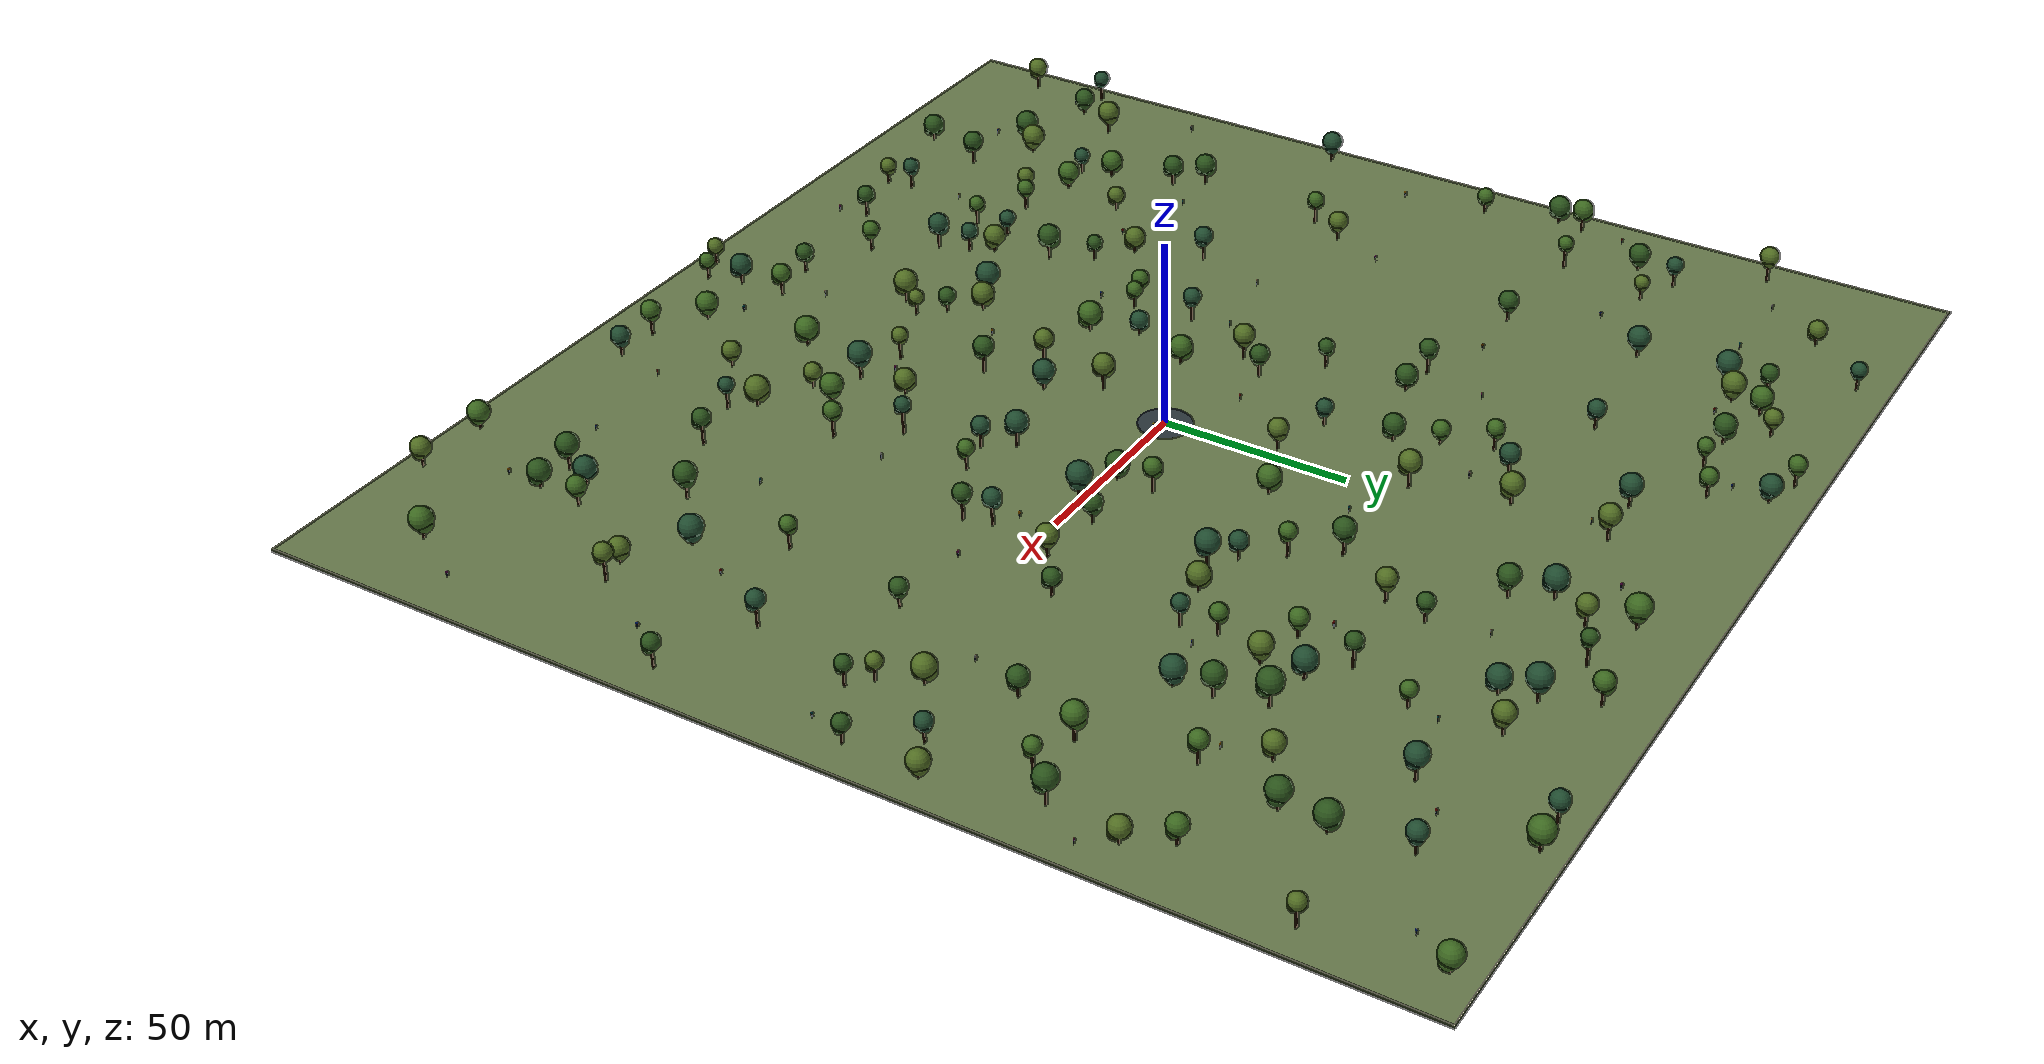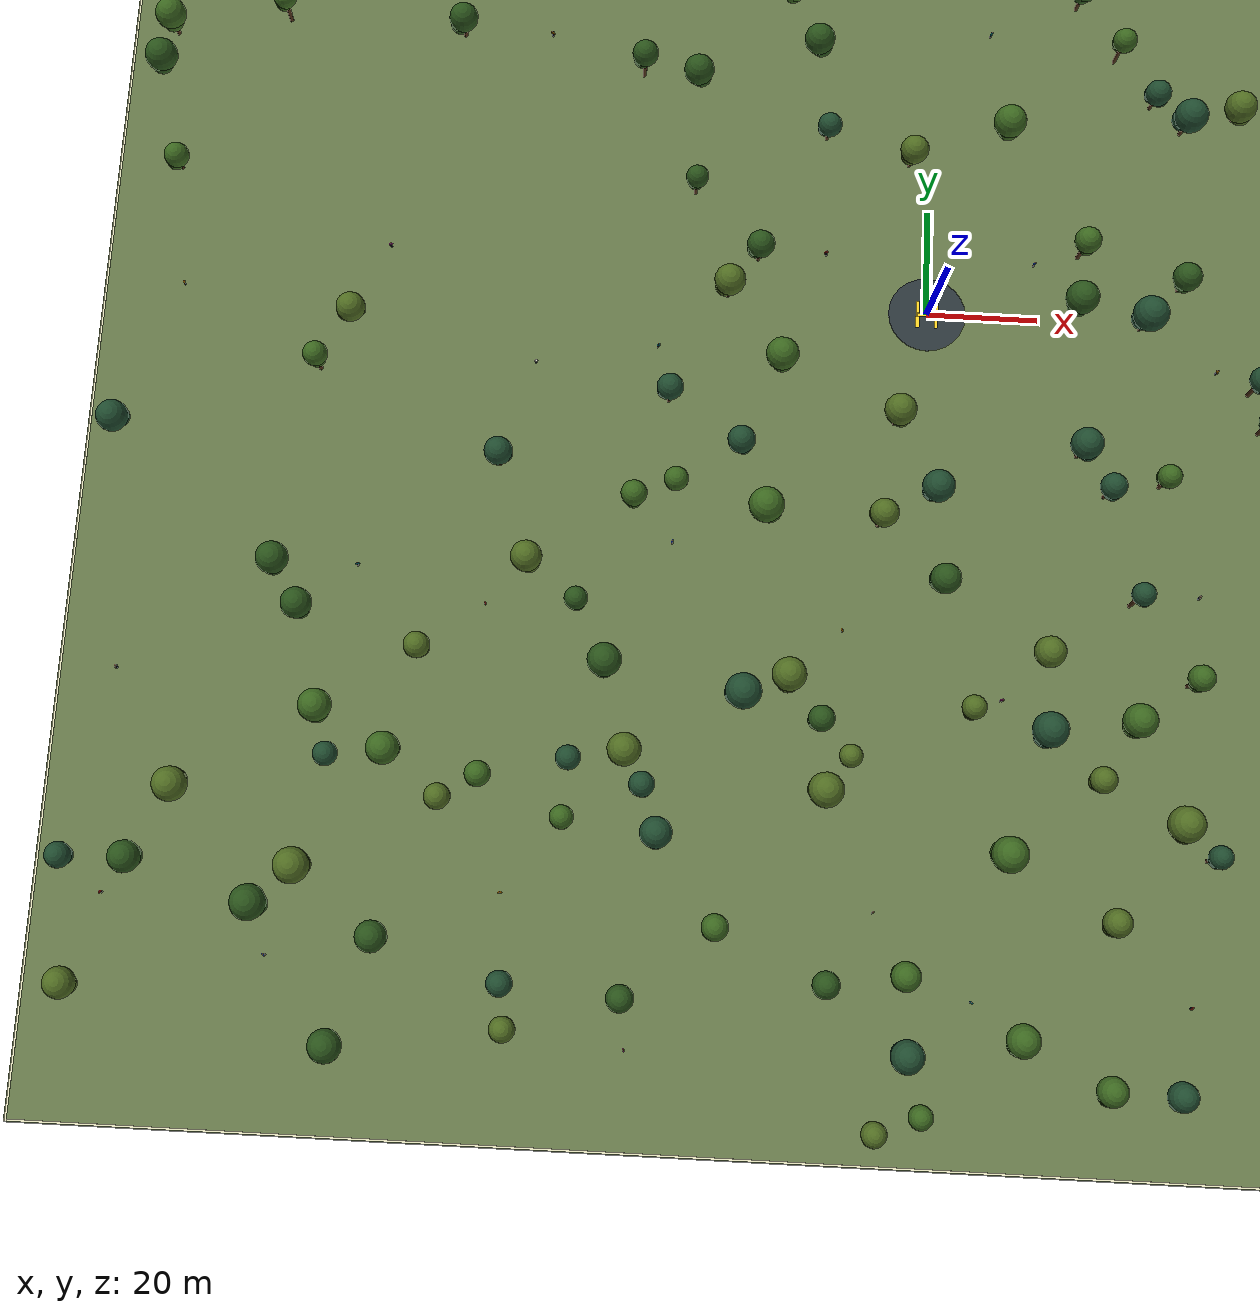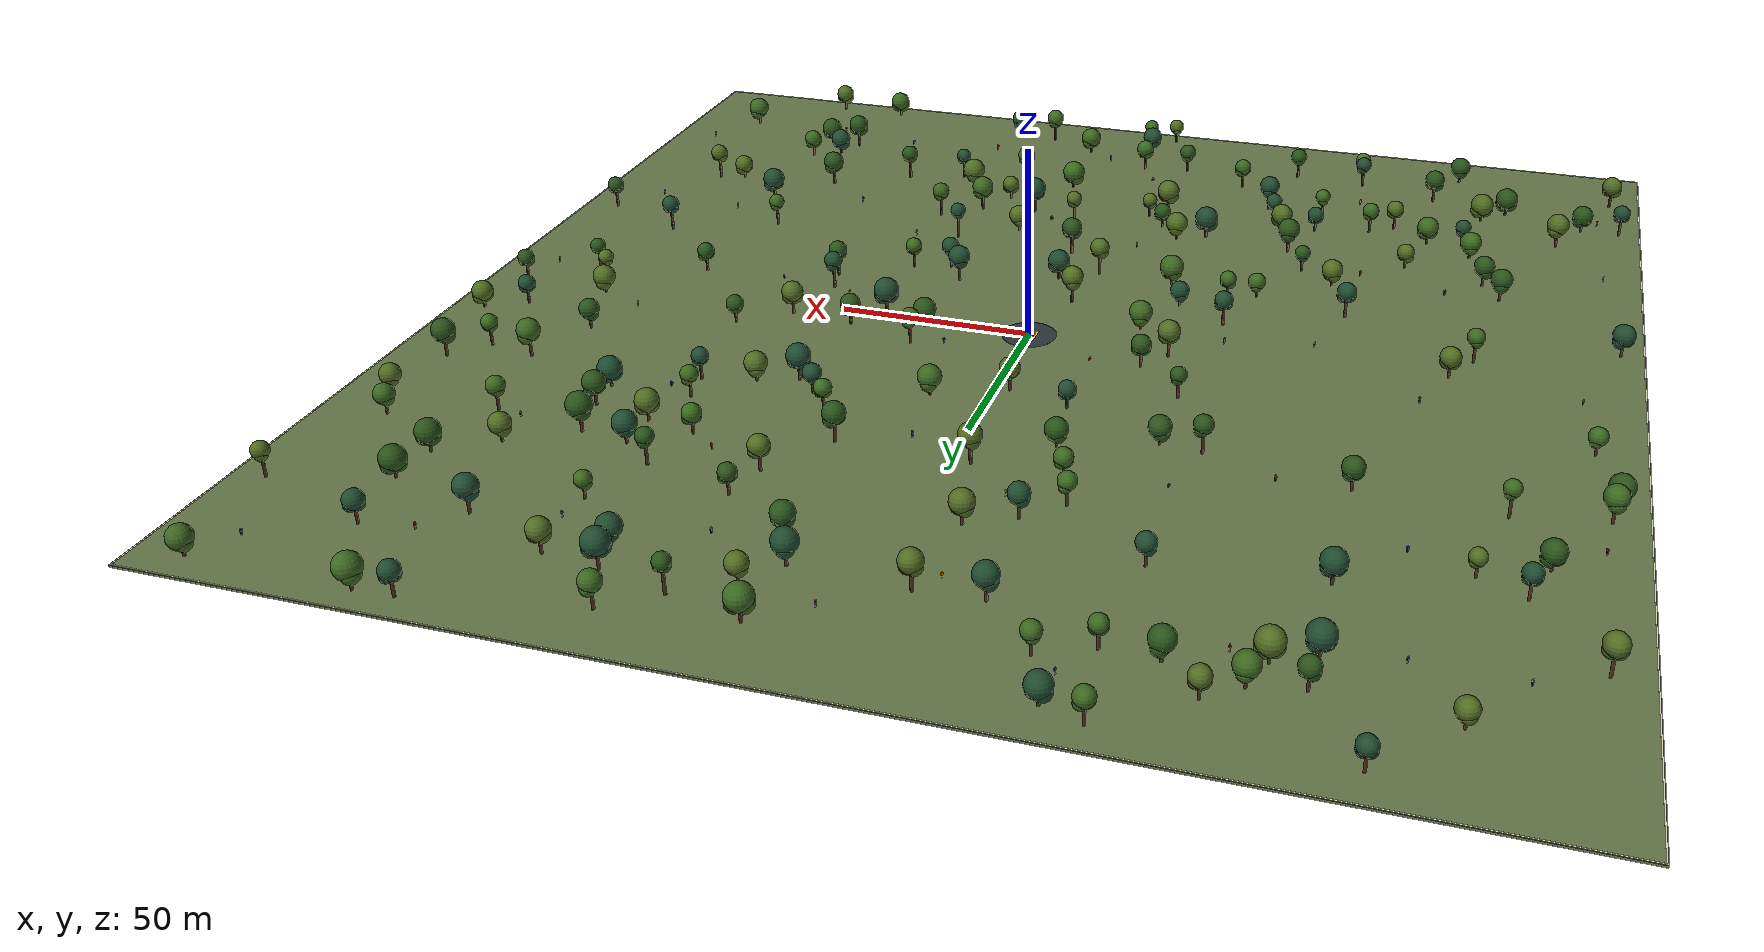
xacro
<?xml version='1.0' encoding='utf-8'?>
<robot xmlns:xacro="http://www.ros.org/wiki/xacro" name="rescue_arena_300">
  <!--Rebuild placements from config/arena.json with generate_arena.py.-->
  <xacro:macro name="arena_box" params="name xyz rpy rgba collision size">
    <visual name="${name}">
      <origin xyz="${xyz}" rpy="${rpy}" />
      <geometry>
        <box size="${size}" />
      </geometry>
      <material name="${name}_material">
        <color rgba="${rgba}" />
      </material>
    </visual>
    <xacro:if value="${collision}">
      <collision name="${name}_collision">
        <origin xyz="${xyz}" rpy="${rpy}" />
        <geometry>
          <box size="${size}" />
        </geometry>
      </collision>
    </xacro:if>
  </xacro:macro>
  <xacro:macro name="arena_sphere" params="name xyz rpy rgba collision radius">
    <visual name="${name}">
      <origin xyz="${xyz}" rpy="${rpy}" />
      <geometry>
        <sphere radius="${radius}" />
      </geometry>
      <material name="${name}_material">
        <color rgba="${rgba}" />
      </material>
    </visual>
    <xacro:if value="${collision}">
      <collision name="${name}_collision">
        <origin xyz="${xyz}" rpy="${rpy}" />
        <geometry>
          <sphere radius="${radius}" />
        </geometry>
      </collision>
    </xacro:if>
  </xacro:macro>
  <xacro:macro name="arena_cylinder" params="name xyz rpy rgba collision radius length">
    <visual name="${name}">
      <origin xyz="${xyz}" rpy="${rpy}" />
      <geometry>
        <cylinder radius="${radius}" length="${length}" />
      </geometry>
      <material name="${name}_material">
        <color rgba="${rgba}" />
      </material>
    </visual>
    <xacro:if value="${collision}">
      <collision name="${name}_collision">
        <origin xyz="${xyz}" rpy="${rpy}" />
        <geometry>
          <cylinder radius="${radius}" length="${length}" />
        </geometry>
      </collision>
    </xacro:if>
  </xacro:macro>
  <link name="world" />
  <gazebo>
    <static>true</static>
  </gazebo>
  <link name="ground">
    <inertial>
      <mass value="1" />
      <inertia ixx="1" iyy="1" izz="1" ixy="0" ixz="0" iyz="0" />
    </inertial>
    <xacro:arena_box name="ground_surface" xyz="0 0 -0.25" rpy="0 0 0" rgba="0.4 0.47 0.29 1" collision="true" size="300 300 0.5" />
  </link>
  <joint name="ground_fixed" type="fixed">
    <parent link="world" />
    <child link="ground" />
    <origin xyz="0 0 0" rpy="0 0 0" />
  </joint>
  <link name="arena_markings">
    <inertial>
      <mass value="1" />
      <inertia ixx="1" iyy="1" izz="1" ixy="0" ixz="0" iyz="0" />
    </inertial>
    <xacro:arena_box name="arena_markings_edge_0_-1" xyz="0 -149.7 0.012" rpy="0 0 0" rgba="0.88 0.87 0.73 1" collision="false" size="300 0.35 0.02" />
    <xacro:arena_box name="arena_markings_edge_0_1" xyz="0 149.7 0.012" rpy="0 0 0" rgba="0.88 0.87 0.73 1" collision="false" size="300 0.35 0.02" />
    <xacro:arena_box name="arena_markings_edge_1_-1" xyz="-149.7 0 0.012" rpy="0 0 0" rgba="0.88 0.87 0.73 1" collision="false" size="0.35 300 0.02" />
    <xacro:arena_box name="arena_markings_edge_1_1" xyz="149.7 0 0.012" rpy="0 0 0" rgba="0.88 0.87 0.73 1" collision="false" size="0.35 300 0.02" />
    <xacro:arena_cylinder name="arena_markings_pad" xyz="0 0 0.012" rpy="0 0 0" rgba="0.17 0.21 0.23 1" collision="false" radius="7" length="0.02" />
    <xacro:arena_box name="arena_markings_h_left" xyz="-1.7 0 0.03" rpy="0 0 0" rgba="1 0.83 0.15 1" collision="false" size="0.6 5 0.02" />
    <xacro:arena_box name="arena_markings_h_right" xyz="1.7 0 0.03" rpy="0 0 0" rgba="1 0.83 0.15 1" collision="false" size="0.6 5 0.02" />
    <xacro:arena_box name="arena_markings_h_bar" xyz="0 0 0.03" rpy="0 0 0" rgba="1 0.83 0.15 1" collision="false" size="3.4 0.6 0.02" />
  </link>
  <joint name="arena_markings_fixed" type="fixed">
    <parent link="world" />
    <child link="arena_markings" />
    <origin xyz="0 0 0" rpy="0 0 0" />
  </joint>
  <link name="human_001">
    <inertial>
      <mass value="1" />
      <inertia ixx="1" iyy="1" izz="1" ixy="0" ixz="0" iyz="0" />
    </inertial>
    <xacro:arena_box name="human_001_torso" xyz="0 0 1.1772" rpy="0 0 0" rgba="0.8 0.16 0.12 1" collision="true" size="0.242222222 0.416622222 0.474755556" />
    <xacro:arena_box name="human_001_hips" xyz="0 0 0.872" rpy="0 0 0" rgba="0.12 0.16 0.23 1" collision="true" size="0.222844444 0.319733333 0.193777778" />
    <xacro:arena_cylinder name="human_001_neck" xyz="0 0 1.45333333" rpy="0 0 0" rgba="0.65 0.4 0.25 1" collision="true" radius="0.0629777778" length="0.0968888889" />
    <xacro:arena_sphere name="human_001_head" xyz="0 0 1.60835556" rpy="0 0 0" rgba="0.65 0.4 0.25 1" collision="true" radius="0.135644444" />
    <xacro:arena_sphere name="human_001_hair" xyz="-0.0242222222 0 1.63064" rpy="0 0 0" rgba="0.09 0.055 0.035 1" collision="false" radius="0.11336" />
    <xacro:arena_sphere name="human_001_nose" xyz="0.132737778 0 1.60835556" rpy="0 0 0" rgba="0.65 0.4 0.25 1" collision="false" radius="0.0319733333" />
    <xacro:arena_cylinder name="human_001_left_leg" xyz="0 0.101733333 0.431155556" rpy="0 0 0" rgba="0.12 0.16 0.23 1" collision="true" radius="0.0755733333" length="0.726666667" />
    <xacro:arena_box name="human_001_left_shoe" xyz="0.0532888889 0.101733333 0.0484444444" rpy="0 0 0" rgba="0.06 0.05 0.04 1" collision="true" size="0.271288889 0.135644444 0.0968888889" />
    <xacro:arena_cylinder name="human_001_left_sleeve" xyz="0 0.266444444 1.23533333" rpy="0.18 0 0" rgba="0.8 0.16 0.12 1" collision="true" radius="0.06976" length="0.280977778" />
    <xacro:arena_cylinder name="human_001_left_forearm" xyz="0.0193777778 0.290666667 0.978577778" rpy="0 0 0" rgba="0.65 0.4 0.25 1" collision="true" radius="0.0503822222" length="0.242222222" />
    <xacro:arena_sphere name="human_001_left_hand" xyz="0.0193777778 0.290666667 0.8284" rpy="0 0 0" rgba="0.65 0.4 0.25 1" collision="true" radius="0.0581333333" />
    <xacro:arena_cylinder name="human_001_right_leg" xyz="0 -0.101733333 0.431155556" rpy="0 0 0" rgba="0.12 0.16 0.23 1" collision="true" radius="0.0755733333" length="0.726666667" />
    <xacro:arena_box name="human_001_right_shoe" xyz="0.0532888889 -0.101733333 0.0484444444" rpy="0 0 0" rgba="0.06 0.05 0.04 1" collision="true" size="0.271288889 0.135644444 0.0968888889" />
    <xacro:arena_cylinder name="human_001_right_sleeve" xyz="0 -0.266444444 1.23533333" rpy="-0.18 0 0" rgba="0.8 0.16 0.12 1" collision="true" radius="0.06976" length="0.280977778" />
    <xacro:arena_cylinder name="human_001_right_forearm" xyz="0.0193777778 -0.290666667 0.978577778" rpy="0 0 0" rgba="0.65 0.4 0.25 1" collision="true" radius="0.0503822222" length="0.242222222" />
    <xacro:arena_sphere name="human_001_right_hand" xyz="0.0193777778 -0.290666667 0.8284" rpy="0 0 0" rgba="0.65 0.4 0.25 1" collision="true" radius="0.0581333333" />
  </link>
  <joint name="human_001_fixed" type="fixed">
    <parent link="world" />
    <child link="human_001" />
    <origin xyz="-138.0301 -111.7692 0" rpy="0 0 -0.781305" />
  </joint>
  <link name="human_002">
    <inertial>
      <mass value="1" />
      <inertia ixx="1" iyy="1" izz="1" ixy="0" ixz="0" iyz="0" />
    </inertial>
    <xacro:arena_box name="human_002_torso" xyz="0 0 1.10025" rpy="0 0 0" rgba="0.1 0.3 0.8 1" collision="true" size="0.226388889 0.389388889 0.443722222" />
    <xacro:arena_box name="human_002_hips" xyz="0 0 0.815" rpy="0 0 0" rgba="0.12 0.16 0.23 1" collision="true" size="0.208277778 0.298833333 0.181111111" />
    <xacro:arena_cylinder name="human_002_neck" xyz="0 0 1.35833333" rpy="0 0 0" rgba="0.9 0.68 0.48 1" collision="true" radius="0.0588611111" length="0.0905555556" />
    <xacro:arena_sphere name="human_002_head" xyz="0 0 1.50322222" rpy="0 0 0" rgba="0.9 0.68 0.48 1" collision="true" radius="0.126777778" />
    <xacro:arena_sphere name="human_002_hair" xyz="-0.0226388889 0 1.52405" rpy="0 0 0" rgba="0.09 0.055 0.035 1" collision="false" radius="0.10595" />
    <xacro:arena_sphere name="human_002_nose" xyz="0.124061111 0 1.50322222" rpy="0 0 0" rgba="0.9 0.68 0.48 1" collision="false" radius="0.0298833333" />
    <xacro:arena_cylinder name="human_002_left_leg" xyz="0 0.0950833333 0.402972222" rpy="0 0 0" rgba="0.12 0.16 0.23 1" collision="true" radius="0.0706333333" length="0.679166667" />
    <xacro:arena_box name="human_002_left_shoe" xyz="0.0498055556 0.0950833333 0.0452777778" rpy="0 0 0" rgba="0.06 0.05 0.04 1" collision="true" size="0.253555556 0.126777778 0.0905555556" />
    <xacro:arena_cylinder name="human_002_left_sleeve" xyz="0 0.249027778 1.15458333" rpy="0.18 0 0" rgba="0.1 0.3 0.8 1" collision="true" radius="0.0652" length="0.262611111" />
    <xacro:arena_cylinder name="human_002_left_forearm" xyz="0.0181111111 0.271666667 0.914611111" rpy="0 0 0" rgba="0.9 0.68 0.48 1" collision="true" radius="0.0470888889" length="0.226388889" />
    <xacro:arena_sphere name="human_002_left_hand" xyz="0.0181111111 0.271666667 0.77425" rpy="0 0 0" rgba="0.9 0.68 0.48 1" collision="true" radius="0.0543333333" />
    <xacro:arena_cylinder name="human_002_right_leg" xyz="0 -0.0950833333 0.402972222" rpy="0 0 0" rgba="0.12 0.16 0.23 1" collision="true" radius="0.0706333333" length="0.679166667" />
    <xacro:arena_box name="human_002_right_shoe" xyz="0.0498055556 -0.0950833333 0.0452777778" rpy="0 0 0" rgba="0.06 0.05 0.04 1" collision="true" size="0.253555556 0.126777778 0.0905555556" />
    <xacro:arena_cylinder name="human_002_right_sleeve" xyz="0 -0.249027778 1.15458333" rpy="-0.18 0 0" rgba="0.1 0.3 0.8 1" collision="true" radius="0.0652" length="0.262611111" />
    <xacro:arena_cylinder name="human_002_right_forearm" xyz="0.0181111111 -0.271666667 0.914611111" rpy="0 0 0" rgba="0.9 0.68 0.48 1" collision="true" radius="0.0470888889" length="0.226388889" />
    <xacro:arena_sphere name="human_002_right_hand" xyz="0.0181111111 -0.271666667 0.77425" rpy="0 0 0" rgba="0.9 0.68 0.48 1" collision="true" radius="0.0543333333" />
  </link>
  <joint name="human_002_fixed" type="fixed">
    <parent link="world" />
    <child link="human_002" />
    <origin xyz="-109.5437 -120.7537 0" rpy="0 0 0.825108" />
  </joint>
  <link name="human_003">
    <inertial>
      <mass value="1" />
      <inertia ixx="1" iyy="1" izz="1" ixy="0" ixz="0" iyz="0" />
    </inertial>
    <xacro:arena_box name="human_003_torso" xyz="0 0 1.1907" rpy="0 0 0" rgba="0.95 0.63 0.06 1" collision="true" size="0.245 0.4214 0.4802" />
    <xacro:arena_box name="human_003_hips" xyz="0 0 0.882" rpy="0 0 0" rgba="0.12 0.16 0.23 1" collision="true" size="0.2254 0.3234 0.196" />
    <xacro:arena_cylinder name="human_003_neck" xyz="0 0 1.47" rpy="0 0 0" rgba="0.38 0.22 0.14 1" collision="true" radius="0.0637" length="0.098" />
    <xacro:arena_sphere name="human_003_head" xyz="0 0 1.6268" rpy="0 0 0" rgba="0.38 0.22 0.14 1" collision="true" radius="0.1372" />
    <xacro:arena_sphere name="human_003_hair" xyz="-0.0245 0 1.64934" rpy="0 0 0" rgba="0.09 0.055 0.035 1" collision="false" radius="0.11466" />
    <xacro:arena_sphere name="human_003_nose" xyz="0.13426 0 1.6268" rpy="0 0 0" rgba="0.38 0.22 0.14 1" collision="false" radius="0.03234" />
    <xacro:arena_cylinder name="human_003_left_leg" xyz="0 0.1029 0.4361" rpy="0 0 0" rgba="0.12 0.16 0.23 1" collision="true" radius="0.07644" length="0.735" />
    <xacro:arena_box name="human_003_left_shoe" xyz="0.0539 0.1029 0.049" rpy="0 0 0" rgba="0.06 0.05 0.04 1" collision="true" size="0.2744 0.1372 0.098" />
    <xacro:arena_cylinder name="human_003_left_sleeve" xyz="0 0.2695 1.2495" rpy="0.18 0 0" rgba="0.95 0.63 0.06 1" collision="true" radius="0.07056" length="0.2842" />
    <xacro:arena_cylinder name="human_003_left_forearm" xyz="0.0196 0.294 0.9898" rpy="0 0 0" rgba="0.38 0.22 0.14 1" collision="true" radius="0.05096" length="0.245" />
    <xacro:arena_sphere name="human_003_left_hand" xyz="0.0196 0.294 0.8379" rpy="0 0 0" rgba="0.38 0.22 0.14 1" collision="true" radius="0.0588" />
    <xacro:arena_cylinder name="human_003_right_leg" xyz="0 -0.1029 0.4361" rpy="0 0 0" rgba="0.12 0.16 0.23 1" collision="true" radius="0.07644" length="0.735" />
    <xacro:arena_box name="human_003_right_shoe" xyz="0.0539 -0.1029 0.049" rpy="0 0 0" rgba="0.06 0.05 0.04 1" collision="true" size="0.2744 0.1372 0.098" />
    <xacro:arena_cylinder name="human_003_right_sleeve" xyz="0 -0.2695 1.2495" rpy="-0.18 0 0" rgba="0.95 0.63 0.06 1" collision="true" radius="0.07056" length="0.2842" />
    <xacro:arena_cylinder name="human_003_right_forearm" xyz="0.0196 -0.294 0.9898" rpy="0 0 0" rgba="0.38 0.22 0.14 1" collision="true" radius="0.05096" length="0.245" />
    <xacro:arena_sphere name="human_003_right_hand" xyz="0.0196 -0.294 0.8379" rpy="0 0 0" rgba="0.38 0.22 0.14 1" collision="true" radius="0.0588" />
  </link>
  <joint name="human_003_fixed" type="fixed">
    <parent link="world" />
    <child link="human_003" />
    <origin xyz="-70.6675 -108.3743 0" rpy="0 0 1.658874" />
  </joint>
  <link name="human_004">
    <inertial>
      <mass value="1" />
      <inertia ixx="1" iyy="1" izz="1" ixy="0" ixz="0" iyz="0" />
    </inertial>
    <xacro:arena_box name="human_004_torso" xyz="0 0 1.114425" rpy="0 0 0" rgba="0.68 0.15 0.57 1" collision="true" size="0.229305556 0.394405556 0.449438889" />
    <xacro:arena_box name="human_004_hips" xyz="0 0 0.8255" rpy="0 0 0" rgba="0.12 0.16 0.23 1" collision="true" size="0.210961111 0.302683333 0.183444444" />
    <xacro:arena_cylinder name="human_004_neck" xyz="0 0 1.37583333" rpy="0 0 0" rgba="0.65 0.4 0.25 1" collision="true" radius="0.0596194444" length="0.0917222222" />
    <xacro:arena_sphere name="human_004_head" xyz="0 0 1.52258889" rpy="0 0 0" rgba="0.65 0.4 0.25 1" collision="true" radius="0.128411111" />
    <xacro:arena_sphere name="human_004_hair" xyz="-0.0229305556 0 1.543685" rpy="0 0 0" rgba="0.09 0.055 0.035 1" collision="false" radius="0.107315" />
    <xacro:arena_sphere name="human_004_nose" xyz="0.125659444 0 1.52258889" rpy="0 0 0" rgba="0.65 0.4 0.25 1" collision="false" radius="0.0302683333" />
    <xacro:arena_cylinder name="human_004_left_leg" xyz="0 0.0963083333 0.408163889" rpy="0 0 0" rgba="0.12 0.16 0.23 1" collision="true" radius="0.0715433333" length="0.687916667" />
    <xacro:arena_box name="human_004_left_shoe" xyz="0.0504472222 0.0963083333 0.0458611111" rpy="0 0 0" rgba="0.06 0.05 0.04 1" collision="true" size="0.256822222 0.128411111 0.0917222222" />
    <xacro:arena_cylinder name="human_004_left_sleeve" xyz="0 0.252236111 1.16945833" rpy="0.18 0 0" rgba="0.68 0.15 0.57 1" collision="true" radius="0.06604" length="0.265994444" />
    <xacro:arena_cylinder name="human_004_left_forearm" xyz="0.0183444444 0.275166667 0.926394444" rpy="0 0 0" rgba="0.65 0.4 0.25 1" collision="true" radius="0.0476955556" length="0.229305556" />
    <xacro:arena_sphere name="human_004_left_hand" xyz="0.0183444444 0.275166667 0.784225" rpy="0 0 0" rgba="0.65 0.4 0.25 1" collision="true" radius="0.0550333333" />
    <xacro:arena_cylinder name="human_004_right_leg" xyz="0 -0.0963083333 0.408163889" rpy="0 0 0" rgba="0.12 0.16 0.23 1" collision="true" radius="0.0715433333" length="0.687916667" />
    <xacro:arena_box name="human_004_right_shoe" xyz="0.0504472222 -0.0963083333 0.0458611111" rpy="0 0 0" rgba="0.06 0.05 0.04 1" collision="true" size="0.256822222 0.128411111 0.0917222222" />
    <xacro:arena_cylinder name="human_004_right_sleeve" xyz="0 -0.252236111 1.16945833" rpy="-0.18 0 0" rgba="0.68 0.15 0.57 1" collision="true" radius="0.06604" length="0.265994444" />
    <xacro:arena_cylinder name="human_004_right_forearm" xyz="0.0183444444 -0.275166667 0.926394444" rpy="0 0 0" rgba="0.65 0.4 0.25 1" collision="true" radius="0.0476955556" length="0.229305556" />
    <xacro:arena_sphere name="human_004_right_hand" xyz="0.0183444444 -0.275166667 0.784225" rpy="0 0 0" rgba="0.65 0.4 0.25 1" collision="true" radius="0.0550333333" />
  </link>
  <joint name="human_004_fixed" type="fixed">
    <parent link="world" />
    <child link="human_004" />
    <origin xyz="-48.5796 -133.1324 0" rpy="0 0 0.397491" />
  </joint>
  <link name="human_005">
    <inertial>
      <mass value="1" />
      <inertia ixx="1" iyy="1" izz="1" ixy="0" ixz="0" iyz="0" />
    </inertial>
    <xacro:arena_box name="human_005_torso" xyz="0 0 1.1961" rpy="0 0 0" rgba="0.85 0.86 0.8 1" collision="true" size="0.246111111 0.423311111 0.482377778" />
    <xacro:arena_box name="human_005_hips" xyz="0 0 0.886" rpy="0 0 0" rgba="0.12 0.16 0.23 1" collision="true" size="0.226422222 0.324866667 0.196888889" />
    <xacro:arena_cylinder name="human_005_neck" xyz="0 0 1.47666667" rpy="0 0 0" rgba="0.9 0.68 0.48 1" collision="true" radius="0.0639888889" length="0.0984444444" />
    <xacro:arena_sphere name="human_005_head" xyz="0 0 1.63417778" rpy="0 0 0" rgba="0.9 0.68 0.48 1" collision="true" radius="0.137822222" />
    <xacro:arena_sphere name="human_005_hair" xyz="-0.0246111111 0 1.65682" rpy="0 0 0" rgba="0.09 0.055 0.035 1" collision="false" radius="0.11518" />
    <xacro:arena_sphere name="human_005_nose" xyz="0.134868889 0 1.63417778" rpy="0 0 0" rgba="0.9 0.68 0.48 1" collision="false" radius="0.0324866667" />
    <xacro:arena_cylinder name="human_005_left_leg" xyz="0 0.103366667 0.438077778" rpy="0 0 0" rgba="0.12 0.16 0.23 1" collision="true" radius="0.0767866667" length="0.738333333" />
    <xacro:arena_box name="human_005_left_shoe" xyz="0.0541444444 0.103366667 0.0492222222" rpy="0 0 0" rgba="0.06 0.05 0.04 1" collision="true" size="0.275644444 0.137822222 0.0984444444" />
    <xacro:arena_cylinder name="human_005_left_sleeve" xyz="0 0.270722222 1.25516667" rpy="0.18 0 0" rgba="0.85 0.86 0.8 1" collision="true" radius="0.07088" length="0.285488889" />
    <xacro:arena_cylinder name="human_005_left_forearm" xyz="0.0196888889 0.295333333 0.994288889" rpy="0 0 0" rgba="0.9 0.68 0.48 1" collision="true" radius="0.0511911111" length="0.246111111" />
    <xacro:arena_sphere name="human_005_left_hand" xyz="0.0196888889 0.295333333 0.8417" rpy="0 0 0" rgba="0.9 0.68 0.48 1" collision="true" radius="0.0590666667" />
    <xacro:arena_cylinder name="human_005_right_leg" xyz="0 -0.103366667 0.438077778" rpy="0 0 0" rgba="0.12 0.16 0.23 1" collision="true" radius="0.0767866667" length="0.738333333" />
    <xacro:arena_box name="human_005_right_shoe" xyz="0.0541444444 -0.103366667 0.0492222222" rpy="0 0 0" rgba="0.06 0.05 0.04 1" collision="true" size="0.275644444 0.137822222 0.0984444444" />
    <xacro:arena_cylinder name="human_005_right_sleeve" xyz="0 -0.270722222 1.25516667" rpy="-0.18 0 0" rgba="0.85 0.86 0.8 1" collision="true" radius="0.07088" length="0.285488889" />
    <xacro:arena_cylinder name="human_005_right_forearm" xyz="0.0196888889 -0.295333333 0.994288889" rpy="0 0 0" rgba="0.9 0.68 0.48 1" collision="true" radius="0.0511911111" length="0.246111111" />
    <xacro:arena_sphere name="human_005_right_hand" xyz="0.0196888889 -0.295333333 0.8417" rpy="0 0 0" rgba="0.9 0.68 0.48 1" collision="true" radius="0.0590666667" />
  </link>
  <joint name="human_005_fixed" type="fixed">
    <parent link="world" />
    <child link="human_005" />
    <origin xyz="-7.8212 -108.359 0" rpy="0 0 -0.881839" />
  </joint>
  <link name="human_006">
    <inertial>
      <mass value="1" />
      <inertia ixx="1" iyy="1" izz="1" ixy="0" ixz="0" iyz="0" />
    </inertial>
    <xacro:arena_box name="human_006_torso" xyz="0 0 1.172475" rpy="0 0 0" rgba="0.06 0.55 0.58 1" collision="true" size="0.24125 0.41495 0.47285" />
    <xacro:arena_box name="human_006_hips" xyz="0 0 0.8685" rpy="0 0 0" rgba="0.12 0.16 0.23 1" collision="true" size="0.22195 0.31845 0.193" />
    <xacro:arena_cylinder name="human_006_neck" xyz="0 0 1.4475" rpy="0 0 0" rgba="0.38 0.22 0.14 1" collision="true" radius="0.062725" length="0.0965" />
    <xacro:arena_sphere name="human_006_head" xyz="0 0 1.6019" rpy="0 0 0" rgba="0.38 0.22 0.14 1" collision="true" radius="0.1351" />
    <xacro:arena_sphere name="human_006_hair" xyz="-0.024125 0 1.624095" rpy="0 0 0" rgba="0.09 0.055 0.035 1" collision="false" radius="0.112905" />
    <xacro:arena_sphere name="human_006_nose" xyz="0.132205 0 1.6019" rpy="0 0 0" rgba="0.38 0.22 0.14 1" collision="false" radius="0.031845" />
    <xacro:arena_cylinder name="human_006_left_leg" xyz="0 0.101325 0.429425" rpy="0 0 0" rgba="0.12 0.16 0.23 1" collision="true" radius="0.07527" length="0.72375" />
    <xacro:arena_box name="human_006_left_shoe" xyz="0.053075 0.101325 0.04825" rpy="0 0 0" rgba="0.06 0.05 0.04 1" collision="true" size="0.2702 0.1351 0.0965" />
    <xacro:arena_cylinder name="human_006_left_sleeve" xyz="0 0.265375 1.230375" rpy="0.18 0 0" rgba="0.06 0.55 0.58 1" collision="true" radius="0.06948" length="0.27985" />
    <xacro:arena_cylinder name="human_006_left_forearm" xyz="0.0193 0.2895 0.97465" rpy="0 0 0" rgba="0.38 0.22 0.14 1" collision="true" radius="0.05018" length="0.24125" />
    <xacro:arena_sphere name="human_006_left_hand" xyz="0.0193 0.2895 0.825075" rpy="0 0 0" rgba="0.38 0.22 0.14 1" collision="true" radius="0.0579" />
    <xacro:arena_cylinder name="human_006_right_leg" xyz="0 -0.101325 0.429425" rpy="0 0 0" rgba="0.12 0.16 0.23 1" collision="true" radius="0.07527" length="0.72375" />
    <xacro:arena_box name="human_006_right_shoe" xyz="0.053075 -0.101325 0.04825" rpy="0 0 0" rgba="0.06 0.05 0.04 1" collision="true" size="0.2702 0.1351 0.0965" />
    <xacro:arena_cylinder name="human_006_right_sleeve" xyz="0 -0.265375 1.230375" rpy="-0.18 0 0" rgba="0.06 0.55 0.58 1" collision="true" radius="0.06948" length="0.27985" />
    <xacro:arena_cylinder name="human_006_right_forearm" xyz="0.0193 -0.2895 0.97465" rpy="0 0 0" rgba="0.38 0.22 0.14 1" collision="true" radius="0.05018" length="0.24125" />
    <xacro:arena_sphere name="human_006_right_hand" xyz="0.0193 -0.2895 0.825075" rpy="0 0 0" rgba="0.38 0.22 0.14 1" collision="true" radius="0.0579" />
  </link>
  <joint name="human_006_fixed" type="fixed">
    <parent link="world" />
    <child link="human_006" />
    <origin xyz="8.8544 -122.3881 0" rpy="0 0 0.834063" />
  </joint>
  <link name="human_007">
    <inertial>
      <mass value="1" />
      <inertia ixx="1" iyy="1" izz="1" ixy="0" ixz="0" iyz="0" />
    </inertial>
    <xacro:arena_box name="human_007_torso" xyz="0 0 1.20285" rpy="0 0 0" rgba="0.8 0.16 0.12 1" collision="true" size="0.2475 0.4257 0.4851" />
    <xacro:arena_box name="human_007_hips" xyz="0 0 0.891" rpy="0 0 0" rgba="0.12 0.16 0.23 1" collision="true" size="0.2277 0.3267 0.198" />
    <xacro:arena_cylinder name="human_007_neck" xyz="0 0 1.485" rpy="0 0 0" rgba="0.65 0.4 0.25 1" collision="true" radius="0.06435" length="0.099" />
    <xacro:arena_sphere name="human_007_head" xyz="0 0 1.6434" rpy="0 0 0" rgba="0.65 0.4 0.25 1" collision="true" radius="0.1386" />
    <xacro:arena_sphere name="human_007_hair" xyz="-0.02475 0 1.66617" rpy="0 0 0" rgba="0.09 0.055 0.035 1" collision="false" radius="0.11583" />
    <xacro:arena_sphere name="human_007_nose" xyz="0.13563 0 1.6434" rpy="0 0 0" rgba="0.65 0.4 0.25 1" collision="false" radius="0.03267" />
    <xacro:arena_cylinder name="human_007_left_leg" xyz="0 0.10395 0.44055" rpy="0 0 0" rgba="0.12 0.16 0.23 1" collision="true" radius="0.07722" length="0.7425" />
    <xacro:arena_box name="human_007_left_shoe" xyz="0.05445 0.10395 0.0495" rpy="0 0 0" rgba="0.06 0.05 0.04 1" collision="true" size="0.2772 0.1386 0.099" />
    <xacro:arena_cylinder name="human_007_left_sleeve" xyz="0 0.27225 1.26225" rpy="0.18 0 0" rgba="0.8 0.16 0.12 1" collision="true" radius="0.07128" length="0.2871" />
    <xacro:arena_cylinder name="human_007_left_forearm" xyz="0.0198 0.297 0.9999" rpy="0 0 0" rgba="0.65 0.4 0.25 1" collision="true" radius="0.05148" length="0.2475" />
    <xacro:arena_sphere name="human_007_left_hand" xyz="0.0198 0.297 0.84645" rpy="0 0 0" rgba="0.65 0.4 0.25 1" collision="true" radius="0.0594" />
    <xacro:arena_cylinder name="human_007_right_leg" xyz="0 -0.10395 0.44055" rpy="0 0 0" rgba="0.12 0.16 0.23 1" collision="true" radius="0.07722" length="0.7425" />
    <xacro:arena_box name="human_007_right_shoe" xyz="0.05445 -0.10395 0.0495" rpy="0 0 0" rgba="0.06 0.05 0.04 1" collision="true" size="0.2772 0.1386 0.099" />
    <xacro:arena_cylinder name="human_007_right_sleeve" xyz="0 -0.27225 1.26225" rpy="-0.18 0 0" rgba="0.8 0.16 0.12 1" collision="true" radius="0.07128" length="0.2871" />
    <xacro:arena_cylinder name="human_007_right_forearm" xyz="0.0198 -0.297 0.9999" rpy="0 0 0" rgba="0.65 0.4 0.25 1" collision="true" radius="0.05148" length="0.2475" />
    <xacro:arena_sphere name="human_007_right_hand" xyz="0.0198 -0.297 0.84645" rpy="0 0 0" rgba="0.65 0.4 0.25 1" collision="true" radius="0.0594" />
  </link>
  <joint name="human_007_fixed" type="fixed">
    <parent link="world" />
    <child link="human_007" />
    <origin xyz="45.5757 -121.4043 0" rpy="0 0 -0.706749" />
  </joint>
  <link name="human_008">
    <inertial>
      <mass value="1" />
      <inertia ixx="1" iyy="1" izz="1" ixy="0" ixz="0" iyz="0" />
    </inertial>
    <xacro:arena_box name="human_008_torso" xyz="0 0 1.0881" rpy="0 0 0" rgba="0.1 0.3 0.8 1" collision="true" size="0.223888889 0.385088889 0.438822222" />
    <xacro:arena_box name="human_008_hips" xyz="0 0 0.806" rpy="0 0 0" rgba="0.12 0.16 0.23 1" collision="true" size="0.205977778 0.295533333 0.179111111" />
    <xacro:arena_cylinder name="human_008_neck" xyz="0 0 1.34333333" rpy="0 0 0" rgba="0.9 0.68 0.48 1" collision="true" radius="0.0582111111" length="0.0895555556" />
    <xacro:arena_sphere name="human_008_head" xyz="0 0 1.48662222" rpy="0 0 0" rgba="0.9 0.68 0.48 1" collision="true" radius="0.125377778" />
    <xacro:arena_sphere name="human_008_hair" xyz="-0.0223888889 0 1.50722" rpy="0 0 0" rgba="0.09 0.055 0.035 1" collision="false" radius="0.10478" />
    <xacro:arena_sphere name="human_008_nose" xyz="0.122691111 0 1.48662222" rpy="0 0 0" rgba="0.9 0.68 0.48 1" collision="false" radius="0.0295533333" />
    <xacro:arena_cylinder name="human_008_left_leg" xyz="0 0.0940333333 0.398522222" rpy="0 0 0" rgba="0.12 0.16 0.23 1" collision="true" radius="0.0698533333" length="0.671666667" />
    <xacro:arena_box name="human_008_left_shoe" xyz="0.0492555556 0.0940333333 0.0447777778" rpy="0 0 0" rgba="0.06 0.05 0.04 1" collision="true" size="0.250755556 0.125377778 0.0895555556" />
    <xacro:arena_cylinder name="human_008_left_sleeve" xyz="0 0.246277778 1.14183333" rpy="0.18 0 0" rgba="0.1 0.3 0.8 1" collision="true" radius="0.06448" length="0.259711111" />
    <xacro:arena_cylinder name="human_008_left_forearm" xyz="0.0179111111 0.268666667 0.904511111" rpy="0 0 0" rgba="0.9 0.68 0.48 1" collision="true" radius="0.0465688889" length="0.223888889" />
    <xacro:arena_sphere name="human_008_left_hand" xyz="0.0179111111 0.268666667 0.7657" rpy="0 0 0" rgba="0.9 0.68 0.48 1" collision="true" radius="0.0537333333" />
    <xacro:arena_cylinder name="human_008_right_leg" xyz="0 -0.0940333333 0.398522222" rpy="0 0 0" rgba="0.12 0.16 0.23 1" collision="true" radius="0.0698533333" length="0.671666667" />
    <xacro:arena_box name="human_008_right_shoe" xyz="0.0492555556 -0.0940333333 0.0447777778" rpy="0 0 0" rgba="0.06 0.05 0.04 1" collision="true" size="0.250755556 0.125377778 0.0895555556" />
    <xacro:arena_cylinder name="human_008_right_sleeve" xyz="0 -0.246277778 1.14183333" rpy="-0.18 0 0" rgba="0.1 0.3 0.8 1" collision="true" radius="0.06448" length="0.259711111" />
    <xacro:arena_cylinder name="human_008_right_forearm" xyz="0.0179111111 -0.268666667 0.904511111" rpy="0 0 0" rgba="0.9 0.68 0.48 1" collision="true" radius="0.0465688889" length="0.223888889" />
    <xacro:arena_sphere name="human_008_right_hand" xyz="0.0179111111 -0.268666667 0.7657" rpy="0 0 0" rgba="0.9 0.68 0.48 1" collision="true" radius="0.0537333333" />
  </link>
  <joint name="human_008_fixed" type="fixed">
    <parent link="world" />
    <child link="human_008" />
    <origin xyz="72.9381 -118.4501 0" rpy="0 0 -1.559715" />
  </joint>
  <link name="human_009">
    <inertial>
      <mass value="1" />
      <inertia ixx="1" iyy="1" izz="1" ixy="0" ixz="0" iyz="0" />
    </inertial>
    <xacro:arena_box name="human_009_torso" xyz="0 0 1.125225" rpy="0 0 0" rgba="0.95 0.63 0.06 1" collision="true" size="0.231527778 0.398227778 0.453794444" />
    <xacro:arena_box name="human_009_hips" xyz="0 0 0.8335" rpy="0 0 0" rgba="0.12 0.16 0.23 1" collision="true" size="0.213005556 0.305616667 0.185222222" />
    <xacro:arena_cylinder name="human_009_neck" xyz="0 0 1.38916667" rpy="0 0 0" rgba="0.38 0.22 0.14 1" collision="true" radius="0.0601972222" length="0.0926111111" />
    <xacro:arena_sphere name="human_009_head" xyz="0 0 1.53734444" rpy="0 0 0" rgba="0.38 0.22 0.14 1" collision="true" radius="0.129655556" />
    <xacro:arena_sphere name="human_009_hair" xyz="-0.0231527778 0 1.558645" rpy="0 0 0" rgba="0.09 0.055 0.035 1" collision="false" radius="0.108355" />
    <xacro:arena_sphere name="human_009_nose" xyz="0.126877222 0 1.53734444" rpy="0 0 0" rgba="0.38 0.22 0.14 1" collision="false" radius="0.0305616667" />
    <xacro:arena_cylinder name="human_009_left_leg" xyz="0 0.0972416667 0.412119444" rpy="0 0 0" rgba="0.12 0.16 0.23 1" collision="true" radius="0.0722366667" length="0.694583333" />
    <xacro:arena_box name="human_009_left_shoe" xyz="0.0509361111 0.0972416667 0.0463055556" rpy="0 0 0" rgba="0.06 0.05 0.04 1" collision="true" size="0.259311111 0.129655556 0.0926111111" />
    <xacro:arena_cylinder name="human_009_left_sleeve" xyz="0 0.254680556 1.18079167" rpy="0.18 0 0" rgba="0.95 0.63 0.06 1" collision="true" radius="0.06668" length="0.268572222" />
    <xacro:arena_cylinder name="human_009_left_forearm" xyz="0.0185222222 0.277833333 0.935372222" rpy="0 0 0" rgba="0.38 0.22 0.14 1" collision="true" radius="0.0481577778" length="0.231527778" />
    <xacro:arena_sphere name="human_009_left_hand" xyz="0.0185222222 0.277833333 0.791825" rpy="0 0 0" rgba="0.38 0.22 0.14 1" collision="true" radius="0.0555666667" />
    <xacro:arena_cylinder name="human_009_right_leg" xyz="0 -0.0972416667 0.412119444" rpy="0 0 0" rgba="0.12 0.16 0.23 1" collision="true" radius="0.0722366667" length="0.694583333" />
    <xacro:arena_box name="human_009_right_shoe" xyz="0.0509361111 -0.0972416667 0.0463055556" rpy="0 0 0" rgba="0.06 0.05 0.04 1" collision="true" size="0.259311111 0.129655556 0.0926111111" />
    <xacro:arena_cylinder name="human_009_right_sleeve" xyz="0 -0.254680556 1.18079167" rpy="-0.18 0 0" rgba="0.95 0.63 0.06 1" collision="true" radius="0.06668" length="0.268572222" />
    <xacro:arena_cylinder name="human_009_right_forearm" xyz="0.0185222222 -0.277833333 0.935372222" rpy="0 0 0" rgba="0.38 0.22 0.14 1" collision="true" radius="0.0481577778" length="0.231527778" />
    <xacro:arena_sphere name="human_009_right_hand" xyz="0.0185222222 -0.277833333 0.791825" rpy="0 0 0" rgba="0.38 0.22 0.14 1" collision="true" radius="0.0555666667" />
  </link>
  <joint name="human_009_fixed" type="fixed">
    <parent link="world" />
    <child link="human_009" />
    <origin xyz="98.3734 -123.8305 0" rpy="0 0 -2.414176" />
  </joint>
  <link name="human_010">
    <inertial>
      <mass value="1" />
      <inertia ixx="1" iyy="1" izz="1" ixy="0" ixz="0" iyz="0" />
    </inertial>
    <xacro:arena_box name="human_010_torso" xyz="0 0 1.184625" rpy="0 0 0" rgba="0.68 0.15 0.57 1" collision="true" size="0.24375 0.41925 0.47775" />
    <xacro:arena_box name="human_010_hips" xyz="0 0 0.8775" rpy="0 0 0" rgba="0.12 0.16 0.23 1" collision="true" size="0.22425 0.32175 0.195" />
    <xacro:arena_cylinder name="human_010_neck" xyz="0 0 1.4625" rpy="0 0 0" rgba="0.65 0.4 0.25 1" collision="true" radius="0.063375" length="0.0975" />
    <xacro:arena_sphere name="human_010_head" xyz="0 0 1.6185" rpy="0 0 0" rgba="0.65 0.4 0.25 1" collision="true" radius="0.1365" />
    <xacro:arena_sphere name="human_010_hair" xyz="-0.024375 0 1.640925" rpy="0 0 0" rgba="0.09 0.055 0.035 1" collision="false" radius="0.114075" />
    <xacro:arena_sphere name="human_010_nose" xyz="0.133575 0 1.6185" rpy="0 0 0" rgba="0.65 0.4 0.25 1" collision="false" radius="0.032175" />
    <xacro:arena_cylinder name="human_010_left_leg" xyz="0 0.102375 0.433875" rpy="0 0 0" rgba="0.12 0.16 0.23 1" collision="true" radius="0.07605" length="0.73125" />
    <xacro:arena_box name="human_010_left_shoe" xyz="0.053625 0.102375 0.04875" rpy="0 0 0" rgba="0.06 0.05 0.04 1" collision="true" size="0.273 0.1365 0.0975" />
    <xacro:arena_cylinder name="human_010_left_sleeve" xyz="0 0.268125 1.243125" rpy="0.18 0 0" rgba="0.68 0.15 0.57 1" collision="true" radius="0.0702" length="0.28275" />
    <xacro:arena_cylinder name="human_010_left_forearm" xyz="0.0195 0.2925 0.98475" rpy="0 0 0" rgba="0.65 0.4 0.25 1" collision="true" radius="0.0507" length="0.24375" />
    <xacro:arena_sphere name="human_010_left_hand" xyz="0.0195 0.2925 0.833625" rpy="0 0 0" rgba="0.65 0.4 0.25 1" collision="true" radius="0.0585" />
    <xacro:arena_cylinder name="human_010_right_leg" xyz="0 -0.102375 0.433875" rpy="0 0 0" rgba="0.12 0.16 0.23 1" collision="true" radius="0.07605" length="0.73125" />
    <xacro:arena_box name="human_010_right_shoe" xyz="0.053625 -0.102375 0.04875" rpy="0 0 0" rgba="0.06 0.05 0.04 1" collision="true" size="0.273 0.1365 0.0975" />
    <xacro:arena_cylinder name="human_010_right_sleeve" xyz="0 -0.268125 1.243125" rpy="-0.18 0 0" rgba="0.68 0.15 0.57 1" collision="true" radius="0.0702" length="0.28275" />
    <xacro:arena_cylinder name="human_010_right_forearm" xyz="0.0195 -0.2925 0.98475" rpy="0 0 0" rgba="0.65 0.4 0.25 1" collision="true" radius="0.0507" length="0.24375" />
    <xacro:arena_sphere name="human_010_right_hand" xyz="0.0195 -0.2925 0.833625" rpy="0 0 0" rgba="0.65 0.4 0.25 1" collision="true" radius="0.0585" />
  </link>
  <joint name="human_010_fixed" type="fixed">
    <parent link="world" />
    <child link="human_010" />
    <origin xyz="137.4392 -107.6366 0" rpy="0 0 -2.333684" />
  </joint>
  <link name="human_011">
    <inertial>
      <mass value="1" />
      <inertia ixx="1" iyy="1" izz="1" ixy="0" ixz="0" iyz="0" />
    </inertial>
    <xacro:arena_box name="human_011_torso" xyz="0 0 1.242" rpy="0 0 0" rgba="0.85 0.86 0.8 1" collision="true" size="0.255555556 0.439555556 0.500888889" />
    <xacro:arena_box name="human_011_hips" xyz="0 0 0.92" rpy="0 0 0" rgba="0.12 0.16 0.23 1" collision="true" size="0.235111111 0.337333333 0.204444444" />
    <xacro:arena_cylinder name="human_011_neck" xyz="0 0 1.53333333" rpy="0 0 0" rgba="0.9 0.68 0.48 1" collision="true" radius="0.0664444444" length="0.102222222" />
    <xacro:arena_sphere name="human_011_head" xyz="0 0 1.69688889" rpy="0 0 0" rgba="0.9 0.68 0.48 1" collision="true" radius="0.143111111" />
    <xacro:arena_sphere name="human_011_hair" xyz="-0.0255555556 0 1.7204" rpy="0 0 0" rgba="0.09 0.055 0.035 1" collision="false" radius="0.1196" />
    <xacro:arena_sphere name="human_011_nose" xyz="0.140044444 0 1.69688889" rpy="0 0 0" rgba="0.9 0.68 0.48 1" collision="false" radius="0.0337333333" />
    <xacro:arena_cylinder name="human_011_left_leg" xyz="0 0.107333333 0.454888889" rpy="0 0 0" rgba="0.12 0.16 0.23 1" collision="true" radius="0.0797333333" length="0.766666667" />
    <xacro:arena_box name="human_011_left_shoe" xyz="0.0562222222 0.107333333 0.0511111111" rpy="0 0 0" rgba="0.06 0.05 0.04 1" collision="true" size="0.286222222 0.143111111 0.102222222" />
    <xacro:arena_cylinder name="human_011_left_sleeve" xyz="0 0.281111111 1.30333333" rpy="0.18 0 0" rgba="0.85 0.86 0.8 1" collision="true" radius="0.0736" length="0.296444444" />
    <xacro:arena_cylinder name="human_011_left_forearm" xyz="0.0204444444 0.306666667 1.03244444" rpy="0 0 0" rgba="0.9 0.68 0.48 1" collision="true" radius="0.0531555556" length="0.255555556" />
    <xacro:arena_sphere name="human_011_left_hand" xyz="0.0204444444 0.306666667 0.874" rpy="0 0 0" rgba="0.9 0.68 0.48 1" collision="true" radius="0.0613333333" />
    <xacro:arena_cylinder name="human_011_right_leg" xyz="0 -0.107333333 0.454888889" rpy="0 0 0" rgba="0.12 0.16 0.23 1" collision="true" radius="0.0797333333" length="0.766666667" />
    <xacro:arena_box name="human_011_right_shoe" xyz="0.0562222222 -0.107333333 0.0511111111" rpy="0 0 0" rgba="0.06 0.05 0.04 1" collision="true" size="0.286222222 0.143111111 0.102222222" />
    <xacro:arena_cylinder name="human_011_right_sleeve" xyz="0 -0.281111111 1.30333333" rpy="-0.18 0 0" rgba="0.85 0.86 0.8 1" collision="true" radius="0.0736" length="0.296444444" />
    <xacro:arena_cylinder name="human_011_right_forearm" xyz="0.0204444444 -0.306666667 1.03244444" rpy="0 0 0" rgba="0.9 0.68 0.48 1" collision="true" radius="0.0531555556" length="0.255555556" />
    <xacro:arena_sphere name="human_011_right_hand" xyz="0.0204444444 -0.306666667 0.874" rpy="0 0 0" rgba="0.9 0.68 0.48 1" collision="true" radius="0.0613333333" />
  </link>
  <joint name="human_011_fixed" type="fixed">
    <parent link="world" />
    <child link="human_011" />
    <origin xyz="-139.6745 -72.9729 0" rpy="0 0 2.894577" />
  </joint>
  <link name="human_012">
    <inertial>
      <mass value="1" />
      <inertia ixx="1" iyy="1" izz="1" ixy="0" ixz="0" iyz="0" />
    </inertial>
    <xacro:arena_box name="human_012_torso" xyz="0 0 1.200825" rpy="0 0 0" rgba="0.06 0.55 0.58 1" collision="true" size="0.247083333 0.424983333 0.484283333" />
    <xacro:arena_box name="human_012_hips" xyz="0 0 0.8895" rpy="0 0 0" rgba="0.12 0.16 0.23 1" collision="true" size="0.227316667 0.32615 0.197666667" />
    <xacro:arena_cylinder name="human_012_neck" xyz="0 0 1.4825" rpy="0 0 0" rgba="0.38 0.22 0.14 1" collision="true" radius="0.0642416667" length="0.0988333333" />
    <xacro:arena_sphere name="human_012_head" xyz="0 0 1.64063333" rpy="0 0 0" rgba="0.38 0.22 0.14 1" collision="true" radius="0.138366667" />
    <xacro:arena_sphere name="human_012_hair" xyz="-0.0247083333 0 1.663365" rpy="0 0 0" rgba="0.09 0.055 0.035 1" collision="false" radius="0.115635" />
    <xacro:arena_sphere name="human_012_nose" xyz="0.135401667 0 1.64063333" rpy="0 0 0" rgba="0.38 0.22 0.14 1" collision="false" radius="0.032615" />
    <xacro:arena_cylinder name="human_012_left_leg" xyz="0 0.103775 0.439808333" rpy="0 0 0" rgba="0.12 0.16 0.23 1" collision="true" radius="0.07709" length="0.74125" />
    <xacro:arena_box name="human_012_left_shoe" xyz="0.0543583333 0.103775 0.0494166667" rpy="0 0 0" rgba="0.06 0.05 0.04 1" collision="true" size="0.276733333 0.138366667 0.0988333333" />
    <xacro:arena_cylinder name="human_012_left_sleeve" xyz="0 0.271791667 1.260125" rpy="0.18 0 0" rgba="0.06 0.55 0.58 1" collision="true" radius="0.07116" length="0.286616667" />
    <xacro:arena_cylinder name="human_012_left_forearm" xyz="0.0197666667 0.2965 0.998216667" rpy="0 0 0" rgba="0.38 0.22 0.14 1" collision="true" radius="0.0513933333" length="0.247083333" />
    <xacro:arena_sphere name="human_012_left_hand" xyz="0.0197666667 0.2965 0.845025" rpy="0 0 0" rgba="0.38 0.22 0.14 1" collision="true" radius="0.0593" />
    <xacro:arena_cylinder name="human_012_right_leg" xyz="0 -0.103775 0.439808333" rpy="0 0 0" rgba="0.12 0.16 0.23 1" collision="true" radius="0.07709" length="0.74125" />
    <xacro:arena_box name="human_012_right_shoe" xyz="0.0543583333 -0.103775 0.0494166667" rpy="0 0 0" rgba="0.06 0.05 0.04 1" collision="true" size="0.276733333 0.138366667 0.0988333333" />
    <xacro:arena_cylinder name="human_012_right_sleeve" xyz="0 -0.271791667 1.260125" rpy="-0.18 0 0" rgba="0.06 0.55 0.58 1" collision="true" radius="0.07116" length="0.286616667" />
    <xacro:arena_cylinder name="human_012_right_forearm" xyz="0.0197666667 -0.2965 0.998216667" rpy="0 0 0" rgba="0.38 0.22 0.14 1" collision="true" radius="0.0513933333" length="0.247083333" />
    <xacro:arena_sphere name="human_012_right_hand" xyz="0.0197666667 -0.2965 0.845025" rpy="0 0 0" rgba="0.38 0.22 0.14 1" collision="true" radius="0.0593" />
  </link>
  <joint name="human_012_fixed" type="fixed">
    <parent link="world" />
    <child link="human_012" />
    <origin xyz="-99.3511 -52.4852 0" rpy="0 0 -1.578946" />
  </joint>
  <link name="human_013">
    <inertial>
      <mass value="1" />
      <inertia ixx="1" iyy="1" izz="1" ixy="0" ixz="0" iyz="0" />
    </inertial>
    <xacro:arena_box name="human_013_torso" xyz="0 0 1.188" rpy="0 0 0" rgba="0.8 0.16 0.12 1" collision="true" size="0.244444444 0.420444444 0.479111111" />
    <xacro:arena_box name="human_013_hips" xyz="0 0 0.88" rpy="0 0 0" rgba="0.12 0.16 0.23 1" collision="true" size="0.224888889 0.322666667 0.195555556" />
    <xacro:arena_cylinder name="human_013_neck" xyz="0 0 1.46666667" rpy="0 0 0" rgba="0.65 0.4 0.25 1" collision="true" radius="0.0635555556" length="0.0977777778" />
    <xacro:arena_sphere name="human_013_head" xyz="0 0 1.62311111" rpy="0 0 0" rgba="0.65 0.4 0.25 1" collision="true" radius="0.136888889" />
    <xacro:arena_sphere name="human_013_hair" xyz="-0.0244444444 0 1.6456" rpy="0 0 0" rgba="0.09 0.055 0.035 1" collision="false" radius="0.1144" />
    <xacro:arena_sphere name="human_013_nose" xyz="0.133955556 0 1.62311111" rpy="0 0 0" rgba="0.65 0.4 0.25 1" collision="false" radius="0.0322666667" />
    <xacro:arena_cylinder name="human_013_left_leg" xyz="0 0.102666667 0.435111111" rpy="0 0 0" rgba="0.12 0.16 0.23 1" collision="true" radius="0.0762666667" length="0.733333333" />
    <xacro:arena_box name="human_013_left_shoe" xyz="0.0537777778 0.102666667 0.0488888889" rpy="0 0 0" rgba="0.06 0.05 0.04 1" collision="true" size="0.273777778 0.136888889 0.0977777778" />
    <xacro:arena_cylinder name="human_013_left_sleeve" xyz="0 0.268888889 1.24666667" rpy="0.18 0 0" rgba="0.8 0.16 0.12 1" collision="true" radius="0.0704" length="0.283555556" />
    <xacro:arena_cylinder name="human_013_left_forearm" xyz="0.0195555556 0.293333333 0.987555556" rpy="0 0 0" rgba="0.65 0.4 0.25 1" collision="true" radius="0.0508444444" length="0.244444444" />
    <xacro:arena_sphere name="human_013_left_hand" xyz="0.0195555556 0.293333333 0.836" rpy="0 0 0" rgba="0.65 0.4 0.25 1" collision="true" radius="0.0586666667" />
    <xacro:arena_cylinder name="human_013_right_leg" xyz="0 -0.102666667 0.435111111" rpy="0 0 0" rgba="0.12 0.16 0.23 1" collision="true" radius="0.0762666667" length="0.733333333" />
    <xacro:arena_box name="human_013_right_shoe" xyz="0.0537777778 -0.102666667 0.0488888889" rpy="0 0 0" rgba="0.06 0.05 0.04 1" collision="true" size="0.273777778 0.136888889 0.0977777778" />
    <xacro:arena_cylinder name="human_013_right_sleeve" xyz="0 -0.268888889 1.24666667" rpy="-0.18 0 0" rgba="0.8 0.16 0.12 1" collision="true" radius="0.0704" length="0.283555556" />
    <xacro:arena_cylinder name="human_013_right_forearm" xyz="0.0195555556 -0.293333333 0.987555556" rpy="0 0 0" rgba="0.65 0.4 0.25 1" collision="true" radius="0.0508444444" length="0.244444444" />
    <xacro:arena_sphere name="human_013_right_hand" xyz="0.0195555556 -0.293333333 0.836" rpy="0 0 0" rgba="0.65 0.4 0.25 1" collision="true" radius="0.0586666667" />
  </link>
  <joint name="human_013_fixed" type="fixed">
    <parent link="world" />
    <child link="human_013" />
    <origin xyz="-76.5308 -58.3419 0" rpy="0 0 -2.591704" />
  </joint>
  <link name="human_014">
    <inertial>
      <mass value="1" />
      <inertia ixx="1" iyy="1" izz="1" ixy="0" ixz="0" iyz="0" />
    </inertial>
    <xacro:arena_box name="human_014_torso" xyz="0 0 1.199475" rpy="0 0 0" rgba="0.1 0.3 0.8 1" collision="true" size="0.246805556 0.424505556 0.483738889" />
    <xacro:arena_box name="human_014_hips" xyz="0 0 0.8885" rpy="0 0 0" rgba="0.12 0.16 0.23 1" collision="true" size="0.227061111 0.325783333 0.197444444" />
    <xacro:arena_cylinder name="human_014_neck" xyz="0 0 1.48083333" rpy="0 0 0" rgba="0.9 0.68 0.48 1" collision="true" radius="0.0641694444" length="0.0987222222" />
    <xacro:arena_sphere name="human_014_head" xyz="0 0 1.63878889" rpy="0 0 0" rgba="0.9 0.68 0.48 1" collision="true" radius="0.138211111" />
    <xacro:arena_sphere name="human_014_hair" xyz="-0.0246805556 0 1.661495" rpy="0 0 0" rgba="0.09 0.055 0.035 1" collision="false" radius="0.115505" />
    <xacro:arena_sphere name="human_014_nose" xyz="0.135249444 0 1.63878889" rpy="0 0 0" rgba="0.9 0.68 0.48 1" collision="false" radius="0.0325783333" />
    <xacro:arena_cylinder name="human_014_left_leg" xyz="0 0.103658333 0.439313889" rpy="0 0 0" rgba="0.12 0.16 0.23 1" collision="true" radius="0.0770033333" length="0.740416667" />
    <xacro:arena_box name="human_014_left_shoe" xyz="0.0542972222 0.103658333 0.0493611111" rpy="0 0 0" rgba="0.06 0.05 0.04 1" collision="true" size="0.276422222 0.138211111 0.0987222222" />
    <xacro:arena_cylinder name="human_014_left_sleeve" xyz="0 0.271486111 1.25870833" rpy="0.18 0 0" rgba="0.1 0.3 0.8 1" collision="true" radius="0.07108" length="0.286294444" />
    <xacro:arena_cylinder name="human_014_left_forearm" xyz="0.0197444444 0.296166667 0.997094444" rpy="0 0 0" rgba="0.9 0.68 0.48 1" collision="true" radius="0.0513355556" length="0.246805556" />
    <xacro:arena_sphere name="human_014_left_hand" xyz="0.0197444444 0.296166667 0.844075" rpy="0 0 0" rgba="0.9 0.68 0.48 1" collision="true" radius="0.0592333333" />
    <xacro:arena_cylinder name="human_014_right_leg" xyz="0 -0.103658333 0.439313889" rpy="0 0 0" rgba="0.12 0.16 0.23 1" collision="true" radius="0.0770033333" length="0.740416667" />
    <xacro:arena_box name="human_014_right_shoe" xyz="0.0542972222 -0.103658333 0.0493611111" rpy="0 0 0" rgba="0.06 0.05 0.04 1" collision="true" size="0.276422222 0.138211111 0.0987222222" />
    <xacro:arena_cylinder name="human_014_right_sleeve" xyz="0 -0.271486111 1.25870833" rpy="-0.18 0 0" rgba="0.1 0.3 0.8 1" collision="true" radius="0.07108" length="0.286294444" />
    <xacro:arena_cylinder name="human_014_right_forearm" xyz="0.0197444444 -0.296166667 0.997094444" rpy="0 0 0" rgba="0.9 0.68 0.48 1" collision="true" radius="0.0513355556" length="0.246805556" />
    <xacro:arena_sphere name="human_014_right_hand" xyz="0.0197444444 -0.296166667 0.844075" rpy="0 0 0" rgba="0.9 0.68 0.48 1" collision="true" radius="0.0592333333" />
  </link>
  <joint name="human_014_fixed" type="fixed">
    <parent link="world" />
    <child link="human_014" />
    <origin xyz="-44.38 -45.5412 0" rpy="0 0 -0.266037" />
  </joint>
  <link name="human_015">
    <inertial>
      <mass value="1" />
      <inertia ixx="1" iyy="1" izz="1" ixy="0" ixz="0" iyz="0" />
    </inertial>
    <xacro:arena_box name="human_015_torso" xyz="0 0 1.090125" rpy="0 0 0" rgba="0.95 0.63 0.06 1" collision="true" size="0.224305556 0.385805556 0.439638889" />
    <xacro:arena_box name="human_015_hips" xyz="0 0 0.8075" rpy="0 0 0" rgba="0.12 0.16 0.23 1" collision="true" size="0.206361111 0.296083333 0.179444444" />
    <xacro:arena_cylinder name="human_015_neck" xyz="0 0 1.34583333" rpy="0 0 0" rgba="0.38 0.22 0.14 1" collision="true" radius="0.0583194444" length="0.0897222222" />
    <xacro:arena_sphere name="human_015_head" xyz="0 0 1.48938889" rpy="0 0 0" rgba="0.38 0.22 0.14 1" collision="true" radius="0.125611111" />
    <xacro:arena_sphere name="human_015_hair" xyz="-0.0224305556 0 1.510025" rpy="0 0 0" rgba="0.09 0.055 0.035 1" collision="false" radius="0.104975" />
    <xacro:arena_sphere name="human_015_nose" xyz="0.122919444 0 1.48938889" rpy="0 0 0" rgba="0.38 0.22 0.14 1" collision="false" radius="0.0296083333" />
    <xacro:arena_cylinder name="human_015_left_leg" xyz="0 0.0942083333 0.399263889" rpy="0 0 0" rgba="0.12 0.16 0.23 1" collision="true" radius="0.0699833333" length="0.672916667" />
    <xacro:arena_box name="human_015_left_shoe" xyz="0.0493472222 0.0942083333 0.0448611111" rpy="0 0 0" rgba="0.06 0.05 0.04 1" collision="true" size="0.251222222 0.125611111 0.0897222222" />
    <xacro:arena_cylinder name="human_015_left_sleeve" xyz="0 0.246736111 1.14395833" rpy="0.18 0 0" rgba="0.95 0.63 0.06 1" collision="true" radius="0.0646" length="0.260194444" />
    <xacro:arena_cylinder name="human_015_left_forearm" xyz="0.0179444444 0.269166667 0.906194444" rpy="0 0 0" rgba="0.38 0.22 0.14 1" collision="true" radius="0.0466555556" length="0.224305556" />
    <xacro:arena_sphere name="human_015_left_hand" xyz="0.0179444444 0.269166667 0.767125" rpy="0 0 0" rgba="0.38 0.22 0.14 1" collision="true" radius="0.0538333333" />
    <xacro:arena_cylinder name="human_015_right_leg" xyz="0 -0.0942083333 0.399263889" rpy="0 0 0" rgba="0.12 0.16 0.23 1" collision="true" radius="0.0699833333" length="0.672916667" />
    <xacro:arena_box name="human_015_right_shoe" xyz="0.0493472222 -0.0942083333 0.0448611111" rpy="0 0 0" rgba="0.06 0.05 0.04 1" collision="true" size="0.251222222 0.125611111 0.0897222222" />
    <xacro:arena_cylinder name="human_015_right_sleeve" xyz="0 -0.246736111 1.14395833" rpy="-0.18 0 0" rgba="0.95 0.63 0.06 1" collision="true" radius="0.0646" length="0.260194444" />
    <xacro:arena_cylinder name="human_015_right_forearm" xyz="0.0179444444 -0.269166667 0.906194444" rpy="0 0 0" rgba="0.38 0.22 0.14 1" collision="true" radius="0.0466555556" length="0.224305556" />
    <xacro:arena_sphere name="human_015_right_hand" xyz="0.0179444444 -0.269166667 0.767125" rpy="0 0 0" rgba="0.38 0.22 0.14 1" collision="true" radius="0.0538333333" />
  </link>
  <joint name="human_015_fixed" type="fixed">
    <parent link="world" />
    <child link="human_015" />
    <origin xyz="-14.0979 -59.9359 0" rpy="0 0 0.482746" />
  </joint>
  <link name="human_016">
    <inertial>
      <mass value="1" />
      <inertia ixx="1" iyy="1" izz="1" ixy="0" ixz="0" iyz="0" />
    </inertial>
    <xacro:arena_box name="human_016_torso" xyz="0 0 1.253475" rpy="0 0 0" rgba="0.68 0.15 0.57 1" collision="true" size="0.257916667 0.443616667 0.505516667" />
    <xacro:arena_box name="human_016_hips" xyz="0 0 0.9285" rpy="0 0 0" rgba="0.12 0.16 0.23 1" collision="true" size="0.237283333 0.34045 0.206333333" />
    <xacro:arena_cylinder name="human_016_neck" xyz="0 0 1.5475" rpy="0 0 0" rgba="0.65 0.4 0.25 1" collision="true" radius="0.0670583333" length="0.103166667" />
    <xacro:arena_sphere name="human_016_head" xyz="0 0 1.71256667" rpy="0 0 0" rgba="0.65 0.4 0.25 1" collision="true" radius="0.144433333" />
    <xacro:arena_sphere name="human_016_hair" xyz="-0.0257916667 0 1.736295" rpy="0 0 0" rgba="0.09 0.055 0.035 1" collision="false" radius="0.120705" />
    <xacro:arena_sphere name="human_016_nose" xyz="0.141338333 0 1.71256667" rpy="0 0 0" rgba="0.65 0.4 0.25 1" collision="false" radius="0.034045" />
    <xacro:arena_cylinder name="human_016_left_leg" xyz="0 0.108325 0.459091667" rpy="0 0 0" rgba="0.12 0.16 0.23 1" collision="true" radius="0.08047" length="0.77375" />
    <xacro:arena_box name="human_016_left_shoe" xyz="0.0567416667 0.108325 0.0515833333" rpy="0 0 0" rgba="0.06 0.05 0.04 1" collision="true" size="0.288866667 0.144433333 0.103166667" />
    <xacro:arena_cylinder name="human_016_left_sleeve" xyz="0 0.283708333 1.315375" rpy="0.18 0 0" rgba="0.68 0.15 0.57 1" collision="true" radius="0.07428" length="0.299183333" />
    <xacro:arena_cylinder name="human_016_left_forearm" xyz="0.0206333333 0.3095 1.04198333" rpy="0 0 0" rgba="0.65 0.4 0.25 1" collision="true" radius="0.0536466667" length="0.257916667" />
    <xacro:arena_sphere name="human_016_left_hand" xyz="0.0206333333 0.3095 0.882075" rpy="0 0 0" rgba="0.65 0.4 0.25 1" collision="true" radius="0.0619" />
    <xacro:arena_cylinder name="human_016_right_leg" xyz="0 -0.108325 0.459091667" rpy="0 0 0" rgba="0.12 0.16 0.23 1" collision="true" radius="0.08047" length="0.77375" />
    <xacro:arena_box name="human_016_right_shoe" xyz="0.0567416667 -0.108325 0.0515833333" rpy="0 0 0" rgba="0.06 0.05 0.04 1" collision="true" size="0.288866667 0.144433333 0.103166667" />
    <xacro:arena_cylinder name="human_016_right_sleeve" xyz="0 -0.283708333 1.315375" rpy="-0.18 0 0" rgba="0.68 0.15 0.57 1" collision="true" radius="0.07428" length="0.299183333" />
    <xacro:arena_cylinder name="human_016_right_forearm" xyz="0.0206333333 -0.3095 1.04198333" rpy="0 0 0" rgba="0.65 0.4 0.25 1" collision="true" radius="0.0536466667" length="0.257916667" />
    <xacro:arena_sphere name="human_016_right_hand" xyz="0.0206333333 -0.3095 0.882075" rpy="0 0 0" rgba="0.65 0.4 0.25 1" collision="true" radius="0.0619" />
  </link>
  <joint name="human_016_fixed" type="fixed">
    <parent link="world" />
    <child link="human_016" />
    <origin xyz="13.7577 -70.8739 0" rpy="0 0 -1.558927" />
  </joint>
  <link name="human_017">
    <inertial>
      <mass value="1" />
      <inertia ixx="1" iyy="1" izz="1" ixy="0" ixz="0" iyz="0" />
    </inertial>
    <xacro:arena_box name="human_017_torso" xyz="0 0 1.204875" rpy="0 0 0" rgba="0.85 0.86 0.8 1" collision="true" size="0.247916667 0.426416667 0.485916667" />
    <xacro:arena_box name="human_017_hips" xyz="0 0 0.8925" rpy="0 0 0" rgba="0.12 0.16 0.23 1" collision="true" size="0.228083333 0.32725 0.198333333" />
    <xacro:arena_cylinder name="human_017_neck" xyz="0 0 1.4875" rpy="0 0 0" rgba="0.9 0.68 0.48 1" collision="true" radius="0.0644583333" length="0.0991666667" />
    <xacro:arena_sphere name="human_017_head" xyz="0 0 1.64616667" rpy="0 0 0" rgba="0.9 0.68 0.48 1" collision="true" radius="0.138833333" />
    <xacro:arena_sphere name="human_017_hair" xyz="-0.0247916667 0 1.668975" rpy="0 0 0" rgba="0.09 0.055 0.035 1" collision="false" radius="0.116025" />
    <xacro:arena_sphere name="human_017_nose" xyz="0.135858333 0 1.64616667" rpy="0 0 0" rgba="0.9 0.68 0.48 1" collision="false" radius="0.032725" />
    <xacro:arena_cylinder name="human_017_left_leg" xyz="0 0.104125 0.441291667" rpy="0 0 0" rgba="0.12 0.16 0.23 1" collision="true" radius="0.07735" length="0.74375" />
    <xacro:arena_box name="human_017_left_shoe" xyz="0.0545416667 0.104125 0.0495833333" rpy="0 0 0" rgba="0.06 0.05 0.04 1" collision="true" size="0.277666667 0.138833333 0.0991666667" />
    <xacro:arena_cylinder name="human_017_left_sleeve" xyz="0 0.272708333 1.264375" rpy="0.18 0 0" rgba="0.85 0.86 0.8 1" collision="true" radius="0.0714" length="0.287583333" />
    <xacro:arena_cylinder name="human_017_left_forearm" xyz="0.0198333333 0.2975 1.00158333" rpy="0 0 0" rgba="0.9 0.68 0.48 1" collision="true" radius="0.0515666667" length="0.247916667" />
    <xacro:arena_sphere name="human_017_left_hand" xyz="0.0198333333 0.2975 0.847875" rpy="0 0 0" rgba="0.9 0.68 0.48 1" collision="true" radius="0.0595" />
    <xacro:arena_cylinder name="human_017_right_leg" xyz="0 -0.104125 0.441291667" rpy="0 0 0" rgba="0.12 0.16 0.23 1" collision="true" radius="0.07735" length="0.74375" />
    <xacro:arena_box name="human_017_right_shoe" xyz="0.0545416667 -0.104125 0.0495833333" rpy="0 0 0" rgba="0.06 0.05 0.04 1" collision="true" size="0.277666667 0.138833333 0.0991666667" />
    <xacro:arena_cylinder name="human_017_right_sleeve" xyz="0 -0.272708333 1.264375" rpy="-0.18 0 0" rgba="0.85 0.86 0.8 1" collision="true" radius="0.0714" length="0.287583333" />
    <xacro:arena_cylinder name="human_017_right_forearm" xyz="0.0198333333 -0.2975 1.00158333" rpy="0 0 0" rgba="0.9 0.68 0.48 1" collision="true" radius="0.0515666667" length="0.247916667" />
    <xacro:arena_sphere name="human_017_right_hand" xyz="0.0198333333 -0.2975 0.847875" rpy="0 0 0" rgba="0.9 0.68 0.48 1" collision="true" radius="0.0595" />
  </link>
  <joint name="human_017_fixed" type="fixed">
    <parent link="world" />
    <child link="human_017" />
    <origin xyz="48.2424 -50.8471 0" rpy="0 0 -3.129366" />
  </joint>
  <link name="human_018">
    <inertial>
      <mass value="1" />
      <inertia ixx="1" iyy="1" izz="1" ixy="0" ixz="0" iyz="0" />
    </inertial>
    <xacro:arena_box name="human_018_torso" xyz="0 0 1.21635" rpy="0 0 0" rgba="0.06 0.55 0.58 1" collision="true" size="0.250277778 0.430477778 0.490544444" />
    <xacro:arena_box name="human_018_hips" xyz="0 0 0.901" rpy="0 0 0" rgba="0.12 0.16 0.23 1" collision="true" size="0.230255556 0.330366667 0.200222222" />
    <xacro:arena_cylinder name="human_018_neck" xyz="0 0 1.50166667" rpy="0 0 0" rgba="0.38 0.22 0.14 1" collision="true" radius="0.0650722222" length="0.100111111" />
    <xacro:arena_sphere name="human_018_head" xyz="0 0 1.66184444" rpy="0 0 0" rgba="0.38 0.22 0.14 1" collision="true" radius="0.140155556" />
    <xacro:arena_sphere name="human_018_hair" xyz="-0.0250277778 0 1.68487" rpy="0 0 0" rgba="0.09 0.055 0.035 1" collision="false" radius="0.11713" />
    <xacro:arena_sphere name="human_018_nose" xyz="0.137152222 0 1.66184444" rpy="0 0 0" rgba="0.38 0.22 0.14 1" collision="false" radius="0.0330366667" />
    <xacro:arena_cylinder name="human_018_left_leg" xyz="0 0.105116667 0.445494444" rpy="0 0 0" rgba="0.12 0.16 0.23 1" collision="true" radius="0.0780866667" length="0.750833333" />
    <xacro:arena_box name="human_018_left_shoe" xyz="0.0550611111 0.105116667 0.0500555556" rpy="0 0 0" rgba="0.06 0.05 0.04 1" collision="true" size="0.280311111 0.140155556 0.100111111" />
    <xacro:arena_cylinder name="human_018_left_sleeve" xyz="0 0.275305556 1.27641667" rpy="0.18 0 0" rgba="0.06 0.55 0.58 1" collision="true" radius="0.07208" length="0.290322222" />
    <xacro:arena_cylinder name="human_018_left_forearm" xyz="0.0200222222 0.300333333 1.01112222" rpy="0 0 0" rgba="0.38 0.22 0.14 1" collision="true" radius="0.0520577778" length="0.250277778" />
    <xacro:arena_sphere name="human_018_left_hand" xyz="0.0200222222 0.300333333 0.85595" rpy="0 0 0" rgba="0.38 0.22 0.14 1" collision="true" radius="0.0600666667" />
    <xacro:arena_cylinder name="human_018_right_leg" xyz="0 -0.105116667 0.445494444" rpy="0 0 0" rgba="0.12 0.16 0.23 1" collision="true" radius="0.0780866667" length="0.750833333" />
    <xacro:arena_box name="human_018_right_shoe" xyz="0.0550611111 -0.105116667 0.0500555556" rpy="0 0 0" rgba="0.06 0.05 0.04 1" collision="true" size="0.280311111 0.140155556 0.100111111" />
    <xacro:arena_cylinder name="human_018_right_sleeve" xyz="0 -0.275305556 1.27641667" rpy="-0.18 0 0" rgba="0.06 0.55 0.58 1" collision="true" radius="0.07208" length="0.290322222" />
    <xacro:arena_cylinder name="human_018_right_forearm" xyz="0.0200222222 -0.300333333 1.01112222" rpy="0 0 0" rgba="0.38 0.22 0.14 1" collision="true" radius="0.0520577778" length="0.250277778" />
    <xacro:arena_sphere name="human_018_right_hand" xyz="0.0200222222 -0.300333333 0.85595" rpy="0 0 0" rgba="0.38 0.22 0.14 1" collision="true" radius="0.0600666667" />
  </link>
  <joint name="human_018_fixed" type="fixed">
    <parent link="world" />
    <child link="human_018" />
    <origin xyz="71.6326 -69.4191 0" rpy="0 0 -1.640003" />
  </joint>
  <link name="human_019">
    <inertial>
      <mass value="1" />
      <inertia ixx="1" iyy="1" izz="1" ixy="0" ixz="0" iyz="0" />
    </inertial>
    <xacro:arena_box name="human_019_torso" xyz="0 0 1.1178" rpy="0 0 0" rgba="0.8 0.16 0.12 1" collision="true" size="0.23 0.3956 0.4508" />
    <xacro:arena_box name="human_019_hips" xyz="0 0 0.828" rpy="0 0 0" rgba="0.12 0.16 0.23 1" collision="true" size="0.2116 0.3036 0.184" />
    <xacro:arena_cylinder name="human_019_neck" xyz="0 0 1.38" rpy="0 0 0" rgba="0.65 0.4 0.25 1" collision="true" radius="0.0598" length="0.092" />
    <xacro:arena_sphere name="human_019_head" xyz="0 0 1.5272" rpy="0 0 0" rgba="0.65 0.4 0.25 1" collision="true" radius="0.1288" />
    <xacro:arena_sphere name="human_019_hair" xyz="-0.023 0 1.54836" rpy="0 0 0" rgba="0.09 0.055 0.035 1" collision="false" radius="0.10764" />
    <xacro:arena_sphere name="human_019_nose" xyz="0.12604 0 1.5272" rpy="0 0 0" rgba="0.65 0.4 0.25 1" collision="false" radius="0.03036" />
    <xacro:arena_cylinder name="human_019_left_leg" xyz="0 0.0966 0.4094" rpy="0 0 0" rgba="0.12 0.16 0.23 1" collision="true" radius="0.07176" length="0.69" />
    <xacro:arena_box name="human_019_left_shoe" xyz="0.0506 0.0966 0.046" rpy="0 0 0" rgba="0.06 0.05 0.04 1" collision="true" size="0.2576 0.1288 0.092" />
    <xacro:arena_cylinder name="human_019_left_sleeve" xyz="0 0.253 1.173" rpy="0.18 0 0" rgba="0.8 0.16 0.12 1" collision="true" radius="0.06624" length="0.2668" />
    <xacro:arena_cylinder name="human_019_left_forearm" xyz="0.0184 0.276 0.9292" rpy="0 0 0" rgba="0.65 0.4 0.25 1" collision="true" radius="0.04784" length="0.23" />
    <xacro:arena_sphere name="human_019_left_hand" xyz="0.0184 0.276 0.7866" rpy="0 0 0" rgba="0.65 0.4 0.25 1" collision="true" radius="0.0552" />
    <xacro:arena_cylinder name="human_019_right_leg" xyz="0 -0.0966 0.4094" rpy="0 0 0" rgba="0.12 0.16 0.23 1" collision="true" radius="0.07176" length="0.69" />
    <xacro:arena_box name="human_019_right_shoe" xyz="0.0506 -0.0966 0.046" rpy="0 0 0" rgba="0.06 0.05 0.04 1" collision="true" size="0.2576 0.1288 0.092" />
    <xacro:arena_cylinder name="human_019_right_sleeve" xyz="0 -0.253 1.173" rpy="-0.18 0 0" rgba="0.8 0.16 0.12 1" collision="true" radius="0.06624" length="0.2668" />
    <xacro:arena_cylinder name="human_019_right_forearm" xyz="0.0184 -0.276 0.9292" rpy="0 0 0" rgba="0.65 0.4 0.25 1" collision="true" radius="0.04784" length="0.23" />
    <xacro:arena_sphere name="human_019_right_hand" xyz="0.0184 -0.276 0.7866" rpy="0 0 0" rgba="0.65 0.4 0.25 1" collision="true" radius="0.0552" />
  </link>
  <joint name="human_019_fixed" type="fixed">
    <parent link="world" />
    <child link="human_019" />
    <origin xyz="105.4357 -54.7425 0" rpy="0 0 1.218782" />
  </joint>
  <link name="human_020">
    <inertial>
      <mass value="1" />
      <inertia ixx="1" iyy="1" izz="1" ixy="0" ixz="0" iyz="0" />
    </inertial>
    <xacro:arena_box name="human_020_torso" xyz="0 0 1.234575" rpy="0 0 0" rgba="0.1 0.3 0.8 1" collision="true" size="0.254027778 0.436927778 0.497894444" />
    <xacro:arena_box name="human_020_hips" xyz="0 0 0.9145" rpy="0 0 0" rgba="0.12 0.16 0.23 1" collision="true" size="0.233705556 0.335316667 0.203222222" />
    <xacro:arena_cylinder name="human_020_neck" xyz="0 0 1.52416667" rpy="0 0 0" rgba="0.9 0.68 0.48 1" collision="true" radius="0.0660472222" length="0.101611111" />
    <xacro:arena_sphere name="human_020_head" xyz="0 0 1.68674444" rpy="0 0 0" rgba="0.9 0.68 0.48 1" collision="true" radius="0.142255556" />
    <xacro:arena_sphere name="human_020_hair" xyz="-0.0254027778 0 1.710115" rpy="0 0 0" rgba="0.09 0.055 0.035 1" collision="false" radius="0.118885" />
    <xacro:arena_sphere name="human_020_nose" xyz="0.139207222 0 1.68674444" rpy="0 0 0" rgba="0.9 0.68 0.48 1" collision="false" radius="0.0335316667" />
    <xacro:arena_cylinder name="human_020_left_leg" xyz="0 0.106691667 0.452169444" rpy="0 0 0" rgba="0.12 0.16 0.23 1" collision="true" radius="0.0792566667" length="0.762083333" />
    <xacro:arena_box name="human_020_left_shoe" xyz="0.0558861111 0.106691667 0.0508055556" rpy="0 0 0" rgba="0.06 0.05 0.04 1" collision="true" size="0.284511111 0.142255556 0.101611111" />
    <xacro:arena_cylinder name="human_020_left_sleeve" xyz="0 0.279430556 1.29554167" rpy="0.18 0 0" rgba="0.1 0.3 0.8 1" collision="true" radius="0.07316" length="0.294672222" />
    <xacro:arena_cylinder name="human_020_left_forearm" xyz="0.0203222222 0.304833333 1.02627222" rpy="0 0 0" rgba="0.9 0.68 0.48 1" collision="true" radius="0.0528377778" length="0.254027778" />
    <xacro:arena_sphere name="human_020_left_hand" xyz="0.0203222222 0.304833333 0.868775" rpy="0 0 0" rgba="0.9 0.68 0.48 1" collision="true" radius="0.0609666667" />
    <xacro:arena_cylinder name="human_020_right_leg" xyz="0 -0.106691667 0.452169444" rpy="0 0 0" rgba="0.12 0.16 0.23 1" collision="true" radius="0.0792566667" length="0.762083333" />
    <xacro:arena_box name="human_020_right_shoe" xyz="0.0558861111 -0.106691667 0.0508055556" rpy="0 0 0" rgba="0.06 0.05 0.04 1" collision="true" size="0.284511111 0.142255556 0.101611111" />
    <xacro:arena_cylinder name="human_020_right_sleeve" xyz="0 -0.279430556 1.29554167" rpy="-0.18 0 0" rgba="0.1 0.3 0.8 1" collision="true" radius="0.07316" length="0.294672222" />
    <xacro:arena_cylinder name="human_020_right_forearm" xyz="0.0203222222 -0.304833333 1.02627222" rpy="0 0 0" rgba="0.9 0.68 0.48 1" collision="true" radius="0.0528377778" length="0.254027778" />
    <xacro:arena_sphere name="human_020_right_hand" xyz="0.0203222222 -0.304833333 0.868775" rpy="0 0 0" rgba="0.9 0.68 0.48 1" collision="true" radius="0.0609666667" />
  </link>
  <joint name="human_020_fixed" type="fixed">
    <parent link="world" />
    <child link="human_020" />
    <origin xyz="130.812 -58.119 0" rpy="0 0 0.679412" />
  </joint>
  <link name="human_021">
    <inertial>
      <mass value="1" />
      <inertia ixx="1" iyy="1" izz="1" ixy="0" ixz="0" iyz="0" />
    </inertial>
    <xacro:arena_box name="human_021_torso" xyz="0 0 1.0827" rpy="0 0 0" rgba="0.95 0.63 0.06 1" collision="true" size="0.222777778 0.383177778 0.436644444" />
    <xacro:arena_box name="human_021_hips" xyz="0 0 0.802" rpy="0 0 0" rgba="0.12 0.16 0.23 1" collision="true" size="0.204955556 0.294066667 0.178222222" />
    <xacro:arena_cylinder name="human_021_neck" xyz="0 0 1.33666667" rpy="0 0 0" rgba="0.38 0.22 0.14 1" collision="true" radius="0.0579222222" length="0.0891111111" />
    <xacro:arena_sphere name="human_021_head" xyz="0 0 1.47924444" rpy="0 0 0" rgba="0.38 0.22 0.14 1" collision="true" radius="0.124755556" />
    <xacro:arena_sphere name="human_021_hair" xyz="-0.0222777778 0 1.49974" rpy="0 0 0" rgba="0.09 0.055 0.035 1" collision="false" radius="0.10426" />
    <xacro:arena_sphere name="human_021_nose" xyz="0.122082222 0 1.47924444" rpy="0 0 0" rgba="0.38 0.22 0.14 1" collision="false" radius="0.0294066667" />
    <xacro:arena_cylinder name="human_021_left_leg" xyz="0 0.0935666667 0.396544444" rpy="0 0 0" rgba="0.12 0.16 0.23 1" collision="true" radius="0.0695066667" length="0.668333333" />
    <xacro:arena_box name="human_021_left_shoe" xyz="0.0490111111 0.0935666667 0.0445555556" rpy="0 0 0" rgba="0.06 0.05 0.04 1" collision="true" size="0.249511111 0.124755556 0.0891111111" />
    <xacro:arena_cylinder name="human_021_left_sleeve" xyz="0 0.245055556 1.13616667" rpy="0.18 0 0" rgba="0.95 0.63 0.06 1" collision="true" radius="0.06416" length="0.258422222" />
    <xacro:arena_cylinder name="human_021_left_forearm" xyz="0.0178222222 0.267333333 0.900022222" rpy="0 0 0" rgba="0.38 0.22 0.14 1" collision="true" radius="0.0463377778" length="0.222777778" />
    <xacro:arena_sphere name="human_021_left_hand" xyz="0.0178222222 0.267333333 0.7619" rpy="0 0 0" rgba="0.38 0.22 0.14 1" collision="true" radius="0.0534666667" />
    <xacro:arena_cylinder name="human_021_right_leg" xyz="0 -0.0935666667 0.396544444" rpy="0 0 0" rgba="0.12 0.16 0.23 1" collision="true" radius="0.0695066667" length="0.668333333" />
    <xacro:arena_box name="human_021_right_shoe" xyz="0.0490111111 -0.0935666667 0.0445555556" rpy="0 0 0" rgba="0.06 0.05 0.04 1" collision="true" size="0.249511111 0.124755556 0.0891111111" />
    <xacro:arena_cylinder name="human_021_right_sleeve" xyz="0 -0.245055556 1.13616667" rpy="-0.18 0 0" rgba="0.95 0.63 0.06 1" collision="true" radius="0.06416" length="0.258422222" />
    <xacro:arena_cylinder name="human_021_right_forearm" xyz="0.0178222222 -0.267333333 0.900022222" rpy="0 0 0" rgba="0.38 0.22 0.14 1" collision="true" radius="0.0463377778" length="0.222777778" />
    <xacro:arena_sphere name="human_021_right_hand" xyz="0.0178222222 -0.267333333 0.7619" rpy="0 0 0" rgba="0.38 0.22 0.14 1" collision="true" radius="0.0534666667" />
  </link>
  <joint name="human_021_fixed" type="fixed">
    <parent link="world" />
    <child link="human_021" />
    <origin xyz="-135.2557 -1.2326 0" rpy="0 0 -2.802291" />
  </joint>
  <link name="human_022">
    <inertial>
      <mass value="1" />
      <inertia ixx="1" iyy="1" izz="1" ixy="0" ixz="0" iyz="0" />
    </inertial>
    <xacro:arena_box name="human_022_torso" xyz="0 0 1.18665" rpy="0 0 0" rgba="0.68 0.15 0.57 1" collision="true" size="0.244166667 0.419966667 0.478566667" />
    <xacro:arena_box name="human_022_hips" xyz="0 0 0.879" rpy="0 0 0" rgba="0.12 0.16 0.23 1" collision="true" size="0.224633333 0.3223 0.195333333" />
    <xacro:arena_cylinder name="human_022_neck" xyz="0 0 1.465" rpy="0 0 0" rgba="0.65 0.4 0.25 1" collision="true" radius="0.0634833333" length="0.0976666667" />
    <xacro:arena_sphere name="human_022_head" xyz="0 0 1.62126667" rpy="0 0 0" rgba="0.65 0.4 0.25 1" collision="true" radius="0.136733333" />
    <xacro:arena_sphere name="human_022_hair" xyz="-0.0244166667 0 1.64373" rpy="0 0 0" rgba="0.09 0.055 0.035 1" collision="false" radius="0.11427" />
    <xacro:arena_sphere name="human_022_nose" xyz="0.133803333 0 1.62126667" rpy="0 0 0" rgba="0.65 0.4 0.25 1" collision="false" radius="0.03223" />
    <xacro:arena_cylinder name="human_022_left_leg" xyz="0 0.10255 0.434616667" rpy="0 0 0" rgba="0.12 0.16 0.23 1" collision="true" radius="0.07618" length="0.7325" />
    <xacro:arena_box name="human_022_left_shoe" xyz="0.0537166667 0.10255 0.0488333333" rpy="0 0 0" rgba="0.06 0.05 0.04 1" collision="true" size="0.273466667 0.136733333 0.0976666667" />
    <xacro:arena_cylinder name="human_022_left_sleeve" xyz="0 0.268583333 1.24525" rpy="0.18 0 0" rgba="0.68 0.15 0.57 1" collision="true" radius="0.07032" length="0.283233333" />
    <xacro:arena_cylinder name="human_022_left_forearm" xyz="0.0195333333 0.293 0.986433333" rpy="0 0 0" rgba="0.65 0.4 0.25 1" collision="true" radius="0.0507866667" length="0.244166667" />
    <xacro:arena_sphere name="human_022_left_hand" xyz="0.0195333333 0.293 0.83505" rpy="0 0 0" rgba="0.65 0.4 0.25 1" collision="true" radius="0.0586" />
    <xacro:arena_cylinder name="human_022_right_leg" xyz="0 -0.10255 0.434616667" rpy="0 0 0" rgba="0.12 0.16 0.23 1" collision="true" radius="0.07618" length="0.7325" />
    <xacro:arena_box name="human_022_right_shoe" xyz="0.0537166667 -0.10255 0.0488333333" rpy="0 0 0" rgba="0.06 0.05 0.04 1" collision="true" size="0.273466667 0.136733333 0.0976666667" />
    <xacro:arena_cylinder name="human_022_right_sleeve" xyz="0 -0.268583333 1.24525" rpy="-0.18 0 0" rgba="0.68 0.15 0.57 1" collision="true" radius="0.07032" length="0.283233333" />
    <xacro:arena_cylinder name="human_022_right_forearm" xyz="0.0195333333 -0.293 0.986433333" rpy="0 0 0" rgba="0.65 0.4 0.25 1" collision="true" radius="0.0507866667" length="0.244166667" />
    <xacro:arena_sphere name="human_022_right_hand" xyz="0.0195333333 -0.293 0.83505" rpy="0 0 0" rgba="0.65 0.4 0.25 1" collision="true" radius="0.0586" />
  </link>
  <joint name="human_022_fixed" type="fixed">
    <parent link="world" />
    <child link="human_022" />
    <origin xyz="-98.2181 8.0793 0" rpy="0 0 1.669556" />
  </joint>
  <link name="human_023">
    <inertial>
      <mass value="1" />
      <inertia ixx="1" iyy="1" izz="1" ixy="0" ixz="0" iyz="0" />
    </inertial>
    <xacro:arena_box name="human_023_torso" xyz="0 0 1.129275" rpy="0 0 0" rgba="0.85 0.86 0.8 1" collision="true" size="0.232361111 0.399661111 0.455427778" />
    <xacro:arena_box name="human_023_hips" xyz="0 0 0.8365" rpy="0 0 0" rgba="0.12 0.16 0.23 1" collision="true" size="0.213772222 0.306716667 0.185888889" />
    <xacro:arena_cylinder name="human_023_neck" xyz="0 0 1.39416667" rpy="0 0 0" rgba="0.9 0.68 0.48 1" collision="true" radius="0.0604138889" length="0.0929444444" />
    <xacro:arena_sphere name="human_023_head" xyz="0 0 1.54287778" rpy="0 0 0" rgba="0.9 0.68 0.48 1" collision="true" radius="0.130122222" />
    <xacro:arena_sphere name="human_023_hair" xyz="-0.0232361111 0 1.564255" rpy="0 0 0" rgba="0.09 0.055 0.035 1" collision="false" radius="0.108745" />
    <xacro:arena_sphere name="human_023_nose" xyz="0.127333889 0 1.54287778" rpy="0 0 0" rgba="0.9 0.68 0.48 1" collision="false" radius="0.0306716667" />
    <xacro:arena_cylinder name="human_023_left_leg" xyz="0 0.0975916667 0.413602778" rpy="0 0 0" rgba="0.12 0.16 0.23 1" collision="true" radius="0.0724966667" length="0.697083333" />
    <xacro:arena_box name="human_023_left_shoe" xyz="0.0511194444 0.0975916667 0.0464722222" rpy="0 0 0" rgba="0.06 0.05 0.04 1" collision="true" size="0.260244444 0.130122222 0.0929444444" />
    <xacro:arena_cylinder name="human_023_left_sleeve" xyz="0 0.255597222 1.18504167" rpy="0.18 0 0" rgba="0.85 0.86 0.8 1" collision="true" radius="0.06692" length="0.269538889" />
    <xacro:arena_cylinder name="human_023_left_forearm" xyz="0.0185888889 0.278833333 0.938738889" rpy="0 0 0" rgba="0.9 0.68 0.48 1" collision="true" radius="0.0483311111" length="0.232361111" />
    <xacro:arena_sphere name="human_023_left_hand" xyz="0.0185888889 0.278833333 0.794675" rpy="0 0 0" rgba="0.9 0.68 0.48 1" collision="true" radius="0.0557666667" />
    <xacro:arena_cylinder name="human_023_right_leg" xyz="0 -0.0975916667 0.413602778" rpy="0 0 0" rgba="0.12 0.16 0.23 1" collision="true" radius="0.0724966667" length="0.697083333" />
    <xacro:arena_box name="human_023_right_shoe" xyz="0.0511194444 -0.0975916667 0.0464722222" rpy="0 0 0" rgba="0.06 0.05 0.04 1" collision="true" size="0.260244444 0.130122222 0.0929444444" />
    <xacro:arena_cylinder name="human_023_right_sleeve" xyz="0 -0.255597222 1.18504167" rpy="-0.18 0 0" rgba="0.85 0.86 0.8 1" collision="true" radius="0.06692" length="0.269538889" />
    <xacro:arena_cylinder name="human_023_right_forearm" xyz="0.0185888889 -0.278833333 0.938738889" rpy="0 0 0" rgba="0.9 0.68 0.48 1" collision="true" radius="0.0483311111" length="0.232361111" />
    <xacro:arena_sphere name="human_023_right_hand" xyz="0.0185888889 -0.278833333 0.794675" rpy="0 0 0" rgba="0.9 0.68 0.48 1" collision="true" radius="0.0557666667" />
  </link>
  <joint name="human_023_fixed" type="fixed">
    <parent link="world" />
    <child link="human_023" />
    <origin xyz="-70.4026 -13.067 0" rpy="0 0 1.632856" />
  </joint>
  <link name="human_024">
    <inertial>
      <mass value="1" />
      <inertia ixx="1" iyy="1" izz="1" ixy="0" ixz="0" iyz="0" />
    </inertial>
    <xacro:arena_box name="human_024_torso" xyz="0 0 1.196775" rpy="0 0 0" rgba="0.06 0.55 0.58 1" collision="true" size="0.24625 0.42355 0.48265" />
    <xacro:arena_box name="human_024_hips" xyz="0 0 0.8865" rpy="0 0 0" rgba="0.12 0.16 0.23 1" collision="true" size="0.22655 0.32505 0.197" />
    <xacro:arena_cylinder name="human_024_neck" xyz="0 0 1.4775" rpy="0 0 0" rgba="0.38 0.22 0.14 1" collision="true" radius="0.064025" length="0.0985" />
    <xacro:arena_sphere name="human_024_head" xyz="0 0 1.6351" rpy="0 0 0" rgba="0.38 0.22 0.14 1" collision="true" radius="0.1379" />
    <xacro:arena_sphere name="human_024_hair" xyz="-0.024625 0 1.657755" rpy="0 0 0" rgba="0.09 0.055 0.035 1" collision="false" radius="0.115245" />
    <xacro:arena_sphere name="human_024_nose" xyz="0.134945 0 1.6351" rpy="0 0 0" rgba="0.38 0.22 0.14 1" collision="false" radius="0.032505" />
    <xacro:arena_cylinder name="human_024_left_leg" xyz="0 0.103425 0.438325" rpy="0 0 0" rgba="0.12 0.16 0.23 1" collision="true" radius="0.07683" length="0.73875" />
    <xacro:arena_box name="human_024_left_shoe" xyz="0.054175 0.103425 0.04925" rpy="0 0 0" rgba="0.06 0.05 0.04 1" collision="true" size="0.2758 0.1379 0.0985" />
    <xacro:arena_cylinder name="human_024_left_sleeve" xyz="0 0.270875 1.255875" rpy="0.18 0 0" rgba="0.06 0.55 0.58 1" collision="true" radius="0.07092" length="0.28565" />
    <xacro:arena_cylinder name="human_024_left_forearm" xyz="0.0197 0.2955 0.99485" rpy="0 0 0" rgba="0.38 0.22 0.14 1" collision="true" radius="0.05122" length="0.24625" />
    <xacro:arena_sphere name="human_024_left_hand" xyz="0.0197 0.2955 0.842175" rpy="0 0 0" rgba="0.38 0.22 0.14 1" collision="true" radius="0.0591" />
    <xacro:arena_cylinder name="human_024_right_leg" xyz="0 -0.103425 0.438325" rpy="0 0 0" rgba="0.12 0.16 0.23 1" collision="true" radius="0.07683" length="0.73875" />
    <xacro:arena_box name="human_024_right_shoe" xyz="0.054175 -0.103425 0.04925" rpy="0 0 0" rgba="0.06 0.05 0.04 1" collision="true" size="0.2758 0.1379 0.0985" />
    <xacro:arena_cylinder name="human_024_right_sleeve" xyz="0 -0.270875 1.255875" rpy="-0.18 0 0" rgba="0.06 0.55 0.58 1" collision="true" radius="0.07092" length="0.28565" />
    <xacro:arena_cylinder name="human_024_right_forearm" xyz="0.0197 -0.2955 0.99485" rpy="0 0 0" rgba="0.38 0.22 0.14 1" collision="true" radius="0.05122" length="0.24625" />
    <xacro:arena_sphere name="human_024_right_hand" xyz="0.0197 -0.2955 0.842175" rpy="0 0 0" rgba="0.38 0.22 0.14 1" collision="true" radius="0.0591" />
  </link>
  <joint name="human_024_fixed" type="fixed">
    <parent link="world" />
    <child link="human_024" />
    <origin xyz="-48.4142 -8.9438 0" rpy="0 0 2.201804" />
  </joint>
  <link name="human_025">
    <inertial>
      <mass value="1" />
      <inertia ixx="1" iyy="1" izz="1" ixy="0" ixz="0" iyz="0" />
    </inertial>
    <xacro:arena_box name="human_025_torso" xyz="0 0 1.215" rpy="0 0 0" rgba="0.8 0.16 0.12 1" collision="true" size="0.25 0.43 0.49" />
    <xacro:arena_box name="human_025_hips" xyz="0 0 0.9" rpy="0 0 0" rgba="0.12 0.16 0.23 1" collision="true" size="0.23 0.33 0.2" />
    <xacro:arena_cylinder name="human_025_neck" xyz="0 0 1.5" rpy="0 0 0" rgba="0.65 0.4 0.25 1" collision="true" radius="0.065" length="0.1" />
    <xacro:arena_sphere name="human_025_head" xyz="0 0 1.66" rpy="0 0 0" rgba="0.65 0.4 0.25 1" collision="true" radius="0.14" />
    <xacro:arena_sphere name="human_025_hair" xyz="-0.025 0 1.683" rpy="0 0 0" rgba="0.09 0.055 0.035 1" collision="false" radius="0.117" />
    <xacro:arena_sphere name="human_025_nose" xyz="0.137 0 1.66" rpy="0 0 0" rgba="0.65 0.4 0.25 1" collision="false" radius="0.033" />
    <xacro:arena_cylinder name="human_025_left_leg" xyz="0 0.105 0.445" rpy="0 0 0" rgba="0.12 0.16 0.23 1" collision="true" radius="0.078" length="0.75" />
    <xacro:arena_box name="human_025_left_shoe" xyz="0.055 0.105 0.05" rpy="0 0 0" rgba="0.06 0.05 0.04 1" collision="true" size="0.28 0.14 0.1" />
    <xacro:arena_cylinder name="human_025_left_sleeve" xyz="0 0.275 1.275" rpy="0.18 0 0" rgba="0.8 0.16 0.12 1" collision="true" radius="0.072" length="0.29" />
    <xacro:arena_cylinder name="human_025_left_forearm" xyz="0.02 0.3 1.01" rpy="0 0 0" rgba="0.65 0.4 0.25 1" collision="true" radius="0.052" length="0.25" />
    <xacro:arena_sphere name="human_025_left_hand" xyz="0.02 0.3 0.855" rpy="0 0 0" rgba="0.65 0.4 0.25 1" collision="true" radius="0.06" />
    <xacro:arena_cylinder name="human_025_right_leg" xyz="0 -0.105 0.445" rpy="0 0 0" rgba="0.12 0.16 0.23 1" collision="true" radius="0.078" length="0.75" />
    <xacro:arena_box name="human_025_right_shoe" xyz="0.055 -0.105 0.05" rpy="0 0 0" rgba="0.06 0.05 0.04 1" collision="true" size="0.28 0.14 0.1" />
    <xacro:arena_cylinder name="human_025_right_sleeve" xyz="0 -0.275 1.275" rpy="-0.18 0 0" rgba="0.8 0.16 0.12 1" collision="true" radius="0.072" length="0.29" />
    <xacro:arena_cylinder name="human_025_right_forearm" xyz="0.02 -0.3 1.01" rpy="0 0 0" rgba="0.65 0.4 0.25 1" collision="true" radius="0.052" length="0.25" />
    <xacro:arena_sphere name="human_025_right_hand" xyz="0.02 -0.3 0.855" rpy="0 0 0" rgba="0.65 0.4 0.25 1" collision="true" radius="0.06" />
  </link>
  <joint name="human_025_fixed" type="fixed">
    <parent link="world" />
    <child link="human_025" />
    <origin xyz="-18.6541 10.706 0" rpy="0 0 -1.283733" />
  </joint>
  <link name="human_026">
    <inertial>
      <mass value="1" />
      <inertia ixx="1" iyy="1" izz="1" ixy="0" ixz="0" iyz="0" />
    </inertial>
    <xacro:arena_box name="human_026_torso" xyz="0 0 1.1556" rpy="0 0 0" rgba="0.1 0.3 0.8 1" collision="true" size="0.237777778 0.408977778 0.466044444" />
    <xacro:arena_box name="human_026_hips" xyz="0 0 0.856" rpy="0 0 0" rgba="0.12 0.16 0.23 1" collision="true" size="0.218755556 0.313866667 0.190222222" />
    <xacro:arena_cylinder name="human_026_neck" xyz="0 0 1.42666667" rpy="0 0 0" rgba="0.9 0.68 0.48 1" collision="true" radius="0.0618222222" length="0.0951111111" />
    <xacro:arena_sphere name="human_026_head" xyz="0 0 1.57884444" rpy="0 0 0" rgba="0.9 0.68 0.48 1" collision="true" radius="0.133155556" />
    <xacro:arena_sphere name="human_026_hair" xyz="-0.0237777778 0 1.60072" rpy="0 0 0" rgba="0.09 0.055 0.035 1" collision="false" radius="0.11128" />
    <xacro:arena_sphere name="human_026_nose" xyz="0.130302222 0 1.57884444" rpy="0 0 0" rgba="0.9 0.68 0.48 1" collision="false" radius="0.0313866667" />
    <xacro:arena_cylinder name="human_026_left_leg" xyz="0 0.0998666667 0.423244444" rpy="0 0 0" rgba="0.12 0.16 0.23 1" collision="true" radius="0.0741866667" length="0.713333333" />
    <xacro:arena_box name="human_026_left_shoe" xyz="0.0523111111 0.0998666667 0.0475555556" rpy="0 0 0" rgba="0.06 0.05 0.04 1" collision="true" size="0.266311111 0.133155556 0.0951111111" />
    <xacro:arena_cylinder name="human_026_left_sleeve" xyz="0 0.261555556 1.21266667" rpy="0.18 0 0" rgba="0.1 0.3 0.8 1" collision="true" radius="0.06848" length="0.275822222" />
    <xacro:arena_cylinder name="human_026_left_forearm" xyz="0.0190222222 0.285333333 0.960622222" rpy="0 0 0" rgba="0.9 0.68 0.48 1" collision="true" radius="0.0494577778" length="0.237777778" />
    <xacro:arena_sphere name="human_026_left_hand" xyz="0.0190222222 0.285333333 0.8132" rpy="0 0 0" rgba="0.9 0.68 0.48 1" collision="true" radius="0.0570666667" />
    <xacro:arena_cylinder name="human_026_right_leg" xyz="0 -0.0998666667 0.423244444" rpy="0 0 0" rgba="0.12 0.16 0.23 1" collision="true" radius="0.0741866667" length="0.713333333" />
    <xacro:arena_box name="human_026_right_shoe" xyz="0.0523111111 -0.0998666667 0.0475555556" rpy="0 0 0" rgba="0.06 0.05 0.04 1" collision="true" size="0.266311111 0.133155556 0.0951111111" />
    <xacro:arena_cylinder name="human_026_right_sleeve" xyz="0 -0.261555556 1.21266667" rpy="-0.18 0 0" rgba="0.1 0.3 0.8 1" collision="true" radius="0.06848" length="0.275822222" />
    <xacro:arena_cylinder name="human_026_right_forearm" xyz="0.0190222222 -0.285333333 0.960622222" rpy="0 0 0" rgba="0.9 0.68 0.48 1" collision="true" radius="0.0494577778" length="0.237777778" />
    <xacro:arena_sphere name="human_026_right_hand" xyz="0.0190222222 -0.285333333 0.8132" rpy="0 0 0" rgba="0.9 0.68 0.48 1" collision="true" radius="0.0570666667" />
  </link>
  <joint name="human_026_fixed" type="fixed">
    <parent link="world" />
    <child link="human_026" />
    <origin xyz="19.31 10.4606 0" rpy="0 0 -0.978129" />
  </joint>
  <link name="human_027">
    <inertial>
      <mass value="1" />
      <inertia ixx="1" iyy="1" izz="1" ixy="0" ixz="0" iyz="0" />
    </inertial>
    <xacro:arena_box name="human_027_torso" xyz="0 0 1.242" rpy="0 0 0" rgba="0.95 0.63 0.06 1" collision="true" size="0.255555556 0.439555556 0.500888889" />
    <xacro:arena_box name="human_027_hips" xyz="0 0 0.92" rpy="0 0 0" rgba="0.12 0.16 0.23 1" collision="true" size="0.235111111 0.337333333 0.204444444" />
    <xacro:arena_cylinder name="human_027_neck" xyz="0 0 1.53333333" rpy="0 0 0" rgba="0.38 0.22 0.14 1" collision="true" radius="0.0664444444" length="0.102222222" />
    <xacro:arena_sphere name="human_027_head" xyz="0 0 1.69688889" rpy="0 0 0" rgba="0.38 0.22 0.14 1" collision="true" radius="0.143111111" />
    <xacro:arena_sphere name="human_027_hair" xyz="-0.0255555556 0 1.7204" rpy="0 0 0" rgba="0.09 0.055 0.035 1" collision="false" radius="0.1196" />
    <xacro:arena_sphere name="human_027_nose" xyz="0.140044444 0 1.69688889" rpy="0 0 0" rgba="0.38 0.22 0.14 1" collision="false" radius="0.0337333333" />
    <xacro:arena_cylinder name="human_027_left_leg" xyz="0 0.107333333 0.454888889" rpy="0 0 0" rgba="0.12 0.16 0.23 1" collision="true" radius="0.0797333333" length="0.766666667" />
    <xacro:arena_box name="human_027_left_shoe" xyz="0.0562222222 0.107333333 0.0511111111" rpy="0 0 0" rgba="0.06 0.05 0.04 1" collision="true" size="0.286222222 0.143111111 0.102222222" />
    <xacro:arena_cylinder name="human_027_left_sleeve" xyz="0 0.281111111 1.30333333" rpy="0.18 0 0" rgba="0.95 0.63 0.06 1" collision="true" radius="0.0736" length="0.296444444" />
    <xacro:arena_cylinder name="human_027_left_forearm" xyz="0.0204444444 0.306666667 1.03244444" rpy="0 0 0" rgba="0.38 0.22 0.14 1" collision="true" radius="0.0531555556" length="0.255555556" />
    <xacro:arena_sphere name="human_027_left_hand" xyz="0.0204444444 0.306666667 0.874" rpy="0 0 0" rgba="0.38 0.22 0.14 1" collision="true" radius="0.0613333333" />
    <xacro:arena_cylinder name="human_027_right_leg" xyz="0 -0.107333333 0.454888889" rpy="0 0 0" rgba="0.12 0.16 0.23 1" collision="true" radius="0.0797333333" length="0.766666667" />
    <xacro:arena_box name="human_027_right_shoe" xyz="0.0562222222 -0.107333333 0.0511111111" rpy="0 0 0" rgba="0.06 0.05 0.04 1" collision="true" size="0.286222222 0.143111111 0.102222222" />
    <xacro:arena_cylinder name="human_027_right_sleeve" xyz="0 -0.281111111 1.30333333" rpy="-0.18 0 0" rgba="0.95 0.63 0.06 1" collision="true" radius="0.0736" length="0.296444444" />
    <xacro:arena_cylinder name="human_027_right_forearm" xyz="0.0204444444 -0.306666667 1.03244444" rpy="0 0 0" rgba="0.38 0.22 0.14 1" collision="true" radius="0.0531555556" length="0.255555556" />
    <xacro:arena_sphere name="human_027_right_hand" xyz="0.0204444444 -0.306666667 0.874" rpy="0 0 0" rgba="0.38 0.22 0.14 1" collision="true" radius="0.0613333333" />
  </link>
  <joint name="human_027_fixed" type="fixed">
    <parent link="world" />
    <child link="human_027" />
    <origin xyz="52.1393 -8.7286 0" rpy="0 0 0.298258" />
  </joint>
  <link name="human_028">
    <inertial>
      <mass value="1" />
      <inertia ixx="1" iyy="1" izz="1" ixy="0" ixz="0" iyz="0" />
    </inertial>
    <xacro:arena_box name="human_028_torso" xyz="0 0 1.2231" rpy="0 0 0" rgba="0.68 0.15 0.57 1" collision="true" size="0.251666667 0.432866667 0.493266667" />
    <xacro:arena_box name="human_028_hips" xyz="0 0 0.906" rpy="0 0 0" rgba="0.12 0.16 0.23 1" collision="true" size="0.231533333 0.3322 0.201333333" />
    <xacro:arena_cylinder name="human_028_neck" xyz="0 0 1.51" rpy="0 0 0" rgba="0.65 0.4 0.25 1" collision="true" radius="0.0654333333" length="0.100666667" />
    <xacro:arena_sphere name="human_028_head" xyz="0 0 1.67106667" rpy="0 0 0" rgba="0.65 0.4 0.25 1" collision="true" radius="0.140933333" />
    <xacro:arena_sphere name="human_028_hair" xyz="-0.0251666667 0 1.69422" rpy="0 0 0" rgba="0.09 0.055 0.035 1" collision="false" radius="0.11778" />
    <xacro:arena_sphere name="human_028_nose" xyz="0.137913333 0 1.67106667" rpy="0 0 0" rgba="0.65 0.4 0.25 1" collision="false" radius="0.03322" />
    <xacro:arena_cylinder name="human_028_left_leg" xyz="0 0.1057 0.447966667" rpy="0 0 0" rgba="0.12 0.16 0.23 1" collision="true" radius="0.07852" length="0.755" />
    <xacro:arena_box name="human_028_left_shoe" xyz="0.0553666667 0.1057 0.0503333333" rpy="0 0 0" rgba="0.06 0.05 0.04 1" collision="true" size="0.281866667 0.140933333 0.100666667" />
    <xacro:arena_cylinder name="human_028_left_sleeve" xyz="0 0.276833333 1.2835" rpy="0.18 0 0" rgba="0.68 0.15 0.57 1" collision="true" radius="0.07248" length="0.291933333" />
    <xacro:arena_cylinder name="human_028_left_forearm" xyz="0.0201333333 0.302 1.01673333" rpy="0 0 0" rgba="0.65 0.4 0.25 1" collision="true" radius="0.0523466667" length="0.251666667" />
    <xacro:arena_sphere name="human_028_left_hand" xyz="0.0201333333 0.302 0.8607" rpy="0 0 0" rgba="0.65 0.4 0.25 1" collision="true" radius="0.0604" />
    <xacro:arena_cylinder name="human_028_right_leg" xyz="0 -0.1057 0.447966667" rpy="0 0 0" rgba="0.12 0.16 0.23 1" collision="true" radius="0.07852" length="0.755" />
    <xacro:arena_box name="human_028_right_shoe" xyz="0.0553666667 -0.1057 0.0503333333" rpy="0 0 0" rgba="0.06 0.05 0.04 1" collision="true" size="0.281866667 0.140933333 0.100666667" />
    <xacro:arena_cylinder name="human_028_right_sleeve" xyz="0 -0.276833333 1.2835" rpy="-0.18 0 0" rgba="0.68 0.15 0.57 1" collision="true" radius="0.07248" length="0.291933333" />
    <xacro:arena_cylinder name="human_028_right_forearm" xyz="0.0201333333 -0.302 1.01673333" rpy="0 0 0" rgba="0.65 0.4 0.25 1" collision="true" radius="0.0523466667" length="0.251666667" />
    <xacro:arena_sphere name="human_028_right_hand" xyz="0.0201333333 -0.302 0.8607" rpy="0 0 0" rgba="0.65 0.4 0.25 1" collision="true" radius="0.0604" />
  </link>
  <joint name="human_028_fixed" type="fixed">
    <parent link="world" />
    <child link="human_028" />
    <origin xyz="72.3666 -12.3536 0" rpy="0 0 0.657297" />
  </joint>
  <link name="human_029">
    <inertial>
      <mass value="1" />
      <inertia ixx="1" iyy="1" izz="1" ixy="0" ixz="0" iyz="0" />
    </inertial>
    <xacro:arena_box name="human_029_torso" xyz="0 0 1.140075" rpy="0 0 0" rgba="0.85 0.86 0.8 1" collision="true" size="0.234583333 0.403483333 0.459783333" />
    <xacro:arena_box name="human_029_hips" xyz="0 0 0.8445" rpy="0 0 0" rgba="0.12 0.16 0.23 1" collision="true" size="0.215816667 0.30965 0.187666667" />
    <xacro:arena_cylinder name="human_029_neck" xyz="0 0 1.4075" rpy="0 0 0" rgba="0.9 0.68 0.48 1" collision="true" radius="0.0609916667" length="0.0938333333" />
    <xacro:arena_sphere name="human_029_head" xyz="0 0 1.55763333" rpy="0 0 0" rgba="0.9 0.68 0.48 1" collision="true" radius="0.131366667" />
    <xacro:arena_sphere name="human_029_hair" xyz="-0.0234583333 0 1.579215" rpy="0 0 0" rgba="0.09 0.055 0.035 1" collision="false" radius="0.109785" />
    <xacro:arena_sphere name="human_029_nose" xyz="0.128551667 0 1.55763333" rpy="0 0 0" rgba="0.9 0.68 0.48 1" collision="false" radius="0.030965" />
    <xacro:arena_cylinder name="human_029_left_leg" xyz="0 0.098525 0.417558333" rpy="0 0 0" rgba="0.12 0.16 0.23 1" collision="true" radius="0.07319" length="0.70375" />
    <xacro:arena_box name="human_029_left_shoe" xyz="0.0516083333 0.098525 0.0469166667" rpy="0 0 0" rgba="0.06 0.05 0.04 1" collision="true" size="0.262733333 0.131366667 0.0938333333" />
    <xacro:arena_cylinder name="human_029_left_sleeve" xyz="0 0.258041667 1.196375" rpy="0.18 0 0" rgba="0.85 0.86 0.8 1" collision="true" radius="0.06756" length="0.272116667" />
    <xacro:arena_cylinder name="human_029_left_forearm" xyz="0.0187666667 0.2815 0.947716667" rpy="0 0 0" rgba="0.9 0.68 0.48 1" collision="true" radius="0.0487933333" length="0.234583333" />
    <xacro:arena_sphere name="human_029_left_hand" xyz="0.0187666667 0.2815 0.802275" rpy="0 0 0" rgba="0.9 0.68 0.48 1" collision="true" radius="0.0563" />
    <xacro:arena_cylinder name="human_029_right_leg" xyz="0 -0.098525 0.417558333" rpy="0 0 0" rgba="0.12 0.16 0.23 1" collision="true" radius="0.07319" length="0.70375" />
    <xacro:arena_box name="human_029_right_shoe" xyz="0.0516083333 -0.098525 0.0469166667" rpy="0 0 0" rgba="0.06 0.05 0.04 1" collision="true" size="0.262733333 0.131366667 0.0938333333" />
    <xacro:arena_cylinder name="human_029_right_sleeve" xyz="0 -0.258041667 1.196375" rpy="-0.18 0 0" rgba="0.85 0.86 0.8 1" collision="true" radius="0.06756" length="0.272116667" />
    <xacro:arena_cylinder name="human_029_right_forearm" xyz="0.0187666667 -0.2815 0.947716667" rpy="0 0 0" rgba="0.9 0.68 0.48 1" collision="true" radius="0.0487933333" length="0.234583333" />
    <xacro:arena_sphere name="human_029_right_hand" xyz="0.0187666667 -0.2815 0.802275" rpy="0 0 0" rgba="0.9 0.68 0.48 1" collision="true" radius="0.0563" />
  </link>
  <joint name="human_029_fixed" type="fixed">
    <parent link="world" />
    <child link="human_029" />
    <origin xyz="102.9565 12.7467 0" rpy="0 0 0.789222" />
  </joint>
  <link name="human_030">
    <inertial>
      <mass value="1" />
      <inertia ixx="1" iyy="1" izz="1" ixy="0" ixz="0" iyz="0" />
    </inertial>
    <xacro:arena_box name="human_030_torso" xyz="0 0 1.109025" rpy="0 0 0" rgba="0.06 0.55 0.58 1" collision="true" size="0.228194444 0.392494444 0.447261111" />
    <xacro:arena_box name="human_030_hips" xyz="0 0 0.8215" rpy="0 0 0" rgba="0.12 0.16 0.23 1" collision="true" size="0.209938889 0.301216667 0.182555556" />
    <xacro:arena_cylinder name="human_030_neck" xyz="0 0 1.36916667" rpy="0 0 0" rgba="0.38 0.22 0.14 1" collision="true" radius="0.0593305556" length="0.0912777778" />
    <xacro:arena_sphere name="human_030_head" xyz="0 0 1.51521111" rpy="0 0 0" rgba="0.38 0.22 0.14 1" collision="true" radius="0.127788889" />
    <xacro:arena_sphere name="human_030_hair" xyz="-0.0228194444 0 1.536205" rpy="0 0 0" rgba="0.09 0.055 0.035 1" collision="false" radius="0.106795" />
    <xacro:arena_sphere name="human_030_nose" xyz="0.125050556 0 1.51521111" rpy="0 0 0" rgba="0.38 0.22 0.14 1" collision="false" radius="0.0301216667" />
    <xacro:arena_cylinder name="human_030_left_leg" xyz="0 0.0958416667 0.406186111" rpy="0 0 0" rgba="0.12 0.16 0.23 1" collision="true" radius="0.0711966667" length="0.684583333" />
    <xacro:arena_box name="human_030_left_shoe" xyz="0.0502027778 0.0958416667 0.0456388889" rpy="0 0 0" rgba="0.06 0.05 0.04 1" collision="true" size="0.255577778 0.127788889 0.0912777778" />
    <xacro:arena_cylinder name="human_030_left_sleeve" xyz="0 0.251013889 1.16379167" rpy="0.18 0 0" rgba="0.06 0.55 0.58 1" collision="true" radius="0.06572" length="0.264705556" />
    <xacro:arena_cylinder name="human_030_left_forearm" xyz="0.0182555556 0.273833333 0.921905556" rpy="0 0 0" rgba="0.38 0.22 0.14 1" collision="true" radius="0.0474644444" length="0.228194444" />
    <xacro:arena_sphere name="human_030_left_hand" xyz="0.0182555556 0.273833333 0.780425" rpy="0 0 0" rgba="0.38 0.22 0.14 1" collision="true" radius="0.0547666667" />
    <xacro:arena_cylinder name="human_030_right_leg" xyz="0 -0.0958416667 0.406186111" rpy="0 0 0" rgba="0.12 0.16 0.23 1" collision="true" radius="0.0711966667" length="0.684583333" />
    <xacro:arena_box name="human_030_right_shoe" xyz="0.0502027778 -0.0958416667 0.0456388889" rpy="0 0 0" rgba="0.06 0.05 0.04 1" collision="true" size="0.255577778 0.127788889 0.0912777778" />
    <xacro:arena_cylinder name="human_030_right_sleeve" xyz="0 -0.251013889 1.16379167" rpy="-0.18 0 0" rgba="0.06 0.55 0.58 1" collision="true" radius="0.06572" length="0.264705556" />
    <xacro:arena_cylinder name="human_030_right_forearm" xyz="0.0182555556 -0.273833333 0.921905556" rpy="0 0 0" rgba="0.38 0.22 0.14 1" collision="true" radius="0.0474644444" length="0.228194444" />
    <xacro:arena_sphere name="human_030_right_hand" xyz="0.0182555556 -0.273833333 0.780425" rpy="0 0 0" rgba="0.38 0.22 0.14 1" collision="true" radius="0.0547666667" />
  </link>
  <joint name="human_030_fixed" type="fixed">
    <parent link="world" />
    <child link="human_030" />
    <origin xyz="136.6679 -6.2441 0" rpy="0 0 -2.636025" />
  </joint>
  <link name="human_031">
    <inertial>
      <mass value="1" />
      <inertia ixx="1" iyy="1" izz="1" ixy="0" ixz="0" iyz="0" />
    </inertial>
    <xacro:arena_box name="human_031_torso" xyz="0 0 1.1178" rpy="0 0 0" rgba="0.8 0.16 0.12 1" collision="true" size="0.23 0.3956 0.4508" />
    <xacro:arena_box name="human_031_hips" xyz="0 0 0.828" rpy="0 0 0" rgba="0.12 0.16 0.23 1" collision="true" size="0.2116 0.3036 0.184" />
    <xacro:arena_cylinder name="human_031_neck" xyz="0 0 1.38" rpy="0 0 0" rgba="0.65 0.4 0.25 1" collision="true" radius="0.0598" length="0.092" />
    <xacro:arena_sphere name="human_031_head" xyz="0 0 1.5272" rpy="0 0 0" rgba="0.65 0.4 0.25 1" collision="true" radius="0.1288" />
    <xacro:arena_sphere name="human_031_hair" xyz="-0.023 0 1.54836" rpy="0 0 0" rgba="0.09 0.055 0.035 1" collision="false" radius="0.10764" />
    <xacro:arena_sphere name="human_031_nose" xyz="0.12604 0 1.5272" rpy="0 0 0" rgba="0.65 0.4 0.25 1" collision="false" radius="0.03036" />
    <xacro:arena_cylinder name="human_031_left_leg" xyz="0 0.0966 0.4094" rpy="0 0 0" rgba="0.12 0.16 0.23 1" collision="true" radius="0.07176" length="0.69" />
    <xacro:arena_box name="human_031_left_shoe" xyz="0.0506 0.0966 0.046" rpy="0 0 0" rgba="0.06 0.05 0.04 1" collision="true" size="0.2576 0.1288 0.092" />
    <xacro:arena_cylinder name="human_031_left_sleeve" xyz="0 0.253 1.173" rpy="0.18 0 0" rgba="0.8 0.16 0.12 1" collision="true" radius="0.06624" length="0.2668" />
    <xacro:arena_cylinder name="human_031_left_forearm" xyz="0.0184 0.276 0.9292" rpy="0 0 0" rgba="0.65 0.4 0.25 1" collision="true" radius="0.04784" length="0.23" />
    <xacro:arena_sphere name="human_031_left_hand" xyz="0.0184 0.276 0.7866" rpy="0 0 0" rgba="0.65 0.4 0.25 1" collision="true" radius="0.0552" />
    <xacro:arena_cylinder name="human_031_right_leg" xyz="0 -0.0966 0.4094" rpy="0 0 0" rgba="0.12 0.16 0.23 1" collision="true" radius="0.07176" length="0.69" />
    <xacro:arena_box name="human_031_right_shoe" xyz="0.0506 -0.0966 0.046" rpy="0 0 0" rgba="0.06 0.05 0.04 1" collision="true" size="0.2576 0.1288 0.092" />
    <xacro:arena_cylinder name="human_031_right_sleeve" xyz="0 -0.253 1.173" rpy="-0.18 0 0" rgba="0.8 0.16 0.12 1" collision="true" radius="0.06624" length="0.2668" />
    <xacro:arena_cylinder name="human_031_right_forearm" xyz="0.0184 -0.276 0.9292" rpy="0 0 0" rgba="0.65 0.4 0.25 1" collision="true" radius="0.04784" length="0.23" />
    <xacro:arena_sphere name="human_031_right_hand" xyz="0.0184 -0.276 0.7866" rpy="0 0 0" rgba="0.65 0.4 0.25 1" collision="true" radius="0.0552" />
  </link>
  <joint name="human_031_fixed" type="fixed">
    <parent link="world" />
    <child link="human_031" />
    <origin xyz="-140.5693 61.6417 0" rpy="0 0 1.108149" />
  </joint>
  <link name="human_032">
    <inertial>
      <mass value="1" />
      <inertia ixx="1" iyy="1" izz="1" ixy="0" ixz="0" iyz="0" />
    </inertial>
    <xacro:arena_box name="human_032_torso" xyz="0 0 1.1853" rpy="0 0 0" rgba="0.1 0.3 0.8 1" collision="true" size="0.243888889 0.419488889 0.478022222" />
    <xacro:arena_box name="human_032_hips" xyz="0 0 0.878" rpy="0 0 0" rgba="0.12 0.16 0.23 1" collision="true" size="0.224377778 0.321933333 0.195111111" />
    <xacro:arena_cylinder name="human_032_neck" xyz="0 0 1.46333333" rpy="0 0 0" rgba="0.9 0.68 0.48 1" collision="true" radius="0.0634111111" length="0.0975555556" />
    <xacro:arena_sphere name="human_032_head" xyz="0 0 1.61942222" rpy="0 0 0" rgba="0.9 0.68 0.48 1" collision="true" radius="0.136577778" />
    <xacro:arena_sphere name="human_032_hair" xyz="-0.0243888889 0 1.64186" rpy="0 0 0" rgba="0.09 0.055 0.035 1" collision="false" radius="0.11414" />
    <xacro:arena_sphere name="human_032_nose" xyz="0.133651111 0 1.61942222" rpy="0 0 0" rgba="0.9 0.68 0.48 1" collision="false" radius="0.0321933333" />
    <xacro:arena_cylinder name="human_032_left_leg" xyz="0 0.102433333 0.434122222" rpy="0 0 0" rgba="0.12 0.16 0.23 1" collision="true" radius="0.0760933333" length="0.731666667" />
    <xacro:arena_box name="human_032_left_shoe" xyz="0.0536555556 0.102433333 0.0487777778" rpy="0 0 0" rgba="0.06 0.05 0.04 1" collision="true" size="0.273155556 0.136577778 0.0975555556" />
    <xacro:arena_cylinder name="human_032_left_sleeve" xyz="0 0.268277778 1.24383333" rpy="0.18 0 0" rgba="0.1 0.3 0.8 1" collision="true" radius="0.07024" length="0.282911111" />
    <xacro:arena_cylinder name="human_032_left_forearm" xyz="0.0195111111 0.292666667 0.985311111" rpy="0 0 0" rgba="0.9 0.68 0.48 1" collision="true" radius="0.0507288889" length="0.243888889" />
    <xacro:arena_sphere name="human_032_left_hand" xyz="0.0195111111 0.292666667 0.8341" rpy="0 0 0" rgba="0.9 0.68 0.48 1" collision="true" radius="0.0585333333" />
    <xacro:arena_cylinder name="human_032_right_leg" xyz="0 -0.102433333 0.434122222" rpy="0 0 0" rgba="0.12 0.16 0.23 1" collision="true" radius="0.0760933333" length="0.731666667" />
    <xacro:arena_box name="human_032_right_shoe" xyz="0.0536555556 -0.102433333 0.0487777778" rpy="0 0 0" rgba="0.06 0.05 0.04 1" collision="true" size="0.273155556 0.136577778 0.0975555556" />
    <xacro:arena_cylinder name="human_032_right_sleeve" xyz="0 -0.268277778 1.24383333" rpy="-0.18 0 0" rgba="0.1 0.3 0.8 1" collision="true" radius="0.07024" length="0.282911111" />
    <xacro:arena_cylinder name="human_032_right_forearm" xyz="0.0195111111 -0.292666667 0.985311111" rpy="0 0 0" rgba="0.9 0.68 0.48 1" collision="true" radius="0.0507288889" length="0.243888889" />
    <xacro:arena_sphere name="human_032_right_hand" xyz="0.0195111111 -0.292666667 0.8341" rpy="0 0 0" rgba="0.9 0.68 0.48 1" collision="true" radius="0.0585333333" />
  </link>
  <joint name="human_032_fixed" type="fixed">
    <parent link="world" />
    <child link="human_032" />
    <origin xyz="-101.4167 72.1317 0" rpy="0 0 0.91231" />
  </joint>
  <link name="human_033">
    <inertial>
      <mass value="1" />
      <inertia ixx="1" iyy="1" izz="1" ixy="0" ixz="0" iyz="0" />
    </inertial>
    <xacro:arena_box name="human_033_torso" xyz="0 0 1.180575" rpy="0 0 0" rgba="0.95 0.63 0.06 1" collision="true" size="0.242916667 0.417816667 0.476116667" />
    <xacro:arena_box name="human_033_hips" xyz="0 0 0.8745" rpy="0 0 0" rgba="0.12 0.16 0.23 1" collision="true" size="0.223483333 0.32065 0.194333333" />
    <xacro:arena_cylinder name="human_033_neck" xyz="0 0 1.4575" rpy="0 0 0" rgba="0.38 0.22 0.14 1" collision="true" radius="0.0631583333" length="0.0971666667" />
    <xacro:arena_sphere name="human_033_head" xyz="0 0 1.61296667" rpy="0 0 0" rgba="0.38 0.22 0.14 1" collision="true" radius="0.136033333" />
    <xacro:arena_sphere name="human_033_hair" xyz="-0.0242916667 0 1.635315" rpy="0 0 0" rgba="0.09 0.055 0.035 1" collision="false" radius="0.113685" />
    <xacro:arena_sphere name="human_033_nose" xyz="0.133118333 0 1.61296667" rpy="0 0 0" rgba="0.38 0.22 0.14 1" collision="false" radius="0.032065" />
    <xacro:arena_cylinder name="human_033_left_leg" xyz="0 0.102025 0.432391667" rpy="0 0 0" rgba="0.12 0.16 0.23 1" collision="true" radius="0.07579" length="0.72875" />
    <xacro:arena_box name="human_033_left_shoe" xyz="0.0534416667 0.102025 0.0485833333" rpy="0 0 0" rgba="0.06 0.05 0.04 1" collision="true" size="0.272066667 0.136033333 0.0971666667" />
    <xacro:arena_cylinder name="human_033_left_sleeve" xyz="0 0.267208333 1.238875" rpy="0.18 0 0" rgba="0.95 0.63 0.06 1" collision="true" radius="0.06996" length="0.281783333" />
    <xacro:arena_cylinder name="human_033_left_forearm" xyz="0.0194333333 0.2915 0.981383333" rpy="0 0 0" rgba="0.38 0.22 0.14 1" collision="true" radius="0.0505266667" length="0.242916667" />
    <xacro:arena_sphere name="human_033_left_hand" xyz="0.0194333333 0.2915 0.830775" rpy="0 0 0" rgba="0.38 0.22 0.14 1" collision="true" radius="0.0583" />
    <xacro:arena_cylinder name="human_033_right_leg" xyz="0 -0.102025 0.432391667" rpy="0 0 0" rgba="0.12 0.16 0.23 1" collision="true" radius="0.07579" length="0.72875" />
    <xacro:arena_box name="human_033_right_shoe" xyz="0.0534416667 -0.102025 0.0485833333" rpy="0 0 0" rgba="0.06 0.05 0.04 1" collision="true" size="0.272066667 0.136033333 0.0971666667" />
    <xacro:arena_cylinder name="human_033_right_sleeve" xyz="0 -0.267208333 1.238875" rpy="-0.18 0 0" rgba="0.95 0.63 0.06 1" collision="true" radius="0.06996" length="0.281783333" />
    <xacro:arena_cylinder name="human_033_right_forearm" xyz="0.0194333333 -0.2915 0.981383333" rpy="0 0 0" rgba="0.38 0.22 0.14 1" collision="true" radius="0.0505266667" length="0.242916667" />
    <xacro:arena_sphere name="human_033_right_hand" xyz="0.0194333333 -0.2915 0.830775" rpy="0 0 0" rgba="0.38 0.22 0.14 1" collision="true" radius="0.0583" />
  </link>
  <joint name="human_033_fixed" type="fixed">
    <parent link="world" />
    <child link="human_033" />
    <origin xyz="-71.1685 52.4443 0" rpy="0 0 1.091663" />
  </joint>
  <link name="human_034">
    <inertial>
      <mass value="1" />
      <inertia ixx="1" iyy="1" izz="1" ixy="0" ixz="0" iyz="0" />
    </inertial>
    <xacro:arena_box name="human_034_torso" xyz="0 0 1.134675" rpy="0 0 0" rgba="0.68 0.15 0.57 1" collision="true" size="0.233472222 0.401572222 0.457605556" />
    <xacro:arena_box name="human_034_hips" xyz="0 0 0.8405" rpy="0 0 0" rgba="0.12 0.16 0.23 1" collision="true" size="0.214794444 0.308183333 0.186777778" />
    <xacro:arena_cylinder name="human_034_neck" xyz="0 0 1.40083333" rpy="0 0 0" rgba="0.65 0.4 0.25 1" collision="true" radius="0.0607027778" length="0.0933888889" />
    <xacro:arena_sphere name="human_034_head" xyz="0 0 1.55025556" rpy="0 0 0" rgba="0.65 0.4 0.25 1" collision="true" radius="0.130744444" />
    <xacro:arena_sphere name="human_034_hair" xyz="-0.0233472222 0 1.571735" rpy="0 0 0" rgba="0.09 0.055 0.035 1" collision="false" radius="0.109265" />
    <xacro:arena_sphere name="human_034_nose" xyz="0.127942778 0 1.55025556" rpy="0 0 0" rgba="0.65 0.4 0.25 1" collision="false" radius="0.0308183333" />
    <xacro:arena_cylinder name="human_034_left_leg" xyz="0 0.0980583333 0.415580556" rpy="0 0 0" rgba="0.12 0.16 0.23 1" collision="true" radius="0.0728433333" length="0.700416667" />
    <xacro:arena_box name="human_034_left_shoe" xyz="0.0513638889 0.0980583333 0.0466944444" rpy="0 0 0" rgba="0.06 0.05 0.04 1" collision="true" size="0.261488889 0.130744444 0.0933888889" />
    <xacro:arena_cylinder name="human_034_left_sleeve" xyz="0 0.256819444 1.19070833" rpy="0.18 0 0" rgba="0.68 0.15 0.57 1" collision="true" radius="0.06724" length="0.270827778" />
    <xacro:arena_cylinder name="human_034_left_forearm" xyz="0.0186777778 0.280166667 0.943227778" rpy="0 0 0" rgba="0.65 0.4 0.25 1" collision="true" radius="0.0485622222" length="0.233472222" />
    <xacro:arena_sphere name="human_034_left_hand" xyz="0.0186777778 0.280166667 0.798475" rpy="0 0 0" rgba="0.65 0.4 0.25 1" collision="true" radius="0.0560333333" />
    <xacro:arena_cylinder name="human_034_right_leg" xyz="0 -0.0980583333 0.415580556" rpy="0 0 0" rgba="0.12 0.16 0.23 1" collision="true" radius="0.0728433333" length="0.700416667" />
    <xacro:arena_box name="human_034_right_shoe" xyz="0.0513638889 -0.0980583333 0.0466944444" rpy="0 0 0" rgba="0.06 0.05 0.04 1" collision="true" size="0.261488889 0.130744444 0.0933888889" />
    <xacro:arena_cylinder name="human_034_right_sleeve" xyz="0 -0.256819444 1.19070833" rpy="-0.18 0 0" rgba="0.68 0.15 0.57 1" collision="true" radius="0.06724" length="0.270827778" />
    <xacro:arena_cylinder name="human_034_right_forearm" xyz="0.0186777778 -0.280166667 0.943227778" rpy="0 0 0" rgba="0.65 0.4 0.25 1" collision="true" radius="0.0485622222" length="0.233472222" />
    <xacro:arena_sphere name="human_034_right_hand" xyz="0.0186777778 -0.280166667 0.798475" rpy="0 0 0" rgba="0.65 0.4 0.25 1" collision="true" radius="0.0560333333" />
  </link>
  <joint name="human_034_fixed" type="fixed">
    <parent link="world" />
    <child link="human_034" />
    <origin xyz="-49.591 62.286 0" rpy="0 0 -0.952611" />
  </joint>
  <link name="human_035">
    <inertial>
      <mass value="1" />
      <inertia ixx="1" iyy="1" izz="1" ixy="0" ixz="0" iyz="0" />
    </inertial>
    <xacro:arena_box name="human_035_torso" xyz="0 0 1.13265" rpy="0 0 0" rgba="0.85 0.86 0.8 1" collision="true" size="0.233055556 0.400855556 0.456788889" />
    <xacro:arena_box name="human_035_hips" xyz="0 0 0.839" rpy="0 0 0" rgba="0.12 0.16 0.23 1" collision="true" size="0.214411111 0.307633333 0.186444444" />
    <xacro:arena_cylinder name="human_035_neck" xyz="0 0 1.39833333" rpy="0 0 0" rgba="0.9 0.68 0.48 1" collision="true" radius="0.0605944444" length="0.0932222222" />
    <xacro:arena_sphere name="human_035_head" xyz="0 0 1.54748889" rpy="0 0 0" rgba="0.9 0.68 0.48 1" collision="true" radius="0.130511111" />
    <xacro:arena_sphere name="human_035_hair" xyz="-0.0233055556 0 1.56893" rpy="0 0 0" rgba="0.09 0.055 0.035 1" collision="false" radius="0.10907" />
    <xacro:arena_sphere name="human_035_nose" xyz="0.127714444 0 1.54748889" rpy="0 0 0" rgba="0.9 0.68 0.48 1" collision="false" radius="0.0307633333" />
    <xacro:arena_cylinder name="human_035_left_leg" xyz="0 0.0978833333 0.414838889" rpy="0 0 0" rgba="0.12 0.16 0.23 1" collision="true" radius="0.0727133333" length="0.699166667" />
    <xacro:arena_box name="human_035_left_shoe" xyz="0.0512722222 0.0978833333 0.0466111111" rpy="0 0 0" rgba="0.06 0.05 0.04 1" collision="true" size="0.261022222 0.130511111 0.0932222222" />
    <xacro:arena_cylinder name="human_035_left_sleeve" xyz="0 0.256361111 1.18858333" rpy="0.18 0 0" rgba="0.85 0.86 0.8 1" collision="true" radius="0.06712" length="0.270344444" />
    <xacro:arena_cylinder name="human_035_left_forearm" xyz="0.0186444444 0.279666667 0.941544444" rpy="0 0 0" rgba="0.9 0.68 0.48 1" collision="true" radius="0.0484755556" length="0.233055556" />
    <xacro:arena_sphere name="human_035_left_hand" xyz="0.0186444444 0.279666667 0.79705" rpy="0 0 0" rgba="0.9 0.68 0.48 1" collision="true" radius="0.0559333333" />
    <xacro:arena_cylinder name="human_035_right_leg" xyz="0 -0.0978833333 0.414838889" rpy="0 0 0" rgba="0.12 0.16 0.23 1" collision="true" radius="0.0727133333" length="0.699166667" />
    <xacro:arena_box name="human_035_right_shoe" xyz="0.0512722222 -0.0978833333 0.0466111111" rpy="0 0 0" rgba="0.06 0.05 0.04 1" collision="true" size="0.261022222 0.130511111 0.0932222222" />
    <xacro:arena_cylinder name="human_035_right_sleeve" xyz="0 -0.256361111 1.18858333" rpy="-0.18 0 0" rgba="0.85 0.86 0.8 1" collision="true" radius="0.06712" length="0.270344444" />
    <xacro:arena_cylinder name="human_035_right_forearm" xyz="0.0186444444 -0.279666667 0.941544444" rpy="0 0 0" rgba="0.9 0.68 0.48 1" collision="true" radius="0.0484755556" length="0.233055556" />
    <xacro:arena_sphere name="human_035_right_hand" xyz="0.0186444444 -0.279666667 0.79705" rpy="0 0 0" rgba="0.9 0.68 0.48 1" collision="true" radius="0.0559333333" />
  </link>
  <joint name="human_035_fixed" type="fixed">
    <parent link="world" />
    <child link="human_035" />
    <origin xyz="-16.3844 74.5404 0" rpy="0 0 0.321856" />
  </joint>
  <link name="human_036">
    <inertial>
      <mass value="1" />
      <inertia ixx="1" iyy="1" izz="1" ixy="0" ixz="0" iyz="0" />
    </inertial>
    <xacro:arena_box name="human_036_torso" xyz="0 0 1.233225" rpy="0 0 0" rgba="0.06 0.55 0.58 1" collision="true" size="0.25375 0.43645 0.49735" />
    <xacro:arena_box name="human_036_hips" xyz="0 0 0.9135" rpy="0 0 0" rgba="0.12 0.16 0.23 1" collision="true" size="0.23345 0.33495 0.203" />
    <xacro:arena_cylinder name="human_036_neck" xyz="0 0 1.5225" rpy="0 0 0" rgba="0.38 0.22 0.14 1" collision="true" radius="0.065975" length="0.1015" />
    <xacro:arena_sphere name="human_036_head" xyz="0 0 1.6849" rpy="0 0 0" rgba="0.38 0.22 0.14 1" collision="true" radius="0.1421" />
    <xacro:arena_sphere name="human_036_hair" xyz="-0.025375 0 1.708245" rpy="0 0 0" rgba="0.09 0.055 0.035 1" collision="false" radius="0.118755" />
    <xacro:arena_sphere name="human_036_nose" xyz="0.139055 0 1.6849" rpy="0 0 0" rgba="0.38 0.22 0.14 1" collision="false" radius="0.033495" />
    <xacro:arena_cylinder name="human_036_left_leg" xyz="0 0.106575 0.451675" rpy="0 0 0" rgba="0.12 0.16 0.23 1" collision="true" radius="0.07917" length="0.76125" />
    <xacro:arena_box name="human_036_left_shoe" xyz="0.055825 0.106575 0.05075" rpy="0 0 0" rgba="0.06 0.05 0.04 1" collision="true" size="0.2842 0.1421 0.1015" />
    <xacro:arena_cylinder name="human_036_left_sleeve" xyz="0 0.279125 1.294125" rpy="0.18 0 0" rgba="0.06 0.55 0.58 1" collision="true" radius="0.07308" length="0.29435" />
    <xacro:arena_cylinder name="human_036_left_forearm" xyz="0.0203 0.3045 1.02515" rpy="0 0 0" rgba="0.38 0.22 0.14 1" collision="true" radius="0.05278" length="0.25375" />
    <xacro:arena_sphere name="human_036_left_hand" xyz="0.0203 0.3045 0.867825" rpy="0 0 0" rgba="0.38 0.22 0.14 1" collision="true" radius="0.0609" />
    <xacro:arena_cylinder name="human_036_right_leg" xyz="0 -0.106575 0.451675" rpy="0 0 0" rgba="0.12 0.16 0.23 1" collision="true" radius="0.07917" length="0.76125" />
    <xacro:arena_box name="human_036_right_shoe" xyz="0.055825 -0.106575 0.05075" rpy="0 0 0" rgba="0.06 0.05 0.04 1" collision="true" size="0.2842 0.1421 0.1015" />
    <xacro:arena_cylinder name="human_036_right_sleeve" xyz="0 -0.279125 1.294125" rpy="-0.18 0 0" rgba="0.06 0.55 0.58 1" collision="true" radius="0.07308" length="0.29435" />
    <xacro:arena_cylinder name="human_036_right_forearm" xyz="0.0203 -0.3045 1.02515" rpy="0 0 0" rgba="0.38 0.22 0.14 1" collision="true" radius="0.05278" length="0.25375" />
    <xacro:arena_sphere name="human_036_right_hand" xyz="0.0203 -0.3045 0.867825" rpy="0 0 0" rgba="0.38 0.22 0.14 1" collision="true" radius="0.0609" />
  </link>
  <joint name="human_036_fixed" type="fixed">
    <parent link="world" />
    <child link="human_036" />
    <origin xyz="11.2235 56.509 0" rpy="0 0 2.692907" />
  </joint>
  <link name="human_037">
    <inertial>
      <mass value="1" />
      <inertia ixx="1" iyy="1" izz="1" ixy="0" ixz="0" iyz="0" />
    </inertial>
    <xacro:arena_box name="human_037_torso" xyz="0 0 1.2393" rpy="0 0 0" rgba="0.8 0.16 0.12 1" collision="true" size="0.255 0.4386 0.4998" />
    <xacro:arena_box name="human_037_hips" xyz="0 0 0.918" rpy="0 0 0" rgba="0.12 0.16 0.23 1" collision="true" size="0.2346 0.3366 0.204" />
    <xacro:arena_cylinder name="human_037_neck" xyz="0 0 1.53" rpy="0 0 0" rgba="0.65 0.4 0.25 1" collision="true" radius="0.0663" length="0.102" />
    <xacro:arena_sphere name="human_037_head" xyz="0 0 1.6932" rpy="0 0 0" rgba="0.65 0.4 0.25 1" collision="true" radius="0.1428" />
    <xacro:arena_sphere name="human_037_hair" xyz="-0.0255 0 1.71666" rpy="0 0 0" rgba="0.09 0.055 0.035 1" collision="false" radius="0.11934" />
    <xacro:arena_sphere name="human_037_nose" xyz="0.13974 0 1.6932" rpy="0 0 0" rgba="0.65 0.4 0.25 1" collision="false" radius="0.03366" />
    <xacro:arena_cylinder name="human_037_left_leg" xyz="0 0.1071 0.4539" rpy="0 0 0" rgba="0.12 0.16 0.23 1" collision="true" radius="0.07956" length="0.765" />
    <xacro:arena_box name="human_037_left_shoe" xyz="0.0561 0.1071 0.051" rpy="0 0 0" rgba="0.06 0.05 0.04 1" collision="true" size="0.2856 0.1428 0.102" />
    <xacro:arena_cylinder name="human_037_left_sleeve" xyz="0 0.2805 1.3005" rpy="0.18 0 0" rgba="0.8 0.16 0.12 1" collision="true" radius="0.07344" length="0.2958" />
    <xacro:arena_cylinder name="human_037_left_forearm" xyz="0.0204 0.306 1.0302" rpy="0 0 0" rgba="0.65 0.4 0.25 1" collision="true" radius="0.05304" length="0.255" />
    <xacro:arena_sphere name="human_037_left_hand" xyz="0.0204 0.306 0.8721" rpy="0 0 0" rgba="0.65 0.4 0.25 1" collision="true" radius="0.0612" />
    <xacro:arena_cylinder name="human_037_right_leg" xyz="0 -0.1071 0.4539" rpy="0 0 0" rgba="0.12 0.16 0.23 1" collision="true" radius="0.07956" length="0.765" />
    <xacro:arena_box name="human_037_right_shoe" xyz="0.0561 -0.1071 0.051" rpy="0 0 0" rgba="0.06 0.05 0.04 1" collision="true" size="0.2856 0.1428 0.102" />
    <xacro:arena_cylinder name="human_037_right_sleeve" xyz="0 -0.2805 1.3005" rpy="-0.18 0 0" rgba="0.8 0.16 0.12 1" collision="true" radius="0.07344" length="0.2958" />
    <xacro:arena_cylinder name="human_037_right_forearm" xyz="0.0204 -0.306 1.0302" rpy="0 0 0" rgba="0.65 0.4 0.25 1" collision="true" radius="0.05304" length="0.255" />
    <xacro:arena_sphere name="human_037_right_hand" xyz="0.0204 -0.306 0.8721" rpy="0 0 0" rgba="0.65 0.4 0.25 1" collision="true" radius="0.0612" />
  </link>
  <joint name="human_037_fixed" type="fixed">
    <parent link="world" />
    <child link="human_037" />
    <origin xyz="52.7902 74.2352 0" rpy="0 0 -2.277143" />
  </joint>
  <link name="human_038">
    <inertial>
      <mass value="1" />
      <inertia ixx="1" iyy="1" izz="1" ixy="0" ixz="0" iyz="0" />
    </inertial>
    <xacro:arena_box name="human_038_torso" xyz="0 0 1.21365" rpy="0 0 0" rgba="0.1 0.3 0.8 1" collision="true" size="0.249722222 0.429522222 0.489455556" />
    <xacro:arena_box name="human_038_hips" xyz="0 0 0.899" rpy="0 0 0" rgba="0.12 0.16 0.23 1" collision="true" size="0.229744444 0.329633333 0.199777778" />
    <xacro:arena_cylinder name="human_038_neck" xyz="0 0 1.49833333" rpy="0 0 0" rgba="0.9 0.68 0.48 1" collision="true" radius="0.0649277778" length="0.0998888889" />
    <xacro:arena_sphere name="human_038_head" xyz="0 0 1.65815556" rpy="0 0 0" rgba="0.9 0.68 0.48 1" collision="true" radius="0.139844444" />
    <xacro:arena_sphere name="human_038_hair" xyz="-0.0249722222 0 1.68113" rpy="0 0 0" rgba="0.09 0.055 0.035 1" collision="false" radius="0.11687" />
    <xacro:arena_sphere name="human_038_nose" xyz="0.136847778 0 1.65815556" rpy="0 0 0" rgba="0.9 0.68 0.48 1" collision="false" radius="0.0329633333" />
    <xacro:arena_cylinder name="human_038_left_leg" xyz="0 0.104883333 0.444505556" rpy="0 0 0" rgba="0.12 0.16 0.23 1" collision="true" radius="0.0779133333" length="0.749166667" />
    <xacro:arena_box name="human_038_left_shoe" xyz="0.0549388889 0.104883333 0.0499444444" rpy="0 0 0" rgba="0.06 0.05 0.04 1" collision="true" size="0.279688889 0.139844444 0.0998888889" />
    <xacro:arena_cylinder name="human_038_left_sleeve" xyz="0 0.274694444 1.27358333" rpy="0.18 0 0" rgba="0.1 0.3 0.8 1" collision="true" radius="0.07192" length="0.289677778" />
    <xacro:arena_cylinder name="human_038_left_forearm" xyz="0.0199777778 0.299666667 1.00887778" rpy="0 0 0" rgba="0.9 0.68 0.48 1" collision="true" radius="0.0519422222" length="0.249722222" />
    <xacro:arena_sphere name="human_038_left_hand" xyz="0.0199777778 0.299666667 0.85405" rpy="0 0 0" rgba="0.9 0.68 0.48 1" collision="true" radius="0.0599333333" />
    <xacro:arena_cylinder name="human_038_right_leg" xyz="0 -0.104883333 0.444505556" rpy="0 0 0" rgba="0.12 0.16 0.23 1" collision="true" radius="0.0779133333" length="0.749166667" />
    <xacro:arena_box name="human_038_right_shoe" xyz="0.0549388889 -0.104883333 0.0499444444" rpy="0 0 0" rgba="0.06 0.05 0.04 1" collision="true" size="0.279688889 0.139844444 0.0998888889" />
    <xacro:arena_cylinder name="human_038_right_sleeve" xyz="0 -0.274694444 1.27358333" rpy="-0.18 0 0" rgba="0.1 0.3 0.8 1" collision="true" radius="0.07192" length="0.289677778" />
    <xacro:arena_cylinder name="human_038_right_forearm" xyz="0.0199777778 -0.299666667 1.00887778" rpy="0 0 0" rgba="0.9 0.68 0.48 1" collision="true" radius="0.0519422222" length="0.249722222" />
    <xacro:arena_sphere name="human_038_right_hand" xyz="0.0199777778 -0.299666667 0.85405" rpy="0 0 0" rgba="0.9 0.68 0.48 1" collision="true" radius="0.0599333333" />
  </link>
  <joint name="human_038_fixed" type="fixed">
    <parent link="world" />
    <child link="human_038" />
    <origin xyz="74.513 50.4568 0" rpy="0 0 -1.004137" />
  </joint>
  <link name="human_039">
    <inertial>
      <mass value="1" />
      <inertia ixx="1" iyy="1" izz="1" ixy="0" ixz="0" iyz="0" />
    </inertial>
    <xacro:arena_box name="human_039_torso" xyz="0 0 1.100925" rpy="0 0 0" rgba="0.95 0.63 0.06 1" collision="true" size="0.226527778 0.389627778 0.443994444" />
    <xacro:arena_box name="human_039_hips" xyz="0 0 0.8155" rpy="0 0 0" rgba="0.12 0.16 0.23 1" collision="true" size="0.208405556 0.299016667 0.181222222" />
    <xacro:arena_cylinder name="human_039_neck" xyz="0 0 1.35916667" rpy="0 0 0" rgba="0.38 0.22 0.14 1" collision="true" radius="0.0588972222" length="0.0906111111" />
    <xacro:arena_sphere name="human_039_head" xyz="0 0 1.50414444" rpy="0 0 0" rgba="0.38 0.22 0.14 1" collision="true" radius="0.126855556" />
    <xacro:arena_sphere name="human_039_hair" xyz="-0.0226527778 0 1.524985" rpy="0 0 0" rgba="0.09 0.055 0.035 1" collision="false" radius="0.106015" />
    <xacro:arena_sphere name="human_039_nose" xyz="0.124137222 0 1.50414444" rpy="0 0 0" rgba="0.38 0.22 0.14 1" collision="false" radius="0.0299016667" />
    <xacro:arena_cylinder name="human_039_left_leg" xyz="0 0.0951416667 0.403219444" rpy="0 0 0" rgba="0.12 0.16 0.23 1" collision="true" radius="0.0706766667" length="0.679583333" />
    <xacro:arena_box name="human_039_left_shoe" xyz="0.0498361111 0.0951416667 0.0453055556" rpy="0 0 0" rgba="0.06 0.05 0.04 1" collision="true" size="0.253711111 0.126855556 0.0906111111" />
    <xacro:arena_cylinder name="human_039_left_sleeve" xyz="0 0.249180556 1.15529167" rpy="0.18 0 0" rgba="0.95 0.63 0.06 1" collision="true" radius="0.06524" length="0.262772222" />
    <xacro:arena_cylinder name="human_039_left_forearm" xyz="0.0181222222 0.271833333 0.915172222" rpy="0 0 0" rgba="0.38 0.22 0.14 1" collision="true" radius="0.0471177778" length="0.226527778" />
    <xacro:arena_sphere name="human_039_left_hand" xyz="0.0181222222 0.271833333 0.774725" rpy="0 0 0" rgba="0.38 0.22 0.14 1" collision="true" radius="0.0543666667" />
    <xacro:arena_cylinder name="human_039_right_leg" xyz="0 -0.0951416667 0.403219444" rpy="0 0 0" rgba="0.12 0.16 0.23 1" collision="true" radius="0.0706766667" length="0.679583333" />
    <xacro:arena_box name="human_039_right_shoe" xyz="0.0498361111 -0.0951416667 0.0453055556" rpy="0 0 0" rgba="0.06 0.05 0.04 1" collision="true" size="0.253711111 0.126855556 0.0906111111" />
    <xacro:arena_cylinder name="human_039_right_sleeve" xyz="0 -0.249180556 1.15529167" rpy="-0.18 0 0" rgba="0.95 0.63 0.06 1" collision="true" radius="0.06524" length="0.262772222" />
    <xacro:arena_cylinder name="human_039_right_forearm" xyz="0.0181222222 -0.271833333 0.915172222" rpy="0 0 0" rgba="0.38 0.22 0.14 1" collision="true" radius="0.0471177778" length="0.226527778" />
    <xacro:arena_sphere name="human_039_right_hand" xyz="0.0181222222 -0.271833333 0.774725" rpy="0 0 0" rgba="0.38 0.22 0.14 1" collision="true" radius="0.0543666667" />
  </link>
  <joint name="human_039_fixed" type="fixed">
    <parent link="world" />
    <child link="human_039" />
    <origin xyz="101.7916 73.1193 0" rpy="0 0 -1.469617" />
  </joint>
  <link name="human_040">
    <inertial>
      <mass value="1" />
      <inertia ixx="1" iyy="1" izz="1" ixy="0" ixz="0" iyz="0" />
    </inertial>
    <xacro:arena_box name="human_040_torso" xyz="0 0 1.08135" rpy="0 0 0" rgba="0.68 0.15 0.57 1" collision="true" size="0.2225 0.3827 0.4361" />
    <xacro:arena_box name="human_040_hips" xyz="0 0 0.801" rpy="0 0 0" rgba="0.12 0.16 0.23 1" collision="true" size="0.2047 0.2937 0.178" />
    <xacro:arena_cylinder name="human_040_neck" xyz="0 0 1.335" rpy="0 0 0" rgba="0.65 0.4 0.25 1" collision="true" radius="0.05785" length="0.089" />
    <xacro:arena_sphere name="human_040_head" xyz="0 0 1.4774" rpy="0 0 0" rgba="0.65 0.4 0.25 1" collision="true" radius="0.1246" />
    <xacro:arena_sphere name="human_040_hair" xyz="-0.02225 0 1.49787" rpy="0 0 0" rgba="0.09 0.055 0.035 1" collision="false" radius="0.10413" />
    <xacro:arena_sphere name="human_040_nose" xyz="0.12193 0 1.4774" rpy="0 0 0" rgba="0.65 0.4 0.25 1" collision="false" radius="0.02937" />
    <xacro:arena_cylinder name="human_040_left_leg" xyz="0 0.09345 0.39605" rpy="0 0 0" rgba="0.12 0.16 0.23 1" collision="true" radius="0.06942" length="0.6675" />
    <xacro:arena_box name="human_040_left_shoe" xyz="0.04895 0.09345 0.0445" rpy="0 0 0" rgba="0.06 0.05 0.04 1" collision="true" size="0.2492 0.1246 0.089" />
    <xacro:arena_cylinder name="human_040_left_sleeve" xyz="0 0.24475 1.13475" rpy="0.18 0 0" rgba="0.68 0.15 0.57 1" collision="true" radius="0.06408" length="0.2581" />
    <xacro:arena_cylinder name="human_040_left_forearm" xyz="0.0178 0.267 0.8989" rpy="0 0 0" rgba="0.65 0.4 0.25 1" collision="true" radius="0.04628" length="0.2225" />
    <xacro:arena_sphere name="human_040_left_hand" xyz="0.0178 0.267 0.76095" rpy="0 0 0" rgba="0.65 0.4 0.25 1" collision="true" radius="0.0534" />
    <xacro:arena_cylinder name="human_040_right_leg" xyz="0 -0.09345 0.39605" rpy="0 0 0" rgba="0.12 0.16 0.23 1" collision="true" radius="0.06942" length="0.6675" />
    <xacro:arena_box name="human_040_right_shoe" xyz="0.04895 -0.09345 0.0445" rpy="0 0 0" rgba="0.06 0.05 0.04 1" collision="true" size="0.2492 0.1246 0.089" />
    <xacro:arena_cylinder name="human_040_right_sleeve" xyz="0 -0.24475 1.13475" rpy="-0.18 0 0" rgba="0.68 0.15 0.57 1" collision="true" radius="0.06408" length="0.2581" />
    <xacro:arena_cylinder name="human_040_right_forearm" xyz="0.0178 -0.267 0.8989" rpy="0 0 0" rgba="0.65 0.4 0.25 1" collision="true" radius="0.04628" length="0.2225" />
    <xacro:arena_sphere name="human_040_right_hand" xyz="0.0178 -0.267 0.76095" rpy="0 0 0" rgba="0.65 0.4 0.25 1" collision="true" radius="0.0534" />
  </link>
  <joint name="human_040_fixed" type="fixed">
    <parent link="world" />
    <child link="human_040" />
    <origin xyz="142.6129 62.6518 0" rpy="0 0 -1.648821" />
  </joint>
  <link name="human_041">
    <inertial>
      <mass value="1" />
      <inertia ixx="1" iyy="1" izz="1" ixy="0" ixz="0" iyz="0" />
    </inertial>
    <xacro:arena_box name="human_041_torso" xyz="0 0 1.12185" rpy="0 0 0" rgba="0.85 0.86 0.8 1" collision="true" size="0.230833333 0.397033333 0.452433333" />
    <xacro:arena_box name="human_041_hips" xyz="0 0 0.831" rpy="0 0 0" rgba="0.12 0.16 0.23 1" collision="true" size="0.212366667 0.3047 0.184666667" />
    <xacro:arena_cylinder name="human_041_neck" xyz="0 0 1.385" rpy="0 0 0" rgba="0.9 0.68 0.48 1" collision="true" radius="0.0600166667" length="0.0923333333" />
    <xacro:arena_sphere name="human_041_head" xyz="0 0 1.53273333" rpy="0 0 0" rgba="0.9 0.68 0.48 1" collision="true" radius="0.129266667" />
    <xacro:arena_sphere name="human_041_hair" xyz="-0.0230833333 0 1.55397" rpy="0 0 0" rgba="0.09 0.055 0.035 1" collision="false" radius="0.10803" />
    <xacro:arena_sphere name="human_041_nose" xyz="0.126496667 0 1.53273333" rpy="0 0 0" rgba="0.9 0.68 0.48 1" collision="false" radius="0.03047" />
    <xacro:arena_cylinder name="human_041_left_leg" xyz="0 0.09695 0.410883333" rpy="0 0 0" rgba="0.12 0.16 0.23 1" collision="true" radius="0.07202" length="0.6925" />
    <xacro:arena_box name="human_041_left_shoe" xyz="0.0507833333 0.09695 0.0461666667" rpy="0 0 0" rgba="0.06 0.05 0.04 1" collision="true" size="0.258533333 0.129266667 0.0923333333" />
    <xacro:arena_cylinder name="human_041_left_sleeve" xyz="0 0.253916667 1.17725" rpy="0.18 0 0" rgba="0.85 0.86 0.8 1" collision="true" radius="0.06648" length="0.267766667" />
    <xacro:arena_cylinder name="human_041_left_forearm" xyz="0.0184666667 0.277 0.932566667" rpy="0 0 0" rgba="0.9 0.68 0.48 1" collision="true" radius="0.0480133333" length="0.230833333" />
    <xacro:arena_sphere name="human_041_left_hand" xyz="0.0184666667 0.277 0.78945" rpy="0 0 0" rgba="0.9 0.68 0.48 1" collision="true" radius="0.0554" />
    <xacro:arena_cylinder name="human_041_right_leg" xyz="0 -0.09695 0.410883333" rpy="0 0 0" rgba="0.12 0.16 0.23 1" collision="true" radius="0.07202" length="0.6925" />
    <xacro:arena_box name="human_041_right_shoe" xyz="0.0507833333 -0.09695 0.0461666667" rpy="0 0 0" rgba="0.06 0.05 0.04 1" collision="true" size="0.258533333 0.129266667 0.0923333333" />
    <xacro:arena_cylinder name="human_041_right_sleeve" xyz="0 -0.253916667 1.17725" rpy="-0.18 0 0" rgba="0.85 0.86 0.8 1" collision="true" radius="0.06648" length="0.267766667" />
    <xacro:arena_cylinder name="human_041_right_forearm" xyz="0.0184666667 -0.277 0.932566667" rpy="0 0 0" rgba="0.9 0.68 0.48 1" collision="true" radius="0.0480133333" length="0.230833333" />
    <xacro:arena_sphere name="human_041_right_hand" xyz="0.0184666667 -0.277 0.78945" rpy="0 0 0" rgba="0.9 0.68 0.48 1" collision="true" radius="0.0554" />
  </link>
  <joint name="human_041_fixed" type="fixed">
    <parent link="world" />
    <child link="human_041" />
    <origin xyz="-127.3786 109.3872 0" rpy="0 0 -2.165004" />
  </joint>
  <link name="human_042">
    <inertial>
      <mass value="1" />
      <inertia ixx="1" iyy="1" izz="1" ixy="0" ixz="0" iyz="0" />
    </inertial>
    <xacro:arena_box name="human_042_torso" xyz="0 0 1.21635" rpy="0 0 0" rgba="0.06 0.55 0.58 1" collision="true" size="0.250277778 0.430477778 0.490544444" />
    <xacro:arena_box name="human_042_hips" xyz="0 0 0.901" rpy="0 0 0" rgba="0.12 0.16 0.23 1" collision="true" size="0.230255556 0.330366667 0.200222222" />
    <xacro:arena_cylinder name="human_042_neck" xyz="0 0 1.50166667" rpy="0 0 0" rgba="0.38 0.22 0.14 1" collision="true" radius="0.0650722222" length="0.100111111" />
    <xacro:arena_sphere name="human_042_head" xyz="0 0 1.66184444" rpy="0 0 0" rgba="0.38 0.22 0.14 1" collision="true" radius="0.140155556" />
    <xacro:arena_sphere name="human_042_hair" xyz="-0.0250277778 0 1.68487" rpy="0 0 0" rgba="0.09 0.055 0.035 1" collision="false" radius="0.11713" />
    <xacro:arena_sphere name="human_042_nose" xyz="0.137152222 0 1.66184444" rpy="0 0 0" rgba="0.38 0.22 0.14 1" collision="false" radius="0.0330366667" />
    <xacro:arena_cylinder name="human_042_left_leg" xyz="0 0.105116667 0.445494444" rpy="0 0 0" rgba="0.12 0.16 0.23 1" collision="true" radius="0.0780866667" length="0.750833333" />
    <xacro:arena_box name="human_042_left_shoe" xyz="0.0550611111 0.105116667 0.0500555556" rpy="0 0 0" rgba="0.06 0.05 0.04 1" collision="true" size="0.280311111 0.140155556 0.100111111" />
    <xacro:arena_cylinder name="human_042_left_sleeve" xyz="0 0.275305556 1.27641667" rpy="0.18 0 0" rgba="0.06 0.55 0.58 1" collision="true" radius="0.07208" length="0.290322222" />
    <xacro:arena_cylinder name="human_042_left_forearm" xyz="0.0200222222 0.300333333 1.01112222" rpy="0 0 0" rgba="0.38 0.22 0.14 1" collision="true" radius="0.0520577778" length="0.250277778" />
    <xacro:arena_sphere name="human_042_left_hand" xyz="0.0200222222 0.300333333 0.85595" rpy="0 0 0" rgba="0.38 0.22 0.14 1" collision="true" radius="0.0600666667" />
    <xacro:arena_cylinder name="human_042_right_leg" xyz="0 -0.105116667 0.445494444" rpy="0 0 0" rgba="0.12 0.16 0.23 1" collision="true" radius="0.0780866667" length="0.750833333" />
    <xacro:arena_box name="human_042_right_shoe" xyz="0.0550611111 -0.105116667 0.0500555556" rpy="0 0 0" rgba="0.06 0.05 0.04 1" collision="true" size="0.280311111 0.140155556 0.100111111" />
    <xacro:arena_cylinder name="human_042_right_sleeve" xyz="0 -0.275305556 1.27641667" rpy="-0.18 0 0" rgba="0.06 0.55 0.58 1" collision="true" radius="0.07208" length="0.290322222" />
    <xacro:arena_cylinder name="human_042_right_forearm" xyz="0.0200222222 -0.300333333 1.01112222" rpy="0 0 0" rgba="0.38 0.22 0.14 1" collision="true" radius="0.0520577778" length="0.250277778" />
    <xacro:arena_sphere name="human_042_right_hand" xyz="0.0200222222 -0.300333333 0.85595" rpy="0 0 0" rgba="0.38 0.22 0.14 1" collision="true" radius="0.0600666667" />
  </link>
  <joint name="human_042_fixed" type="fixed">
    <parent link="world" />
    <child link="human_042" />
    <origin xyz="-104.952 108.9537 0" rpy="0 0 -0.670021" />
  </joint>
  <link name="human_043">
    <inertial>
      <mass value="1" />
      <inertia ixx="1" iyy="1" izz="1" ixy="0" ixz="0" iyz="0" />
    </inertial>
    <xacro:arena_box name="human_043_torso" xyz="0 0 1.146825" rpy="0 0 0" rgba="0.8 0.16 0.12 1" collision="true" size="0.235972222 0.405872222 0.462505556" />
    <xacro:arena_box name="human_043_hips" xyz="0 0 0.8495" rpy="0 0 0" rgba="0.12 0.16 0.23 1" collision="true" size="0.217094444 0.311483333 0.188777778" />
    <xacro:arena_cylinder name="human_043_neck" xyz="0 0 1.41583333" rpy="0 0 0" rgba="0.65 0.4 0.25 1" collision="true" radius="0.0613527778" length="0.0943888889" />
    <xacro:arena_sphere name="human_043_head" xyz="0 0 1.56685556" rpy="0 0 0" rgba="0.65 0.4 0.25 1" collision="true" radius="0.132144444" />
    <xacro:arena_sphere name="human_043_hair" xyz="-0.0235972222 0 1.588565" rpy="0 0 0" rgba="0.09 0.055 0.035 1" collision="false" radius="0.110435" />
    <xacro:arena_sphere name="human_043_nose" xyz="0.129312778 0 1.56685556" rpy="0 0 0" rgba="0.65 0.4 0.25 1" collision="false" radius="0.0311483333" />
    <xacro:arena_cylinder name="human_043_left_leg" xyz="0 0.0991083333 0.420030556" rpy="0 0 0" rgba="0.12 0.16 0.23 1" collision="true" radius="0.0736233333" length="0.707916667" />
    <xacro:arena_box name="human_043_left_shoe" xyz="0.0519138889 0.0991083333 0.0471944444" rpy="0 0 0" rgba="0.06 0.05 0.04 1" collision="true" size="0.264288889 0.132144444 0.0943888889" />
    <xacro:arena_cylinder name="human_043_left_sleeve" xyz="0 0.259569444 1.20345833" rpy="0.18 0 0" rgba="0.8 0.16 0.12 1" collision="true" radius="0.06796" length="0.273727778" />
    <xacro:arena_cylinder name="human_043_left_forearm" xyz="0.0188777778 0.283166667 0.953327778" rpy="0 0 0" rgba="0.65 0.4 0.25 1" collision="true" radius="0.0490822222" length="0.235972222" />
    <xacro:arena_sphere name="human_043_left_hand" xyz="0.0188777778 0.283166667 0.807025" rpy="0 0 0" rgba="0.65 0.4 0.25 1" collision="true" radius="0.0566333333" />
    <xacro:arena_cylinder name="human_043_right_leg" xyz="0 -0.0991083333 0.420030556" rpy="0 0 0" rgba="0.12 0.16 0.23 1" collision="true" radius="0.0736233333" length="0.707916667" />
    <xacro:arena_box name="human_043_right_shoe" xyz="0.0519138889 -0.0991083333 0.0471944444" rpy="0 0 0" rgba="0.06 0.05 0.04 1" collision="true" size="0.264288889 0.132144444 0.0943888889" />
    <xacro:arena_cylinder name="human_043_right_sleeve" xyz="0 -0.259569444 1.20345833" rpy="-0.18 0 0" rgba="0.8 0.16 0.12 1" collision="true" radius="0.06796" length="0.273727778" />
    <xacro:arena_cylinder name="human_043_right_forearm" xyz="0.0188777778 -0.283166667 0.953327778" rpy="0 0 0" rgba="0.65 0.4 0.25 1" collision="true" radius="0.0490822222" length="0.235972222" />
    <xacro:arena_sphere name="human_043_right_hand" xyz="0.0188777778 -0.283166667 0.807025" rpy="0 0 0" rgba="0.65 0.4 0.25 1" collision="true" radius="0.0566333333" />
  </link>
  <joint name="human_043_fixed" type="fixed">
    <parent link="world" />
    <child link="human_043" />
    <origin xyz="-72.5565 114.6123 0" rpy="0 0 1.047442" />
  </joint>
  <link name="human_044">
    <inertial>
      <mass value="1" />
      <inertia ixx="1" iyy="1" izz="1" ixy="0" ixz="0" iyz="0" />
    </inertial>
    <xacro:arena_box name="human_044_torso" xyz="0 0 1.237275" rpy="0 0 0" rgba="0.1 0.3 0.8 1" collision="true" size="0.254583333 0.437883333 0.498983333" />
    <xacro:arena_box name="human_044_hips" xyz="0 0 0.9165" rpy="0 0 0" rgba="0.12 0.16 0.23 1" collision="true" size="0.234216667 0.33605 0.203666667" />
    <xacro:arena_cylinder name="human_044_neck" xyz="0 0 1.5275" rpy="0 0 0" rgba="0.9 0.68 0.48 1" collision="true" radius="0.0661916667" length="0.101833333" />
    <xacro:arena_sphere name="human_044_head" xyz="0 0 1.69043333" rpy="0 0 0" rgba="0.9 0.68 0.48 1" collision="true" radius="0.142566667" />
    <xacro:arena_sphere name="human_044_hair" xyz="-0.0254583333 0 1.713855" rpy="0 0 0" rgba="0.09 0.055 0.035 1" collision="false" radius="0.119145" />
    <xacro:arena_sphere name="human_044_nose" xyz="0.139511667 0 1.69043333" rpy="0 0 0" rgba="0.9 0.68 0.48 1" collision="false" radius="0.033605" />
    <xacro:arena_cylinder name="human_044_left_leg" xyz="0 0.106925 0.453158333" rpy="0 0 0" rgba="0.12 0.16 0.23 1" collision="true" radius="0.07943" length="0.76375" />
    <xacro:arena_box name="human_044_left_shoe" xyz="0.0560083333 0.106925 0.0509166667" rpy="0 0 0" rgba="0.06 0.05 0.04 1" collision="true" size="0.285133333 0.142566667 0.101833333" />
    <xacro:arena_cylinder name="human_044_left_sleeve" xyz="0 0.280041667 1.298375" rpy="0.18 0 0" rgba="0.1 0.3 0.8 1" collision="true" radius="0.07332" length="0.295316667" />
    <xacro:arena_cylinder name="human_044_left_forearm" xyz="0.0203666667 0.3055 1.02851667" rpy="0 0 0" rgba="0.9 0.68 0.48 1" collision="true" radius="0.0529533333" length="0.254583333" />
    <xacro:arena_sphere name="human_044_left_hand" xyz="0.0203666667 0.3055 0.870675" rpy="0 0 0" rgba="0.9 0.68 0.48 1" collision="true" radius="0.0611" />
    <xacro:arena_cylinder name="human_044_right_leg" xyz="0 -0.106925 0.453158333" rpy="0 0 0" rgba="0.12 0.16 0.23 1" collision="true" radius="0.07943" length="0.76375" />
    <xacro:arena_box name="human_044_right_shoe" xyz="0.0560083333 -0.106925 0.0509166667" rpy="0 0 0" rgba="0.06 0.05 0.04 1" collision="true" size="0.285133333 0.142566667 0.101833333" />
    <xacro:arena_cylinder name="human_044_right_sleeve" xyz="0 -0.280041667 1.298375" rpy="-0.18 0 0" rgba="0.1 0.3 0.8 1" collision="true" radius="0.07332" length="0.295316667" />
    <xacro:arena_cylinder name="human_044_right_forearm" xyz="0.0203666667 -0.3055 1.02851667" rpy="0 0 0" rgba="0.9 0.68 0.48 1" collision="true" radius="0.0529533333" length="0.254583333" />
    <xacro:arena_sphere name="human_044_right_hand" xyz="0.0203666667 -0.3055 0.870675" rpy="0 0 0" rgba="0.9 0.68 0.48 1" collision="true" radius="0.0611" />
  </link>
  <joint name="human_044_fixed" type="fixed">
    <parent link="world" />
    <child link="human_044" />
    <origin xyz="-42.8645 130.4874 0" rpy="0 0 2.879339" />
  </joint>
  <link name="human_045">
    <inertial>
      <mass value="1" />
      <inertia ixx="1" iyy="1" izz="1" ixy="0" ixz="0" iyz="0" />
    </inertial>
    <xacro:arena_box name="human_045_torso" xyz="0 0 1.1124" rpy="0 0 0" rgba="0.95 0.63 0.06 1" collision="true" size="0.228888889 0.393688889 0.448622222" />
    <xacro:arena_box name="human_045_hips" xyz="0 0 0.824" rpy="0 0 0" rgba="0.12 0.16 0.23 1" collision="true" size="0.210577778 0.302133333 0.183111111" />
    <xacro:arena_cylinder name="human_045_neck" xyz="0 0 1.37333333" rpy="0 0 0" rgba="0.38 0.22 0.14 1" collision="true" radius="0.0595111111" length="0.0915555556" />
    <xacro:arena_sphere name="human_045_head" xyz="0 0 1.51982222" rpy="0 0 0" rgba="0.38 0.22 0.14 1" collision="true" radius="0.128177778" />
    <xacro:arena_sphere name="human_045_hair" xyz="-0.0228888889 0 1.54088" rpy="0 0 0" rgba="0.09 0.055 0.035 1" collision="false" radius="0.10712" />
    <xacro:arena_sphere name="human_045_nose" xyz="0.125431111 0 1.51982222" rpy="0 0 0" rgba="0.38 0.22 0.14 1" collision="false" radius="0.0302133333" />
    <xacro:arena_cylinder name="human_045_left_leg" xyz="0 0.0961333333 0.407422222" rpy="0 0 0" rgba="0.12 0.16 0.23 1" collision="true" radius="0.0714133333" length="0.686666667" />
    <xacro:arena_box name="human_045_left_shoe" xyz="0.0503555556 0.0961333333 0.0457777778" rpy="0 0 0" rgba="0.06 0.05 0.04 1" collision="true" size="0.256355556 0.128177778 0.0915555556" />
    <xacro:arena_cylinder name="human_045_left_sleeve" xyz="0 0.251777778 1.16733333" rpy="0.18 0 0" rgba="0.95 0.63 0.06 1" collision="true" radius="0.06592" length="0.265511111" />
    <xacro:arena_cylinder name="human_045_left_forearm" xyz="0.0183111111 0.274666667 0.924711111" rpy="0 0 0" rgba="0.38 0.22 0.14 1" collision="true" radius="0.0476088889" length="0.228888889" />
    <xacro:arena_sphere name="human_045_left_hand" xyz="0.0183111111 0.274666667 0.7828" rpy="0 0 0" rgba="0.38 0.22 0.14 1" collision="true" radius="0.0549333333" />
    <xacro:arena_cylinder name="human_045_right_leg" xyz="0 -0.0961333333 0.407422222" rpy="0 0 0" rgba="0.12 0.16 0.23 1" collision="true" radius="0.0714133333" length="0.686666667" />
    <xacro:arena_box name="human_045_right_shoe" xyz="0.0503555556 -0.0961333333 0.0457777778" rpy="0 0 0" rgba="0.06 0.05 0.04 1" collision="true" size="0.256355556 0.128177778 0.0915555556" />
    <xacro:arena_cylinder name="human_045_right_sleeve" xyz="0 -0.251777778 1.16733333" rpy="-0.18 0 0" rgba="0.95 0.63 0.06 1" collision="true" radius="0.06592" length="0.265511111" />
    <xacro:arena_cylinder name="human_045_right_forearm" xyz="0.0183111111 -0.274666667 0.924711111" rpy="0 0 0" rgba="0.38 0.22 0.14 1" collision="true" radius="0.0476088889" length="0.228888889" />
    <xacro:arena_sphere name="human_045_right_hand" xyz="0.0183111111 -0.274666667 0.7828" rpy="0 0 0" rgba="0.38 0.22 0.14 1" collision="true" radius="0.0549333333" />
  </link>
  <joint name="human_045_fixed" type="fixed">
    <parent link="world" />
    <child link="human_045" />
    <origin xyz="-13.108 107.3901 0" rpy="0 0 -0.95164" />
  </joint>
  <link name="human_046">
    <inertial>
      <mass value="1" />
      <inertia ixx="1" iyy="1" izz="1" ixy="0" ixz="0" iyz="0" />
    </inertial>
    <xacro:arena_box name="human_046_torso" xyz="0 0 1.210275" rpy="0 0 0" rgba="0.68 0.15 0.57 1" collision="true" size="0.249027778 0.428327778 0.488094444" />
    <xacro:arena_box name="human_046_hips" xyz="0 0 0.8965" rpy="0 0 0" rgba="0.12 0.16 0.23 1" collision="true" size="0.229105556 0.328716667 0.199222222" />
    <xacro:arena_cylinder name="human_046_neck" xyz="0 0 1.49416667" rpy="0 0 0" rgba="0.65 0.4 0.25 1" collision="true" radius="0.0647472222" length="0.0996111111" />
    <xacro:arena_sphere name="human_046_head" xyz="0 0 1.65354444" rpy="0 0 0" rgba="0.65 0.4 0.25 1" collision="true" radius="0.139455556" />
    <xacro:arena_sphere name="human_046_hair" xyz="-0.0249027778 0 1.676455" rpy="0 0 0" rgba="0.09 0.055 0.035 1" collision="false" radius="0.116545" />
    <xacro:arena_sphere name="human_046_nose" xyz="0.136467222 0 1.65354444" rpy="0 0 0" rgba="0.65 0.4 0.25 1" collision="false" radius="0.0328716667" />
    <xacro:arena_cylinder name="human_046_left_leg" xyz="0 0.104591667 0.443269444" rpy="0 0 0" rgba="0.12 0.16 0.23 1" collision="true" radius="0.0776966667" length="0.747083333" />
    <xacro:arena_box name="human_046_left_shoe" xyz="0.0547861111 0.104591667 0.0498055556" rpy="0 0 0" rgba="0.06 0.05 0.04 1" collision="true" size="0.278911111 0.139455556 0.0996111111" />
    <xacro:arena_cylinder name="human_046_left_sleeve" xyz="0 0.273930556 1.27004167" rpy="0.18 0 0" rgba="0.68 0.15 0.57 1" collision="true" radius="0.07172" length="0.288872222" />
    <xacro:arena_cylinder name="human_046_left_forearm" xyz="0.0199222222 0.298833333 1.00607222" rpy="0 0 0" rgba="0.65 0.4 0.25 1" collision="true" radius="0.0517977778" length="0.249027778" />
    <xacro:arena_sphere name="human_046_left_hand" xyz="0.0199222222 0.298833333 0.851675" rpy="0 0 0" rgba="0.65 0.4 0.25 1" collision="true" radius="0.0597666667" />
    <xacro:arena_cylinder name="human_046_right_leg" xyz="0 -0.104591667 0.443269444" rpy="0 0 0" rgba="0.12 0.16 0.23 1" collision="true" radius="0.0776966667" length="0.747083333" />
    <xacro:arena_box name="human_046_right_shoe" xyz="0.0547861111 -0.104591667 0.0498055556" rpy="0 0 0" rgba="0.06 0.05 0.04 1" collision="true" size="0.278911111 0.139455556 0.0996111111" />
    <xacro:arena_cylinder name="human_046_right_sleeve" xyz="0 -0.273930556 1.27004167" rpy="-0.18 0 0" rgba="0.68 0.15 0.57 1" collision="true" radius="0.07172" length="0.288872222" />
    <xacro:arena_cylinder name="human_046_right_forearm" xyz="0.0199222222 -0.298833333 1.00607222" rpy="0 0 0" rgba="0.65 0.4 0.25 1" collision="true" radius="0.0517977778" length="0.249027778" />
    <xacro:arena_sphere name="human_046_right_hand" xyz="0.0199222222 -0.298833333 0.851675" rpy="0 0 0" rgba="0.65 0.4 0.25 1" collision="true" radius="0.0597666667" />
  </link>
  <joint name="human_046_fixed" type="fixed">
    <parent link="world" />
    <child link="human_046" />
    <origin xyz="7.3765 123.3375 0" rpy="0 0 -0.139467" />
  </joint>
  <link name="human_047">
    <inertial>
      <mass value="1" />
      <inertia ixx="1" iyy="1" izz="1" ixy="0" ixz="0" iyz="0" />
    </inertial>
    <xacro:arena_box name="human_047_torso" xyz="0 0 1.19745" rpy="0 0 0" rgba="0.85 0.86 0.8 1" collision="true" size="0.246388889 0.423788889 0.482922222" />
    <xacro:arena_box name="human_047_hips" xyz="0 0 0.887" rpy="0 0 0" rgba="0.12 0.16 0.23 1" collision="true" size="0.226677778 0.325233333 0.197111111" />
    <xacro:arena_cylinder name="human_047_neck" xyz="0 0 1.47833333" rpy="0 0 0" rgba="0.9 0.68 0.48 1" collision="true" radius="0.0640611111" length="0.0985555556" />
    <xacro:arena_sphere name="human_047_head" xyz="0 0 1.63602222" rpy="0 0 0" rgba="0.9 0.68 0.48 1" collision="true" radius="0.137977778" />
    <xacro:arena_sphere name="human_047_hair" xyz="-0.0246388889 0 1.65869" rpy="0 0 0" rgba="0.09 0.055 0.035 1" collision="false" radius="0.11531" />
    <xacro:arena_sphere name="human_047_nose" xyz="0.135021111 0 1.63602222" rpy="0 0 0" rgba="0.9 0.68 0.48 1" collision="false" radius="0.0325233333" />
    <xacro:arena_cylinder name="human_047_left_leg" xyz="0 0.103483333 0.438572222" rpy="0 0 0" rgba="0.12 0.16 0.23 1" collision="true" radius="0.0768733333" length="0.739166667" />
    <xacro:arena_box name="human_047_left_shoe" xyz="0.0542055556 0.103483333 0.0492777778" rpy="0 0 0" rgba="0.06 0.05 0.04 1" collision="true" size="0.275955556 0.137977778 0.0985555556" />
    <xacro:arena_cylinder name="human_047_left_sleeve" xyz="0 0.271027778 1.25658333" rpy="0.18 0 0" rgba="0.85 0.86 0.8 1" collision="true" radius="0.07096" length="0.285811111" />
    <xacro:arena_cylinder name="human_047_left_forearm" xyz="0.0197111111 0.295666667 0.995411111" rpy="0 0 0" rgba="0.9 0.68 0.48 1" collision="true" radius="0.0512488889" length="0.246388889" />
    <xacro:arena_sphere name="human_047_left_hand" xyz="0.0197111111 0.295666667 0.84265" rpy="0 0 0" rgba="0.9 0.68 0.48 1" collision="true" radius="0.0591333333" />
    <xacro:arena_cylinder name="human_047_right_leg" xyz="0 -0.103483333 0.438572222" rpy="0 0 0" rgba="0.12 0.16 0.23 1" collision="true" radius="0.0768733333" length="0.739166667" />
    <xacro:arena_box name="human_047_right_shoe" xyz="0.0542055556 -0.103483333 0.0492777778" rpy="0 0 0" rgba="0.06 0.05 0.04 1" collision="true" size="0.275955556 0.137977778 0.0985555556" />
    <xacro:arena_cylinder name="human_047_right_sleeve" xyz="0 -0.271027778 1.25658333" rpy="-0.18 0 0" rgba="0.85 0.86 0.8 1" collision="true" radius="0.07096" length="0.285811111" />
    <xacro:arena_cylinder name="human_047_right_forearm" xyz="0.0197111111 -0.295666667 0.995411111" rpy="0 0 0" rgba="0.9 0.68 0.48 1" collision="true" radius="0.0512488889" length="0.246388889" />
    <xacro:arena_sphere name="human_047_right_hand" xyz="0.0197111111 -0.295666667 0.84265" rpy="0 0 0" rgba="0.9 0.68 0.48 1" collision="true" radius="0.0591333333" />
  </link>
  <joint name="human_047_fixed" type="fixed">
    <parent link="world" />
    <child link="human_047" />
    <origin xyz="38.0866 105.3886 0" rpy="0 0 1.751945" />
  </joint>
  <link name="human_048">
    <inertial>
      <mass value="1" />
      <inertia ixx="1" iyy="1" izz="1" ixy="0" ixz="0" iyz="0" />
    </inertial>
    <xacro:arena_box name="human_048_torso" xyz="0 0 1.153575" rpy="0 0 0" rgba="0.06 0.55 0.58 1" collision="true" size="0.237361111 0.408261111 0.465227778" />
    <xacro:arena_box name="human_048_hips" xyz="0 0 0.8545" rpy="0 0 0" rgba="0.12 0.16 0.23 1" collision="true" size="0.218372222 0.313316667 0.189888889" />
    <xacro:arena_cylinder name="human_048_neck" xyz="0 0 1.42416667" rpy="0 0 0" rgba="0.38 0.22 0.14 1" collision="true" radius="0.0617138889" length="0.0949444444" />
    <xacro:arena_sphere name="human_048_head" xyz="0 0 1.57607778" rpy="0 0 0" rgba="0.38 0.22 0.14 1" collision="true" radius="0.132922222" />
    <xacro:arena_sphere name="human_048_hair" xyz="-0.0237361111 0 1.597915" rpy="0 0 0" rgba="0.09 0.055 0.035 1" collision="false" radius="0.111085" />
    <xacro:arena_sphere name="human_048_nose" xyz="0.130073889 0 1.57607778" rpy="0 0 0" rgba="0.38 0.22 0.14 1" collision="false" radius="0.0313316667" />
    <xacro:arena_cylinder name="human_048_left_leg" xyz="0 0.0996916667 0.422502778" rpy="0 0 0" rgba="0.12 0.16 0.23 1" collision="true" radius="0.0740566667" length="0.712083333" />
    <xacro:arena_box name="human_048_left_shoe" xyz="0.0522194444 0.0996916667 0.0474722222" rpy="0 0 0" rgba="0.06 0.05 0.04 1" collision="true" size="0.265844444 0.132922222 0.0949444444" />
    <xacro:arena_cylinder name="human_048_left_sleeve" xyz="0 0.261097222 1.21054167" rpy="0.18 0 0" rgba="0.06 0.55 0.58 1" collision="true" radius="0.06836" length="0.275338889" />
    <xacro:arena_cylinder name="human_048_left_forearm" xyz="0.0189888889 0.284833333 0.958938889" rpy="0 0 0" rgba="0.38 0.22 0.14 1" collision="true" radius="0.0493711111" length="0.237361111" />
    <xacro:arena_sphere name="human_048_left_hand" xyz="0.0189888889 0.284833333 0.811775" rpy="0 0 0" rgba="0.38 0.22 0.14 1" collision="true" radius="0.0569666667" />
    <xacro:arena_cylinder name="human_048_right_leg" xyz="0 -0.0996916667 0.422502778" rpy="0 0 0" rgba="0.12 0.16 0.23 1" collision="true" radius="0.0740566667" length="0.712083333" />
    <xacro:arena_box name="human_048_right_shoe" xyz="0.0522194444 -0.0996916667 0.0474722222" rpy="0 0 0" rgba="0.06 0.05 0.04 1" collision="true" size="0.265844444 0.132922222 0.0949444444" />
    <xacro:arena_cylinder name="human_048_right_sleeve" xyz="0 -0.261097222 1.21054167" rpy="-0.18 0 0" rgba="0.06 0.55 0.58 1" collision="true" radius="0.06836" length="0.275338889" />
    <xacro:arena_cylinder name="human_048_right_forearm" xyz="0.0189888889 -0.284833333 0.958938889" rpy="0 0 0" rgba="0.38 0.22 0.14 1" collision="true" radius="0.0493711111" length="0.237361111" />
    <xacro:arena_sphere name="human_048_right_hand" xyz="0.0189888889 -0.284833333 0.811775" rpy="0 0 0" rgba="0.38 0.22 0.14 1" collision="true" radius="0.0569666667" />
  </link>
  <joint name="human_048_fixed" type="fixed">
    <parent link="world" />
    <child link="human_048" />
    <origin xyz="71.0594 108.423 0" rpy="0 0 1.730152" />
  </joint>
  <link name="human_049">
    <inertial>
      <mass value="1" />
      <inertia ixx="1" iyy="1" izz="1" ixy="0" ixz="0" iyz="0" />
    </inertial>
    <xacro:arena_box name="human_049_torso" xyz="0 0 1.2501" rpy="0 0 0" rgba="0.8 0.16 0.12 1" collision="true" size="0.257222222 0.442422222 0.504155556" />
    <xacro:arena_box name="human_049_hips" xyz="0 0 0.926" rpy="0 0 0" rgba="0.12 0.16 0.23 1" collision="true" size="0.236644444 0.339533333 0.205777778" />
    <xacro:arena_cylinder name="human_049_neck" xyz="0 0 1.54333333" rpy="0 0 0" rgba="0.65 0.4 0.25 1" collision="true" radius="0.0668777778" length="0.102888889" />
    <xacro:arena_sphere name="human_049_head" xyz="0 0 1.70795556" rpy="0 0 0" rgba="0.65 0.4 0.25 1" collision="true" radius="0.144044444" />
    <xacro:arena_sphere name="human_049_hair" xyz="-0.0257222222 0 1.73162" rpy="0 0 0" rgba="0.09 0.055 0.035 1" collision="false" radius="0.12038" />
    <xacro:arena_sphere name="human_049_nose" xyz="0.140957778 0 1.70795556" rpy="0 0 0" rgba="0.65 0.4 0.25 1" collision="false" radius="0.0339533333" />
    <xacro:arena_cylinder name="human_049_left_leg" xyz="0 0.108033333 0.457855556" rpy="0 0 0" rgba="0.12 0.16 0.23 1" collision="true" radius="0.0802533333" length="0.771666667" />
    <xacro:arena_box name="human_049_left_shoe" xyz="0.0565888889 0.108033333 0.0514444444" rpy="0 0 0" rgba="0.06 0.05 0.04 1" collision="true" size="0.288088889 0.144044444 0.102888889" />
    <xacro:arena_cylinder name="human_049_left_sleeve" xyz="0 0.282944444 1.31183333" rpy="0.18 0 0" rgba="0.8 0.16 0.12 1" collision="true" radius="0.07408" length="0.298377778" />
    <xacro:arena_cylinder name="human_049_left_forearm" xyz="0.0205777778 0.308666667 1.03917778" rpy="0 0 0" rgba="0.65 0.4 0.25 1" collision="true" radius="0.0535022222" length="0.257222222" />
    <xacro:arena_sphere name="human_049_left_hand" xyz="0.0205777778 0.308666667 0.8797" rpy="0 0 0" rgba="0.65 0.4 0.25 1" collision="true" radius="0.0617333333" />
    <xacro:arena_cylinder name="human_049_right_leg" xyz="0 -0.108033333 0.457855556" rpy="0 0 0" rgba="0.12 0.16 0.23 1" collision="true" radius="0.0802533333" length="0.771666667" />
    <xacro:arena_box name="human_049_right_shoe" xyz="0.0565888889 -0.108033333 0.0514444444" rpy="0 0 0" rgba="0.06 0.05 0.04 1" collision="true" size="0.288088889 0.144044444 0.102888889" />
    <xacro:arena_cylinder name="human_049_right_sleeve" xyz="0 -0.282944444 1.31183333" rpy="-0.18 0 0" rgba="0.8 0.16 0.12 1" collision="true" radius="0.07408" length="0.298377778" />
    <xacro:arena_cylinder name="human_049_right_forearm" xyz="0.0205777778 -0.308666667 1.03917778" rpy="0 0 0" rgba="0.65 0.4 0.25 1" collision="true" radius="0.0535022222" length="0.257222222" />
    <xacro:arena_sphere name="human_049_right_hand" xyz="0.0205777778 -0.308666667 0.8797" rpy="0 0 0" rgba="0.65 0.4 0.25 1" collision="true" radius="0.0617333333" />
  </link>
  <joint name="human_049_fixed" type="fixed">
    <parent link="world" />
    <child link="human_049" />
    <origin xyz="98.0663 121.1597 0" rpy="0 0 3.103474" />
  </joint>
  <link name="human_050">
    <inertial>
      <mass value="1" />
      <inertia ixx="1" iyy="1" izz="1" ixy="0" ixz="0" iyz="0" />
    </inertial>
    <xacro:arena_box name="human_050_torso" xyz="0 0 1.082025" rpy="0 0 0" rgba="0.1 0.3 0.8 1" collision="true" size="0.222638889 0.382938889 0.436372222" />
    <xacro:arena_box name="human_050_hips" xyz="0 0 0.8015" rpy="0 0 0" rgba="0.12 0.16 0.23 1" collision="true" size="0.204827778 0.293883333 0.178111111" />
    <xacro:arena_cylinder name="human_050_neck" xyz="0 0 1.33583333" rpy="0 0 0" rgba="0.9 0.68 0.48 1" collision="true" radius="0.0578861111" length="0.0890555556" />
    <xacro:arena_sphere name="human_050_head" xyz="0 0 1.47832222" rpy="0 0 0" rgba="0.9 0.68 0.48 1" collision="true" radius="0.124677778" />
    <xacro:arena_sphere name="human_050_hair" xyz="-0.0222638889 0 1.498805" rpy="0 0 0" rgba="0.09 0.055 0.035 1" collision="false" radius="0.104195" />
    <xacro:arena_sphere name="human_050_nose" xyz="0.122006111 0 1.47832222" rpy="0 0 0" rgba="0.9 0.68 0.48 1" collision="false" radius="0.0293883333" />
    <xacro:arena_cylinder name="human_050_left_leg" xyz="0 0.0935083333 0.396297222" rpy="0 0 0" rgba="0.12 0.16 0.23 1" collision="true" radius="0.0694633333" length="0.667916667" />
    <xacro:arena_box name="human_050_left_shoe" xyz="0.0489805556 0.0935083333 0.0445277778" rpy="0 0 0" rgba="0.06 0.05 0.04 1" collision="true" size="0.249355556 0.124677778 0.0890555556" />
    <xacro:arena_cylinder name="human_050_left_sleeve" xyz="0 0.244902778 1.13545833" rpy="0.18 0 0" rgba="0.1 0.3 0.8 1" collision="true" radius="0.06412" length="0.258261111" />
    <xacro:arena_cylinder name="human_050_left_forearm" xyz="0.0178111111 0.267166667 0.899461111" rpy="0 0 0" rgba="0.9 0.68 0.48 1" collision="true" radius="0.0463088889" length="0.222638889" />
    <xacro:arena_sphere name="human_050_left_hand" xyz="0.0178111111 0.267166667 0.761425" rpy="0 0 0" rgba="0.9 0.68 0.48 1" collision="true" radius="0.0534333333" />
    <xacro:arena_cylinder name="human_050_right_leg" xyz="0 -0.0935083333 0.396297222" rpy="0 0 0" rgba="0.12 0.16 0.23 1" collision="true" radius="0.0694633333" length="0.667916667" />
    <xacro:arena_box name="human_050_right_shoe" xyz="0.0489805556 -0.0935083333 0.0445277778" rpy="0 0 0" rgba="0.06 0.05 0.04 1" collision="true" size="0.249355556 0.124677778 0.0890555556" />
    <xacro:arena_cylinder name="human_050_right_sleeve" xyz="0 -0.244902778 1.13545833" rpy="-0.18 0 0" rgba="0.1 0.3 0.8 1" collision="true" radius="0.06412" length="0.258261111" />
    <xacro:arena_cylinder name="human_050_right_forearm" xyz="0.0178111111 -0.267166667 0.899461111" rpy="0 0 0" rgba="0.9 0.68 0.48 1" collision="true" radius="0.0463088889" length="0.222638889" />
    <xacro:arena_sphere name="human_050_right_hand" xyz="0.0178111111 -0.267166667 0.761425" rpy="0 0 0" rgba="0.9 0.68 0.48 1" collision="true" radius="0.0534333333" />
  </link>
  <joint name="human_050_fixed" type="fixed">
    <parent link="world" />
    <child link="human_050" />
    <origin xyz="131.4983 133.0371 0" rpy="0 0 2.664437" />
  </joint>
  <link name="tree_001">
    <inertial>
      <mass value="1" />
      <inertia ixx="1" iyy="1" izz="1" ixy="0" ixz="0" iyz="0" />
    </inertial>
    <xacro:arena_cylinder name="tree_001_trunk" xyz="0 0 3.8515" rpy="0 0 0" rgba="0.3 0.18 0.085 1" collision="true" radius="0.35087" length="7.703" />
    <xacro:arena_sphere name="tree_001_crown" xyz="0 0 7.703" rpy="0 0 0" rgba="0.16 0.32 0.1 1" collision="true" radius="2.355" />
    <xacro:arena_sphere name="tree_001_crown_left" xyz="0.6594 0.2355 6.5255" rpy="0 0 0" rgba="0.16 0.32 0.1 1" collision="true" radius="1.6485" />
    <xacro:arena_sphere name="tree_001_crown_right" xyz="-0.6594 -0.2355 6.64325" rpy="0 0 0" rgba="0.16 0.32 0.1 1" collision="true" radius="1.6014" />
  </link>
  <joint name="tree_001_fixed" type="fixed">
    <parent link="world" />
    <child link="tree_001" />
    <origin xyz="64.604 -91.9217 0" rpy="0 0 -0.990411" />
  </joint>
  <link name="tree_002">
    <inertial>
      <mass value="1" />
      <inertia ixx="1" iyy="1" izz="1" ixy="0" ixz="0" iyz="0" />
    </inertial>
    <xacro:arena_cylinder name="tree_002_trunk" xyz="0 0 3.175" rpy="0 0 0" rgba="0.3 0.18 0.085 1" collision="true" radius="0.32933" length="6.35" />
    <xacro:arena_sphere name="tree_002_crown" xyz="0 0 6.35" rpy="0 0 0" rgba="0.23 0.4 0.12 1" collision="true" radius="2.272" />
    <xacro:arena_sphere name="tree_002_crown_left" xyz="0.63616 0.2272 5.214" rpy="0 0 0" rgba="0.23 0.4 0.12 1" collision="true" radius="1.5904" />
    <xacro:arena_sphere name="tree_002_crown_right" xyz="-0.63616 -0.2272 5.3276" rpy="0 0 0" rgba="0.23 0.4 0.12 1" collision="true" radius="1.54496" />
  </link>
  <joint name="tree_002_fixed" type="fixed">
    <parent link="world" />
    <child link="tree_002" />
    <origin xyz="-51.5952 142.812 0" rpy="0 0 0.300514" />
  </joint>
  <link name="tree_003">
    <inertial>
      <mass value="1" />
      <inertia ixx="1" iyy="1" izz="1" ixy="0" ixz="0" iyz="0" />
    </inertial>
    <xacro:arena_cylinder name="tree_003_trunk" xyz="0 0 2.877" rpy="0 0 0" rgba="0.3 0.18 0.085 1" collision="true" radius="0.31901" length="5.754" />
    <xacro:arena_sphere name="tree_003_crown" xyz="0 0 5.754" rpy="0 0 0" rgba="0.12 0.29 0.18 1" collision="true" radius="2.18" />
    <xacro:arena_sphere name="tree_003_crown_left" xyz="0.6104 0.218 4.664" rpy="0 0 0" rgba="0.12 0.29 0.18 1" collision="true" radius="1.526" />
    <xacro:arena_sphere name="tree_003_crown_right" xyz="-0.6104 -0.218 4.773" rpy="0 0 0" rgba="0.12 0.29 0.18 1" collision="true" radius="1.4824" />
  </link>
  <joint name="tree_003_fixed" type="fixed">
    <parent link="world" />
    <child link="tree_003" />
    <origin xyz="131.4264 18.8873 0" rpy="0 0 -2.414771" />
  </joint>
  <link name="tree_004">
    <inertial>
      <mass value="1" />
      <inertia ixx="1" iyy="1" izz="1" ixy="0" ixz="0" iyz="0" />
    </inertial>
    <xacro:arena_cylinder name="tree_004_trunk" xyz="0 0 2.285" rpy="0 0 0" rgba="0.3 0.18 0.085 1" collision="true" radius="0.309425" length="4.57" />
    <xacro:arena_sphere name="tree_004_crown" xyz="0 0 4.57" rpy="0 0 0" rgba="0.31 0.42 0.13 1" collision="true" radius="2.725" />
    <xacro:arena_sphere name="tree_004_crown_left" xyz="0.763 0.2725 3.2075" rpy="0 0 0" rgba="0.31 0.42 0.13 1" collision="true" radius="1.9075" />
    <xacro:arena_sphere name="tree_004_crown_right" xyz="-0.763 -0.2725 3.34375" rpy="0 0 0" rgba="0.31 0.42 0.13 1" collision="true" radius="1.853" />
  </link>
  <joint name="tree_004_fixed" type="fixed">
    <parent link="world" />
    <child link="tree_004" />
    <origin xyz="141.3377 24.2533 0" rpy="0 0 0.526797" />
  </joint>
  <link name="tree_005">
    <inertial>
      <mass value="1" />
      <inertia ixx="1" iyy="1" izz="1" ixy="0" ixz="0" iyz="0" />
    </inertial>
    <xacro:arena_cylinder name="tree_005_trunk" xyz="0 0 2.436" rpy="0 0 0" rgba="0.3 0.18 0.085 1" collision="true" radius="0.317735" length="4.872" />
    <xacro:arena_sphere name="tree_005_crown" xyz="0 0 4.872" rpy="0 0 0" rgba="0.16 0.32 0.1 1" collision="true" radius="2.977" />
    <xacro:arena_sphere name="tree_005_crown_left" xyz="0.83356 0.2977 3.3835" rpy="0 0 0" rgba="0.16 0.32 0.1 1" collision="true" radius="2.0839" />
    <xacro:arena_sphere name="tree_005_crown_right" xyz="-0.83356 -0.2977 3.53235" rpy="0 0 0" rgba="0.16 0.32 0.1 1" collision="true" radius="2.02436" />
  </link>
  <joint name="tree_005_fixed" type="fixed">
    <parent link="world" />
    <child link="tree_005" />
    <origin xyz="-143.1182 41.9449 0" rpy="0 0 1.171396" />
  </joint>
  <link name="tree_006">
    <inertial>
      <mass value="1" />
      <inertia ixx="1" iyy="1" izz="1" ixy="0" ixz="0" iyz="0" />
    </inertial>
    <xacro:arena_cylinder name="tree_006_trunk" xyz="0 0 2.6915" rpy="0 0 0" rgba="0.3 0.18 0.085 1" collision="true" radius="0.32318" length="5.383" />
    <xacro:arena_sphere name="tree_006_crown" xyz="0 0 5.383" rpy="0 0 0" rgba="0.23 0.4 0.12 1" collision="true" radius="2.829" />
    <xacro:arena_sphere name="tree_006_crown_left" xyz="0.79212 0.2829 3.9685" rpy="0 0 0" rgba="0.23 0.4 0.12 1" collision="true" radius="1.9803" />
    <xacro:arena_sphere name="tree_006_crown_right" xyz="-0.79212 -0.2829 4.10995" rpy="0 0 0" rgba="0.23 0.4 0.12 1" collision="true" radius="1.92372" />
  </link>
  <joint name="tree_006_fixed" type="fixed">
    <parent link="world" />
    <child link="tree_006" />
    <origin xyz="-77.2593 124.5688 0" rpy="0 0 -2.03699" />
  </joint>
  <link name="tree_007">
    <inertial>
      <mass value="1" />
      <inertia ixx="1" iyy="1" izz="1" ixy="0" ixz="0" iyz="0" />
    </inertial>
    <xacro:arena_cylinder name="tree_007_trunk" xyz="0 0 3.712" rpy="0 0 0" rgba="0.3 0.18 0.085 1" collision="true" radius="0.352565" length="7.424" />
    <xacro:arena_sphere name="tree_007_crown" xyz="0 0 7.424" rpy="0 0 0" rgba="0.12 0.29 0.18 1" collision="true" radius="2.747" />
    <xacro:arena_sphere name="tree_007_crown_left" xyz="0.76916 0.2747 6.0505" rpy="0 0 0" rgba="0.12 0.29 0.18 1" collision="true" radius="1.9229" />
    <xacro:arena_sphere name="tree_007_crown_right" xyz="-0.76916 -0.2747 6.18785" rpy="0 0 0" rgba="0.12 0.29 0.18 1" collision="true" radius="1.86796" />
  </link>
  <joint name="tree_007_fixed" type="fixed">
    <parent link="world" />
    <child link="tree_007" />
    <origin xyz="-45.0536 -97.5323 0" rpy="0 0 1.293741" />
  </joint>
  <link name="tree_008">
    <inertial>
      <mass value="1" />
      <inertia ixx="1" iyy="1" izz="1" ixy="0" ixz="0" iyz="0" />
    </inertial>
    <xacro:arena_cylinder name="tree_008_trunk" xyz="0 0 3.5505" rpy="0 0 0" rgba="0.3 0.18 0.085 1" collision="true" radius="0.348455" length="7.101" />
    <xacro:arena_sphere name="tree_008_crown" xyz="0 0 7.101" rpy="0 0 0" rgba="0.31 0.42 0.13 1" collision="true" radius="2.796" />
    <xacro:arena_sphere name="tree_008_crown_left" xyz="0.78288 0.2796 5.703" rpy="0 0 0" rgba="0.31 0.42 0.13 1" collision="true" radius="1.9572" />
    <xacro:arena_sphere name="tree_008_crown_right" xyz="-0.78288 -0.2796 5.8428" rpy="0 0 0" rgba="0.31 0.42 0.13 1" collision="true" radius="1.90128" />
  </link>
  <joint name="tree_008_fixed" type="fixed">
    <parent link="world" />
    <child link="tree_008" />
    <origin xyz="-36.3754 1.7776 0" rpy="0 0 -2.818915" />
  </joint>
  <link name="tree_009">
    <inertial>
      <mass value="1" />
      <inertia ixx="1" iyy="1" izz="1" ixy="0" ixz="0" iyz="0" />
    </inertial>
    <xacro:arena_cylinder name="tree_009_trunk" xyz="0 0 3.581" rpy="0 0 0" rgba="0.3 0.18 0.085 1" collision="true" radius="0.35477" length="7.162" />
    <xacro:arena_sphere name="tree_009_crown" xyz="0 0 7.162" rpy="0 0 0" rgba="0.16 0.32 0.1 1" collision="true" radius="3.156" />
    <xacro:arena_sphere name="tree_009_crown_left" xyz="0.88368 0.3156 5.584" rpy="0 0 0" rgba="0.16 0.32 0.1 1" collision="true" radius="2.2092" />
    <xacro:arena_sphere name="tree_009_crown_right" xyz="-0.88368 -0.3156 5.7418" rpy="0 0 0" rgba="0.16 0.32 0.1 1" collision="true" radius="2.14608" />
  </link>
  <joint name="tree_009_fixed" type="fixed">
    <parent link="world" />
    <child link="tree_009" />
    <origin xyz="84.6092 75.3597 0" rpy="0 0 -1.042792" />
  </joint>
  <link name="tree_010">
    <inertial>
      <mass value="1" />
      <inertia ixx="1" iyy="1" izz="1" ixy="0" ixz="0" iyz="0" />
    </inertial>
    <xacro:arena_cylinder name="tree_010_trunk" xyz="0 0 2.353" rpy="0 0 0" rgba="0.3 0.18 0.085 1" collision="true" radius="0.31316" length="4.706" />
    <xacro:arena_sphere name="tree_010_crown" xyz="0 0 4.706" rpy="0 0 0" rgba="0.23 0.4 0.12 1" collision="true" radius="2.838" />
    <xacro:arena_sphere name="tree_010_crown_left" xyz="0.79464 0.2838 3.287" rpy="0 0 0" rgba="0.23 0.4 0.12 1" collision="true" radius="1.9866" />
    <xacro:arena_sphere name="tree_010_crown_right" xyz="-0.79464 -0.2838 3.4289" rpy="0 0 0" rgba="0.23 0.4 0.12 1" collision="true" radius="1.92984" />
  </link>
  <joint name="tree_010_fixed" type="fixed">
    <parent link="world" />
    <child link="tree_010" />
    <origin xyz="137.5171 142.9691 0" rpy="0 0 -0.604369" />
  </joint>
  <link name="tree_011">
    <inertial>
      <mass value="1" />
      <inertia ixx="1" iyy="1" izz="1" ixy="0" ixz="0" iyz="0" />
    </inertial>
    <xacro:arena_cylinder name="tree_011_trunk" xyz="0 0 3.8505" rpy="0 0 0" rgba="0.3 0.18 0.085 1" collision="true" radius="0.350225" length="7.701" />
    <xacro:arena_sphere name="tree_011_crown" xyz="0 0 7.701" rpy="0 0 0" rgba="0.12 0.29 0.18 1" collision="true" radius="2.314" />
    <xacro:arena_sphere name="tree_011_crown_left" xyz="0.64792 0.2314 6.544" rpy="0 0 0" rgba="0.12 0.29 0.18 1" collision="true" radius="1.6198" />
    <xacro:arena_sphere name="tree_011_crown_right" xyz="-0.64792 -0.2314 6.6597" rpy="0 0 0" rgba="0.12 0.29 0.18 1" collision="true" radius="1.57352" />
  </link>
  <joint name="tree_011_fixed" type="fixed">
    <parent link="world" />
    <child link="tree_011" />
    <origin xyz="116.9451 -35.6475 0" rpy="0 0 -0.490005" />
  </joint>
  <link name="tree_012">
    <inertial>
      <mass value="1" />
      <inertia ixx="1" iyy="1" izz="1" ixy="0" ixz="0" iyz="0" />
    </inertial>
    <xacro:arena_cylinder name="tree_012_trunk" xyz="0 0 2.778" rpy="0 0 0" rgba="0.3 0.18 0.085 1" collision="true" radius="0.31346" length="5.556" />
    <xacro:arena_sphere name="tree_012_crown" xyz="0 0 5.556" rpy="0 0 0" rgba="0.31 0.42 0.13 1" collision="true" radius="2.008" />
    <xacro:arena_sphere name="tree_012_crown_left" xyz="0.56224 0.2008 4.552" rpy="0 0 0" rgba="0.31 0.42 0.13 1" collision="true" radius="1.4056" />
    <xacro:arena_sphere name="tree_012_crown_right" xyz="-0.56224 -0.2008 4.6524" rpy="0 0 0" rgba="0.31 0.42 0.13 1" collision="true" radius="1.36544" />
  </link>
  <joint name="tree_012_fixed" type="fixed">
    <parent link="world" />
    <child link="tree_012" />
    <origin xyz="119.6424 -2.0419 0" rpy="0 0 -0.854276" />
  </joint>
  <link name="tree_013">
    <inertial>
      <mass value="1" />
      <inertia ixx="1" iyy="1" izz="1" ixy="0" ixz="0" iyz="0" />
    </inertial>
    <xacro:arena_cylinder name="tree_013_trunk" xyz="0 0 2.3495" rpy="0 0 0" rgba="0.3 0.18 0.085 1" collision="true" radius="0.312065" length="4.699" />
    <xacro:arena_sphere name="tree_013_crown" xyz="0 0 4.699" rpy="0 0 0" rgba="0.16 0.32 0.1 1" collision="true" radius="2.772" />
    <xacro:arena_sphere name="tree_013_crown_left" xyz="0.77616 0.2772 3.313" rpy="0 0 0" rgba="0.16 0.32 0.1 1" collision="true" radius="1.9404" />
    <xacro:arena_sphere name="tree_013_crown_right" xyz="-0.77616 -0.2772 3.4516" rpy="0 0 0" rgba="0.16 0.32 0.1 1" collision="true" radius="1.88496" />
  </link>
  <joint name="tree_013_fixed" type="fixed">
    <parent link="world" />
    <child link="tree_013" />
    <origin xyz="-43.5088 44.1879 0" rpy="0 0 1.939407" />
  </joint>
  <link name="tree_014">
    <inertial>
      <mass value="1" />
      <inertia ixx="1" iyy="1" izz="1" ixy="0" ixz="0" iyz="0" />
    </inertial>
    <xacro:arena_cylinder name="tree_014_trunk" xyz="0 0 2.4785" rpy="0 0 0" rgba="0.3 0.18 0.085 1" collision="true" radius="0.308315" length="4.957" />
    <xacro:arena_sphere name="tree_014_crown" xyz="0 0 4.957" rpy="0 0 0" rgba="0.23 0.4 0.12 1" collision="true" radius="2.264" />
    <xacro:arena_sphere name="tree_014_crown_left" xyz="0.63392 0.2264 3.825" rpy="0 0 0" rgba="0.23 0.4 0.12 1" collision="true" radius="1.5848" />
    <xacro:arena_sphere name="tree_014_crown_right" xyz="-0.63392 -0.2264 3.9382" rpy="0 0 0" rgba="0.23 0.4 0.12 1" collision="true" radius="1.53952" />
  </link>
  <joint name="tree_014_fixed" type="fixed">
    <parent link="world" />
    <child link="tree_014" />
    <origin xyz="-138.161 21.8036 0" rpy="0 0 -2.309395" />
  </joint>
  <link name="tree_015">
    <inertial>
      <mass value="1" />
      <inertia ixx="1" iyy="1" izz="1" ixy="0" ixz="0" iyz="0" />
    </inertial>
    <xacro:arena_cylinder name="tree_015_trunk" xyz="0 0 2.483" rpy="0 0 0" rgba="0.3 0.18 0.085 1" collision="true" radius="0.320315" length="4.966" />
    <xacro:arena_sphere name="tree_015_crown" xyz="0 0 4.966" rpy="0 0 0" rgba="0.12 0.29 0.18 1" collision="true" radius="3.055" />
    <xacro:arena_sphere name="tree_015_crown_left" xyz="0.8554 0.3055 3.4385" rpy="0 0 0" rgba="0.12 0.29 0.18 1" collision="true" radius="2.1385" />
    <xacro:arena_sphere name="tree_015_crown_right" xyz="-0.8554 -0.3055 3.59125" rpy="0 0 0" rgba="0.12 0.29 0.18 1" collision="true" radius="2.0774" />
  </link>
  <joint name="tree_015_fixed" type="fixed">
    <parent link="world" />
    <child link="tree_015" />
    <origin xyz="99.3286 -67.8058 0" rpy="0 0 0.563138" />
  </joint>
  <link name="tree_016">
    <inertial>
      <mass value="1" />
      <inertia ixx="1" iyy="1" izz="1" ixy="0" ixz="0" iyz="0" />
    </inertial>
    <xacro:arena_cylinder name="tree_016_trunk" xyz="0 0 3.286" rpy="0 0 0" rgba="0.3 0.18 0.085 1" collision="true" radius="0.34388" length="6.572" />
    <xacro:arena_sphere name="tree_016_crown" xyz="0 0 6.572" rpy="0 0 0" rgba="0.31 0.42 0.13 1" collision="true" radius="3.02" />
    <xacro:arena_sphere name="tree_016_crown_left" xyz="0.8456 0.302 5.062" rpy="0 0 0" rgba="0.31 0.42 0.13 1" collision="true" radius="2.114" />
    <xacro:arena_sphere name="tree_016_crown_right" xyz="-0.8456 -0.302 5.213" rpy="0 0 0" rgba="0.31 0.42 0.13 1" collision="true" radius="2.0536" />
  </link>
  <joint name="tree_016_fixed" type="fixed">
    <parent link="world" />
    <child link="tree_016" />
    <origin xyz="-126.872 -93.5469 0" rpy="0 0 0.637636" />
  </joint>
  <link name="tree_017">
    <inertial>
      <mass value="1" />
      <inertia ixx="1" iyy="1" izz="1" ixy="0" ixz="0" iyz="0" />
    </inertial>
    <xacro:arena_cylinder name="tree_017_trunk" xyz="0 0 2.653" rpy="0 0 0" rgba="0.3 0.18 0.085 1" collision="true" radius="0.322535" length="5.306" />
    <xacro:arena_sphere name="tree_017_crown" xyz="0 0 5.306" rpy="0 0 0" rgba="0.16 0.32 0.1 1" collision="true" radius="2.863" />
    <xacro:arena_sphere name="tree_017_crown_left" xyz="0.80164 0.2863 3.8745" rpy="0 0 0" rgba="0.16 0.32 0.1 1" collision="true" radius="2.0041" />
    <xacro:arena_sphere name="tree_017_crown_right" xyz="-0.80164 -0.2863 4.01765" rpy="0 0 0" rgba="0.16 0.32 0.1 1" collision="true" radius="1.94684" />
  </link>
  <joint name="tree_017_fixed" type="fixed">
    <parent link="world" />
    <child link="tree_017" />
    <origin xyz="-60.8957 121.3188 0" rpy="0 0 0.960257" />
  </joint>
  <link name="tree_018">
    <inertial>
      <mass value="1" />
      <inertia ixx="1" iyy="1" izz="1" ixy="0" ixz="0" iyz="0" />
    </inertial>
    <xacro:arena_cylinder name="tree_018_trunk" xyz="0 0 2.1045" rpy="0 0 0" rgba="0.3 0.18 0.085 1" collision="true" radius="0.29771" length="4.209" />
    <xacro:arena_sphere name="tree_018_crown" xyz="0 0 4.209" rpy="0 0 0" rgba="0.23 0.4 0.12 1" collision="true" radius="2.305" />
    <xacro:arena_sphere name="tree_018_crown_left" xyz="0.6454 0.2305 3.0565" rpy="0 0 0" rgba="0.23 0.4 0.12 1" collision="true" radius="1.6135" />
    <xacro:arena_sphere name="tree_018_crown_right" xyz="-0.6454 -0.2305 3.17175" rpy="0 0 0" rgba="0.23 0.4 0.12 1" collision="true" radius="1.5674" />
  </link>
  <joint name="tree_018_fixed" type="fixed">
    <parent link="world" />
    <child link="tree_018" />
    <origin xyz="-25.9341 62.1978 0" rpy="0 0 -2.658429" />
  </joint>
  <link name="tree_019">
    <inertial>
      <mass value="1" />
      <inertia ixx="1" iyy="1" izz="1" ixy="0" ixz="0" iyz="0" />
    </inertial>
    <xacro:arena_cylinder name="tree_019_trunk" xyz="0 0 2.8815" rpy="0 0 0" rgba="0.3 0.18 0.085 1" collision="true" radius="0.329165" length="5.763" />
    <xacro:arena_sphere name="tree_019_crown" xyz="0 0 5.763" rpy="0 0 0" rgba="0.12 0.29 0.18 1" collision="true" radius="2.848" />
    <xacro:arena_sphere name="tree_019_crown_left" xyz="0.79744 0.2848 4.339" rpy="0 0 0" rgba="0.12 0.29 0.18 1" collision="true" radius="1.9936" />
    <xacro:arena_sphere name="tree_019_crown_right" xyz="-0.79744 -0.2848 4.4814" rpy="0 0 0" rgba="0.12 0.29 0.18 1" collision="true" radius="1.93664" />
  </link>
  <joint name="tree_019_fixed" type="fixed">
    <parent link="world" />
    <child link="tree_019" />
    <origin xyz="-2.4176 -131.7263 0" rpy="0 0 -1.041358" />
  </joint>
  <link name="tree_020">
    <inertial>
      <mass value="1" />
      <inertia ixx="1" iyy="1" izz="1" ixy="0" ixz="0" iyz="0" />
    </inertial>
    <xacro:arena_cylinder name="tree_020_trunk" xyz="0 0 2.5775" rpy="0 0 0" rgba="0.3 0.18 0.085 1" collision="true" radius="0.307595" length="5.155" />
    <xacro:arena_sphere name="tree_020_crown" xyz="0 0 5.155" rpy="0 0 0" rgba="0.31 0.42 0.13 1" collision="true" radius="2.018" />
    <xacro:arena_sphere name="tree_020_crown_left" xyz="0.56504 0.2018 4.146" rpy="0 0 0" rgba="0.31 0.42 0.13 1" collision="true" radius="1.4126" />
    <xacro:arena_sphere name="tree_020_crown_right" xyz="-0.56504 -0.2018 4.2469" rpy="0 0 0" rgba="0.31 0.42 0.13 1" collision="true" radius="1.37224" />
  </link>
  <joint name="tree_020_fixed" type="fixed">
    <parent link="world" />
    <child link="tree_020" />
    <origin xyz="-12.6154 -82.5805 0" rpy="0 0 -0.85304" />
  </joint>
  <link name="tree_021">
    <inertial>
      <mass value="1" />
      <inertia ixx="1" iyy="1" izz="1" ixy="0" ixz="0" iyz="0" />
    </inertial>
    <xacro:arena_cylinder name="tree_021_trunk" xyz="0 0 2.3745" rpy="0 0 0" rgba="0.3 0.18 0.085 1" collision="true" radius="0.314345" length="4.749" />
    <xacro:arena_sphere name="tree_021_crown" xyz="0 0 4.749" rpy="0 0 0" rgba="0.16 0.32 0.1 1" collision="true" radius="2.874" />
    <xacro:arena_sphere name="tree_021_crown_left" xyz="0.80472 0.2874 3.312" rpy="0 0 0" rgba="0.16 0.32 0.1 1" collision="true" radius="2.0118" />
    <xacro:arena_sphere name="tree_021_crown_right" xyz="-0.80472 -0.2874 3.4557" rpy="0 0 0" rgba="0.16 0.32 0.1 1" collision="true" radius="1.95432" />
  </link>
  <joint name="tree_021_fixed" type="fixed">
    <parent link="world" />
    <child link="tree_021" />
    <origin xyz="-97.5137 -134.9804 0" rpy="0 0 -1.620285" />
  </joint>
  <link name="tree_022">
    <inertial>
      <mass value="1" />
      <inertia ixx="1" iyy="1" izz="1" ixy="0" ixz="0" iyz="0" />
    </inertial>
    <xacro:arena_cylinder name="tree_022_trunk" xyz="0 0 2.7285" rpy="0 0 0" rgba="0.3 0.18 0.085 1" collision="true" radius="0.32702" length="5.457" />
    <xacro:arena_sphere name="tree_022_crown" xyz="0 0 5.457" rpy="0 0 0" rgba="0.23 0.4 0.12 1" collision="true" radius="3.011" />
    <xacro:arena_sphere name="tree_022_crown_left" xyz="0.84308 0.3011 3.9515" rpy="0 0 0" rgba="0.23 0.4 0.12 1" collision="true" radius="2.1077" />
    <xacro:arena_sphere name="tree_022_crown_right" xyz="-0.84308 -0.3011 4.10205" rpy="0 0 0" rgba="0.23 0.4 0.12 1" collision="true" radius="2.04748" />
  </link>
  <joint name="tree_022_fixed" type="fixed">
    <parent link="world" />
    <child link="tree_022" />
    <origin xyz="128.6295 -122.9663 0" rpy="0 0 1.047313" />
  </joint>
  <link name="tree_023">
    <inertial>
      <mass value="1" />
      <inertia ixx="1" iyy="1" izz="1" ixy="0" ixz="0" iyz="0" />
    </inertial>
    <xacro:arena_cylinder name="tree_023_trunk" xyz="0 0 2.197" rpy="0 0 0" rgba="0.3 0.18 0.085 1" collision="true" radius="0.30317" length="4.394" />
    <xacro:arena_sphere name="tree_023_crown" xyz="0 0 4.394" rpy="0 0 0" rgba="0.12 0.29 0.18 1" collision="true" radius="2.484" />
    <xacro:arena_sphere name="tree_023_crown_left" xyz="0.69552 0.2484 3.152" rpy="0 0 0" rgba="0.12 0.29 0.18 1" collision="true" radius="1.7388" />
    <xacro:arena_sphere name="tree_023_crown_right" xyz="-0.69552 -0.2484 3.2762" rpy="0 0 0" rgba="0.12 0.29 0.18 1" collision="true" radius="1.68912" />
  </link>
  <joint name="tree_023_fixed" type="fixed">
    <parent link="world" />
    <child link="tree_023" />
    <origin xyz="-33.0669 -27.0948 0" rpy="0 0 1.847514" />
  </joint>
  <link name="tree_024">
    <inertial>
      <mass value="1" />
      <inertia ixx="1" iyy="1" izz="1" ixy="0" ixz="0" iyz="0" />
    </inertial>
    <xacro:arena_cylinder name="tree_024_trunk" xyz="0 0 2.221" rpy="0 0 0" rgba="0.3 0.18 0.085 1" collision="true" radius="0.3059" length="4.442" />
    <xacro:arena_sphere name="tree_024_crown" xyz="0 0 4.442" rpy="0 0 0" rgba="0.31 0.42 0.13 1" collision="true" radius="2.618" />
    <xacro:arena_sphere name="tree_024_crown_left" xyz="0.73304 0.2618 3.133" rpy="0 0 0" rgba="0.31 0.42 0.13 1" collision="true" radius="1.8326" />
    <xacro:arena_sphere name="tree_024_crown_right" xyz="-0.73304 -0.2618 3.2639" rpy="0 0 0" rgba="0.31 0.42 0.13 1" collision="true" radius="1.78024" />
  </link>
  <joint name="tree_024_fixed" type="fixed">
    <parent link="world" />
    <child link="tree_024" />
    <origin xyz="137.8908 70.3056 0" rpy="0 0 -1.212201" />
  </joint>
  <link name="tree_025">
    <inertial>
      <mass value="1" />
      <inertia ixx="1" iyy="1" izz="1" ixy="0" ixz="0" iyz="0" />
    </inertial>
    <xacro:arena_cylinder name="tree_025_trunk" xyz="0 0 2.679" rpy="0 0 0" rgba="0.3 0.18 0.085 1" collision="true" radius="0.325325" length="5.358" />
    <xacro:arena_sphere name="tree_025_crown" xyz="0 0 5.358" rpy="0 0 0" rgba="0.16 0.32 0.1 1" collision="true" radius="2.997" />
    <xacro:arena_sphere name="tree_025_crown_left" xyz="0.83916 0.2997 3.8595" rpy="0 0 0" rgba="0.16 0.32 0.1 1" collision="true" radius="2.0979" />
    <xacro:arena_sphere name="tree_025_crown_right" xyz="-0.83916 -0.2997 4.00935" rpy="0 0 0" rgba="0.16 0.32 0.1 1" collision="true" radius="2.03796" />
  </link>
  <joint name="tree_025_fixed" type="fixed">
    <parent link="world" />
    <child link="tree_025" />
    <origin xyz="112.8408 92.7124 0" rpy="0 0 -0.290131" />
  </joint>
  <link name="tree_026">
    <inertial>
      <mass value="1" />
      <inertia ixx="1" iyy="1" izz="1" ixy="0" ixz="0" iyz="0" />
    </inertial>
    <xacro:arena_cylinder name="tree_026_trunk" xyz="0 0 3.1065" rpy="0 0 0" rgba="0.3 0.18 0.085 1" collision="true" radius="0.32588" length="6.213" />
    <xacro:arena_sphere name="tree_026_crown" xyz="0 0 6.213" rpy="0 0 0" rgba="0.23 0.4 0.12 1" collision="true" radius="2.179" />
    <xacro:arena_sphere name="tree_026_crown_left" xyz="0.61012 0.2179 5.1235" rpy="0 0 0" rgba="0.23 0.4 0.12 1" collision="true" radius="1.5253" />
    <xacro:arena_sphere name="tree_026_crown_right" xyz="-0.61012 -0.2179 5.23245" rpy="0 0 0" rgba="0.23 0.4 0.12 1" collision="true" radius="1.48172" />
  </link>
  <joint name="tree_026_fixed" type="fixed">
    <parent link="world" />
    <child link="tree_026" />
    <origin xyz="67.9591 53.4334 0" rpy="0 0 0.947605" />
  </joint>
  <link name="tree_027">
    <inertial>
      <mass value="1" />
      <inertia ixx="1" iyy="1" izz="1" ixy="0" ixz="0" iyz="0" />
    </inertial>
    <xacro:arena_cylinder name="tree_027_trunk" xyz="0 0 3.2295" rpy="0 0 0" rgba="0.3 0.18 0.085 1" collision="true" radius="0.33179" length="6.459" />
    <xacro:arena_sphere name="tree_027_crown" xyz="0 0 6.459" rpy="0 0 0" rgba="0.12 0.29 0.18 1" collision="true" radius="2.327" />
    <xacro:arena_sphere name="tree_027_crown_left" xyz="0.65156 0.2327 5.2955" rpy="0 0 0" rgba="0.12 0.29 0.18 1" collision="true" radius="1.6289" />
    <xacro:arena_sphere name="tree_027_crown_right" xyz="-0.65156 -0.2327 5.41185" rpy="0 0 0" rgba="0.12 0.29 0.18 1" collision="true" radius="1.58236" />
  </link>
  <joint name="tree_027_fixed" type="fixed">
    <parent link="world" />
    <child link="tree_027" />
    <origin xyz="31.8324 -32.9663 0" rpy="0 0 -1.702781" />
  </joint>
  <link name="tree_028">
    <inertial>
      <mass value="1" />
      <inertia ixx="1" iyy="1" izz="1" ixy="0" ixz="0" iyz="0" />
    </inertial>
    <xacro:arena_cylinder name="tree_028_trunk" xyz="0 0 2.3195" rpy="0 0 0" rgba="0.3 0.18 0.085 1" collision="true" radius="0.30443" length="4.639" />
    <xacro:arena_sphere name="tree_028_crown" xyz="0 0 4.639" rpy="0 0 0" rgba="0.31 0.42 0.13 1" collision="true" radius="2.323" />
    <xacro:arena_sphere name="tree_028_crown_left" xyz="0.65044 0.2323 3.4775" rpy="0 0 0" rgba="0.31 0.42 0.13 1" collision="true" radius="1.6261" />
    <xacro:arena_sphere name="tree_028_crown_right" xyz="-0.65044 -0.2323 3.59365" rpy="0 0 0" rgba="0.31 0.42 0.13 1" collision="true" radius="1.57964" />
  </link>
  <joint name="tree_028_fixed" type="fixed">
    <parent link="world" />
    <child link="tree_028" />
    <origin xyz="30.1605 -84.3911 0" rpy="0 0 3.032508" />
  </joint>
  <link name="tree_029">
    <inertial>
      <mass value="1" />
      <inertia ixx="1" iyy="1" izz="1" ixy="0" ixz="0" iyz="0" />
    </inertial>
    <xacro:arena_cylinder name="tree_029_trunk" xyz="0 0 2.7705" rpy="0 0 0" rgba="0.3 0.18 0.085 1" collision="true" radius="0.31526" length="5.541" />
    <xacro:arena_sphere name="tree_029_crown" xyz="0 0 5.541" rpy="0 0 0" rgba="0.16 0.32 0.1 1" collision="true" radius="2.143" />
    <xacro:arena_sphere name="tree_029_crown_left" xyz="0.60004 0.2143 4.4695" rpy="0 0 0" rgba="0.16 0.32 0.1 1" collision="true" radius="1.5001" />
    <xacro:arena_sphere name="tree_029_crown_right" xyz="-0.60004 -0.2143 4.57665" rpy="0 0 0" rgba="0.16 0.32 0.1 1" collision="true" radius="1.45724" />
  </link>
  <joint name="tree_029_fixed" type="fixed">
    <parent link="world" />
    <child link="tree_029" />
    <origin xyz="140.3303 4.2074 0" rpy="0 0 2.935303" />
  </joint>
  <link name="tree_030">
    <inertial>
      <mass value="1" />
      <inertia ixx="1" iyy="1" izz="1" ixy="0" ixz="0" iyz="0" />
    </inertial>
    <xacro:arena_cylinder name="tree_030_trunk" xyz="0 0 3.145" rpy="0 0 0" rgba="0.3 0.18 0.085 1" collision="true" radius="0.32633" length="6.29" />
    <xacro:arena_sphere name="tree_030_crown" xyz="0 0 6.29" rpy="0 0 0" rgba="0.23 0.4 0.12 1" collision="true" radius="2.132" />
    <xacro:arena_sphere name="tree_030_crown_left" xyz="0.59696 0.2132 5.224" rpy="0 0 0" rgba="0.23 0.4 0.12 1" collision="true" radius="1.4924" />
    <xacro:arena_sphere name="tree_030_crown_right" xyz="-0.59696 -0.2132 5.3306" rpy="0 0 0" rgba="0.23 0.4 0.12 1" collision="true" radius="1.44976" />
  </link>
  <joint name="tree_030_fixed" type="fixed">
    <parent link="world" />
    <child link="tree_030" />
    <origin xyz="41.6317 -30.6584 0" rpy="0 0 -0.556015" />
  </joint>
  <link name="tree_031">
    <inertial>
      <mass value="1" />
      <inertia ixx="1" iyy="1" izz="1" ixy="0" ixz="0" iyz="0" />
    </inertial>
    <xacro:arena_cylinder name="tree_031_trunk" xyz="0 0 2.692" rpy="0 0 0" rgba="0.3 0.18 0.085 1" collision="true" radius="0.31598" length="5.384" />
    <xacro:arena_sphere name="tree_031_crown" xyz="0 0 5.384" rpy="0 0 0" rgba="0.12 0.29 0.18 1" collision="true" radius="2.348" />
    <xacro:arena_sphere name="tree_031_crown_left" xyz="0.65744 0.2348 4.21" rpy="0 0 0" rgba="0.12 0.29 0.18 1" collision="true" radius="1.6436" />
    <xacro:arena_sphere name="tree_031_crown_right" xyz="-0.65744 -0.2348 4.3274" rpy="0 0 0" rgba="0.12 0.29 0.18 1" collision="true" radius="1.59664" />
  </link>
  <joint name="tree_031_fixed" type="fixed">
    <parent link="world" />
    <child link="tree_031" />
    <origin xyz="40.9973 43.4444 0" rpy="0 0 2.249539" />
  </joint>
  <link name="tree_032">
    <inertial>
      <mass value="1" />
      <inertia ixx="1" iyy="1" izz="1" ixy="0" ixz="0" iyz="0" />
    </inertial>
    <xacro:arena_cylinder name="tree_032_trunk" xyz="0 0 3.272" rpy="0 0 0" rgba="0.3 0.18 0.085 1" collision="true" radius="0.33887" length="6.544" />
    <xacro:arena_sphere name="tree_032_crown" xyz="0 0 6.544" rpy="0 0 0" rgba="0.31 0.42 0.13 1" collision="true" radius="2.714" />
    <xacro:arena_sphere name="tree_032_crown_left" xyz="0.75992 0.2714 5.187" rpy="0 0 0" rgba="0.31 0.42 0.13 1" collision="true" radius="1.8998" />
    <xacro:arena_sphere name="tree_032_crown_right" xyz="-0.75992 -0.2714 5.3227" rpy="0 0 0" rgba="0.31 0.42 0.13 1" collision="true" radius="1.84552" />
  </link>
  <joint name="tree_032_fixed" type="fixed">
    <parent link="world" />
    <child link="tree_032" />
    <origin xyz="-141.4725 -127.1283 0" rpy="0 0 2.575499" />
  </joint>
  <link name="tree_033">
    <inertial>
      <mass value="1" />
      <inertia ixx="1" iyy="1" izz="1" ixy="0" ixz="0" iyz="0" />
    </inertial>
    <xacro:arena_cylinder name="tree_033_trunk" xyz="0 0 3.389" rpy="0 0 0" rgba="0.3 0.18 0.085 1" collision="true" radius="0.33665" length="6.778" />
    <xacro:arena_sphere name="tree_033_crown" xyz="0 0 6.778" rpy="0 0 0" rgba="0.16 0.32 0.1 1" collision="true" radius="2.332" />
    <xacro:arena_sphere name="tree_033_crown_left" xyz="0.65296 0.2332 5.612" rpy="0 0 0" rgba="0.16 0.32 0.1 1" collision="true" radius="1.6324" />
    <xacro:arena_sphere name="tree_033_crown_right" xyz="-0.65296 -0.2332 5.7286" rpy="0 0 0" rgba="0.16 0.32 0.1 1" collision="true" radius="1.58576" />
  </link>
  <joint name="tree_033_fixed" type="fixed">
    <parent link="world" />
    <child link="tree_033" />
    <origin xyz="-49.6787 -124.8662 0" rpy="0 0 -1.445" />
  </joint>
  <link name="tree_034">
    <inertial>
      <mass value="1" />
      <inertia ixx="1" iyy="1" izz="1" ixy="0" ixz="0" iyz="0" />
    </inertial>
    <xacro:arena_cylinder name="tree_034_trunk" xyz="0 0 2.7265" rpy="0 0 0" rgba="0.3 0.18 0.085 1" collision="true" radius="0.31703" length="5.453" />
    <xacro:arena_sphere name="tree_034_crown" xyz="0 0 5.453" rpy="0 0 0" rgba="0.23 0.4 0.12 1" collision="true" radius="2.349" />
    <xacro:arena_sphere name="tree_034_crown_left" xyz="0.65772 0.2349 4.2785" rpy="0 0 0" rgba="0.23 0.4 0.12 1" collision="true" radius="1.6443" />
    <xacro:arena_sphere name="tree_034_crown_right" xyz="-0.65772 -0.2349 4.39595" rpy="0 0 0" rgba="0.23 0.4 0.12 1" collision="true" radius="1.59732" />
  </link>
  <joint name="tree_034_fixed" type="fixed">
    <parent link="world" />
    <child link="tree_034" />
    <origin xyz="59.8491 69.0077 0" rpy="0 0 0.294284" />
  </joint>
  <link name="tree_035">
    <inertial>
      <mass value="1" />
      <inertia ixx="1" iyy="1" izz="1" ixy="0" ixz="0" iyz="0" />
    </inertial>
    <xacro:arena_cylinder name="tree_035_trunk" xyz="0 0 3.4255" rpy="0 0 0" rgba="0.3 0.18 0.085 1" collision="true" radius="0.335975" length="6.851" />
    <xacro:arena_sphere name="tree_035_crown" xyz="0 0 6.851" rpy="0 0 0" rgba="0.12 0.29 0.18 1" collision="true" radius="2.214" />
    <xacro:arena_sphere name="tree_035_crown_left" xyz="0.61992 0.2214 5.744" rpy="0 0 0" rgba="0.12 0.29 0.18 1" collision="true" radius="1.5498" />
    <xacro:arena_sphere name="tree_035_crown_right" xyz="-0.61992 -0.2214 5.8547" rpy="0 0 0" rgba="0.12 0.29 0.18 1" collision="true" radius="1.50552" />
  </link>
  <joint name="tree_035_fixed" type="fixed">
    <parent link="world" />
    <child link="tree_035" />
    <origin xyz="-69.4971 -123.4958 0" rpy="0 0 0.753673" />
  </joint>
  <link name="tree_036">
    <inertial>
      <mass value="1" />
      <inertia ixx="1" iyy="1" izz="1" ixy="0" ixz="0" iyz="0" />
    </inertial>
    <xacro:arena_cylinder name="tree_036_trunk" xyz="0 0 3.758" rpy="0 0 0" rgba="0.3 0.18 0.085 1" collision="true" radius="0.355055" length="7.516" />
    <xacro:arena_sphere name="tree_036_crown" xyz="0 0 7.516" rpy="0 0 0" rgba="0.31 0.42 0.13 1" collision="true" radius="2.821" />
    <xacro:arena_sphere name="tree_036_crown_left" xyz="0.78988 0.2821 6.1055" rpy="0 0 0" rgba="0.31 0.42 0.13 1" collision="true" radius="1.9747" />
    <xacro:arena_sphere name="tree_036_crown_right" xyz="-0.78988 -0.2821 6.24655" rpy="0 0 0" rgba="0.31 0.42 0.13 1" collision="true" radius="1.91828" />
  </link>
  <joint name="tree_036_fixed" type="fixed">
    <parent link="world" />
    <child link="tree_036" />
    <origin xyz="-5.0502 63.94 0" rpy="0 0 -1.164106" />
  </joint>
  <link name="tree_037">
    <inertial>
      <mass value="1" />
      <inertia ixx="1" iyy="1" izz="1" ixy="0" ixz="0" iyz="0" />
    </inertial>
    <xacro:arena_cylinder name="tree_037_trunk" xyz="0 0 2.9935" rpy="0 0 0" rgba="0.3 0.18 0.085 1" collision="true" radius="0.32954" length="5.987" />
    <xacro:arena_sphere name="tree_037_crown" xyz="0 0 5.987" rpy="0 0 0" rgba="0.16 0.32 0.1 1" collision="true" radius="2.649" />
    <xacro:arena_sphere name="tree_037_crown_left" xyz="0.74172 0.2649 4.6625" rpy="0 0 0" rgba="0.16 0.32 0.1 1" collision="true" radius="1.8543" />
    <xacro:arena_sphere name="tree_037_crown_right" xyz="-0.74172 -0.2649 4.79495" rpy="0 0 0" rgba="0.16 0.32 0.1 1" collision="true" radius="1.80132" />
  </link>
  <joint name="tree_037_fixed" type="fixed">
    <parent link="world" />
    <child link="tree_037" />
    <origin xyz="-87.5908 51.7867 0" rpy="0 0 -2.713807" />
  </joint>
  <link name="tree_038">
    <inertial>
      <mass value="1" />
      <inertia ixx="1" iyy="1" izz="1" ixy="0" ixz="0" iyz="0" />
    </inertial>
    <xacro:arena_cylinder name="tree_038_trunk" xyz="0 0 3.2575" rpy="0 0 0" rgba="0.3 0.18 0.085 1" collision="true" radius="0.33254" length="6.515" />
    <xacro:arena_sphere name="tree_038_crown" xyz="0 0 6.515" rpy="0 0 0" rgba="0.23 0.4 0.12 1" collision="true" radius="2.321" />
    <xacro:arena_sphere name="tree_038_crown_left" xyz="0.64988 0.2321 5.3545" rpy="0 0 0" rgba="0.23 0.4 0.12 1" collision="true" radius="1.6247" />
    <xacro:arena_sphere name="tree_038_crown_right" xyz="-0.64988 -0.2321 5.47055" rpy="0 0 0" rgba="0.23 0.4 0.12 1" collision="true" radius="1.57828" />
  </link>
  <joint name="tree_038_fixed" type="fixed">
    <parent link="world" />
    <child link="tree_038" />
    <origin xyz="108.4777 71.5912 0" rpy="0 0 -0.873715" />
  </joint>
  <link name="tree_039">
    <inertial>
      <mass value="1" />
      <inertia ixx="1" iyy="1" izz="1" ixy="0" ixz="0" iyz="0" />
    </inertial>
    <xacro:arena_cylinder name="tree_039_trunk" xyz="0 0 4.19" rpy="0 0 0" rgba="0.3 0.18 0.085 1" collision="true" radius="0.356825" length="8.38" />
    <xacro:arena_sphere name="tree_039_crown" xyz="0 0 8.38" rpy="0 0 0" rgba="0.12 0.29 0.18 1" collision="true" radius="2.075" />
    <xacro:arena_sphere name="tree_039_crown_left" xyz="0.581 0.2075 7.3425" rpy="0 0 0" rgba="0.12 0.29 0.18 1" collision="true" radius="1.4525" />
    <xacro:arena_sphere name="tree_039_crown_right" xyz="-0.581 -0.2075 7.44625" rpy="0 0 0" rgba="0.12 0.29 0.18 1" collision="true" radius="1.411" />
  </link>
  <joint name="tree_039_fixed" type="fixed">
    <parent link="world" />
    <child link="tree_039" />
    <origin xyz="36.2067 -52.659 0" rpy="0 0 -1.277632" />
  </joint>
  <link name="tree_040">
    <inertial>
      <mass value="1" />
      <inertia ixx="1" iyy="1" izz="1" ixy="0" ixz="0" iyz="0" />
    </inertial>
    <xacro:arena_cylinder name="tree_040_trunk" xyz="0 0 2.209" rpy="0 0 0" rgba="0.3 0.18 0.085 1" collision="true" radius="0.30524" length="4.418" />
    <xacro:arena_sphere name="tree_040_crown" xyz="0 0 4.418" rpy="0 0 0" rgba="0.31 0.42 0.13 1" collision="true" radius="2.598" />
    <xacro:arena_sphere name="tree_040_crown_left" xyz="0.72744 0.2598 3.119" rpy="0 0 0" rgba="0.31 0.42 0.13 1" collision="true" radius="1.8186" />
    <xacro:arena_sphere name="tree_040_crown_right" xyz="-0.72744 -0.2598 3.2489" rpy="0 0 0" rgba="0.31 0.42 0.13 1" collision="true" radius="1.76664" />
  </link>
  <joint name="tree_040_fixed" type="fixed">
    <parent link="world" />
    <child link="tree_040" />
    <origin xyz="113.3948 -77.4419 0" rpy="0 0 0.774574" />
  </joint>
  <link name="tree_041">
    <inertial>
      <mass value="1" />
      <inertia ixx="1" iyy="1" izz="1" ixy="0" ixz="0" iyz="0" />
    </inertial>
    <xacro:arena_cylinder name="tree_041_trunk" xyz="0 0 2.3415" rpy="0 0 0" rgba="0.3 0.18 0.085 1" collision="true" radius="0.31214" length="4.683" />
    <xacro:arena_sphere name="tree_041_crown" xyz="0 0 4.683" rpy="0 0 0" rgba="0.16 0.32 0.1 1" collision="true" radius="2.793" />
    <xacro:arena_sphere name="tree_041_crown_left" xyz="0.78204 0.2793 3.2865" rpy="0 0 0" rgba="0.16 0.32 0.1 1" collision="true" radius="1.9551" />
    <xacro:arena_sphere name="tree_041_crown_right" xyz="-0.78204 -0.2793 3.42615" rpy="0 0 0" rgba="0.16 0.32 0.1 1" collision="true" radius="1.89924" />
  </link>
  <joint name="tree_041_fixed" type="fixed">
    <parent link="world" />
    <child link="tree_041" />
    <origin xyz="-21.4019 51.675 0" rpy="0 0 -1.109849" />
  </joint>
  <link name="tree_042">
    <inertial>
      <mass value="1" />
      <inertia ixx="1" iyy="1" izz="1" ixy="0" ixz="0" iyz="0" />
    </inertial>
    <xacro:arena_cylinder name="tree_042_trunk" xyz="0 0 3.1305" rpy="0 0 0" rgba="0.3 0.18 0.085 1" collision="true" radius="0.32741" length="6.261" />
    <xacro:arena_sphere name="tree_042_crown" xyz="0 0 6.261" rpy="0 0 0" rgba="0.23 0.4 0.12 1" collision="true" radius="2.233" />
    <xacro:arena_sphere name="tree_042_crown_left" xyz="0.62524 0.2233 5.1445" rpy="0 0 0" rgba="0.23 0.4 0.12 1" collision="true" radius="1.5631" />
    <xacro:arena_sphere name="tree_042_crown_right" xyz="-0.62524 -0.2233 5.25615" rpy="0 0 0" rgba="0.23 0.4 0.12 1" collision="true" radius="1.51844" />
  </link>
  <joint name="tree_042_fixed" type="fixed">
    <parent link="world" />
    <child link="tree_042" />
    <origin xyz="-30.1202 74.6163 0" rpy="0 0 0.778538" />
  </joint>
  <link name="tree_043">
    <inertial>
      <mass value="1" />
      <inertia ixx="1" iyy="1" izz="1" ixy="0" ixz="0" iyz="0" />
    </inertial>
    <xacro:arena_cylinder name="tree_043_trunk" xyz="0 0 2.384" rpy="0 0 0" rgba="0.3 0.18 0.085 1" collision="true" radius="0.31487" length="4.768" />
    <xacro:arena_sphere name="tree_043_crown" xyz="0 0 4.768" rpy="0 0 0" rgba="0.12 0.29 0.18 1" collision="true" radius="2.89" />
    <xacro:arena_sphere name="tree_043_crown_left" xyz="0.8092 0.289 3.323" rpy="0 0 0" rgba="0.12 0.29 0.18 1" collision="true" radius="2.023" />
    <xacro:arena_sphere name="tree_043_crown_right" xyz="-0.8092 -0.289 3.4675" rpy="0 0 0" rgba="0.12 0.29 0.18 1" collision="true" radius="1.9652" />
  </link>
  <joint name="tree_043_fixed" type="fixed">
    <parent link="world" />
    <child link="tree_043" />
    <origin xyz="55.9597 115.2476 0" rpy="0 0 -1.399869" />
  </joint>
  <link name="tree_044">
    <inertial>
      <mass value="1" />
      <inertia ixx="1" iyy="1" izz="1" ixy="0" ixz="0" iyz="0" />
    </inertial>
    <xacro:arena_cylinder name="tree_044_trunk" xyz="0 0 2.9055" rpy="0 0 0" rgba="0.3 0.18 0.085 1" collision="true" radius="0.33092" length="5.811" />
    <xacro:arena_sphere name="tree_044_crown" xyz="0 0 5.811" rpy="0 0 0" rgba="0.31 0.42 0.13 1" collision="true" radius="2.917" />
    <xacro:arena_sphere name="tree_044_crown_left" xyz="0.81676 0.2917 4.3525" rpy="0 0 0" rgba="0.31 0.42 0.13 1" collision="true" radius="2.0419" />
    <xacro:arena_sphere name="tree_044_crown_right" xyz="-0.81676 -0.2917 4.49835" rpy="0 0 0" rgba="0.31 0.42 0.13 1" collision="true" radius="1.98356" />
  </link>
  <joint name="tree_044_fixed" type="fixed">
    <parent link="world" />
    <child link="tree_044" />
    <origin xyz="-10.9434 87.7531 0" rpy="0 0 -0.870413" />
  </joint>
  <link name="tree_045">
    <inertial>
      <mass value="1" />
      <inertia ixx="1" iyy="1" izz="1" ixy="0" ixz="0" iyz="0" />
    </inertial>
    <xacro:arena_cylinder name="tree_045_trunk" xyz="0 0 2.5075" rpy="0 0 0" rgba="0.3 0.18 0.085 1" collision="true" radius="0.321665" length="5.015" />
    <xacro:arena_sphere name="tree_045_crown" xyz="0 0 5.015" rpy="0 0 0" rgba="0.16 0.32 0.1 1" collision="true" radius="3.096" />
    <xacro:arena_sphere name="tree_045_crown_left" xyz="0.86688 0.3096 3.467" rpy="0 0 0" rgba="0.16 0.32 0.1 1" collision="true" radius="2.1672" />
    <xacro:arena_sphere name="tree_045_crown_right" xyz="-0.86688 -0.3096 3.6218" rpy="0 0 0" rgba="0.16 0.32 0.1 1" collision="true" radius="2.10528" />
  </link>
  <joint name="tree_045_fixed" type="fixed">
    <parent link="world" />
    <child link="tree_045" />
    <origin xyz="113.8999 104.5341 0" rpy="0 0 -2.383753" />
  </joint>
  <link name="tree_046">
    <inertial>
      <mass value="1" />
      <inertia ixx="1" iyy="1" izz="1" ixy="0" ixz="0" iyz="0" />
    </inertial>
    <xacro:arena_cylinder name="tree_046_trunk" xyz="0 0 2.667" rpy="0 0 0" rgba="0.3 0.18 0.085 1" collision="true" radius="0.318065" length="5.334" />
    <xacro:arena_sphere name="tree_046_crown" xyz="0 0 5.334" rpy="0 0 0" rgba="0.23 0.4 0.12 1" collision="true" radius="2.537" />
    <xacro:arena_sphere name="tree_046_crown_left" xyz="0.71036 0.2537 4.0655" rpy="0 0 0" rgba="0.23 0.4 0.12 1" collision="true" radius="1.7759" />
    <xacro:arena_sphere name="tree_046_crown_right" xyz="-0.71036 -0.2537 4.19235" rpy="0 0 0" rgba="0.23 0.4 0.12 1" collision="true" radius="1.72516" />
  </link>
  <joint name="tree_046_fixed" type="fixed">
    <parent link="world" />
    <child link="tree_046" />
    <origin xyz="132.4169 80.5321 0" rpy="0 0 -0.735444" />
  </joint>
  <link name="tree_047">
    <inertial>
      <mass value="1" />
      <inertia ixx="1" iyy="1" izz="1" ixy="0" ixz="0" iyz="0" />
    </inertial>
    <xacro:arena_cylinder name="tree_047_trunk" xyz="0 0 3.1925" rpy="0 0 0" rgba="0.3 0.18 0.085 1" collision="true" radius="0.33848" length="6.385" />
    <xacro:arena_sphere name="tree_047_crown" xyz="0 0 6.385" rpy="0 0 0" rgba="0.12 0.29 0.18 1" collision="true" radius="2.847" />
    <xacro:arena_sphere name="tree_047_crown_left" xyz="0.79716 0.2847 4.9615" rpy="0 0 0" rgba="0.12 0.29 0.18 1" collision="true" radius="1.9929" />
    <xacro:arena_sphere name="tree_047_crown_right" xyz="-0.79716 -0.2847 5.10385" rpy="0 0 0" rgba="0.12 0.29 0.18 1" collision="true" radius="1.93596" />
  </link>
  <joint name="tree_047_fixed" type="fixed">
    <parent link="world" />
    <child link="tree_047" />
    <origin xyz="-23.8906 112.2315 0" rpy="0 0 2.309907" />
  </joint>
  <link name="tree_048">
    <inertial>
      <mass value="1" />
      <inertia ixx="1" iyy="1" izz="1" ixy="0" ixz="0" iyz="0" />
    </inertial>
    <xacro:arena_cylinder name="tree_048_trunk" xyz="0 0 2.4725" rpy="0 0 0" rgba="0.3 0.18 0.085 1" collision="true" radius="0.31739" length="4.945" />
    <xacro:arena_sphere name="tree_048_crown" xyz="0 0 4.945" rpy="0 0 0" rgba="0.31 0.42 0.13 1" collision="true" radius="2.881" />
    <xacro:arena_sphere name="tree_048_crown_left" xyz="0.80668 0.2881 3.5045" rpy="0 0 0" rgba="0.31 0.42 0.13 1" collision="true" radius="2.0167" />
    <xacro:arena_sphere name="tree_048_crown_right" xyz="-0.80668 -0.2881 3.64855" rpy="0 0 0" rgba="0.31 0.42 0.13 1" collision="true" radius="1.95908" />
  </link>
  <joint name="tree_048_fixed" type="fixed">
    <parent link="world" />
    <child link="tree_048" />
    <origin xyz="56.256 41.6945 0" rpy="0 0 1.713516" />
  </joint>
  <link name="tree_049">
    <inertial>
      <mass value="1" />
      <inertia ixx="1" iyy="1" izz="1" ixy="0" ixz="0" iyz="0" />
    </inertial>
    <xacro:arena_cylinder name="tree_049_trunk" xyz="0 0 2.5105" rpy="0 0 0" rgba="0.3 0.18 0.085 1" collision="true" radius="0.32183" length="5.021" />
    <xacro:arena_sphere name="tree_049_crown" xyz="0 0 5.021" rpy="0 0 0" rgba="0.16 0.32 0.1 1" collision="true" radius="3.101" />
    <xacro:arena_sphere name="tree_049_crown_left" xyz="0.86828 0.3101 3.4705" rpy="0 0 0" rgba="0.16 0.32 0.1 1" collision="true" radius="2.1707" />
    <xacro:arena_sphere name="tree_049_crown_right" xyz="-0.86828 -0.3101 3.62555" rpy="0 0 0" rgba="0.16 0.32 0.1 1" collision="true" radius="2.10868" />
  </link>
  <joint name="tree_049_fixed" type="fixed">
    <parent link="world" />
    <child link="tree_049" />
    <origin xyz="-112.2116 -112.3878 0" rpy="0 0 -0.536104" />
  </joint>
  <link name="tree_050">
    <inertial>
      <mass value="1" />
      <inertia ixx="1" iyy="1" izz="1" ixy="0" ixz="0" iyz="0" />
    </inertial>
    <xacro:arena_cylinder name="tree_050_trunk" xyz="0 0 2.7285" rpy="0 0 0" rgba="0.3 0.18 0.085 1" collision="true" radius="0.31406" length="5.457" />
    <xacro:arena_sphere name="tree_050_crown" xyz="0 0 5.457" rpy="0 0 0" rgba="0.23 0.4 0.12 1" collision="true" radius="2.147" />
    <xacro:arena_sphere name="tree_050_crown_left" xyz="0.60116 0.2147 4.3835" rpy="0 0 0" rgba="0.23 0.4 0.12 1" collision="true" radius="1.5029" />
    <xacro:arena_sphere name="tree_050_crown_right" xyz="-0.60116 -0.2147 4.49085" rpy="0 0 0" rgba="0.23 0.4 0.12 1" collision="true" radius="1.45996" />
  </link>
  <joint name="tree_050_fixed" type="fixed">
    <parent link="world" />
    <child link="tree_050" />
    <origin xyz="-44.3121 -35.2788 0" rpy="0 0 2.560283" />
  </joint>
  <link name="tree_051">
    <inertial>
      <mass value="1" />
      <inertia ixx="1" iyy="1" izz="1" ixy="0" ixz="0" iyz="0" />
    </inertial>
    <xacro:arena_cylinder name="tree_051_trunk" xyz="0 0 3.5825" rpy="0 0 0" rgba="0.3 0.18 0.085 1" collision="true" radius="0.34295" length="7.165" />
    <xacro:arena_sphere name="tree_051_crown" xyz="0 0 7.165" rpy="0 0 0" rgba="0.12 0.29 0.18 1" collision="true" radius="2.365" />
    <xacro:arena_sphere name="tree_051_crown_left" xyz="0.6622 0.2365 5.9825" rpy="0 0 0" rgba="0.12 0.29 0.18 1" collision="true" radius="1.6555" />
    <xacro:arena_sphere name="tree_051_crown_right" xyz="-0.6622 -0.2365 6.10075" rpy="0 0 0" rgba="0.12 0.29 0.18 1" collision="true" radius="1.6082" />
  </link>
  <joint name="tree_051_fixed" type="fixed">
    <parent link="world" />
    <child link="tree_051" />
    <origin xyz="-46.1523 -19.0151 0" rpy="0 0 -0.004716" />
  </joint>
  <link name="tree_052">
    <inertial>
      <mass value="1" />
      <inertia ixx="1" iyy="1" izz="1" ixy="0" ixz="0" iyz="0" />
    </inertial>
    <xacro:arena_cylinder name="tree_052_trunk" xyz="0 0 3.1155" rpy="0 0 0" rgba="0.3 0.18 0.085 1" collision="true" radius="0.32777" length="6.231" />
    <xacro:arena_sphere name="tree_052_crown" xyz="0 0 6.231" rpy="0 0 0" rgba="0.31 0.42 0.13 1" collision="true" radius="2.287" />
    <xacro:arena_sphere name="tree_052_crown_left" xyz="0.64036 0.2287 5.0875" rpy="0 0 0" rgba="0.31 0.42 0.13 1" collision="true" radius="1.6009" />
    <xacro:arena_sphere name="tree_052_crown_right" xyz="-0.64036 -0.2287 5.20185" rpy="0 0 0" rgba="0.31 0.42 0.13 1" collision="true" radius="1.55516" />
  </link>
  <joint name="tree_052_fixed" type="fixed">
    <parent link="world" />
    <child link="tree_052" />
    <origin xyz="-81.9844 -93.2402 0" rpy="0 0 -0.076626" />
  </joint>
  <link name="tree_053">
    <inertial>
      <mass value="1" />
      <inertia ixx="1" iyy="1" izz="1" ixy="0" ixz="0" iyz="0" />
    </inertial>
    <xacro:arena_cylinder name="tree_053_trunk" xyz="0 0 2.994" rpy="0 0 0" rgba="0.3 0.18 0.085 1" collision="true" radius="0.32846" length="5.988" />
    <xacro:arena_sphere name="tree_053_crown" xyz="0 0 5.988" rpy="0 0 0" rgba="0.16 0.32 0.1 1" collision="true" radius="2.576" />
    <xacro:arena_sphere name="tree_053_crown_left" xyz="0.72128 0.2576 4.7" rpy="0 0 0" rgba="0.16 0.32 0.1 1" collision="true" radius="1.8032" />
    <xacro:arena_sphere name="tree_053_crown_right" xyz="-0.72128 -0.2576 4.8288" rpy="0 0 0" rgba="0.16 0.32 0.1 1" collision="true" radius="1.75168" />
  </link>
  <joint name="tree_053_fixed" type="fixed">
    <parent link="world" />
    <child link="tree_053" />
    <origin xyz="45.505 7.1032 0" rpy="0 0 0.849158" />
  </joint>
  <link name="tree_054">
    <inertial>
      <mass value="1" />
      <inertia ixx="1" iyy="1" izz="1" ixy="0" ixz="0" iyz="0" />
    </inertial>
    <xacro:arena_cylinder name="tree_054_trunk" xyz="0 0 3.243" rpy="0 0 0" rgba="0.3 0.18 0.085 1" collision="true" radius="0.331055" length="6.486" />
    <xacro:arena_sphere name="tree_054_crown" xyz="0 0 6.486" rpy="0 0 0" rgba="0.23 0.4 0.12 1" collision="true" radius="2.251" />
    <xacro:arena_sphere name="tree_054_crown_left" xyz="0.63028 0.2251 5.3605" rpy="0 0 0" rgba="0.23 0.4 0.12 1" collision="true" radius="1.5757" />
    <xacro:arena_sphere name="tree_054_crown_right" xyz="-0.63028 -0.2251 5.47305" rpy="0 0 0" rgba="0.23 0.4 0.12 1" collision="true" radius="1.53068" />
  </link>
  <joint name="tree_054_fixed" type="fixed">
    <parent link="world" />
    <child link="tree_054" />
    <origin xyz="-75.4537 -89.1119 0" rpy="0 0 -2.765798" />
  </joint>
  <link name="tree_055">
    <inertial>
      <mass value="1" />
      <inertia ixx="1" iyy="1" izz="1" ixy="0" ixz="0" iyz="0" />
    </inertial>
    <xacro:arena_cylinder name="tree_055_trunk" xyz="0 0 2.36" rpy="0 0 0" rgba="0.3 0.18 0.085 1" collision="true" radius="0.31355" length="4.72" />
    <xacro:arena_sphere name="tree_055_crown" xyz="0 0 4.72" rpy="0 0 0" rgba="0.12 0.29 0.18 1" collision="true" radius="2.85" />
    <xacro:arena_sphere name="tree_055_crown_left" xyz="0.798 0.285 3.295" rpy="0 0 0" rgba="0.12 0.29 0.18 1" collision="true" radius="1.995" />
    <xacro:arena_sphere name="tree_055_crown_right" xyz="-0.798 -0.285 3.4375" rpy="0 0 0" rgba="0.12 0.29 0.18 1" collision="true" radius="1.938" />
  </link>
  <joint name="tree_055_fixed" type="fixed">
    <parent link="world" />
    <child link="tree_055" />
    <origin xyz="-42.4041 139.8804 0" rpy="0 0 2.541049" />
  </joint>
  <link name="tree_056">
    <inertial>
      <mass value="1" />
      <inertia ixx="1" iyy="1" izz="1" ixy="0" ixz="0" iyz="0" />
    </inertial>
    <xacro:arena_cylinder name="tree_056_trunk" xyz="0 0 3.0435" rpy="0 0 0" rgba="0.3 0.18 0.085 1" collision="true" radius="0.33152" length="6.087" />
    <xacro:arena_sphere name="tree_056_crown" xyz="0 0 6.087" rpy="0 0 0" rgba="0.31 0.42 0.13 1" collision="true" radius="2.681" />
    <xacro:arena_sphere name="tree_056_crown_left" xyz="0.75068 0.2681 4.7465" rpy="0 0 0" rgba="0.31 0.42 0.13 1" collision="true" radius="1.8767" />
    <xacro:arena_sphere name="tree_056_crown_right" xyz="-0.75068 -0.2681 4.88055" rpy="0 0 0" rgba="0.31 0.42 0.13 1" collision="true" radius="1.82308" />
  </link>
  <joint name="tree_056_fixed" type="fixed">
    <parent link="world" />
    <child link="tree_056" />
    <origin xyz="68.0601 121.9848 0" rpy="0 0 -0.332715" />
  </joint>
  <link name="tree_057">
    <inertial>
      <mass value="1" />
      <inertia ixx="1" iyy="1" izz="1" ixy="0" ixz="0" iyz="0" />
    </inertial>
    <xacro:arena_cylinder name="tree_057_trunk" xyz="0 0 2.441" rpy="0 0 0" rgba="0.3 0.18 0.085 1" collision="true" radius="0.318005" length="4.882" />
    <xacro:arena_sphere name="tree_057_crown" xyz="0 0 4.882" rpy="0 0 0" rgba="0.16 0.32 0.1 1" collision="true" radius="2.985" />
    <xacro:arena_sphere name="tree_057_crown_left" xyz="0.8358 0.2985 3.3895" rpy="0 0 0" rgba="0.16 0.32 0.1 1" collision="true" radius="2.0895" />
    <xacro:arena_sphere name="tree_057_crown_right" xyz="-0.8358 -0.2985 3.53875" rpy="0 0 0" rgba="0.16 0.32 0.1 1" collision="true" radius="2.0298" />
  </link>
  <joint name="tree_057_fixed" type="fixed">
    <parent link="world" />
    <child link="tree_057" />
    <origin xyz="27.0151 2.7257 0" rpy="0 0 -2.299268" />
  </joint>
  <link name="tree_058">
    <inertial>
      <mass value="1" />
      <inertia ixx="1" iyy="1" izz="1" ixy="0" ixz="0" iyz="0" />
    </inertial>
    <xacro:arena_cylinder name="tree_058_trunk" xyz="0 0 2.5405" rpy="0 0 0" rgba="0.3 0.18 0.085 1" collision="true" radius="0.32348" length="5.081" />
    <xacro:arena_sphere name="tree_058_crown" xyz="0 0 5.081" rpy="0 0 0" rgba="0.23 0.4 0.12 1" collision="true" radius="3.151" />
    <xacro:arena_sphere name="tree_058_crown_left" xyz="0.88228 0.3151 3.5055" rpy="0 0 0" rgba="0.23 0.4 0.12 1" collision="true" radius="2.2057" />
    <xacro:arena_sphere name="tree_058_crown_right" xyz="-0.88228 -0.3151 3.66305" rpy="0 0 0" rgba="0.23 0.4 0.12 1" collision="true" radius="2.14268" />
  </link>
  <joint name="tree_058_fixed" type="fixed">
    <parent link="world" />
    <child link="tree_058" />
    <origin xyz="14.3465 -97.829 0" rpy="0 0 2.443461" />
  </joint>
  <link name="tree_059">
    <inertial>
      <mass value="1" />
      <inertia ixx="1" iyy="1" izz="1" ixy="0" ixz="0" iyz="0" />
    </inertial>
    <xacro:arena_cylinder name="tree_059_trunk" xyz="0 0 3.61" rpy="0 0 0" rgba="0.3 0.18 0.085 1" collision="true" radius="0.35114" length="7.22" />
    <xacro:arena_sphere name="tree_059_crown" xyz="0 0 7.22" rpy="0 0 0" rgba="0.12 0.29 0.18 1" collision="true" radius="2.856" />
    <xacro:arena_sphere name="tree_059_crown_left" xyz="0.79968 0.2856 5.792" rpy="0 0 0" rgba="0.12 0.29 0.18 1" collision="true" radius="1.9992" />
    <xacro:arena_sphere name="tree_059_crown_right" xyz="-0.79968 -0.2856 5.9348" rpy="0 0 0" rgba="0.12 0.29 0.18 1" collision="true" radius="1.94208" />
  </link>
  <joint name="tree_059_fixed" type="fixed">
    <parent link="world" />
    <child link="tree_059" />
    <origin xyz="27.025 -25.6845 0" rpy="0 0 -1.224659" />
  </joint>
  <link name="tree_060">
    <inertial>
      <mass value="1" />
      <inertia ixx="1" iyy="1" izz="1" ixy="0" ixz="0" iyz="0" />
    </inertial>
    <xacro:arena_cylinder name="tree_060_trunk" xyz="0 0 3.7525" rpy="0 0 0" rgba="0.3 0.18 0.085 1" collision="true" radius="0.351965" length="7.505" />
    <xacro:arena_sphere name="tree_060_crown" xyz="0 0 7.505" rpy="0 0 0" rgba="0.31 0.42 0.13 1" collision="true" radius="2.626" />
    <xacro:arena_sphere name="tree_060_crown_left" xyz="0.73528 0.2626 6.192" rpy="0 0 0" rgba="0.31 0.42 0.13 1" collision="true" radius="1.8382" />
    <xacro:arena_sphere name="tree_060_crown_right" xyz="-0.73528 -0.2626 6.3233" rpy="0 0 0" rgba="0.31 0.42 0.13 1" collision="true" radius="1.78568" />
  </link>
  <joint name="tree_060_fixed" type="fixed">
    <parent link="world" />
    <child link="tree_060" />
    <origin xyz="-141.1342 102.8637 0" rpy="0 0 3.059444" />
  </joint>
  <link name="tree_061">
    <inertial>
      <mass value="1" />
      <inertia ixx="1" iyy="1" izz="1" ixy="0" ixz="0" iyz="0" />
    </inertial>
    <xacro:arena_cylinder name="tree_061_trunk" xyz="0 0 3.7415" rpy="0 0 0" rgba="0.3 0.18 0.085 1" collision="true" radius="0.348125" length="7.483" />
    <xacro:arena_sphere name="tree_061_crown" xyz="0 0 7.483" rpy="0 0 0" rgba="0.16 0.32 0.1 1" collision="true" radius="2.392" />
    <xacro:arena_sphere name="tree_061_crown_left" xyz="0.66976 0.2392 6.287" rpy="0 0 0" rgba="0.16 0.32 0.1 1" collision="true" radius="1.6744" />
    <xacro:arena_sphere name="tree_061_crown_right" xyz="-0.66976 -0.2392 6.4066" rpy="0 0 0" rgba="0.16 0.32 0.1 1" collision="true" radius="1.62656" />
  </link>
  <joint name="tree_061_fixed" type="fixed">
    <parent link="world" />
    <child link="tree_061" />
    <origin xyz="-53.5682 45.2723 0" rpy="0 0 0.595225" />
  </joint>
  <link name="tree_062">
    <inertial>
      <mass value="1" />
      <inertia ixx="1" iyy="1" izz="1" ixy="0" ixz="0" iyz="0" />
    </inertial>
    <xacro:arena_cylinder name="tree_062_trunk" xyz="0 0 2.629" rpy="0 0 0" rgba="0.3 0.18 0.085 1" collision="true" radius="0.325895" length="5.258" />
    <xacro:arena_sphere name="tree_062_crown" xyz="0 0 5.258" rpy="0 0 0" rgba="0.23 0.4 0.12 1" collision="true" radius="3.135" />
    <xacro:arena_sphere name="tree_062_crown_left" xyz="0.8778 0.3135 3.6905" rpy="0 0 0" rgba="0.23 0.4 0.12 1" collision="true" radius="2.1945" />
    <xacro:arena_sphere name="tree_062_crown_right" xyz="-0.8778 -0.3135 3.84725" rpy="0 0 0" rgba="0.23 0.4 0.12 1" collision="true" radius="2.1318" />
  </link>
  <joint name="tree_062_fixed" type="fixed">
    <parent link="world" />
    <child link="tree_062" />
    <origin xyz="-28.3735 -39.104 0" rpy="0 0 -1.020996" />
  </joint>
  <link name="tree_063">
    <inertial>
      <mass value="1" />
      <inertia ixx="1" iyy="1" izz="1" ixy="0" ixz="0" iyz="0" />
    </inertial>
    <xacro:arena_cylinder name="tree_063_trunk" xyz="0 0 2.7275" rpy="0 0 0" rgba="0.3 0.18 0.085 1" collision="true" radius="0.313685" length="5.455" />
    <xacro:arena_sphere name="tree_063_crown" xyz="0 0 5.455" rpy="0 0 0" rgba="0.12 0.29 0.18 1" collision="true" radius="2.124" />
    <xacro:arena_sphere name="tree_063_crown_left" xyz="0.59472 0.2124 4.393" rpy="0 0 0" rgba="0.12 0.29 0.18 1" collision="true" radius="1.4868" />
    <xacro:arena_sphere name="tree_063_crown_right" xyz="-0.59472 -0.2124 4.4992" rpy="0 0 0" rgba="0.12 0.29 0.18 1" collision="true" radius="1.44432" />
  </link>
  <joint name="tree_063_fixed" type="fixed">
    <parent link="world" />
    <child link="tree_063" />
    <origin xyz="-101.4598 -86.91 0" rpy="0 0 0.617324" />
  </joint>
  <link name="tree_064">
    <inertial>
      <mass value="1" />
      <inertia ixx="1" iyy="1" izz="1" ixy="0" ixz="0" iyz="0" />
    </inertial>
    <xacro:arena_cylinder name="tree_064_trunk" xyz="0 0 3.095" rpy="0 0 0" rgba="0.3 0.18 0.085 1" collision="true" radius="0.331355" length="6.19" />
    <xacro:arena_sphere name="tree_064_crown" xyz="0 0 6.19" rpy="0 0 0" rgba="0.31 0.42 0.13 1" collision="true" radius="2.567" />
    <xacro:arena_sphere name="tree_064_crown_left" xyz="0.71876 0.2567 4.9065" rpy="0 0 0" rgba="0.31 0.42 0.13 1" collision="true" radius="1.7969" />
    <xacro:arena_sphere name="tree_064_crown_right" xyz="-0.71876 -0.2567 5.03485" rpy="0 0 0" rgba="0.31 0.42 0.13 1" collision="true" radius="1.74556" />
  </link>
  <joint name="tree_064_fixed" type="fixed">
    <parent link="world" />
    <child link="tree_064" />
    <origin xyz="-3.7252 29.3212 0" rpy="0 0 0.53807" />
  </joint>
  <link name="tree_065">
    <inertial>
      <mass value="1" />
      <inertia ixx="1" iyy="1" izz="1" ixy="0" ixz="0" iyz="0" />
    </inertial>
    <xacro:arena_cylinder name="tree_065_trunk" xyz="0 0 3.1215" rpy="0 0 0" rgba="0.3 0.18 0.085 1" collision="true" radius="0.324155" length="6.243" />
    <xacro:arena_sphere name="tree_065_crown" xyz="0 0 6.243" rpy="0 0 0" rgba="0.16 0.32 0.1 1" collision="true" radius="2.034" />
    <xacro:arena_sphere name="tree_065_crown_left" xyz="0.56952 0.2034 5.226" rpy="0 0 0" rgba="0.16 0.32 0.1 1" collision="true" radius="1.4238" />
    <xacro:arena_sphere name="tree_065_crown_right" xyz="-0.56952 -0.2034 5.3277" rpy="0 0 0" rgba="0.16 0.32 0.1 1" collision="true" radius="1.38312" />
  </link>
  <joint name="tree_065_fixed" type="fixed">
    <parent link="world" />
    <child link="tree_065" />
    <origin xyz="124.4554 -6.7087 0" rpy="0 0 2.628085" />
  </joint>
  <link name="tree_066">
    <inertial>
      <mass value="1" />
      <inertia ixx="1" iyy="1" izz="1" ixy="0" ixz="0" iyz="0" />
    </inertial>
    <xacro:arena_cylinder name="tree_066_trunk" xyz="0 0 2.4075" rpy="0 0 0" rgba="0.3 0.18 0.085 1" collision="true" radius="0.315275" length="4.815" />
    <xacro:arena_sphere name="tree_066_crown" xyz="0 0 4.815" rpy="0 0 0" rgba="0.23 0.4 0.12 1" collision="true" radius="2.87" />
    <xacro:arena_sphere name="tree_066_crown_left" xyz="0.8036 0.287 3.38" rpy="0 0 0" rgba="0.23 0.4 0.12 1" collision="true" radius="2.009" />
    <xacro:arena_sphere name="tree_066_crown_right" xyz="-0.8036 -0.287 3.5235" rpy="0 0 0" rgba="0.23 0.4 0.12 1" collision="true" radius="1.9516" />
  </link>
  <joint name="tree_066_fixed" type="fixed">
    <parent link="world" />
    <child link="tree_066" />
    <origin xyz="16.6845 -128.1898 0" rpy="0 0 0.472395" />
  </joint>
  <link name="tree_067">
    <inertial>
      <mass value="1" />
      <inertia ixx="1" iyy="1" izz="1" ixy="0" ixz="0" iyz="0" />
    </inertial>
    <xacro:arena_cylinder name="tree_067_trunk" xyz="0 0 2.447" rpy="0 0 0" rgba="0.3 0.18 0.085 1" collision="true" radius="0.31637" length="4.894" />
    <xacro:arena_sphere name="tree_067_crown" xyz="0 0 4.894" rpy="0 0 0" rgba="0.12 0.29 0.18 1" collision="true" radius="2.864" />
    <xacro:arena_sphere name="tree_067_crown_left" xyz="0.80192 0.2864 3.462" rpy="0 0 0" rgba="0.12 0.29 0.18 1" collision="true" radius="2.0048" />
    <xacro:arena_sphere name="tree_067_crown_right" xyz="-0.80192 -0.2864 3.6052" rpy="0 0 0" rgba="0.12 0.29 0.18 1" collision="true" radius="1.94752" />
  </link>
  <joint name="tree_067_fixed" type="fixed">
    <parent link="world" />
    <child link="tree_067" />
    <origin xyz="92.5399 -104.8821 0" rpy="0 0 2.374012" />
  </joint>
  <link name="tree_068">
    <inertial>
      <mass value="1" />
      <inertia ixx="1" iyy="1" izz="1" ixy="0" ixz="0" iyz="0" />
    </inertial>
    <xacro:arena_cylinder name="tree_068_trunk" xyz="0 0 3.0585" rpy="0 0 0" rgba="0.3 0.18 0.085 1" collision="true" radius="0.329675" length="6.117" />
    <xacro:arena_sphere name="tree_068_crown" xyz="0 0 6.117" rpy="0 0 0" rgba="0.31 0.42 0.13 1" collision="true" radius="2.528" />
    <xacro:arena_sphere name="tree_068_crown_left" xyz="0.70784 0.2528 4.853" rpy="0 0 0" rgba="0.31 0.42 0.13 1" collision="true" radius="1.7696" />
    <xacro:arena_sphere name="tree_068_crown_right" xyz="-0.70784 -0.2528 4.9794" rpy="0 0 0" rgba="0.31 0.42 0.13 1" collision="true" radius="1.71904" />
  </link>
  <joint name="tree_068_fixed" type="fixed">
    <parent link="world" />
    <child link="tree_068" />
    <origin xyz="24.4158 121.8524 0" rpy="0 0 -0.807527" />
  </joint>
  <link name="tree_069">
    <inertial>
      <mass value="1" />
      <inertia ixx="1" iyy="1" izz="1" ixy="0" ixz="0" iyz="0" />
    </inertial>
    <xacro:arena_cylinder name="tree_069_trunk" xyz="0 0 2.9875" rpy="0 0 0" rgba="0.3 0.18 0.085 1" collision="true" radius="0.324935" length="5.975" />
    <xacro:arena_sphere name="tree_069_crown" xyz="0 0 5.975" rpy="0 0 0" rgba="0.16 0.32 0.1 1" collision="true" radius="2.354" />
    <xacro:arena_sphere name="tree_069_crown_left" xyz="0.65912 0.2354 4.798" rpy="0 0 0" rgba="0.16 0.32 0.1 1" collision="true" radius="1.6478" />
    <xacro:arena_sphere name="tree_069_crown_right" xyz="-0.65912 -0.2354 4.9157" rpy="0 0 0" rgba="0.16 0.32 0.1 1" collision="true" radius="1.60072" />
  </link>
  <joint name="tree_069_fixed" type="fixed">
    <parent link="world" />
    <child link="tree_069" />
    <origin xyz="-15.9863 -120.9132 0" rpy="0 0 1.301425" />
  </joint>
  <link name="tree_070">
    <inertial>
      <mass value="1" />
      <inertia ixx="1" iyy="1" izz="1" ixy="0" ixz="0" iyz="0" />
    </inertial>
    <xacro:arena_cylinder name="tree_070_trunk" xyz="0 0 2.1835" rpy="0 0 0" rgba="0.3 0.18 0.085 1" collision="true" radius="0.300425" length="4.367" />
    <xacro:arena_sphere name="tree_070_crown" xyz="0 0 4.367" rpy="0 0 0" rgba="0.23 0.4 0.12 1" collision="true" radius="2.328" />
    <xacro:arena_sphere name="tree_070_crown_left" xyz="0.65184 0.2328 3.203" rpy="0 0 0" rgba="0.23 0.4 0.12 1" collision="true" radius="1.6296" />
    <xacro:arena_sphere name="tree_070_crown_right" xyz="-0.65184 -0.2328 3.3194" rpy="0 0 0" rgba="0.23 0.4 0.12 1" collision="true" radius="1.58304" />
  </link>
  <joint name="tree_070_fixed" type="fixed">
    <parent link="world" />
    <child link="tree_070" />
    <origin xyz="-51.5671 -37.9676 0" rpy="0 0 -1.902439" />
  </joint>
  <link name="tree_071">
    <inertial>
      <mass value="1" />
      <inertia ixx="1" iyy="1" izz="1" ixy="0" ixz="0" iyz="0" />
    </inertial>
    <xacro:arena_cylinder name="tree_071_trunk" xyz="0 0 3.3445" rpy="0 0 0" rgba="0.3 0.18 0.085 1" collision="true" radius="0.34586" length="6.689" />
    <xacro:arena_sphere name="tree_071_crown" xyz="0 0 6.689" rpy="0 0 0" rgba="0.12 0.29 0.18 1" collision="true" radius="3.035" />
    <xacro:arena_sphere name="tree_071_crown_left" xyz="0.8498 0.3035 5.1715" rpy="0 0 0" rgba="0.12 0.29 0.18 1" collision="true" radius="2.1245" />
    <xacro:arena_sphere name="tree_071_crown_right" xyz="-0.8498 -0.3035 5.32325" rpy="0 0 0" rgba="0.12 0.29 0.18 1" collision="true" radius="2.0638" />
  </link>
  <joint name="tree_071_fixed" type="fixed">
    <parent link="world" />
    <child link="tree_071" />
    <origin xyz="46.5124 38.43 0" rpy="0 0 2.707576" />
  </joint>
  <link name="tree_072">
    <inertial>
      <mass value="1" />
      <inertia ixx="1" iyy="1" izz="1" ixy="0" ixz="0" iyz="0" />
    </inertial>
    <xacro:arena_cylinder name="tree_072_trunk" xyz="0 0 2.27" rpy="0 0 0" rgba="0.3 0.18 0.085 1" collision="true" radius="0.304475" length="4.54" />
    <xacro:arena_sphere name="tree_072_crown" xyz="0 0 4.54" rpy="0 0 0" rgba="0.31 0.42 0.13 1" collision="true" radius="2.425" />
    <xacro:arena_sphere name="tree_072_crown_left" xyz="0.679 0.2425 3.3275" rpy="0 0 0" rgba="0.31 0.42 0.13 1" collision="true" radius="1.6975" />
    <xacro:arena_sphere name="tree_072_crown_right" xyz="-0.679 -0.2425 3.44875" rpy="0 0 0" rgba="0.31 0.42 0.13 1" collision="true" radius="1.649" />
  </link>
  <joint name="tree_072_fixed" type="fixed">
    <parent link="world" />
    <child link="tree_072" />
    <origin xyz="-116.403 125.0748 0" rpy="0 0 -1.413696" />
  </joint>
  <link name="tree_073">
    <inertial>
      <mass value="1" />
      <inertia ixx="1" iyy="1" izz="1" ixy="0" ixz="0" iyz="0" />
    </inertial>
    <xacro:arena_cylinder name="tree_073_trunk" xyz="0 0 2.399" rpy="0 0 0" rgba="0.3 0.18 0.085 1" collision="true" radius="0.306515" length="4.798" />
    <xacro:arena_sphere name="tree_073_crown" xyz="0 0 4.798" rpy="0 0 0" rgba="0.16 0.32 0.1 1" collision="true" radius="2.303" />
    <xacro:arena_sphere name="tree_073_crown_left" xyz="0.64484 0.2303 3.6465" rpy="0 0 0" rgba="0.16 0.32 0.1 1" collision="true" radius="1.6121" />
    <xacro:arena_sphere name="tree_073_crown_right" xyz="-0.64484 -0.2303 3.76165" rpy="0 0 0" rgba="0.16 0.32 0.1 1" collision="true" radius="1.56604" />
  </link>
  <joint name="tree_073_fixed" type="fixed">
    <parent link="world" />
    <child link="tree_073" />
    <origin xyz="-17.7172 -76.3396 0" rpy="0 0 3.0945" />
  </joint>
  <link name="tree_074">
    <inertial>
      <mass value="1" />
      <inertia ixx="1" iyy="1" izz="1" ixy="0" ixz="0" iyz="0" />
    </inertial>
    <xacro:arena_cylinder name="tree_074_trunk" xyz="0 0 3.6665" rpy="0 0 0" rgba="0.3 0.18 0.085 1" collision="true" radius="0.34871" length="7.333" />
    <xacro:arena_sphere name="tree_074_crown" xyz="0 0 7.333" rpy="0 0 0" rgba="0.23 0.4 0.12 1" collision="true" radius="2.581" />
    <xacro:arena_sphere name="tree_074_crown_left" xyz="0.72268 0.2581 6.0425" rpy="0 0 0" rgba="0.23 0.4 0.12 1" collision="true" radius="1.8067" />
    <xacro:arena_sphere name="tree_074_crown_right" xyz="-0.72268 -0.2581 6.17155" rpy="0 0 0" rgba="0.23 0.4 0.12 1" collision="true" radius="1.75508" />
  </link>
  <joint name="tree_074_fixed" type="fixed">
    <parent link="world" />
    <child link="tree_074" />
    <origin xyz="30.4168 -135.4309 0" rpy="0 0 -2.310017" />
  </joint>
  <link name="tree_075">
    <inertial>
      <mass value="1" />
      <inertia ixx="1" iyy="1" izz="1" ixy="0" ixz="0" iyz="0" />
    </inertial>
    <xacro:arena_cylinder name="tree_075_trunk" xyz="0 0 2.9285" rpy="0 0 0" rgba="0.3 0.18 0.085 1" collision="true" radius="0.32285" length="5.857" />
    <xacro:arena_sphere name="tree_075_crown" xyz="0 0 5.857" rpy="0 0 0" rgba="0.12 0.29 0.18 1" collision="true" radius="2.333" />
    <xacro:arena_sphere name="tree_075_crown_left" xyz="0.65324 0.2333 4.6905" rpy="0 0 0" rgba="0.12 0.29 0.18 1" collision="true" radius="1.6331" />
    <xacro:arena_sphere name="tree_075_crown_right" xyz="-0.65324 -0.2333 4.80715" rpy="0 0 0" rgba="0.12 0.29 0.18 1" collision="true" radius="1.58644" />
  </link>
  <joint name="tree_075_fixed" type="fixed">
    <parent link="world" />
    <child link="tree_075" />
    <origin xyz="-51.1716 91.9497 0" rpy="0 0 2.297232" />
  </joint>
  <link name="tree_076">
    <inertial>
      <mass value="1" />
      <inertia ixx="1" iyy="1" izz="1" ixy="0" ixz="0" iyz="0" />
    </inertial>
    <xacro:arena_cylinder name="tree_076_trunk" xyz="0 0 2.481" rpy="0 0 0" rgba="0.3 0.18 0.085 1" collision="true" radius="0.314345" length="4.962" />
    <xacro:arena_sphere name="tree_076_crown" xyz="0 0 4.962" rpy="0 0 0" rgba="0.31 0.42 0.13 1" collision="true" radius="2.661" />
    <xacro:arena_sphere name="tree_076_crown_left" xyz="0.74508 0.2661 3.6315" rpy="0 0 0" rgba="0.31 0.42 0.13 1" collision="true" radius="1.8627" />
    <xacro:arena_sphere name="tree_076_crown_right" xyz="-0.74508 -0.2661 3.76455" rpy="0 0 0" rgba="0.31 0.42 0.13 1" collision="true" radius="1.80948" />
  </link>
  <joint name="tree_076_fixed" type="fixed">
    <parent link="world" />
    <child link="tree_076" />
    <origin xyz="99.7406 84.4969 0" rpy="0 0 2.496082" />
  </joint>
  <link name="tree_077">
    <inertial>
      <mass value="1" />
      <inertia ixx="1" iyy="1" izz="1" ixy="0" ixz="0" iyz="0" />
    </inertial>
    <xacro:arena_cylinder name="tree_077_trunk" xyz="0 0 3.865" rpy="0 0 0" rgba="0.3 0.18 0.085 1" collision="true" radius="0.356105" length="7.73" />
    <xacro:arena_sphere name="tree_077_crown" xyz="0 0 7.73" rpy="0 0 0" rgba="0.16 0.32 0.1 1" collision="true" radius="2.677" />
    <xacro:arena_sphere name="tree_077_crown_left" xyz="0.74956 0.2677 6.3915" rpy="0 0 0" rgba="0.16 0.32 0.1 1" collision="true" radius="1.8739" />
    <xacro:arena_sphere name="tree_077_crown_right" xyz="-0.74956 -0.2677 6.52535" rpy="0 0 0" rgba="0.16 0.32 0.1 1" collision="true" radius="1.82036" />
  </link>
  <joint name="tree_077_fixed" type="fixed">
    <parent link="world" />
    <child link="tree_077" />
    <origin xyz="2.5551 -51.4399 0" rpy="0 0 2.725206" />
  </joint>
  <link name="tree_078">
    <inertial>
      <mass value="1" />
      <inertia ixx="1" iyy="1" izz="1" ixy="0" ixz="0" iyz="0" />
    </inertial>
    <xacro:arena_cylinder name="tree_078_trunk" xyz="0 0 3.0075" rpy="0 0 0" rgba="0.3 0.18 0.085 1" collision="true" radius="0.33755" length="6.015" />
    <xacro:arena_sphere name="tree_078_crown" xyz="0 0 6.015" rpy="0 0 0" rgba="0.23 0.4 0.12 1" collision="true" radius="3.155" />
    <xacro:arena_sphere name="tree_078_crown_left" xyz="0.8834 0.3155 4.4375" rpy="0 0 0" rgba="0.23 0.4 0.12 1" collision="true" radius="2.2085" />
    <xacro:arena_sphere name="tree_078_crown_right" xyz="-0.8834 -0.3155 4.59525" rpy="0 0 0" rgba="0.23 0.4 0.12 1" collision="true" radius="2.1454" />
  </link>
  <joint name="tree_078_fixed" type="fixed">
    <parent link="world" />
    <child link="tree_078" />
    <origin xyz="19.3236 131.9786 0" rpy="0 0 3.124355" />
  </joint>
  <link name="tree_079">
    <inertial>
      <mass value="1" />
      <inertia ixx="1" iyy="1" izz="1" ixy="0" ixz="0" iyz="0" />
    </inertial>
    <xacro:arena_cylinder name="tree_079_trunk" xyz="0 0 2.7635" rpy="0 0 0" rgba="0.3 0.18 0.085 1" collision="true" radius="0.327365" length="5.527" />
    <xacro:arena_sphere name="tree_079_crown" xyz="0 0 5.527" rpy="0 0 0" rgba="0.12 0.29 0.18 1" collision="true" radius="2.964" />
    <xacro:arena_sphere name="tree_079_crown_left" xyz="0.82992 0.2964 4.045" rpy="0 0 0" rgba="0.12 0.29 0.18 1" collision="true" radius="2.0748" />
    <xacro:arena_sphere name="tree_079_crown_right" xyz="-0.82992 -0.2964 4.1932" rpy="0 0 0" rgba="0.12 0.29 0.18 1" collision="true" radius="2.01552" />
  </link>
  <joint name="tree_079_fixed" type="fixed">
    <parent link="world" />
    <child link="tree_079" />
    <origin xyz="72.3715 77.2286 0" rpy="0 0 -1.186256" />
  </joint>
  <link name="tree_080">
    <inertial>
      <mass value="1" />
      <inertia ixx="1" iyy="1" izz="1" ixy="0" ixz="0" iyz="0" />
    </inertial>
    <xacro:arena_cylinder name="tree_080_trunk" xyz="0 0 2.532" rpy="0 0 0" rgba="0.3 0.18 0.085 1" collision="true" radius="0.323015" length="5.064" />
    <xacro:arena_sphere name="tree_080_crown" xyz="0 0 5.064" rpy="0 0 0" rgba="0.31 0.42 0.13 1" collision="true" radius="3.137" />
    <xacro:arena_sphere name="tree_080_crown_left" xyz="0.87836 0.3137 3.4955" rpy="0 0 0" rgba="0.31 0.42 0.13 1" collision="true" radius="2.1959" />
    <xacro:arena_sphere name="tree_080_crown_right" xyz="-0.87836 -0.3137 3.65235" rpy="0 0 0" rgba="0.31 0.42 0.13 1" collision="true" radius="2.13316" />
  </link>
  <joint name="tree_080_fixed" type="fixed">
    <parent link="world" />
    <child link="tree_080" />
    <origin xyz="-105.5584 -105.9251 0" rpy="0 0 -0.051539" />
  </joint>
  <link name="tree_081">
    <inertial>
      <mass value="1" />
      <inertia ixx="1" iyy="1" izz="1" ixy="0" ixz="0" iyz="0" />
    </inertial>
    <xacro:arena_cylinder name="tree_081_trunk" xyz="0 0 2.8695" rpy="0 0 0" rgba="0.3 0.18 0.085 1" collision="true" radius="0.3188" length="5.739" />
    <xacro:arena_sphere name="tree_081_crown" xyz="0 0 5.739" rpy="0 0 0" rgba="0.16 0.32 0.1 1" collision="true" radius="2.181" />
    <xacro:arena_sphere name="tree_081_crown_left" xyz="0.61068 0.2181 4.6485" rpy="0 0 0" rgba="0.16 0.32 0.1 1" collision="true" radius="1.5267" />
    <xacro:arena_sphere name="tree_081_crown_right" xyz="-0.61068 -0.2181 4.75755" rpy="0 0 0" rgba="0.16 0.32 0.1 1" collision="true" radius="1.48308" />
  </link>
  <joint name="tree_081_fixed" type="fixed">
    <parent link="world" />
    <child link="tree_081" />
    <origin xyz="40.9326 90.668 0" rpy="0 0 0.190005" />
  </joint>
  <link name="tree_082">
    <inertial>
      <mass value="1" />
      <inertia ixx="1" iyy="1" izz="1" ixy="0" ixz="0" iyz="0" />
    </inertial>
    <xacro:arena_cylinder name="tree_082_trunk" xyz="0 0 2.5365" rpy="0 0 0" rgba="0.3 0.18 0.085 1" collision="true" radius="0.319385" length="5.073" />
    <xacro:arena_sphere name="tree_082_crown" xyz="0 0 5.073" rpy="0 0 0" rgba="0.23 0.4 0.12 1" collision="true" radius="2.886" />
    <xacro:arena_sphere name="tree_082_crown_left" xyz="0.80808 0.2886 3.63" rpy="0 0 0" rgba="0.23 0.4 0.12 1" collision="true" radius="2.0202" />
    <xacro:arena_sphere name="tree_082_crown_right" xyz="-0.80808 -0.2886 3.7743" rpy="0 0 0" rgba="0.23 0.4 0.12 1" collision="true" radius="1.96248" />
  </link>
  <joint name="tree_082_fixed" type="fixed">
    <parent link="world" />
    <child link="tree_082" />
    <origin xyz="-91.8999 -85.358 0" rpy="0 0 -0.109057" />
  </joint>
  <link name="tree_083">
    <inertial>
      <mass value="1" />
      <inertia ixx="1" iyy="1" izz="1" ixy="0" ixz="0" iyz="0" />
    </inertial>
    <xacro:arena_cylinder name="tree_083_trunk" xyz="0 0 3.4885" rpy="0 0 0" rgba="0.3 0.18 0.085 1" collision="true" radius="0.335075" length="6.977" />
    <xacro:arena_sphere name="tree_083_crown" xyz="0 0 6.977" rpy="0 0 0" rgba="0.12 0.29 0.18 1" collision="true" radius="2.028" />
    <xacro:arena_sphere name="tree_083_crown_left" xyz="0.56784 0.2028 5.963" rpy="0 0 0" rgba="0.12 0.29 0.18 1" collision="true" radius="1.4196" />
    <xacro:arena_sphere name="tree_083_crown_right" xyz="-0.56784 -0.2028 6.0644" rpy="0 0 0" rgba="0.12 0.29 0.18 1" collision="true" radius="1.37904" />
  </link>
  <joint name="tree_083_fixed" type="fixed">
    <parent link="world" />
    <child link="tree_083" />
    <origin xyz="48.8443 -96.6843 0" rpy="0 0 -2.695728" />
  </joint>
  <link name="tree_084">
    <inertial>
      <mass value="1" />
      <inertia ixx="1" iyy="1" izz="1" ixy="0" ixz="0" iyz="0" />
    </inertial>
    <xacro:arena_cylinder name="tree_084_trunk" xyz="0 0 2.8035" rpy="0 0 0" rgba="0.3 0.18 0.085 1" collision="true" radius="0.323705" length="5.607" />
    <xacro:arena_sphere name="tree_084_crown" xyz="0 0 5.607" rpy="0 0 0" rgba="0.31 0.42 0.13 1" collision="true" radius="2.64" />
    <xacro:arena_sphere name="tree_084_crown_left" xyz="0.7392 0.264 4.287" rpy="0 0 0" rgba="0.31 0.42 0.13 1" collision="true" radius="1.848" />
    <xacro:arena_sphere name="tree_084_crown_right" xyz="-0.7392 -0.264 4.419" rpy="0 0 0" rgba="0.31 0.42 0.13 1" collision="true" radius="1.7952" />
  </link>
  <joint name="tree_084_fixed" type="fixed">
    <parent link="world" />
    <child link="tree_084" />
    <origin xyz="-103.8586 -6.3305 0" rpy="0 0 3.067393" />
  </joint>
  <link name="tree_085">
    <inertial>
      <mass value="1" />
      <inertia ixx="1" iyy="1" izz="1" ixy="0" ixz="0" iyz="0" />
    </inertial>
    <xacro:arena_cylinder name="tree_085_trunk" xyz="0 0 3.585" rpy="0 0 0" rgba="0.3 0.18 0.085 1" collision="true" radius="0.35048" length="7.17" />
    <xacro:arena_sphere name="tree_085_crown" xyz="0 0 7.17" rpy="0 0 0" rgba="0.16 0.32 0.1 1" collision="true" radius="2.862" />
    <xacro:arena_sphere name="tree_085_crown_left" xyz="0.80136 0.2862 5.739" rpy="0 0 0" rgba="0.16 0.32 0.1 1" collision="true" radius="2.0034" />
    <xacro:arena_sphere name="tree_085_crown_right" xyz="-0.80136 -0.2862 5.8821" rpy="0 0 0" rgba="0.16 0.32 0.1 1" collision="true" radius="1.94616" />
  </link>
  <joint name="tree_085_fixed" type="fixed">
    <parent link="world" />
    <child link="tree_085" />
    <origin xyz="89.4295 -112.6915 0" rpy="0 0 3.01718" />
  </joint>
  <link name="tree_086">
    <inertial>
      <mass value="1" />
      <inertia ixx="1" iyy="1" izz="1" ixy="0" ixz="0" iyz="0" />
    </inertial>
    <xacro:arena_cylinder name="tree_086_trunk" xyz="0 0 2.4715" rpy="0 0 0" rgba="0.3 0.18 0.085 1" collision="true" radius="0.31868" length="4.943" />
    <xacro:arena_sphere name="tree_086_crown" xyz="0 0 4.943" rpy="0 0 0" rgba="0.23 0.4 0.12 1" collision="true" radius="2.969" />
    <xacro:arena_sphere name="tree_086_crown_left" xyz="0.83132 0.2969 3.4585" rpy="0 0 0" rgba="0.23 0.4 0.12 1" collision="true" radius="2.0783" />
    <xacro:arena_sphere name="tree_086_crown_right" xyz="-0.83132 -0.2969 3.60695" rpy="0 0 0" rgba="0.23 0.4 0.12 1" collision="true" radius="2.01892" />
  </link>
  <joint name="tree_086_fixed" type="fixed">
    <parent link="world" />
    <child link="tree_086" />
    <origin xyz="13.9201 36.5831 0" rpy="0 0 1.26883" />
  </joint>
  <link name="tree_087">
    <inertial>
      <mass value="1" />
      <inertia ixx="1" iyy="1" izz="1" ixy="0" ixz="0" iyz="0" />
    </inertial>
    <xacro:arena_cylinder name="tree_087_trunk" xyz="0 0 3.441" rpy="0 0 0" rgba="0.3 0.18 0.085 1" collision="true" radius="0.35033" length="6.882" />
    <xacro:arena_sphere name="tree_087_crown" xyz="0 0 6.882" rpy="0 0 0" rgba="0.12 0.29 0.18 1" collision="true" radius="3.14" />
    <xacro:arena_sphere name="tree_087_crown_left" xyz="0.8792 0.314 5.312" rpy="0 0 0" rgba="0.12 0.29 0.18 1" collision="true" radius="2.198" />
    <xacro:arena_sphere name="tree_087_crown_right" xyz="-0.8792 -0.314 5.469" rpy="0 0 0" rgba="0.12 0.29 0.18 1" collision="true" radius="2.1352" />
  </link>
  <joint name="tree_087_fixed" type="fixed">
    <parent link="world" />
    <child link="tree_087" />
    <origin xyz="54.1159 123.7199 0" rpy="0 0 -2.792474" />
  </joint>
  <link name="tree_088">
    <inertial>
      <mass value="1" />
      <inertia ixx="1" iyy="1" izz="1" ixy="0" ixz="0" iyz="0" />
    </inertial>
    <xacro:arena_cylinder name="tree_088_trunk" xyz="0 0 2.548" rpy="0 0 0" rgba="0.3 0.18 0.085 1" collision="true" radius="0.323885" length="5.096" />
    <xacro:arena_sphere name="tree_088_crown" xyz="0 0 5.096" rpy="0 0 0" rgba="0.31 0.42 0.13 1" collision="true" radius="3.163" />
    <xacro:arena_sphere name="tree_088_crown_left" xyz="0.88564 0.3163 3.5145" rpy="0 0 0" rgba="0.31 0.42 0.13 1" collision="true" radius="2.2141" />
    <xacro:arena_sphere name="tree_088_crown_right" xyz="-0.88564 -0.3163 3.67265" rpy="0 0 0" rgba="0.31 0.42 0.13 1" collision="true" radius="2.15084" />
  </link>
  <joint name="tree_088_fixed" type="fixed">
    <parent link="world" />
    <child link="tree_088" />
    <origin xyz="43.8926 -91.2242 0" rpy="0 0 -1.755463" />
  </joint>
  <link name="tree_089">
    <inertial>
      <mass value="1" />
      <inertia ixx="1" iyy="1" izz="1" ixy="0" ixz="0" iyz="0" />
    </inertial>
    <xacro:arena_cylinder name="tree_089_trunk" xyz="0 0 3.6525" rpy="0 0 0" rgba="0.3 0.18 0.085 1" collision="true" radius="0.35369" length="7.305" />
    <xacro:arena_sphere name="tree_089_crown" xyz="0 0 7.305" rpy="0 0 0" rgba="0.16 0.32 0.1 1" collision="true" radius="2.941" />
    <xacro:arena_sphere name="tree_089_crown_left" xyz="0.82348 0.2941 5.8345" rpy="0 0 0" rgba="0.16 0.32 0.1 1" collision="true" radius="2.0587" />
    <xacro:arena_sphere name="tree_089_crown_right" xyz="-0.82348 -0.2941 5.98155" rpy="0 0 0" rgba="0.16 0.32 0.1 1" collision="true" radius="1.99988" />
  </link>
  <joint name="tree_089_fixed" type="fixed">
    <parent link="world" />
    <child link="tree_089" />
    <origin xyz="135.2213 51.3224 0" rpy="0 0 2.602035" />
  </joint>
  <link name="tree_090">
    <inertial>
      <mass value="1" />
      <inertia ixx="1" iyy="1" izz="1" ixy="0" ixz="0" iyz="0" />
    </inertial>
    <xacro:arena_cylinder name="tree_090_trunk" xyz="0 0 2.7215" rpy="0 0 0" rgba="0.3 0.18 0.085 1" collision="true" radius="0.3128" length="5.443" />
    <xacro:arena_sphere name="tree_090_crown" xyz="0 0 5.443" rpy="0 0 0" rgba="0.23 0.4 0.12 1" collision="true" radius="2.077" />
    <xacro:arena_sphere name="tree_090_crown_left" xyz="0.58156 0.2077 4.4045" rpy="0 0 0" rgba="0.23 0.4 0.12 1" collision="true" radius="1.4539" />
    <xacro:arena_sphere name="tree_090_crown_right" xyz="-0.58156 -0.2077 4.50835" rpy="0 0 0" rgba="0.23 0.4 0.12 1" collision="true" radius="1.41236" />
  </link>
  <joint name="tree_090_fixed" type="fixed">
    <parent link="world" />
    <child link="tree_090" />
    <origin xyz="-0.076 -141.1482 0" rpy="0 0 -1.377693" />
  </joint>
  <link name="tree_091">
    <inertial>
      <mass value="1" />
      <inertia ixx="1" iyy="1" izz="1" ixy="0" ixz="0" iyz="0" />
    </inertial>
    <xacro:arena_cylinder name="tree_091_trunk" xyz="0 0 2.5435" rpy="0 0 0" rgba="0.3 0.18 0.085 1" collision="true" radius="0.323" length="5.087" />
    <xacro:arena_sphere name="tree_091_crown" xyz="0 0 5.087" rpy="0 0 0" rgba="0.12 0.29 0.18 1" collision="true" radius="3.113" />
    <xacro:arena_sphere name="tree_091_crown_left" xyz="0.87164 0.3113 3.5305" rpy="0 0 0" rgba="0.12 0.29 0.18 1" collision="true" radius="2.1791" />
    <xacro:arena_sphere name="tree_091_crown_right" xyz="-0.87164 -0.3113 3.68615" rpy="0 0 0" rgba="0.12 0.29 0.18 1" collision="true" radius="2.11684" />
  </link>
  <joint name="tree_091_fixed" type="fixed">
    <parent link="world" />
    <child link="tree_091" />
    <origin xyz="-89.0074 111.5234 0" rpy="0 0 -2.842518" />
  </joint>
  <link name="tree_092">
    <inertial>
      <mass value="1" />
      <inertia ixx="1" iyy="1" izz="1" ixy="0" ixz="0" iyz="0" />
    </inertial>
    <xacro:arena_cylinder name="tree_092_trunk" xyz="0 0 2.317" rpy="0 0 0" rgba="0.3 0.18 0.085 1" collision="true" radius="0.31118" length="4.634" />
    <xacro:arena_sphere name="tree_092_crown" xyz="0 0 4.634" rpy="0 0 0" rgba="0.31 0.42 0.13 1" collision="true" radius="2.778" />
    <xacro:arena_sphere name="tree_092_crown_left" xyz="0.77784 0.2778 3.245" rpy="0 0 0" rgba="0.31 0.42 0.13 1" collision="true" radius="1.9446" />
    <xacro:arena_sphere name="tree_092_crown_right" xyz="-0.77784 -0.2778 3.3839" rpy="0 0 0" rgba="0.31 0.42 0.13 1" collision="true" radius="1.88904" />
  </link>
  <joint name="tree_092_fixed" type="fixed">
    <parent link="world" />
    <child link="tree_092" />
    <origin xyz="-69.7245 -50.4107 0" rpy="0 0 -1.227044" />
  </joint>
  <link name="tree_093">
    <inertial>
      <mass value="1" />
      <inertia ixx="1" iyy="1" izz="1" ixy="0" ixz="0" iyz="0" />
    </inertial>
    <xacro:arena_cylinder name="tree_093_trunk" xyz="0 0 3.708" rpy="0 0 0" rgba="0.3 0.18 0.085 1" collision="true" radius="0.34388" length="7.416" />
    <xacro:arena_sphere name="tree_093_crown" xyz="0 0 7.416" rpy="0 0 0" rgba="0.16 0.32 0.1 1" collision="true" radius="2.176" />
    <xacro:arena_sphere name="tree_093_crown_left" xyz="0.60928 0.2176 6.328" rpy="0 0 0" rgba="0.16 0.32 0.1 1" collision="true" radius="1.5232" />
    <xacro:arena_sphere name="tree_093_crown_right" xyz="-0.60928 -0.2176 6.4368" rpy="0 0 0" rgba="0.16 0.32 0.1 1" collision="true" radius="1.47968" />
  </link>
  <joint name="tree_093_fixed" type="fixed">
    <parent link="world" />
    <child link="tree_093" />
    <origin xyz="63.5092 84.4377 0" rpy="0 0 1.39489" />
  </joint>
  <link name="tree_094">
    <inertial>
      <mass value="1" />
      <inertia ixx="1" iyy="1" izz="1" ixy="0" ixz="0" iyz="0" />
    </inertial>
    <xacro:arena_cylinder name="tree_094_trunk" xyz="0 0 3.2725" rpy="0 0 0" rgba="0.3 0.18 0.085 1" collision="true" radius="0.33602" length="6.545" />
    <xacro:arena_sphere name="tree_094_crown" xyz="0 0 6.545" rpy="0 0 0" rgba="0.23 0.4 0.12 1" collision="true" radius="2.523" />
    <xacro:arena_sphere name="tree_094_crown_left" xyz="0.70644 0.2523 5.2835" rpy="0 0 0" rgba="0.23 0.4 0.12 1" collision="true" radius="1.7661" />
    <xacro:arena_sphere name="tree_094_crown_right" xyz="-0.70644 -0.2523 5.40965" rpy="0 0 0" rgba="0.23 0.4 0.12 1" collision="true" radius="1.71564" />
  </link>
  <joint name="tree_094_fixed" type="fixed">
    <parent link="world" />
    <child link="tree_094" />
    <origin xyz="-2.993 -118.8907 0" rpy="0 0 -0.906232" />
  </joint>
  <link name="tree_095">
    <inertial>
      <mass value="1" />
      <inertia ixx="1" iyy="1" izz="1" ixy="0" ixz="0" iyz="0" />
    </inertial>
    <xacro:arena_cylinder name="tree_095_trunk" xyz="0 0 2.9685" rpy="0 0 0" rgba="0.3 0.18 0.085 1" collision="true" radius="0.336455" length="5.937" />
    <xacro:arena_sphere name="tree_095_crown" xyz="0 0 5.937" rpy="0 0 0" rgba="0.12 0.29 0.18 1" collision="true" radius="3.16" />
    <xacro:arena_sphere name="tree_095_crown_left" xyz="0.8848 0.316 4.357" rpy="0 0 0" rgba="0.12 0.29 0.18 1" collision="true" radius="2.212" />
    <xacro:arena_sphere name="tree_095_crown_right" xyz="-0.8848 -0.316 4.515" rpy="0 0 0" rgba="0.12 0.29 0.18 1" collision="true" radius="2.1488" />
  </link>
  <joint name="tree_095_fixed" type="fixed">
    <parent link="world" />
    <child link="tree_095" />
    <origin xyz="-31.2487 -72.508 0" rpy="0 0 2.878235" />
  </joint>
  <link name="tree_096">
    <inertial>
      <mass value="1" />
      <inertia ixx="1" iyy="1" izz="1" ixy="0" ixz="0" iyz="0" />
    </inertial>
    <xacro:arena_cylinder name="tree_096_trunk" xyz="0 0 2.715" rpy="0 0 0" rgba="0.3 0.18 0.085 1" collision="true" radius="0.31454" length="5.43" />
    <xacro:arena_sphere name="tree_096_crown" xyz="0 0 5.43" rpy="0 0 0" rgba="0.31 0.42 0.13 1" collision="true" radius="2.206" />
    <xacro:arena_sphere name="tree_096_crown_left" xyz="0.61768 0.2206 4.327" rpy="0 0 0" rgba="0.31 0.42 0.13 1" collision="true" radius="1.5442" />
    <xacro:arena_sphere name="tree_096_crown_right" xyz="-0.61768 -0.2206 4.4373" rpy="0 0 0" rgba="0.31 0.42 0.13 1" collision="true" radius="1.50008" />
  </link>
  <joint name="tree_096_fixed" type="fixed">
    <parent link="world" />
    <child link="tree_096" />
    <origin xyz="-68.6626 -130.8121 0" rpy="0 0 0.878047" />
  </joint>
  <link name="tree_097">
    <inertial>
      <mass value="1" />
      <inertia ixx="1" iyy="1" izz="1" ixy="0" ixz="0" iyz="0" />
    </inertial>
    <xacro:arena_cylinder name="tree_097_trunk" xyz="0 0 2.6535" rpy="0 0 0" rgba="0.3 0.18 0.085 1" collision="true" radius="0.313745" length="5.307" />
    <xacro:arena_sphere name="tree_097_crown" xyz="0 0 5.307" rpy="0 0 0" rgba="0.16 0.32 0.1 1" collision="true" radius="2.276" />
    <xacro:arena_sphere name="tree_097_crown_left" xyz="0.63728 0.2276 4.169" rpy="0 0 0" rgba="0.16 0.32 0.1 1" collision="true" radius="1.5932" />
    <xacro:arena_sphere name="tree_097_crown_right" xyz="-0.63728 -0.2276 4.2828" rpy="0 0 0" rgba="0.16 0.32 0.1 1" collision="true" radius="1.54768" />
  </link>
  <joint name="tree_097_fixed" type="fixed">
    <parent link="world" />
    <child link="tree_097" />
    <origin xyz="74.3148 14.1689 0" rpy="0 0 -1.142862" />
  </joint>
  <link name="tree_098">
    <inertial>
      <mass value="1" />
      <inertia ixx="1" iyy="1" izz="1" ixy="0" ixz="0" iyz="0" />
    </inertial>
    <xacro:arena_cylinder name="tree_098_trunk" xyz="0 0 3.196" rpy="0 0 0" rgba="0.3 0.18 0.085 1" collision="true" radius="0.3305" length="6.392" />
    <xacro:arena_sphere name="tree_098_crown" xyz="0 0 6.392" rpy="0 0 0" rgba="0.23 0.4 0.12 1" collision="true" radius="2.308" />
    <xacro:arena_sphere name="tree_098_crown_left" xyz="0.64624 0.2308 5.238" rpy="0 0 0" rgba="0.23 0.4 0.12 1" collision="true" radius="1.6156" />
    <xacro:arena_sphere name="tree_098_crown_right" xyz="-0.64624 -0.2308 5.3534" rpy="0 0 0" rgba="0.23 0.4 0.12 1" collision="true" radius="1.56944" />
  </link>
  <joint name="tree_098_fixed" type="fixed">
    <parent link="world" />
    <child link="tree_098" />
    <origin xyz="-34.597 -112.5465 0" rpy="0 0 0.230866" />
  </joint>
  <link name="tree_099">
    <inertial>
      <mass value="1" />
      <inertia ixx="1" iyy="1" izz="1" ixy="0" ixz="0" iyz="0" />
    </inertial>
    <xacro:arena_cylinder name="tree_099_trunk" xyz="0 0 2.7285" rpy="0 0 0" rgba="0.3 0.18 0.085 1" collision="true" radius="0.324965" length="5.457" />
    <xacro:arena_sphere name="tree_099_crown" xyz="0 0 5.457" rpy="0 0 0" rgba="0.12 0.29 0.18 1" collision="true" radius="2.874" />
    <xacro:arena_sphere name="tree_099_crown_left" xyz="0.80472 0.2874 4.02" rpy="0 0 0" rgba="0.12 0.29 0.18 1" collision="true" radius="2.0118" />
    <xacro:arena_sphere name="tree_099_crown_right" xyz="-0.80472 -0.2874 4.1637" rpy="0 0 0" rgba="0.12 0.29 0.18 1" collision="true" radius="1.95432" />
  </link>
  <joint name="tree_099_fixed" type="fixed">
    <parent link="world" />
    <child link="tree_099" />
    <origin xyz="1.5647 -34.1815 0" rpy="0 0 0.228913" />
  </joint>
  <link name="tree_100">
    <inertial>
      <mass value="1" />
      <inertia ixx="1" iyy="1" izz="1" ixy="0" ixz="0" iyz="0" />
    </inertial>
    <xacro:arena_cylinder name="tree_100_trunk" xyz="0 0 2.5025" rpy="0 0 0" rgba="0.3 0.18 0.085 1" collision="true" radius="0.305105" length="5.005" />
    <xacro:arena_sphere name="tree_100_crown" xyz="0 0 5.005" rpy="0 0 0" rgba="0.31 0.42 0.13 1" collision="true" radius="2.002" />
    <xacro:arena_sphere name="tree_100_crown_left" xyz="0.56056 0.2002 4.004" rpy="0 0 0" rgba="0.31 0.42 0.13 1" collision="true" radius="1.4014" />
    <xacro:arena_sphere name="tree_100_crown_right" xyz="-0.56056 -0.2002 4.1041" rpy="0 0 0" rgba="0.31 0.42 0.13 1" collision="true" radius="1.36136" />
  </link>
  <joint name="tree_100_fixed" type="fixed">
    <parent link="world" />
    <child link="tree_100" />
    <origin xyz="-115.3643 77.3541 0" rpy="0 0 -2.708188" />
  </joint>
  <link name="tree_101">
    <inertial>
      <mass value="1" />
      <inertia ixx="1" iyy="1" izz="1" ixy="0" ixz="0" iyz="0" />
    </inertial>
    <xacro:arena_cylinder name="tree_101_trunk" xyz="0 0 3.519" rpy="0 0 0" rgba="0.3 0.18 0.085 1" collision="true" radius="0.350045" length="7.038" />
    <xacro:arena_sphere name="tree_101_crown" xyz="0 0 7.038" rpy="0 0 0" rgba="0.16 0.32 0.1 1" collision="true" radius="2.965" />
    <xacro:arena_sphere name="tree_101_crown_left" xyz="0.8302 0.2965 5.5555" rpy="0 0 0" rgba="0.16 0.32 0.1 1" collision="true" radius="2.0755" />
    <xacro:arena_sphere name="tree_101_crown_right" xyz="-0.8302 -0.2965 5.70375" rpy="0 0 0" rgba="0.16 0.32 0.1 1" collision="true" radius="2.0162" />
  </link>
  <joint name="tree_101_fixed" type="fixed">
    <parent link="world" />
    <child link="tree_101" />
    <origin xyz="-55.1695 -68.5786 0" rpy="0 0 1.26494" />
  </joint>
  <link name="tree_102">
    <inertial>
      <mass value="1" />
      <inertia ixx="1" iyy="1" izz="1" ixy="0" ixz="0" iyz="0" />
    </inertial>
    <xacro:arena_cylinder name="tree_102_trunk" xyz="0 0 3.672" rpy="0 0 0" rgba="0.3 0.18 0.085 1" collision="true" radius="0.354185" length="7.344" />
    <xacro:arena_sphere name="tree_102_crown" xyz="0 0 7.344" rpy="0 0 0" rgba="0.23 0.4 0.12 1" collision="true" radius="2.935" />
    <xacro:arena_sphere name="tree_102_crown_left" xyz="0.8218 0.2935 5.8765" rpy="0 0 0" rgba="0.23 0.4 0.12 1" collision="true" radius="2.0545" />
    <xacro:arena_sphere name="tree_102_crown_right" xyz="-0.8218 -0.2935 6.02325" rpy="0 0 0" rgba="0.23 0.4 0.12 1" collision="true" radius="1.9958" />
  </link>
  <joint name="tree_102_fixed" type="fixed">
    <parent link="world" />
    <child link="tree_102" />
    <origin xyz="115.0645 45.5665 0" rpy="0 0 0.917485" />
  </joint>
  <link name="tree_103">
    <inertial>
      <mass value="1" />
      <inertia ixx="1" iyy="1" izz="1" ixy="0" ixz="0" iyz="0" />
    </inertial>
    <xacro:arena_cylinder name="tree_103_trunk" xyz="0 0 3.5715" rpy="0 0 0" rgba="0.3 0.18 0.085 1" collision="true" radius="0.35483" length="7.143" />
    <xacro:arena_sphere name="tree_103_crown" xyz="0 0 7.143" rpy="0 0 0" rgba="0.12 0.29 0.18 1" collision="true" radius="3.179" />
    <xacro:arena_sphere name="tree_103_crown_left" xyz="0.89012 0.3179 5.5535" rpy="0 0 0" rgba="0.12 0.29 0.18 1" collision="true" radius="2.2253" />
    <xacro:arena_sphere name="tree_103_crown_right" xyz="-0.89012 -0.3179 5.71245" rpy="0 0 0" rgba="0.12 0.29 0.18 1" collision="true" radius="2.16172" />
  </link>
  <joint name="tree_103_fixed" type="fixed">
    <parent link="world" />
    <child link="tree_103" />
    <origin xyz="38.5263 -0.7954 0" rpy="0 0 0.001892" />
  </joint>
  <link name="tree_104">
    <inertial>
      <mass value="1" />
      <inertia ixx="1" iyy="1" izz="1" ixy="0" ixz="0" iyz="0" />
    </inertial>
    <xacro:arena_cylinder name="tree_104_trunk" xyz="0 0 3.4495" rpy="0 0 0" rgba="0.3 0.18 0.085 1" collision="true" radius="0.33542" length="6.899" />
    <xacro:arena_sphere name="tree_104_crown" xyz="0 0 6.899" rpy="0 0 0" rgba="0.31 0.42 0.13 1" collision="true" radius="2.129" />
    <xacro:arena_sphere name="tree_104_crown_left" xyz="0.59612 0.2129 5.8345" rpy="0 0 0" rgba="0.31 0.42 0.13 1" collision="true" radius="1.4903" />
    <xacro:arena_sphere name="tree_104_crown_right" xyz="-0.59612 -0.2129 5.94095" rpy="0 0 0" rgba="0.31 0.42 0.13 1" collision="true" radius="1.44772" />
  </link>
  <joint name="tree_104_fixed" type="fixed">
    <parent link="world" />
    <child link="tree_104" />
    <origin xyz="7.765 -73.4537 0" rpy="0 0 -2.278724" />
  </joint>
  <link name="tree_105">
    <inertial>
      <mass value="1" />
      <inertia ixx="1" iyy="1" izz="1" ixy="0" ixz="0" iyz="0" />
    </inertial>
    <xacro:arena_cylinder name="tree_105_trunk" xyz="0 0 3.9725" rpy="0 0 0" rgba="0.3 0.18 0.085 1" collision="true" radius="0.34961" length="7.945" />
    <xacro:arena_sphere name="tree_105_crown" xyz="0 0 7.945" rpy="0 0 0" rgba="0.16 0.32 0.1 1" collision="true" radius="2.029" />
    <xacro:arena_sphere name="tree_105_crown_left" xyz="0.56812 0.2029 6.9305" rpy="0 0 0" rgba="0.16 0.32 0.1 1" collision="true" radius="1.4203" />
    <xacro:arena_sphere name="tree_105_crown_right" xyz="-0.56812 -0.2029 7.03195" rpy="0 0 0" rgba="0.16 0.32 0.1 1" collision="true" radius="1.37972" />
  </link>
  <joint name="tree_105_fixed" type="fixed">
    <parent link="world" />
    <child link="tree_105" />
    <origin xyz="37.4102 127.8541 0" rpy="0 0 -0.443599" />
  </joint>
  <link name="tree_106">
    <inertial>
      <mass value="1" />
      <inertia ixx="1" iyy="1" izz="1" ixy="0" ixz="0" iyz="0" />
    </inertial>
    <xacro:arena_cylinder name="tree_106_trunk" xyz="0 0 2.4715" rpy="0 0 0" rgba="0.3 0.18 0.085 1" collision="true" radius="0.31823" length="4.943" />
    <xacro:arena_sphere name="tree_106_crown" xyz="0 0 4.943" rpy="0 0 0" rgba="0.23 0.4 0.12 1" collision="true" radius="2.939" />
    <xacro:arena_sphere name="tree_106_crown_left" xyz="0.82292 0.2939 3.4735" rpy="0 0 0" rgba="0.23 0.4 0.12 1" collision="true" radius="2.0573" />
    <xacro:arena_sphere name="tree_106_crown_right" xyz="-0.82292 -0.2939 3.62045" rpy="0 0 0" rgba="0.23 0.4 0.12 1" collision="true" radius="1.99852" />
  </link>
  <joint name="tree_106_fixed" type="fixed">
    <parent link="world" />
    <child link="tree_106" />
    <origin xyz="-26.4123 -10.8595 0" rpy="0 0 1.414358" />
  </joint>
  <link name="tree_107">
    <inertial>
      <mass value="1" />
      <inertia ixx="1" iyy="1" izz="1" ixy="0" ixz="0" iyz="0" />
    </inertial>
    <xacro:arena_cylinder name="tree_107_trunk" xyz="0 0 2.5625" rpy="0 0 0" rgba="0.3 0.18 0.085 1" collision="true" radius="0.30935" length="5.125" />
    <xacro:arena_sphere name="tree_107_crown" xyz="0 0 5.125" rpy="0 0 0" rgba="0.12 0.29 0.18 1" collision="true" radius="2.165" />
    <xacro:arena_sphere name="tree_107_crown_left" xyz="0.6062 0.2165 4.0425" rpy="0 0 0" rgba="0.12 0.29 0.18 1" collision="true" radius="1.5155" />
    <xacro:arena_sphere name="tree_107_crown_right" xyz="-0.6062 -0.2165 4.15075" rpy="0 0 0" rgba="0.12 0.29 0.18 1" collision="true" radius="1.4722" />
  </link>
  <joint name="tree_107_fixed" type="fixed">
    <parent link="world" />
    <child link="tree_107" />
    <origin xyz="-60.415 -85.3687 0" rpy="0 0 -0.222255" />
  </joint>
  <link name="tree_108">
    <inertial>
      <mass value="1" />
      <inertia ixx="1" iyy="1" izz="1" ixy="0" ixz="0" iyz="0" />
    </inertial>
    <xacro:arena_cylinder name="tree_108_trunk" xyz="0 0 2.348" rpy="0 0 0" rgba="0.3 0.18 0.085 1" collision="true" radius="0.305315" length="4.696" />
    <xacro:arena_sphere name="tree_108_crown" xyz="0 0 4.696" rpy="0 0 0" rgba="0.31 0.42 0.13 1" collision="true" radius="2.325" />
    <xacro:arena_sphere name="tree_108_crown_left" xyz="0.651 0.2325 3.5335" rpy="0 0 0" rgba="0.31 0.42 0.13 1" collision="true" radius="1.6275" />
    <xacro:arena_sphere name="tree_108_crown_right" xyz="-0.651 -0.2325 3.64975" rpy="0 0 0" rgba="0.31 0.42 0.13 1" collision="true" radius="1.581" />
  </link>
  <joint name="tree_108_fixed" type="fixed">
    <parent link="world" />
    <child link="tree_108" />
    <origin xyz="-87.5377 -67.1557 0" rpy="0 0 2.259979" />
  </joint>
  <link name="tree_109">
    <inertial>
      <mass value="1" />
      <inertia ixx="1" iyy="1" izz="1" ixy="0" ixz="0" iyz="0" />
    </inertial>
    <xacro:arena_cylinder name="tree_109_trunk" xyz="0 0 3.0645" rpy="0 0 0" rgba="0.3 0.18 0.085 1" collision="true" radius="0.33482" length="6.129" />
    <xacro:arena_sphere name="tree_109_crown" xyz="0 0 6.129" rpy="0 0 0" rgba="0.16 0.32 0.1 1" collision="true" radius="2.859" />
    <xacro:arena_sphere name="tree_109_crown_left" xyz="0.80052 0.2859 4.6995" rpy="0 0 0" rgba="0.16 0.32 0.1 1" collision="true" radius="2.0013" />
    <xacro:arena_sphere name="tree_109_crown_right" xyz="-0.80052 -0.2859 4.84245" rpy="0 0 0" rgba="0.16 0.32 0.1 1" collision="true" radius="1.94412" />
  </link>
  <joint name="tree_109_fixed" type="fixed">
    <parent link="world" />
    <child link="tree_109" />
    <origin xyz="-113.4748 -53.3921 0" rpy="0 0 1.341125" />
  </joint>
  <link name="tree_110">
    <inertial>
      <mass value="1" />
      <inertia ixx="1" iyy="1" izz="1" ixy="0" ixz="0" iyz="0" />
    </inertial>
    <xacro:arena_cylinder name="tree_110_trunk" xyz="0 0 2.9165" rpy="0 0 0" rgba="0.3 0.18 0.085 1" collision="true" radius="0.320765" length="5.833" />
    <xacro:arena_sphere name="tree_110_crown" xyz="0 0 5.833" rpy="0 0 0" rgba="0.23 0.4 0.12 1" collision="true" radius="2.218" />
    <xacro:arena_sphere name="tree_110_crown_left" xyz="0.62104 0.2218 4.724" rpy="0 0 0" rgba="0.23 0.4 0.12 1" collision="true" radius="1.5526" />
    <xacro:arena_sphere name="tree_110_crown_right" xyz="-0.62104 -0.2218 4.8349" rpy="0 0 0" rgba="0.23 0.4 0.12 1" collision="true" radius="1.50824" />
  </link>
  <joint name="tree_110_fixed" type="fixed">
    <parent link="world" />
    <child link="tree_110" />
    <origin xyz="-37.1152 126.3524 0" rpy="0 0 -1.320338" />
  </joint>
  <link name="tree_111">
    <inertial>
      <mass value="1" />
      <inertia ixx="1" iyy="1" izz="1" ixy="0" ixz="0" iyz="0" />
    </inertial>
    <xacro:arena_cylinder name="tree_111_trunk" xyz="0 0 2.456" rpy="0 0 0" rgba="0.3 0.18 0.085 1" collision="true" radius="0.31883" length="4.912" />
    <xacro:arena_sphere name="tree_111_crown" xyz="0 0 4.912" rpy="0 0 0" rgba="0.12 0.29 0.18 1" collision="true" radius="3.01" />
    <xacro:arena_sphere name="tree_111_crown_left" xyz="0.8428 0.301 3.407" rpy="0 0 0" rgba="0.12 0.29 0.18 1" collision="true" radius="2.107" />
    <xacro:arena_sphere name="tree_111_crown_right" xyz="-0.8428 -0.301 3.5575" rpy="0 0 0" rgba="0.12 0.29 0.18 1" collision="true" radius="2.0468" />
  </link>
  <joint name="tree_111_fixed" type="fixed">
    <parent link="world" />
    <child link="tree_111" />
    <origin xyz="88.6302 53.9315 0" rpy="0 0 0.463503" />
  </joint>
  <link name="tree_112">
    <inertial>
      <mass value="1" />
      <inertia ixx="1" iyy="1" izz="1" ixy="0" ixz="0" iyz="0" />
    </inertial>
    <xacro:arena_cylinder name="tree_112_trunk" xyz="0 0 3.298" rpy="0 0 0" rgba="0.3 0.18 0.085 1" collision="true" radius="0.33725" length="6.596" />
    <xacro:arena_sphere name="tree_112_crown" xyz="0 0 6.596" rpy="0 0 0" rgba="0.31 0.42 0.13 1" collision="true" radius="2.554" />
    <xacro:arena_sphere name="tree_112_crown_left" xyz="0.71512 0.2554 5.319" rpy="0 0 0" rgba="0.31 0.42 0.13 1" collision="true" radius="1.7878" />
    <xacro:arena_sphere name="tree_112_crown_right" xyz="-0.71512 -0.2554 5.4467" rpy="0 0 0" rgba="0.31 0.42 0.13 1" collision="true" radius="1.73672" />
  </link>
  <joint name="tree_112_fixed" type="fixed">
    <parent link="world" />
    <child link="tree_112" />
    <origin xyz="38.4812 79.6887 0" rpy="0 0 0.329717" />
  </joint>
  <link name="tree_113">
    <inertial>
      <mass value="1" />
      <inertia ixx="1" iyy="1" izz="1" ixy="0" ixz="0" iyz="0" />
    </inertial>
    <xacro:arena_cylinder name="tree_113_trunk" xyz="0 0 3.2015" rpy="0 0 0" rgba="0.3 0.18 0.085 1" collision="true" radius="0.333365" length="6.403" />
    <xacro:arena_sphere name="tree_113_crown" xyz="0 0 6.403" rpy="0 0 0" rgba="0.16 0.32 0.1 1" collision="true" radius="2.488" />
    <xacro:arena_sphere name="tree_113_crown_left" xyz="0.69664 0.2488 5.159" rpy="0 0 0" rgba="0.16 0.32 0.1 1" collision="true" radius="1.7416" />
    <xacro:arena_sphere name="tree_113_crown_right" xyz="-0.69664 -0.2488 5.2834" rpy="0 0 0" rgba="0.16 0.32 0.1 1" collision="true" radius="1.69184" />
  </link>
  <joint name="tree_113_fixed" type="fixed">
    <parent link="world" />
    <child link="tree_113" />
    <origin xyz="-31.0484 9.2441 0" rpy="0 0 -3.016167" />
  </joint>
  <link name="tree_114">
    <inertial>
      <mass value="1" />
      <inertia ixx="1" iyy="1" izz="1" ixy="0" ixz="0" iyz="0" />
    </inertial>
    <xacro:arena_cylinder name="tree_114_trunk" xyz="0 0 3.5335" rpy="0 0 0" rgba="0.3 0.18 0.085 1" collision="true" radius="0.35024" length="7.067" />
    <xacro:arena_sphere name="tree_114_crown" xyz="0 0 7.067" rpy="0 0 0" rgba="0.23 0.4 0.12 1" collision="true" radius="2.949" />
    <xacro:arena_sphere name="tree_114_crown_left" xyz="0.82572 0.2949 5.5925" rpy="0 0 0" rgba="0.23 0.4 0.12 1" collision="true" radius="2.0643" />
    <xacro:arena_sphere name="tree_114_crown_right" xyz="-0.82572 -0.2949 5.73995" rpy="0 0 0" rgba="0.23 0.4 0.12 1" collision="true" radius="2.00532" />
  </link>
  <joint name="tree_114_fixed" type="fixed">
    <parent link="world" />
    <child link="tree_114" />
    <origin xyz="35.7539 -74.3217 0" rpy="0 0 -2.56208" />
  </joint>
  <link name="tree_115">
    <inertial>
      <mass value="1" />
      <inertia ixx="1" iyy="1" izz="1" ixy="0" ixz="0" iyz="0" />
    </inertial>
    <xacro:arena_cylinder name="tree_115_trunk" xyz="0 0 3.061" rpy="0 0 0" rgba="0.3 0.18 0.085 1" collision="true" radius="0.3251" length="6.122" />
    <xacro:arena_sphere name="tree_115_crown" xyz="0 0 6.122" rpy="0 0 0" rgba="0.12 0.29 0.18 1" collision="true" radius="2.218" />
    <xacro:arena_sphere name="tree_115_crown_left" xyz="0.62104 0.2218 5.013" rpy="0 0 0" rgba="0.12 0.29 0.18 1" collision="true" radius="1.5526" />
    <xacro:arena_sphere name="tree_115_crown_right" xyz="-0.62104 -0.2218 5.1239" rpy="0 0 0" rgba="0.12 0.29 0.18 1" collision="true" radius="1.50824" />
  </link>
  <joint name="tree_115_fixed" type="fixed">
    <parent link="world" />
    <child link="tree_115" />
    <origin xyz="-47.7956 -89.3864 0" rpy="0 0 -1.286191" />
  </joint>
  <link name="tree_116">
    <inertial>
      <mass value="1" />
      <inertia ixx="1" iyy="1" izz="1" ixy="0" ixz="0" iyz="0" />
    </inertial>
    <xacro:arena_cylinder name="tree_116_trunk" xyz="0 0 3.9225" rpy="0 0 0" rgba="0.3 0.18 0.085 1" collision="true" radius="0.35552" length="7.845" />
    <xacro:arena_sphere name="tree_116_crown" xyz="0 0 7.845" rpy="0 0 0" rgba="0.31 0.42 0.13 1" collision="true" radius="2.523" />
    <xacro:arena_sphere name="tree_116_crown_left" xyz="0.70644 0.2523 6.5835" rpy="0 0 0" rgba="0.31 0.42 0.13 1" collision="true" radius="1.7661" />
    <xacro:arena_sphere name="tree_116_crown_right" xyz="-0.70644 -0.2523 6.70965" rpy="0 0 0" rgba="0.31 0.42 0.13 1" collision="true" radius="1.71564" />
  </link>
  <joint name="tree_116_fixed" type="fixed">
    <parent link="world" />
    <child link="tree_116" />
    <origin xyz="-8.184 -40.3185 0" rpy="0 0 2.397856" />
  </joint>
  <link name="tree_117">
    <inertial>
      <mass value="1" />
      <inertia ixx="1" iyy="1" izz="1" ixy="0" ixz="0" iyz="0" />
    </inertial>
    <xacro:arena_cylinder name="tree_117_trunk" xyz="0 0 3.012" rpy="0 0 0" rgba="0.3 0.18 0.085 1" collision="true" radius="0.332285" length="6.024" />
    <xacro:arena_sphere name="tree_117_crown" xyz="0 0 6.024" rpy="0 0 0" rgba="0.16 0.32 0.1 1" collision="true" radius="2.795" />
    <xacro:arena_sphere name="tree_117_crown_left" xyz="0.7826 0.2795 4.6265" rpy="0 0 0" rgba="0.16 0.32 0.1 1" collision="true" radius="1.9565" />
    <xacro:arena_sphere name="tree_117_crown_right" xyz="-0.7826 -0.2795 4.76625" rpy="0 0 0" rgba="0.16 0.32 0.1 1" collision="true" radius="1.9006" />
  </link>
  <joint name="tree_117_fixed" type="fixed">
    <parent link="world" />
    <child link="tree_117" />
    <origin xyz="22.991 102.4959 0" rpy="0 0 -0.558343" />
  </joint>
  <link name="tree_118">
    <inertial>
      <mass value="1" />
      <inertia ixx="1" iyy="1" izz="1" ixy="0" ixz="0" iyz="0" />
    </inertial>
    <xacro:arena_cylinder name="tree_118_trunk" xyz="0 0 3.2775" rpy="0 0 0" rgba="0.3 0.18 0.085 1" collision="true" radius="0.32972" length="6.555" />
    <xacro:arena_sphere name="tree_118_crown" xyz="0 0 6.555" rpy="0 0 0" rgba="0.23 0.4 0.12 1" collision="true" radius="2.093" />
    <xacro:arena_sphere name="tree_118_crown_left" xyz="0.58604 0.2093 5.5085" rpy="0 0 0" rgba="0.23 0.4 0.12 1" collision="true" radius="1.4651" />
    <xacro:arena_sphere name="tree_118_crown_right" xyz="-0.58604 -0.2093 5.61315" rpy="0 0 0" rgba="0.23 0.4 0.12 1" collision="true" radius="1.42324" />
  </link>
  <joint name="tree_118_fixed" type="fixed">
    <parent link="world" />
    <child link="tree_118" />
    <origin xyz="127.4932 43.1672 0" rpy="0 0 -0.469906" />
  </joint>
  <link name="tree_119">
    <inertial>
      <mass value="1" />
      <inertia ixx="1" iyy="1" izz="1" ixy="0" ixz="0" iyz="0" />
    </inertial>
    <xacro:arena_cylinder name="tree_119_trunk" xyz="0 0 2.8885" rpy="0 0 0" rgba="0.3 0.18 0.085 1" collision="true" radius="0.318695" length="5.777" />
    <xacro:arena_sphere name="tree_119_crown" xyz="0 0 5.777" rpy="0 0 0" rgba="0.12 0.29 0.18 1" collision="true" radius="2.136" />
    <xacro:arena_sphere name="tree_119_crown_left" xyz="0.59808 0.2136 4.709" rpy="0 0 0" rgba="0.12 0.29 0.18 1" collision="true" radius="1.4952" />
    <xacro:arena_sphere name="tree_119_crown_right" xyz="-0.59808 -0.2136 4.8158" rpy="0 0 0" rgba="0.12 0.29 0.18 1" collision="true" radius="1.45248" />
  </link>
  <joint name="tree_119_fixed" type="fixed">
    <parent link="world" />
    <child link="tree_119" />
    <origin xyz="-100.7059 141.2512 0" rpy="0 0 3.036865" />
  </joint>
  <link name="tree_120">
    <inertial>
      <mass value="1" />
      <inertia ixx="1" iyy="1" izz="1" ixy="0" ixz="0" iyz="0" />
    </inertial>
    <xacro:arena_cylinder name="tree_120_trunk" xyz="0 0 3.1245" rpy="0 0 0" rgba="0.3 0.18 0.085 1" collision="true" radius="0.335045" length="6.249" />
    <xacro:arena_sphere name="tree_120_crown" xyz="0 0 6.249" rpy="0 0 0" rgba="0.31 0.42 0.13 1" collision="true" radius="2.754" />
    <xacro:arena_sphere name="tree_120_crown_left" xyz="0.77112 0.2754 4.872" rpy="0 0 0" rgba="0.31 0.42 0.13 1" collision="true" radius="1.9278" />
    <xacro:arena_sphere name="tree_120_crown_right" xyz="-0.77112 -0.2754 5.0097" rpy="0 0 0" rgba="0.31 0.42 0.13 1" collision="true" radius="1.87272" />
  </link>
  <joint name="tree_120_fixed" type="fixed">
    <parent link="world" />
    <child link="tree_120" />
    <origin xyz="62.166 5.3003 0" rpy="0 0 -2.790397" />
  </joint>
  <link name="tree_121">
    <inertial>
      <mass value="1" />
      <inertia ixx="1" iyy="1" izz="1" ixy="0" ixz="0" iyz="0" />
    </inertial>
    <xacro:arena_cylinder name="tree_121_trunk" xyz="0 0 3.1125" rpy="0 0 0" rgba="0.3 0.18 0.085 1" collision="true" radius="0.33608" length="6.225" />
    <xacro:arena_sphere name="tree_121_crown" xyz="0 0 6.225" rpy="0 0 0" rgba="0.16 0.32 0.1 1" collision="true" radius="2.847" />
    <xacro:arena_sphere name="tree_121_crown_left" xyz="0.79716 0.2847 4.8015" rpy="0 0 0" rgba="0.16 0.32 0.1 1" collision="true" radius="1.9929" />
    <xacro:arena_sphere name="tree_121_crown_right" xyz="-0.79716 -0.2847 4.94385" rpy="0 0 0" rgba="0.16 0.32 0.1 1" collision="true" radius="1.93596" />
  </link>
  <joint name="tree_121_fixed" type="fixed">
    <parent link="world" />
    <child link="tree_121" />
    <origin xyz="87.5733 63.2558 0" rpy="0 0 -2.221872" />
  </joint>
  <link name="tree_122">
    <inertial>
      <mass value="1" />
      <inertia ixx="1" iyy="1" izz="1" ixy="0" ixz="0" iyz="0" />
    </inertial>
    <xacro:arena_cylinder name="tree_122_trunk" xyz="0 0 3.8135" rpy="0 0 0" rgba="0.3 0.18 0.085 1" collision="true" radius="0.34916" length="7.627" />
    <xacro:arena_sphere name="tree_122_crown" xyz="0 0 7.627" rpy="0 0 0" rgba="0.23 0.4 0.12 1" collision="true" radius="2.317" />
    <xacro:arena_sphere name="tree_122_crown_left" xyz="0.64876 0.2317 6.4685" rpy="0 0 0" rgba="0.23 0.4 0.12 1" collision="true" radius="1.6219" />
    <xacro:arena_sphere name="tree_122_crown_right" xyz="-0.64876 -0.2317 6.58435" rpy="0 0 0" rgba="0.23 0.4 0.12 1" collision="true" radius="1.57556" />
  </link>
  <joint name="tree_122_fixed" type="fixed">
    <parent link="world" />
    <child link="tree_122" />
    <origin xyz="46.0306 -66.6003 0" rpy="0 0 -2.27247" />
  </joint>
  <link name="tree_123">
    <inertial>
      <mass value="1" />
      <inertia ixx="1" iyy="1" izz="1" ixy="0" ixz="0" iyz="0" />
    </inertial>
    <xacro:arena_cylinder name="tree_123_trunk" xyz="0 0 2.833" rpy="0 0 0" rgba="0.3 0.18 0.085 1" collision="true" radius="0.328685" length="5.666" />
    <xacro:arena_sphere name="tree_123_crown" xyz="0 0 5.666" rpy="0 0 0" rgba="0.12 0.29 0.18 1" collision="true" radius="2.913" />
    <xacro:arena_sphere name="tree_123_crown_left" xyz="0.81564 0.2913 4.2095" rpy="0 0 0" rgba="0.12 0.29 0.18 1" collision="true" radius="2.0391" />
    <xacro:arena_sphere name="tree_123_crown_right" xyz="-0.81564 -0.2913 4.35515" rpy="0 0 0" rgba="0.12 0.29 0.18 1" collision="true" radius="1.98084" />
  </link>
  <joint name="tree_123_fixed" type="fixed">
    <parent link="world" />
    <child link="tree_123" />
    <origin xyz="-88.1217 87.7306 0" rpy="0 0 -2.93829" />
  </joint>
  <link name="tree_124">
    <inertial>
      <mass value="1" />
      <inertia ixx="1" iyy="1" izz="1" ixy="0" ixz="0" iyz="0" />
    </inertial>
    <xacro:arena_cylinder name="tree_124_trunk" xyz="0 0 2.5655" rpy="0 0 0" rgba="0.3 0.18 0.085 1" collision="true" radius="0.32339" length="5.131" />
    <xacro:arena_sphere name="tree_124_crown" xyz="0 0 5.131" rpy="0 0 0" rgba="0.31 0.42 0.13 1" collision="true" radius="3.095" />
    <xacro:arena_sphere name="tree_124_crown_left" xyz="0.8666 0.3095 3.5835" rpy="0 0 0" rgba="0.31 0.42 0.13 1" collision="true" radius="2.1665" />
    <xacro:arena_sphere name="tree_124_crown_right" xyz="-0.8666 -0.3095 3.73825" rpy="0 0 0" rgba="0.31 0.42 0.13 1" collision="true" radius="2.1046" />
  </link>
  <joint name="tree_124_fixed" type="fixed">
    <parent link="world" />
    <child link="tree_124" />
    <origin xyz="-80.1448 116.1738 0" rpy="0 0 -0.142058" />
  </joint>
  <link name="tree_125">
    <inertial>
      <mass value="1" />
      <inertia ixx="1" iyy="1" izz="1" ixy="0" ixz="0" iyz="0" />
    </inertial>
    <xacro:arena_cylinder name="tree_125_trunk" xyz="0 0 2.7415" rpy="0 0 0" rgba="0.3 0.18 0.085 1" collision="true" radius="0.321005" length="5.483" />
    <xacro:arena_sphere name="tree_125_crown" xyz="0 0 5.483" rpy="0 0 0" rgba="0.16 0.32 0.1 1" collision="true" radius="2.584" />
    <xacro:arena_sphere name="tree_125_crown_left" xyz="0.72352 0.2584 4.191" rpy="0 0 0" rgba="0.16 0.32 0.1 1" collision="true" radius="1.8088" />
    <xacro:arena_sphere name="tree_125_crown_right" xyz="-0.72352 -0.2584 4.3202" rpy="0 0 0" rgba="0.16 0.32 0.1 1" collision="true" radius="1.75712" />
  </link>
  <joint name="tree_125_fixed" type="fixed">
    <parent link="world" />
    <child link="tree_125" />
    <origin xyz="108.5952 27.4295 0" rpy="0 0 2.437738" />
  </joint>
  <link name="tree_126">
    <inertial>
      <mass value="1" />
      <inertia ixx="1" iyy="1" izz="1" ixy="0" ixz="0" iyz="0" />
    </inertial>
    <xacro:arena_cylinder name="tree_126_trunk" xyz="0 0 3.643" rpy="0 0 0" rgba="0.3 0.18 0.085 1" collision="true" radius="0.344975" length="7.286" />
    <xacro:arena_sphere name="tree_126_crown" xyz="0 0 7.286" rpy="0 0 0" rgba="0.23 0.4 0.12 1" collision="true" radius="2.379" />
    <xacro:arena_sphere name="tree_126_crown_left" xyz="0.66612 0.2379 6.0965" rpy="0 0 0" rgba="0.23 0.4 0.12 1" collision="true" radius="1.6653" />
    <xacro:arena_sphere name="tree_126_crown_right" xyz="-0.66612 -0.2379 6.21545" rpy="0 0 0" rgba="0.23 0.4 0.12 1" collision="true" radius="1.61772" />
  </link>
  <joint name="tree_126_fixed" type="fixed">
    <parent link="world" />
    <child link="tree_126" />
    <origin xyz="27.3977 12.6231 0" rpy="0 0 1.2782" />
  </joint>
  <link name="tree_127">
    <inertial>
      <mass value="1" />
      <inertia ixx="1" iyy="1" izz="1" ixy="0" ixz="0" iyz="0" />
    </inertial>
    <xacro:arena_cylinder name="tree_127_trunk" xyz="0 0 3.455" rpy="0 0 0" rgba="0.3 0.18 0.085 1" collision="true" radius="0.345965" length="6.91" />
    <xacro:arena_sphere name="tree_127_crown" xyz="0 0 6.91" rpy="0 0 0" rgba="0.12 0.29 0.18 1" collision="true" radius="2.821" />
    <xacro:arena_sphere name="tree_127_crown_left" xyz="0.78988 0.2821 5.4995" rpy="0 0 0" rgba="0.12 0.29 0.18 1" collision="true" radius="1.9747" />
    <xacro:arena_sphere name="tree_127_crown_right" xyz="-0.78988 -0.2821 5.64055" rpy="0 0 0" rgba="0.12 0.29 0.18 1" collision="true" radius="1.91828" />
  </link>
  <joint name="tree_127_fixed" type="fixed">
    <parent link="world" />
    <child link="tree_127" />
    <origin xyz="90.4928 112.6944 0" rpy="0 0 2.626754" />
  </joint>
  <link name="tree_128">
    <inertial>
      <mass value="1" />
      <inertia ixx="1" iyy="1" izz="1" ixy="0" ixz="0" iyz="0" />
    </inertial>
    <xacro:arena_cylinder name="tree_128_trunk" xyz="0 0 2.304" rpy="0 0 0" rgba="0.3 0.18 0.085 1" collision="true" radius="0.310475" length="4.608" />
    <xacro:arena_sphere name="tree_128_crown" xyz="0 0 4.608" rpy="0 0 0" rgba="0.31 0.42 0.13 1" collision="true" radius="2.757" />
    <xacro:arena_sphere name="tree_128_crown_left" xyz="0.77196 0.2757 3.2295" rpy="0 0 0" rgba="0.31 0.42 0.13 1" collision="true" radius="1.9299" />
    <xacro:arena_sphere name="tree_128_crown_right" xyz="-0.77196 -0.2757 3.36735" rpy="0 0 0" rgba="0.31 0.42 0.13 1" collision="true" radius="1.87476" />
  </link>
  <joint name="tree_128_fixed" type="fixed">
    <parent link="world" />
    <child link="tree_128" />
    <origin xyz="21.2195 -62.6426 0" rpy="0 0 1.883179" />
  </joint>
  <link name="tree_129">
    <inertial>
      <mass value="1" />
      <inertia ixx="1" iyy="1" izz="1" ixy="0" ixz="0" iyz="0" />
    </inertial>
    <xacro:arena_cylinder name="tree_129_trunk" xyz="0 0 2.34" rpy="0 0 0" rgba="0.3 0.18 0.085 1" collision="true" radius="0.312455" length="4.68" />
    <xacro:arena_sphere name="tree_129_crown" xyz="0 0 4.68" rpy="0 0 0" rgba="0.16 0.32 0.1 1" collision="true" radius="2.817" />
    <xacro:arena_sphere name="tree_129_crown_left" xyz="0.78876 0.2817 3.2715" rpy="0 0 0" rgba="0.16 0.32 0.1 1" collision="true" radius="1.9719" />
    <xacro:arena_sphere name="tree_129_crown_right" xyz="-0.78876 -0.2817 3.41235" rpy="0 0 0" rgba="0.16 0.32 0.1 1" collision="true" radius="1.91556" />
  </link>
  <joint name="tree_129_fixed" type="fixed">
    <parent link="world" />
    <child link="tree_129" />
    <origin xyz="-129.813 70.833 0" rpy="0 0 0.166237" />
  </joint>
  <link name="tree_130">
    <inertial>
      <mass value="1" />
      <inertia ixx="1" iyy="1" izz="1" ixy="0" ixz="0" iyz="0" />
    </inertial>
    <xacro:arena_cylinder name="tree_130_trunk" xyz="0 0 2.519" rpy="0 0 0" rgba="0.3 0.18 0.085 1" collision="true" radius="0.305915" length="5.038" />
    <xacro:arena_sphere name="tree_130_crown" xyz="0 0 5.038" rpy="0 0 0" rgba="0.23 0.4 0.12 1" collision="true" radius="2.023" />
    <xacro:arena_sphere name="tree_130_crown_left" xyz="0.56644 0.2023 4.0265" rpy="0 0 0" rgba="0.23 0.4 0.12 1" collision="true" radius="1.4161" />
    <xacro:arena_sphere name="tree_130_crown_right" xyz="-0.56644 -0.2023 4.12765" rpy="0 0 0" rgba="0.23 0.4 0.12 1" collision="true" radius="1.37564" />
  </link>
  <joint name="tree_130_fixed" type="fixed">
    <parent link="world" />
    <child link="tree_130" />
    <origin xyz="69.8605 100.7724 0" rpy="0 0 2.547716" />
  </joint>
  <link name="tree_131">
    <inertial>
      <mass value="1" />
      <inertia ixx="1" iyy="1" izz="1" ixy="0" ixz="0" iyz="0" />
    </inertial>
    <xacro:arena_cylinder name="tree_131_trunk" xyz="0 0 2.999" rpy="0 0 0" rgba="0.3 0.18 0.085 1" collision="true" radius="0.33527" length="5.998" />
    <xacro:arena_sphere name="tree_131_crown" xyz="0 0 5.998" rpy="0 0 0" rgba="0.12 0.29 0.18 1" collision="true" radius="3.02" />
    <xacro:arena_sphere name="tree_131_crown_left" xyz="0.8456 0.302 4.488" rpy="0 0 0" rgba="0.12 0.29 0.18 1" collision="true" radius="2.114" />
    <xacro:arena_sphere name="tree_131_crown_right" xyz="-0.8456 -0.302 4.639" rpy="0 0 0" rgba="0.12 0.29 0.18 1" collision="true" radius="2.0536" />
  </link>
  <joint name="tree_131_fixed" type="fixed">
    <parent link="world" />
    <child link="tree_131" />
    <origin xyz="18.4819 111.899 0" rpy="0 0 -1.505022" />
  </joint>
  <link name="tree_132">
    <inertial>
      <mass value="1" />
      <inertia ixx="1" iyy="1" izz="1" ixy="0" ixz="0" iyz="0" />
    </inertial>
    <xacro:arena_cylinder name="tree_132_trunk" xyz="0 0 3.426" rpy="0 0 0" rgba="0.3 0.18 0.085 1" collision="true" radius="0.33428" length="6.852" />
    <xacro:arena_sphere name="tree_132_crown" xyz="0 0 6.852" rpy="0 0 0" rgba="0.31 0.42 0.13 1" collision="true" radius="2.1" />
    <xacro:arena_sphere name="tree_132_crown_left" xyz="0.588 0.21 5.802" rpy="0 0 0" rgba="0.31 0.42 0.13 1" collision="true" radius="1.47" />
    <xacro:arena_sphere name="tree_132_crown_right" xyz="-0.588 -0.21 5.907" rpy="0 0 0" rgba="0.31 0.42 0.13 1" collision="true" radius="1.428" />
  </link>
  <joint name="tree_132_fixed" type="fixed">
    <parent link="world" />
    <child link="tree_132" />
    <origin xyz="141.4654 112.226 0" rpy="0 0 1.936353" />
  </joint>
  <link name="tree_133">
    <inertial>
      <mass value="1" />
      <inertia ixx="1" iyy="1" izz="1" ixy="0" ixz="0" iyz="0" />
    </inertial>
    <xacro:arena_cylinder name="tree_133_trunk" xyz="0 0 2.632" rpy="0 0 0" rgba="0.3 0.18 0.085 1" collision="true" radius="0.309935" length="5.264" />
    <xacro:arena_sphere name="tree_133_crown" xyz="0 0 5.264" rpy="0 0 0" rgba="0.16 0.32 0.1 1" collision="true" radius="2.065" />
    <xacro:arena_sphere name="tree_133_crown_left" xyz="0.5782 0.2065 4.2315" rpy="0 0 0" rgba="0.16 0.32 0.1 1" collision="true" radius="1.4455" />
    <xacro:arena_sphere name="tree_133_crown_right" xyz="-0.5782 -0.2065 4.33475" rpy="0 0 0" rgba="0.16 0.32 0.1 1" collision="true" radius="1.4042" />
  </link>
  <joint name="tree_133_fixed" type="fixed">
    <parent link="world" />
    <child link="tree_133" />
    <origin xyz="-60.6543 -57.6078 0" rpy="0 0 -1.524703" />
  </joint>
  <link name="tree_134">
    <inertial>
      <mass value="1" />
      <inertia ixx="1" iyy="1" izz="1" ixy="0" ixz="0" iyz="0" />
    </inertial>
    <xacro:arena_cylinder name="tree_134_trunk" xyz="0 0 3.515" rpy="0 0 0" rgba="0.3 0.18 0.085 1" collision="true" radius="0.338645" length="7.03" />
    <xacro:arena_sphere name="tree_134_crown" xyz="0 0 7.03" rpy="0 0 0" rgba="0.23 0.4 0.12 1" collision="true" radius="2.213" />
    <xacro:arena_sphere name="tree_134_crown_left" xyz="0.61964 0.2213 5.9235" rpy="0 0 0" rgba="0.23 0.4 0.12 1" collision="true" radius="1.5491" />
    <xacro:arena_sphere name="tree_134_crown_right" xyz="-0.61964 -0.2213 6.03415" rpy="0 0 0" rgba="0.23 0.4 0.12 1" collision="true" radius="1.50484" />
  </link>
  <joint name="tree_134_fixed" type="fixed">
    <parent link="world" />
    <child link="tree_134" />
    <origin xyz="-109.1232 -16.0706 0" rpy="0 0 1.721987" />
  </joint>
  <link name="tree_135">
    <inertial>
      <mass value="1" />
      <inertia ixx="1" iyy="1" izz="1" ixy="0" ixz="0" iyz="0" />
    </inertial>
    <xacro:arena_cylinder name="tree_135_trunk" xyz="0 0 3.3875" rpy="0 0 0" rgba="0.3 0.18 0.085 1" collision="true" radius="0.33536" length="6.775" />
    <xacro:arena_sphere name="tree_135_crown" xyz="0 0 6.775" rpy="0 0 0" rgba="0.12 0.29 0.18 1" collision="true" radius="2.249" />
    <xacro:arena_sphere name="tree_135_crown_left" xyz="0.62972 0.2249 5.6505" rpy="0 0 0" rgba="0.12 0.29 0.18 1" collision="true" radius="1.5743" />
    <xacro:arena_sphere name="tree_135_crown_right" xyz="-0.62972 -0.2249 5.76295" rpy="0 0 0" rgba="0.12 0.29 0.18 1" collision="true" radius="1.52932" />
  </link>
  <joint name="tree_135_fixed" type="fixed">
    <parent link="world" />
    <child link="tree_135" />
    <origin xyz="-144.0455 -106.3847 0" rpy="0 0 -0.262075" />
  </joint>
  <link name="tree_136">
    <inertial>
      <mass value="1" />
      <inertia ixx="1" iyy="1" izz="1" ixy="0" ixz="0" iyz="0" />
    </inertial>
    <xacro:arena_cylinder name="tree_136_trunk" xyz="0 0 2.4165" rpy="0 0 0" rgba="0.3 0.18 0.085 1" collision="true" radius="0.316655" length="4.833" />
    <xacro:arena_sphere name="tree_136_crown" xyz="0 0 4.833" rpy="0 0 0" rgba="0.31 0.42 0.13 1" collision="true" radius="2.944" />
    <xacro:arena_sphere name="tree_136_crown_left" xyz="0.82432 0.2944 3.361" rpy="0 0 0" rgba="0.31 0.42 0.13 1" collision="true" radius="2.0608" />
    <xacro:arena_sphere name="tree_136_crown_right" xyz="-0.82432 -0.2944 3.5082" rpy="0 0 0" rgba="0.31 0.42 0.13 1" collision="true" radius="2.00192" />
  </link>
  <joint name="tree_136_fixed" type="fixed">
    <parent link="world" />
    <child link="tree_136" />
    <origin xyz="114.9971 7.6745 0" rpy="0 0 1.395517" />
  </joint>
  <link name="tree_137">
    <inertial>
      <mass value="1" />
      <inertia ixx="1" iyy="1" izz="1" ixy="0" ixz="0" iyz="0" />
    </inertial>
    <xacro:arena_cylinder name="tree_137_trunk" xyz="0 0 3.4615" rpy="0 0 0" rgba="0.3 0.18 0.085 1" collision="true" radius="0.344495" length="6.923" />
    <xacro:arena_sphere name="tree_137_crown" xyz="0 0 6.923" rpy="0 0 0" rgba="0.16 0.32 0.1 1" collision="true" radius="2.71" />
    <xacro:arena_sphere name="tree_137_crown_left" xyz="0.7588 0.271 5.568" rpy="0 0 0" rgba="0.16 0.32 0.1 1" collision="true" radius="1.897" />
    <xacro:arena_sphere name="tree_137_crown_right" xyz="-0.7588 -0.271 5.7035" rpy="0 0 0" rgba="0.16 0.32 0.1 1" collision="true" radius="1.8428" />
  </link>
  <joint name="tree_137_fixed" type="fixed">
    <parent link="world" />
    <child link="tree_137" />
    <origin xyz="-91.0975 -117.0028 0" rpy="0 0 2.625766" />
  </joint>
  <link name="tree_138">
    <inertial>
      <mass value="1" />
      <inertia ixx="1" iyy="1" izz="1" ixy="0" ixz="0" iyz="0" />
    </inertial>
    <xacro:arena_cylinder name="tree_138_trunk" xyz="0 0 2.8035" rpy="0 0 0" rgba="0.3 0.18 0.085 1" collision="true" radius="0.321545" length="5.607" />
    <xacro:arena_sphere name="tree_138_crown" xyz="0 0 5.607" rpy="0 0 0" rgba="0.23 0.4 0.12 1" collision="true" radius="2.496" />
    <xacro:arena_sphere name="tree_138_crown_left" xyz="0.69888 0.2496 4.359" rpy="0 0 0" rgba="0.23 0.4 0.12 1" collision="true" radius="1.7472" />
    <xacro:arena_sphere name="tree_138_crown_right" xyz="-0.69888 -0.2496 4.4838" rpy="0 0 0" rgba="0.23 0.4 0.12 1" collision="true" radius="1.69728" />
  </link>
  <joint name="tree_138_fixed" type="fixed">
    <parent link="world" />
    <child link="tree_138" />
    <origin xyz="100.2321 -100.845 0" rpy="0 0 -2.519841" />
  </joint>
  <link name="tree_139">
    <inertial>
      <mass value="1" />
      <inertia ixx="1" iyy="1" izz="1" ixy="0" ixz="0" iyz="0" />
    </inertial>
    <xacro:arena_cylinder name="tree_139_trunk" xyz="0 0 3.92" rpy="0 0 0" rgba="0.3 0.18 0.085 1" collision="true" radius="0.35318" length="7.84" />
    <xacro:arena_sphere name="tree_139_crown" xyz="0 0 7.84" rpy="0 0 0" rgba="0.12 0.29 0.18 1" collision="true" radius="2.372" />
    <xacro:arena_sphere name="tree_139_crown_left" xyz="0.66416 0.2372 6.654" rpy="0 0 0" rgba="0.12 0.29 0.18 1" collision="true" radius="1.6604" />
    <xacro:arena_sphere name="tree_139_crown_right" xyz="-0.66416 -0.2372 6.7726" rpy="0 0 0" rgba="0.12 0.29 0.18 1" collision="true" radius="1.61296" />
  </link>
  <joint name="tree_139_fixed" type="fixed">
    <parent link="world" />
    <child link="tree_139" />
    <origin xyz="57.8521 -12.5036 0" rpy="0 0 1.255114" />
  </joint>
  <link name="tree_140">
    <inertial>
      <mass value="1" />
      <inertia ixx="1" iyy="1" izz="1" ixy="0" ixz="0" iyz="0" />
    </inertial>
    <xacro:arena_cylinder name="tree_140_trunk" xyz="0 0 2.7115" rpy="0 0 0" rgba="0.3 0.18 0.085 1" collision="true" radius="0.32474" length="5.423" />
    <xacro:arena_sphere name="tree_140_crown" xyz="0 0 5.423" rpy="0 0 0" rgba="0.31 0.42 0.13 1" collision="true" radius="2.893" />
    <xacro:arena_sphere name="tree_140_crown_left" xyz="0.81004 0.2893 3.9765" rpy="0 0 0" rgba="0.31 0.42 0.13 1" collision="true" radius="2.0251" />
    <xacro:arena_sphere name="tree_140_crown_right" xyz="-0.81004 -0.2893 4.12115" rpy="0 0 0" rgba="0.31 0.42 0.13 1" collision="true" radius="1.96724" />
  </link>
  <joint name="tree_140_fixed" type="fixed">
    <parent link="world" />
    <child link="tree_140" />
    <origin xyz="72.4169 66.434 0" rpy="0 0 0.266799" />
  </joint>
  <link name="tree_141">
    <inertial>
      <mass value="1" />
      <inertia ixx="1" iyy="1" izz="1" ixy="0" ixz="0" iyz="0" />
    </inertial>
    <xacro:arena_cylinder name="tree_141_trunk" xyz="0 0 2.877" rpy="0 0 0" rgba="0.3 0.18 0.085 1" collision="true" radius="0.320015" length="5.754" />
    <xacro:arena_sphere name="tree_141_crown" xyz="0 0 5.754" rpy="0 0 0" rgba="0.16 0.32 0.1 1" collision="true" radius="2.247" />
    <xacro:arena_sphere name="tree_141_crown_left" xyz="0.62916 0.2247 4.6305" rpy="0 0 0" rgba="0.16 0.32 0.1 1" collision="true" radius="1.5729" />
    <xacro:arena_sphere name="tree_141_crown_right" xyz="-0.62916 -0.2247 4.74285" rpy="0 0 0" rgba="0.16 0.32 0.1 1" collision="true" radius="1.52796" />
  </link>
  <joint name="tree_141_fixed" type="fixed">
    <parent link="world" />
    <child link="tree_141" />
    <origin xyz="95.2014 -12.7436 0" rpy="0 0 0.628209" />
  </joint>
  <link name="tree_142">
    <inertial>
      <mass value="1" />
      <inertia ixx="1" iyy="1" izz="1" ixy="0" ixz="0" iyz="0" />
    </inertial>
    <xacro:arena_cylinder name="tree_142_trunk" xyz="0 0 3.4705" rpy="0 0 0" rgba="0.3 0.18 0.085 1" collision="true" radius="0.335375" length="6.941" />
    <xacro:arena_sphere name="tree_142_crown" xyz="0 0 6.941" rpy="0 0 0" rgba="0.23 0.4 0.12 1" collision="true" radius="2.084" />
    <xacro:arena_sphere name="tree_142_crown_left" xyz="0.58352 0.2084 5.899" rpy="0 0 0" rgba="0.23 0.4 0.12 1" collision="true" radius="1.4588" />
    <xacro:arena_sphere name="tree_142_crown_right" xyz="-0.58352 -0.2084 6.0032" rpy="0 0 0" rgba="0.23 0.4 0.12 1" collision="true" radius="1.41712" />
  </link>
  <joint name="tree_142_fixed" type="fixed">
    <parent link="world" />
    <child link="tree_142" />
    <origin xyz="89.3893 -47.4614 0" rpy="0 0 0.988574" />
  </joint>
  <link name="tree_143">
    <inertial>
      <mass value="1" />
      <inertia ixx="1" iyy="1" izz="1" ixy="0" ixz="0" iyz="0" />
    </inertial>
    <xacro:arena_cylinder name="tree_143_trunk" xyz="0 0 2.91" rpy="0 0 0" rgba="0.3 0.18 0.085 1" collision="true" radius="0.325295" length="5.82" />
    <xacro:arena_sphere name="tree_143_crown" xyz="0 0 5.82" rpy="0 0 0" rgba="0.12 0.29 0.18 1" collision="true" radius="2.533" />
    <xacro:arena_sphere name="tree_143_crown_left" xyz="0.70924 0.2533 4.5535" rpy="0 0 0" rgba="0.12 0.29 0.18 1" collision="true" radius="1.7731" />
    <xacro:arena_sphere name="tree_143_crown_right" xyz="-0.70924 -0.2533 4.68015" rpy="0 0 0" rgba="0.12 0.29 0.18 1" collision="true" radius="1.72244" />
  </link>
  <joint name="tree_143_fixed" type="fixed">
    <parent link="world" />
    <child link="tree_143" />
    <origin xyz="42.2707 -135.698 0" rpy="0 0 0.835129" />
  </joint>
  <link name="tree_144">
    <inertial>
      <mass value="1" />
      <inertia ixx="1" iyy="1" izz="1" ixy="0" ixz="0" iyz="0" />
    </inertial>
    <xacro:arena_cylinder name="tree_144_trunk" xyz="0 0 4.0465" rpy="0 0 0" rgba="0.3 0.18 0.085 1" collision="true" radius="0.35696" length="8.093" />
    <xacro:arena_sphere name="tree_144_crown" xyz="0 0 8.093" rpy="0 0 0" rgba="0.31 0.42 0.13 1" collision="true" radius="2.371" />
    <xacro:arena_sphere name="tree_144_crown_left" xyz="0.66388 0.2371 6.9075" rpy="0 0 0" rgba="0.31 0.42 0.13 1" collision="true" radius="1.6597" />
    <xacro:arena_sphere name="tree_144_crown_right" xyz="-0.66388 -0.2371 7.02605" rpy="0 0 0" rgba="0.31 0.42 0.13 1" collision="true" radius="1.61228" />
  </link>
  <joint name="tree_144_fixed" type="fixed">
    <parent link="world" />
    <child link="tree_144" />
    <origin xyz="120.5157 -75.64 0" rpy="0 0 2.709098" />
  </joint>
  <link name="tree_145">
    <inertial>
      <mass value="1" />
      <inertia ixx="1" iyy="1" izz="1" ixy="0" ixz="0" iyz="0" />
    </inertial>
    <xacro:arena_cylinder name="tree_145_trunk" xyz="0 0 2.9555" rpy="0 0 0" rgba="0.3 0.18 0.085 1" collision="true" radius="0.32972" length="5.911" />
    <xacro:arena_sphere name="tree_145_crown" xyz="0 0 5.911" rpy="0 0 0" rgba="0.16 0.32 0.1 1" collision="true" radius="2.737" />
    <xacro:arena_sphere name="tree_145_crown_left" xyz="0.76636 0.2737 4.5425" rpy="0 0 0" rgba="0.16 0.32 0.1 1" collision="true" radius="1.9159" />
    <xacro:arena_sphere name="tree_145_crown_right" xyz="-0.76636 -0.2737 4.67935" rpy="0 0 0" rgba="0.16 0.32 0.1 1" collision="true" radius="1.86116" />
  </link>
  <joint name="tree_145_fixed" type="fixed">
    <parent link="world" />
    <child link="tree_145" />
    <origin xyz="-108.6328 -61.1388 0" rpy="0 0 1.826896" />
  </joint>
  <link name="tree_146">
    <inertial>
      <mass value="1" />
      <inertia ixx="1" iyy="1" izz="1" ixy="0" ixz="0" iyz="0" />
    </inertial>
    <xacro:arena_cylinder name="tree_146_trunk" xyz="0 0 3.3605" rpy="0 0 0" rgba="0.3 0.18 0.085 1" collision="true" radius="0.33824" length="6.721" />
    <xacro:arena_sphere name="tree_146_crown" xyz="0 0 6.721" rpy="0 0 0" rgba="0.23 0.4 0.12 1" collision="true" radius="2.495" />
    <xacro:arena_sphere name="tree_146_crown_left" xyz="0.6986 0.2495 5.4735" rpy="0 0 0" rgba="0.23 0.4 0.12 1" collision="true" radius="1.7465" />
    <xacro:arena_sphere name="tree_146_crown_right" xyz="-0.6986 -0.2495 5.59825" rpy="0 0 0" rgba="0.23 0.4 0.12 1" collision="true" radius="1.6966" />
  </link>
  <joint name="tree_146_fixed" type="fixed">
    <parent link="world" />
    <child link="tree_146" />
    <origin xyz="48.5742 136.1285 0" rpy="0 0 0.95936" />
  </joint>
  <link name="tree_147">
    <inertial>
      <mass value="1" />
      <inertia ixx="1" iyy="1" izz="1" ixy="0" ixz="0" iyz="0" />
    </inertial>
    <xacro:arena_cylinder name="tree_147_trunk" xyz="0 0 3.238" rpy="0 0 0" rgba="0.3 0.18 0.085 1" collision="true" radius="0.33044" length="6.476" />
    <xacro:arena_sphere name="tree_147_crown" xyz="0 0 6.476" rpy="0 0 0" rgba="0.12 0.29 0.18 1" collision="true" radius="2.22" />
    <xacro:arena_sphere name="tree_147_crown_left" xyz="0.6216 0.222 5.366" rpy="0 0 0" rgba="0.12 0.29 0.18 1" collision="true" radius="1.554" />
    <xacro:arena_sphere name="tree_147_crown_right" xyz="-0.6216 -0.222 5.477" rpy="0 0 0" rgba="0.12 0.29 0.18 1" collision="true" radius="1.5096" />
  </link>
  <joint name="tree_147_fixed" type="fixed">
    <parent link="world" />
    <child link="tree_147" />
    <origin xyz="-125.8735 82.3697 0" rpy="0 0 3.011731" />
  </joint>
  <link name="tree_148">
    <inertial>
      <mass value="1" />
      <inertia ixx="1" iyy="1" izz="1" ixy="0" ixz="0" iyz="0" />
    </inertial>
    <xacro:arena_cylinder name="tree_148_trunk" xyz="0 0 2.3285" rpy="0 0 0" rgba="0.3 0.18 0.085 1" collision="true" radius="0.30701" length="4.657" />
    <xacro:arena_sphere name="tree_148_crown" xyz="0 0 4.657" rpy="0 0 0" rgba="0.31 0.42 0.13 1" collision="true" radius="2.477" />
    <xacro:arena_sphere name="tree_148_crown_left" xyz="0.69356 0.2477 3.4185" rpy="0 0 0" rgba="0.31 0.42 0.13 1" collision="true" radius="1.7339" />
    <xacro:arena_sphere name="tree_148_crown_right" xyz="-0.69356 -0.2477 3.54235" rpy="0 0 0" rgba="0.31 0.42 0.13 1" collision="true" radius="1.68436" />
  </link>
  <joint name="tree_148_fixed" type="fixed">
    <parent link="world" />
    <child link="tree_148" />
    <origin xyz="32.2883 -108.1962 0" rpy="0 0 -2.623586" />
  </joint>
  <link name="tree_149">
    <inertial>
      <mass value="1" />
      <inertia ixx="1" iyy="1" izz="1" ixy="0" ixz="0" iyz="0" />
    </inertial>
    <xacro:arena_cylinder name="tree_149_trunk" xyz="0 0 3.8055" rpy="0 0 0" rgba="0.3 0.18 0.085 1" collision="true" radius="0.349745" length="7.611" />
    <xacro:arena_sphere name="tree_149_crown" xyz="0 0 7.611" rpy="0 0 0" rgba="0.16 0.32 0.1 1" collision="true" radius="2.372" />
    <xacro:arena_sphere name="tree_149_crown_left" xyz="0.66416 0.2372 6.425" rpy="0 0 0" rgba="0.16 0.32 0.1 1" collision="true" radius="1.6604" />
    <xacro:arena_sphere name="tree_149_crown_right" xyz="-0.66416 -0.2372 6.5436" rpy="0 0 0" rgba="0.16 0.32 0.1 1" collision="true" radius="1.61296" />
  </link>
  <joint name="tree_149_fixed" type="fixed">
    <parent link="world" />
    <child link="tree_149" />
    <origin xyz="59.4847 -19.7387 0" rpy="0 0 -2.585671" />
  </joint>
  <link name="tree_150">
    <inertial>
      <mass value="1" />
      <inertia ixx="1" iyy="1" izz="1" ixy="0" ixz="0" iyz="0" />
    </inertial>
    <xacro:arena_cylinder name="tree_150_trunk" xyz="0 0 3.032" rpy="0 0 0" rgba="0.3 0.18 0.085 1" collision="true" radius="0.321905" length="6.064" />
    <xacro:arena_sphere name="tree_150_crown" xyz="0 0 6.064" rpy="0 0 0" rgba="0.23 0.4 0.12 1" collision="true" radius="2.063" />
    <xacro:arena_sphere name="tree_150_crown_left" xyz="0.57764 0.2063 5.0325" rpy="0 0 0" rgba="0.23 0.4 0.12 1" collision="true" radius="1.4441" />
    <xacro:arena_sphere name="tree_150_crown_right" xyz="-0.57764 -0.2063 5.13565" rpy="0 0 0" rgba="0.23 0.4 0.12 1" collision="true" radius="1.40284" />
  </link>
  <joint name="tree_150_fixed" type="fixed">
    <parent link="world" />
    <child link="tree_150" />
    <origin xyz="-48.7044 121.042 0" rpy="0 0 -0.234118" />
  </joint>
  <link name="tree_151">
    <inertial>
      <mass value="1" />
      <inertia ixx="1" iyy="1" izz="1" ixy="0" ixz="0" iyz="0" />
    </inertial>
    <xacro:arena_cylinder name="tree_151_trunk" xyz="0 0 3.169" rpy="0 0 0" rgba="0.3 0.18 0.085 1" collision="true" radius="0.32999" length="6.338" />
    <xacro:arena_sphere name="tree_151_crown" xyz="0 0 6.338" rpy="0 0 0" rgba="0.12 0.29 0.18 1" collision="true" radius="2.328" />
    <xacro:arena_sphere name="tree_151_crown_left" xyz="0.65184 0.2328 5.174" rpy="0 0 0" rgba="0.12 0.29 0.18 1" collision="true" radius="1.6296" />
    <xacro:arena_sphere name="tree_151_crown_right" xyz="-0.65184 -0.2328 5.2904" rpy="0 0 0" rgba="0.12 0.29 0.18 1" collision="true" radius="1.58304" />
  </link>
  <joint name="tree_151_fixed" type="fixed">
    <parent link="world" />
    <child link="tree_151" />
    <origin xyz="88.1692 143.3546 0" rpy="0 0 -2.569055" />
  </joint>
  <link name="tree_152">
    <inertial>
      <mass value="1" />
      <inertia ixx="1" iyy="1" izz="1" ixy="0" ixz="0" iyz="0" />
    </inertial>
    <xacro:arena_cylinder name="tree_152_trunk" xyz="0 0 2.409" rpy="0 0 0" rgba="0.3 0.18 0.085 1" collision="true" radius="0.31625" length="4.818" />
    <xacro:arena_sphere name="tree_152_crown" xyz="0 0 4.818" rpy="0 0 0" rgba="0.31 0.42 0.13 1" collision="true" radius="2.932" />
    <xacro:arena_sphere name="tree_152_crown_left" xyz="0.82096 0.2932 3.352" rpy="0 0 0" rgba="0.31 0.42 0.13 1" collision="true" radius="2.0524" />
    <xacro:arena_sphere name="tree_152_crown_right" xyz="-0.82096 -0.2932 3.4986" rpy="0 0 0" rgba="0.31 0.42 0.13 1" collision="true" radius="1.99376" />
  </link>
  <joint name="tree_152_fixed" type="fixed">
    <parent link="world" />
    <child link="tree_152" />
    <origin xyz="-51.0361 -83.4054 0" rpy="0 0 -0.400556" />
  </joint>
  <link name="tree_153">
    <inertial>
      <mass value="1" />
      <inertia ixx="1" iyy="1" izz="1" ixy="0" ixz="0" iyz="0" />
    </inertial>
    <xacro:arena_cylinder name="tree_153_trunk" xyz="0 0 3.7515" rpy="0 0 0" rgba="0.3 0.18 0.085 1" collision="true" radius="0.354515" length="7.503" />
    <xacro:arena_sphere name="tree_153_crown" xyz="0 0 7.503" rpy="0 0 0" rgba="0.16 0.32 0.1 1" collision="true" radius="2.798" />
    <xacro:arena_sphere name="tree_153_crown_left" xyz="0.78344 0.2798 6.104" rpy="0 0 0" rgba="0.16 0.32 0.1 1" collision="true" radius="1.9586" />
    <xacro:arena_sphere name="tree_153_crown_right" xyz="-0.78344 -0.2798 6.2439" rpy="0 0 0" rgba="0.16 0.32 0.1 1" collision="true" radius="1.90264" />
  </link>
  <joint name="tree_153_fixed" type="fixed">
    <parent link="world" />
    <child link="tree_153" />
    <origin xyz="27.3474 63.3494 0" rpy="0 0 0.6583" />
  </joint>
  <link name="tree_154">
    <inertial>
      <mass value="1" />
      <inertia ixx="1" iyy="1" izz="1" ixy="0" ixz="0" iyz="0" />
    </inertial>
    <xacro:arena_cylinder name="tree_154_trunk" xyz="0 0 3.296" rpy="0 0 0" rgba="0.3 0.18 0.085 1" collision="true" radius="0.32984" length="6.592" />
    <xacro:arena_sphere name="tree_154_crown" xyz="0 0 6.592" rpy="0 0 0" rgba="0.23 0.4 0.12 1" collision="true" radius="2.064" />
    <xacro:arena_sphere name="tree_154_crown_left" xyz="0.57792 0.2064 5.56" rpy="0 0 0" rgba="0.23 0.4 0.12 1" collision="true" radius="1.4448" />
    <xacro:arena_sphere name="tree_154_crown_right" xyz="-0.57792 -0.2064 5.6632" rpy="0 0 0" rgba="0.23 0.4 0.12 1" collision="true" radius="1.40352" />
  </link>
  <joint name="tree_154_fixed" type="fixed">
    <parent link="world" />
    <child link="tree_154" />
    <origin xyz="-60.9155 -95.6665 0" rpy="0 0 1.506594" />
  </joint>
  <link name="tree_155">
    <inertial>
      <mass value="1" />
      <inertia ixx="1" iyy="1" izz="1" ixy="0" ixz="0" iyz="0" />
    </inertial>
    <xacro:arena_cylinder name="tree_155_trunk" xyz="0 0 2.6" rpy="0 0 0" rgba="0.3 0.18 0.085 1" collision="true" radius="0.310565" length="5.2" />
    <xacro:arena_sphere name="tree_155_crown" xyz="0 0 5.2" rpy="0 0 0" rgba="0.12 0.29 0.18 1" collision="true" radius="2.171" />
    <xacro:arena_sphere name="tree_155_crown_left" xyz="0.60788 0.2171 4.1145" rpy="0 0 0" rgba="0.12 0.29 0.18 1" collision="true" radius="1.5197" />
    <xacro:arena_sphere name="tree_155_crown_right" xyz="-0.60788 -0.2171 4.22305" rpy="0 0 0" rgba="0.12 0.29 0.18 1" collision="true" radius="1.47628" />
  </link>
  <joint name="tree_155_fixed" type="fixed">
    <parent link="world" />
    <child link="tree_155" />
    <origin xyz="-19.1117 33.9896 0" rpy="0 0 -0.157889" />
  </joint>
  <link name="tree_156">
    <inertial>
      <mass value="1" />
      <inertia ixx="1" iyy="1" izz="1" ixy="0" ixz="0" iyz="0" />
    </inertial>
    <xacro:arena_cylinder name="tree_156_trunk" xyz="0 0 3.615" rpy="0 0 0" rgba="0.3 0.18 0.085 1" collision="true" radius="0.349685" length="7.23" />
    <xacro:arena_sphere name="tree_156_crown" xyz="0 0 7.23" rpy="0 0 0" rgba="0.31 0.42 0.13 1" collision="true" radius="2.749" />
    <xacro:arena_sphere name="tree_156_crown_left" xyz="0.76972 0.2749 5.8555" rpy="0 0 0" rgba="0.31 0.42 0.13 1" collision="true" radius="1.9243" />
    <xacro:arena_sphere name="tree_156_crown_right" xyz="-0.76972 -0.2749 5.99295" rpy="0 0 0" rgba="0.31 0.42 0.13 1" collision="true" radius="1.86932" />
  </link>
  <joint name="tree_156_fixed" type="fixed">
    <parent link="world" />
    <child link="tree_156" />
    <origin xyz="-8.7669 113.1797 0" rpy="0 0 -0.639985" />
  </joint>
  <link name="tree_157">
    <inertial>
      <mass value="1" />
      <inertia ixx="1" iyy="1" izz="1" ixy="0" ixz="0" iyz="0" />
    </inertial>
    <xacro:arena_cylinder name="tree_157_trunk" xyz="0 0 3.1335" rpy="0 0 0" rgba="0.3 0.18 0.085 1" collision="true" radius="0.324905" length="6.267" />
    <xacro:arena_sphere name="tree_157_crown" xyz="0 0 6.267" rpy="0 0 0" rgba="0.16 0.32 0.1 1" collision="true" radius="2.06" />
    <xacro:arena_sphere name="tree_157_crown_left" xyz="0.5768 0.206 5.237" rpy="0 0 0" rgba="0.16 0.32 0.1 1" collision="true" radius="1.442" />
    <xacro:arena_sphere name="tree_157_crown_right" xyz="-0.5768 -0.206 5.34" rpy="0 0 0" rgba="0.16 0.32 0.1 1" collision="true" radius="1.4008" />
  </link>
  <joint name="tree_157_fixed" type="fixed">
    <parent link="world" />
    <child link="tree_157" />
    <origin xyz="-43.0149 21.8638 0" rpy="0 0 1.02909" />
  </joint>
  <link name="tree_158">
    <inertial>
      <mass value="1" />
      <inertia ixx="1" iyy="1" izz="1" ixy="0" ixz="0" iyz="0" />
    </inertial>
    <xacro:arena_cylinder name="tree_158_trunk" xyz="0 0 2.391" rpy="0 0 0" rgba="0.3 0.18 0.085 1" collision="true" radius="0.31526" length="4.782" />
    <xacro:arena_sphere name="tree_158_crown" xyz="0 0 4.782" rpy="0 0 0" rgba="0.23 0.4 0.12 1" collision="true" radius="2.902" />
    <xacro:arena_sphere name="tree_158_crown_left" xyz="0.81256 0.2902 3.331" rpy="0 0 0" rgba="0.23 0.4 0.12 1" collision="true" radius="2.0314" />
    <xacro:arena_sphere name="tree_158_crown_right" xyz="-0.81256 -0.2902 3.4761" rpy="0 0 0" rgba="0.23 0.4 0.12 1" collision="true" radius="1.97336" />
  </link>
  <joint name="tree_158_fixed" type="fixed">
    <parent link="world" />
    <child link="tree_158" />
    <origin xyz="-104.0894 -78.5762 0" rpy="0 0 -1.633656" />
  </joint>
  <link name="tree_159">
    <inertial>
      <mass value="1" />
      <inertia ixx="1" iyy="1" izz="1" ixy="0" ixz="0" iyz="0" />
    </inertial>
    <xacro:arena_cylinder name="tree_159_trunk" xyz="0 0 3.015" rpy="0 0 0" rgba="0.3 0.18 0.085 1" collision="true" radius="0.326555" length="6.03" />
    <xacro:arena_sphere name="tree_159_crown" xyz="0 0 6.03" rpy="0 0 0" rgba="0.12 0.29 0.18 1" collision="true" radius="2.407" />
    <xacro:arena_sphere name="tree_159_crown_left" xyz="0.67396 0.2407 4.8265" rpy="0 0 0" rgba="0.12 0.29 0.18 1" collision="true" radius="1.6849" />
    <xacro:arena_sphere name="tree_159_crown_right" xyz="-0.67396 -0.2407 4.94685" rpy="0 0 0" rgba="0.12 0.29 0.18 1" collision="true" radius="1.63676" />
  </link>
  <joint name="tree_159_fixed" type="fixed">
    <parent link="world" />
    <child link="tree_159" />
    <origin xyz="110.8063 122.7456 0" rpy="0 0 0.06813" />
  </joint>
  <link name="tree_160">
    <inertial>
      <mass value="1" />
      <inertia ixx="1" iyy="1" izz="1" ixy="0" ixz="0" iyz="0" />
    </inertial>
    <xacro:arena_cylinder name="tree_160_trunk" xyz="0 0 2.6185" rpy="0 0 0" rgba="0.3 0.18 0.085 1" collision="true" radius="0.31109" length="5.237" />
    <xacro:arena_sphere name="tree_160_crown" xyz="0 0 5.237" rpy="0 0 0" rgba="0.31 0.42 0.13 1" collision="true" radius="2.169" />
    <xacro:arena_sphere name="tree_160_crown_left" xyz="0.60732 0.2169 4.1525" rpy="0 0 0" rgba="0.31 0.42 0.13 1" collision="true" radius="1.5183" />
    <xacro:arena_sphere name="tree_160_crown_right" xyz="-0.60732 -0.2169 4.26095" rpy="0 0 0" rgba="0.31 0.42 0.13 1" collision="true" radius="1.47492" />
  </link>
  <joint name="tree_160_fixed" type="fixed">
    <parent link="world" />
    <child link="tree_160" />
    <origin xyz="-7.5728 -144.2499 0" rpy="0 0 -1.554523" />
  </joint>
  <link name="tree_161">
    <inertial>
      <mass value="1" />
      <inertia ixx="1" iyy="1" izz="1" ixy="0" ixz="0" iyz="0" />
    </inertial>
    <xacro:arena_cylinder name="tree_161_trunk" xyz="0 0 2.8575" rpy="0 0 0" rgba="0.3 0.18 0.085 1" collision="true" radius="0.32033" length="5.715" />
    <xacro:arena_sphere name="tree_161_crown" xyz="0 0 5.715" rpy="0 0 0" rgba="0.16 0.32 0.1 1" collision="true" radius="2.307" />
    <xacro:arena_sphere name="tree_161_crown_left" xyz="0.64596 0.2307 4.5615" rpy="0 0 0" rgba="0.16 0.32 0.1 1" collision="true" radius="1.6149" />
    <xacro:arena_sphere name="tree_161_crown_right" xyz="-0.64596 -0.2307 4.67685" rpy="0 0 0" rgba="0.16 0.32 0.1 1" collision="true" radius="1.56876" />
  </link>
  <joint name="tree_161_fixed" type="fixed">
    <parent link="world" />
    <child link="tree_161" />
    <origin xyz="-88.322 122.4229 0" rpy="0 0 2.407101" />
  </joint>
  <link name="tree_162">
    <inertial>
      <mass value="1" />
      <inertia ixx="1" iyy="1" izz="1" ixy="0" ixz="0" iyz="0" />
    </inertial>
    <xacro:arena_cylinder name="tree_162_trunk" xyz="0 0 3.321" rpy="0 0 0" rgba="0.3 0.18 0.085 1" collision="true" radius="0.341765" length="6.642" />
    <xacro:arena_sphere name="tree_162_crown" xyz="0 0 6.642" rpy="0 0 0" rgba="0.23 0.4 0.12 1" collision="true" radius="2.809" />
    <xacro:arena_sphere name="tree_162_crown_left" xyz="0.78652 0.2809 5.2375" rpy="0 0 0" rgba="0.23 0.4 0.12 1" collision="true" radius="1.9663" />
    <xacro:arena_sphere name="tree_162_crown_right" xyz="-0.78652 -0.2809 5.37795" rpy="0 0 0" rgba="0.23 0.4 0.12 1" collision="true" radius="1.91012" />
  </link>
  <joint name="tree_162_fixed" type="fixed">
    <parent link="world" />
    <child link="tree_162" />
    <origin xyz="-141.7094 49.346 0" rpy="0 0 1.50442" />
  </joint>
  <link name="tree_163">
    <inertial>
      <mass value="1" />
      <inertia ixx="1" iyy="1" izz="1" ixy="0" ixz="0" iyz="0" />
    </inertial>
    <xacro:arena_cylinder name="tree_163_trunk" xyz="0 0 2.983" rpy="0 0 0" rgba="0.3 0.18 0.085 1" collision="true" radius="0.331835" length="5.966" />
    <xacro:arena_sphere name="tree_163_crown" xyz="0 0 5.966" rpy="0 0 0" rgba="0.12 0.29 0.18 1" collision="true" radius="2.823" />
    <xacro:arena_sphere name="tree_163_crown_left" xyz="0.79044 0.2823 4.5545" rpy="0 0 0" rgba="0.12 0.29 0.18 1" collision="true" radius="1.9761" />
    <xacro:arena_sphere name="tree_163_crown_right" xyz="-0.79044 -0.2823 4.69565" rpy="0 0 0" rgba="0.12 0.29 0.18 1" collision="true" radius="1.91964" />
  </link>
  <joint name="tree_163_fixed" type="fixed">
    <parent link="world" />
    <child link="tree_163" />
    <origin xyz="-144.0069 -29.0822 0" rpy="0 0 0.131246" />
  </joint>
  <link name="tree_164">
    <inertial>
      <mass value="1" />
      <inertia ixx="1" iyy="1" izz="1" ixy="0" ixz="0" iyz="0" />
    </inertial>
    <xacro:arena_cylinder name="tree_164_trunk" xyz="0 0 3.723" rpy="0 0 0" rgba="0.3 0.18 0.085 1" collision="true" radius="0.35426" length="7.446" />
    <xacro:arena_sphere name="tree_164_crown" xyz="0 0 7.446" rpy="0 0 0" rgba="0.31 0.42 0.13 1" collision="true" radius="2.838" />
    <xacro:arena_sphere name="tree_164_crown_left" xyz="0.79464 0.2838 6.027" rpy="0 0 0" rgba="0.31 0.42 0.13 1" collision="true" radius="1.9866" />
    <xacro:arena_sphere name="tree_164_crown_right" xyz="-0.79464 -0.2838 6.1689" rpy="0 0 0" rgba="0.31 0.42 0.13 1" collision="true" radius="1.92984" />
  </link>
  <joint name="tree_164_fixed" type="fixed">
    <parent link="world" />
    <child link="tree_164" />
    <origin xyz="-5.6316 -21.1776 0" rpy="0 0 1.589749" />
  </joint>
  <link name="tree_165">
    <inertial>
      <mass value="1" />
      <inertia ixx="1" iyy="1" izz="1" ixy="0" ixz="0" iyz="0" />
    </inertial>
    <xacro:arena_cylinder name="tree_165_trunk" xyz="0 0 3.592" rpy="0 0 0" rgba="0.3 0.18 0.085 1" collision="true" radius="0.351065" length="7.184" />
    <xacro:arena_sphere name="tree_165_crown" xyz="0 0 7.184" rpy="0 0 0" rgba="0.16 0.32 0.1 1" collision="true" radius="2.887" />
    <xacro:arena_sphere name="tree_165_crown_left" xyz="0.80836 0.2887 5.7405" rpy="0 0 0" rgba="0.16 0.32 0.1 1" collision="true" radius="2.0209" />
    <xacro:arena_sphere name="tree_165_crown_right" xyz="-0.80836 -0.2887 5.88485" rpy="0 0 0" rgba="0.16 0.32 0.1 1" collision="true" radius="1.96316" />
  </link>
  <joint name="tree_165_fixed" type="fixed">
    <parent link="world" />
    <child link="tree_165" />
    <origin xyz="85.1291 -80.6148 0" rpy="0 0 0.631305" />
  </joint>
  <link name="tree_166">
    <inertial>
      <mass value="1" />
      <inertia ixx="1" iyy="1" izz="1" ixy="0" ixz="0" iyz="0" />
    </inertial>
    <xacro:arena_cylinder name="tree_166_trunk" xyz="0 0 3.638" rpy="0 0 0" rgba="0.3 0.18 0.085 1" collision="true" radius="0.34187" length="7.276" />
    <xacro:arena_sphere name="tree_166_crown" xyz="0 0 7.276" rpy="0 0 0" rgba="0.23 0.4 0.12 1" collision="true" radius="2.182" />
    <xacro:arena_sphere name="tree_166_crown_left" xyz="0.61096 0.2182 6.185" rpy="0 0 0" rgba="0.23 0.4 0.12 1" collision="true" radius="1.5274" />
    <xacro:arena_sphere name="tree_166_crown_right" xyz="-0.61096 -0.2182 6.2941" rpy="0 0 0" rgba="0.23 0.4 0.12 1" collision="true" radius="1.48376" />
  </link>
  <joint name="tree_166_fixed" type="fixed">
    <parent link="world" />
    <child link="tree_166" />
    <origin xyz="34.4222 52.6237 0" rpy="0 0 -0.357609" />
  </joint>
  <link name="tree_167">
    <inertial>
      <mass value="1" />
      <inertia ixx="1" iyy="1" izz="1" ixy="0" ixz="0" iyz="0" />
    </inertial>
    <xacro:arena_cylinder name="tree_167_trunk" xyz="0 0 3.1945" rpy="0 0 0" rgba="0.3 0.18 0.085 1" collision="true" radius="0.327515" length="6.389" />
    <xacro:arena_sphere name="tree_167_crown" xyz="0 0 6.389" rpy="0 0 0" rgba="0.12 0.29 0.18 1" collision="true" radius="2.112" />
    <xacro:arena_sphere name="tree_167_crown_left" xyz="0.59136 0.2112 5.333" rpy="0 0 0" rgba="0.12 0.29 0.18 1" collision="true" radius="1.4784" />
    <xacro:arena_sphere name="tree_167_crown_right" xyz="-0.59136 -0.2112 5.4386" rpy="0 0 0" rgba="0.12 0.29 0.18 1" collision="true" radius="1.43616" />
  </link>
  <joint name="tree_167_fixed" type="fixed">
    <parent link="world" />
    <child link="tree_167" />
    <origin xyz="69.4343 44.5647 0" rpy="0 0 -2.359276" />
  </joint>
  <link name="tree_168">
    <inertial>
      <mass value="1" />
      <inertia ixx="1" iyy="1" izz="1" ixy="0" ixz="0" iyz="0" />
    </inertial>
    <xacro:arena_cylinder name="tree_168_trunk" xyz="0 0 3.053" rpy="0 0 0" rgba="0.3 0.18 0.085 1" collision="true" radius="0.337625" length="6.106" />
    <xacro:arena_sphere name="tree_168_crown" xyz="0 0 6.106" rpy="0 0 0" rgba="0.31 0.42 0.13 1" collision="true" radius="3.069" />
    <xacro:arena_sphere name="tree_168_crown_left" xyz="0.85932 0.3069 4.5715" rpy="0 0 0" rgba="0.31 0.42 0.13 1" collision="true" radius="2.1483" />
    <xacro:arena_sphere name="tree_168_crown_right" xyz="-0.85932 -0.3069 4.72495" rpy="0 0 0" rgba="0.31 0.42 0.13 1" collision="true" radius="2.08692" />
  </link>
  <joint name="tree_168_fixed" type="fixed">
    <parent link="world" />
    <child link="tree_168" />
    <origin xyz="-16.7708 -88.7243 0" rpy="0 0 2.496172" />
  </joint>
  <link name="tree_169">
    <inertial>
      <mass value="1" />
      <inertia ixx="1" iyy="1" izz="1" ixy="0" ixz="0" iyz="0" />
    </inertial>
    <xacro:arena_cylinder name="tree_169_trunk" xyz="0 0 2.503" rpy="0 0 0" rgba="0.3 0.18 0.085 1" collision="true" radius="0.316895" length="5.006" />
    <xacro:arena_sphere name="tree_169_crown" xyz="0 0 5.006" rpy="0 0 0" rgba="0.16 0.32 0.1 1" collision="true" radius="2.787" />
    <xacro:arena_sphere name="tree_169_crown_left" xyz="0.78036 0.2787 3.6125" rpy="0 0 0" rgba="0.16 0.32 0.1 1" collision="true" radius="1.9509" />
    <xacro:arena_sphere name="tree_169_crown_right" xyz="-0.78036 -0.2787 3.75185" rpy="0 0 0" rgba="0.16 0.32 0.1 1" collision="true" radius="1.89516" />
  </link>
  <joint name="tree_169_fixed" type="fixed">
    <parent link="world" />
    <child link="tree_169" />
    <origin xyz="-133.5814 -105.9271 0" rpy="0 0 0.008267" />
  </joint>
  <link name="tree_170">
    <inertial>
      <mass value="1" />
      <inertia ixx="1" iyy="1" izz="1" ixy="0" ixz="0" iyz="0" />
    </inertial>
    <xacro:arena_cylinder name="tree_170_trunk" xyz="0 0 2.3635" rpy="0 0 0" rgba="0.3 0.18 0.085 1" collision="true" radius="0.313745" length="4.727" />
    <xacro:arena_sphere name="tree_170_crown" xyz="0 0 4.727" rpy="0 0 0" rgba="0.23 0.4 0.12 1" collision="true" radius="2.856" />
    <xacro:arena_sphere name="tree_170_crown_left" xyz="0.79968 0.2856 3.299" rpy="0 0 0" rgba="0.23 0.4 0.12 1" collision="true" radius="1.9992" />
    <xacro:arena_sphere name="tree_170_crown_right" xyz="-0.79968 -0.2856 3.4418" rpy="0 0 0" rgba="0.23 0.4 0.12 1" collision="true" radius="1.94208" />
  </link>
  <joint name="tree_170_fixed" type="fixed">
    <parent link="world" />
    <child link="tree_170" />
    <origin xyz="86.5254 -143.5072 0" rpy="0 0 -3.087824" />
  </joint>
  <link name="tree_171">
    <inertial>
      <mass value="1" />
      <inertia ixx="1" iyy="1" izz="1" ixy="0" ixz="0" iyz="0" />
    </inertial>
    <xacro:arena_cylinder name="tree_171_trunk" xyz="0 0 3.692" rpy="0 0 0" rgba="0.3 0.18 0.085 1" collision="true" radius="0.357155" length="7.384" />
    <xacro:arena_sphere name="tree_171_crown" xyz="0 0 7.384" rpy="0 0 0" rgba="0.12 0.29 0.18 1" collision="true" radius="3.093" />
    <xacro:arena_sphere name="tree_171_crown_left" xyz="0.86604 0.3093 5.8375" rpy="0 0 0" rgba="0.12 0.29 0.18 1" collision="true" radius="2.1651" />
    <xacro:arena_sphere name="tree_171_crown_right" xyz="-0.86604 -0.3093 5.99215" rpy="0 0 0" rgba="0.12 0.29 0.18 1" collision="true" radius="2.10324" />
  </link>
  <joint name="tree_171_fixed" type="fixed">
    <parent link="world" />
    <child link="tree_171" />
    <origin xyz="20.5433 -76.7204 0" rpy="0 0 -2.43905" />
  </joint>
  <link name="tree_172">
    <inertial>
      <mass value="1" />
      <inertia ixx="1" iyy="1" izz="1" ixy="0" ixz="0" iyz="0" />
    </inertial>
    <xacro:arena_cylinder name="tree_172_trunk" xyz="0 0 2.733" rpy="0 0 0" rgba="0.3 0.18 0.085 1" collision="true" radius="0.32153" length="5.466" />
    <xacro:arena_sphere name="tree_172_crown" xyz="0 0 5.466" rpy="0 0 0" rgba="0.31 0.42 0.13 1" collision="true" radius="2.636" />
    <xacro:arena_sphere name="tree_172_crown_left" xyz="0.73808 0.2636 4.148" rpy="0 0 0" rgba="0.31 0.42 0.13 1" collision="true" radius="1.8452" />
    <xacro:arena_sphere name="tree_172_crown_right" xyz="-0.73808 -0.2636 4.2798" rpy="0 0 0" rgba="0.31 0.42 0.13 1" collision="true" radius="1.79248" />
  </link>
  <joint name="tree_172_fixed" type="fixed">
    <parent link="world" />
    <child link="tree_172" />
    <origin xyz="106.286 -143.8181 0" rpy="0 0 3.00329" />
  </joint>
  <link name="tree_173">
    <inertial>
      <mass value="1" />
      <inertia ixx="1" iyy="1" izz="1" ixy="0" ixz="0" iyz="0" />
    </inertial>
    <xacro:arena_cylinder name="tree_173_trunk" xyz="0 0 2.403" rpy="0 0 0" rgba="0.3 0.18 0.085 1" collision="true" radius="0.31592" length="4.806" />
    <xacro:arena_sphere name="tree_173_crown" xyz="0 0 4.806" rpy="0 0 0" rgba="0.16 0.32 0.1 1" collision="true" radius="2.922" />
    <xacro:arena_sphere name="tree_173_crown_left" xyz="0.81816 0.2922 3.345" rpy="0 0 0" rgba="0.16 0.32 0.1 1" collision="true" radius="2.0454" />
    <xacro:arena_sphere name="tree_173_crown_right" xyz="-0.81816 -0.2922 3.4911" rpy="0 0 0" rgba="0.16 0.32 0.1 1" collision="true" radius="1.98696" />
  </link>
  <joint name="tree_173_fixed" type="fixed">
    <parent link="world" />
    <child link="tree_173" />
    <origin xyz="98.9662 -113.5065 0" rpy="0 0 -0.447043" />
  </joint>
  <link name="tree_174">
    <inertial>
      <mass value="1" />
      <inertia ixx="1" iyy="1" izz="1" ixy="0" ixz="0" iyz="0" />
    </inertial>
    <xacro:arena_cylinder name="tree_174_trunk" xyz="0 0 2.8755" rpy="0 0 0" rgba="0.3 0.18 0.085 1" collision="true" radius="0.33326" length="5.751" />
    <xacro:arena_sphere name="tree_174_crown" xyz="0 0 5.751" rpy="0 0 0" rgba="0.23 0.4 0.12 1" collision="true" radius="3.133" />
    <xacro:arena_sphere name="tree_174_crown_left" xyz="0.87724 0.3133 4.1845" rpy="0 0 0" rgba="0.23 0.4 0.12 1" collision="true" radius="2.1931" />
    <xacro:arena_sphere name="tree_174_crown_right" xyz="-0.87724 -0.3133 4.34115" rpy="0 0 0" rgba="0.23 0.4 0.12 1" collision="true" radius="2.13044" />
  </link>
  <joint name="tree_174_fixed" type="fixed">
    <parent link="world" />
    <child link="tree_174" />
    <origin xyz="97.5321 143.6748 0" rpy="0 0 2.234401" />
  </joint>
  <link name="tree_175">
    <inertial>
      <mass value="1" />
      <inertia ixx="1" iyy="1" izz="1" ixy="0" ixz="0" iyz="0" />
    </inertial>
    <xacro:arena_cylinder name="tree_175_trunk" xyz="0 0 3.598" rpy="0 0 0" rgba="0.3 0.18 0.085 1" collision="true" radius="0.345575" length="7.196" />
    <xacro:arena_sphere name="tree_175_crown" xyz="0 0 7.196" rpy="0 0 0" rgba="0.12 0.29 0.18 1" collision="true" radius="2.509" />
    <xacro:arena_sphere name="tree_175_crown_left" xyz="0.70252 0.2509 5.9415" rpy="0 0 0" rgba="0.12 0.29 0.18 1" collision="true" radius="1.7563" />
    <xacro:arena_sphere name="tree_175_crown_right" xyz="-0.70252 -0.2509 6.06695" rpy="0 0 0" rgba="0.12 0.29 0.18 1" collision="true" radius="1.70612" />
  </link>
  <joint name="tree_175_fixed" type="fixed">
    <parent link="world" />
    <child link="tree_175" />
    <origin xyz="-75.6081 -32.4164 0" rpy="0 0 -0.315805" />
  </joint>
  <link name="tree_176">
    <inertial>
      <mass value="1" />
      <inertia ixx="1" iyy="1" izz="1" ixy="0" ixz="0" iyz="0" />
    </inertial>
    <xacro:arena_cylinder name="tree_176_trunk" xyz="0 0 2.4505" rpy="0 0 0" rgba="0.3 0.18 0.085 1" collision="true" radius="0.31853" length="4.901" />
    <xacro:arena_sphere name="tree_176_crown" xyz="0 0 4.901" rpy="0 0 0" rgba="0.31 0.42 0.13 1" collision="true" radius="3.001" />
    <xacro:arena_sphere name="tree_176_crown_left" xyz="0.84028 0.3001 3.4005" rpy="0 0 0" rgba="0.31 0.42 0.13 1" collision="true" radius="2.1007" />
    <xacro:arena_sphere name="tree_176_crown_right" xyz="-0.84028 -0.3001 3.55055" rpy="0 0 0" rgba="0.31 0.42 0.13 1" collision="true" radius="2.04068" />
  </link>
  <joint name="tree_176_fixed" type="fixed">
    <parent link="world" />
    <child link="tree_176" />
    <origin xyz="-23.4336 -68.9759 0" rpy="0 0 -1.877197" />
  </joint>
  <link name="tree_177">
    <inertial>
      <mass value="1" />
      <inertia ixx="1" iyy="1" izz="1" ixy="0" ixz="0" iyz="0" />
    </inertial>
    <xacro:arena_cylinder name="tree_177_trunk" xyz="0 0 3.459" rpy="0 0 0" rgba="0.3 0.18 0.085 1" collision="true" radius="0.337175" length="6.918" />
    <xacro:arena_sphere name="tree_177_crown" xyz="0 0 6.918" rpy="0 0 0" rgba="0.16 0.32 0.1 1" collision="true" radius="2.227" />
    <xacro:arena_sphere name="tree_177_crown_left" xyz="0.62356 0.2227 5.8045" rpy="0 0 0" rgba="0.16 0.32 0.1 1" collision="true" radius="1.5589" />
    <xacro:arena_sphere name="tree_177_crown_right" xyz="-0.62356 -0.2227 5.91585" rpy="0 0 0" rgba="0.16 0.32 0.1 1" collision="true" radius="1.51436" />
  </link>
  <joint name="tree_177_fixed" type="fixed">
    <parent link="world" />
    <child link="tree_177" />
    <origin xyz="140.0661 -46.1621 0" rpy="0 0 -0.354405" />
  </joint>
  <link name="tree_178">
    <inertial>
      <mass value="1" />
      <inertia ixx="1" iyy="1" izz="1" ixy="0" ixz="0" iyz="0" />
    </inertial>
    <xacro:arena_cylinder name="tree_178_trunk" xyz="0 0 3.674" rpy="0 0 0" rgba="0.3 0.18 0.085 1" collision="true" radius="0.34106" length="7.348" />
    <xacro:arena_sphere name="tree_178_crown" xyz="0 0 7.348" rpy="0 0 0" rgba="0.23 0.4 0.12 1" collision="true" radius="2.056" />
    <xacro:arena_sphere name="tree_178_crown_left" xyz="0.57568 0.2056 6.32" rpy="0 0 0" rgba="0.23 0.4 0.12 1" collision="true" radius="1.4392" />
    <xacro:arena_sphere name="tree_178_crown_right" xyz="-0.57568 -0.2056 6.4228" rpy="0 0 0" rgba="0.23 0.4 0.12 1" collision="true" radius="1.39808" />
  </link>
  <joint name="tree_178_fixed" type="fixed">
    <parent link="world" />
    <child link="tree_178" />
    <origin xyz="-120.7355 53.2291 0" rpy="0 0 -2.444574" />
  </joint>
  <link name="tree_179">
    <inertial>
      <mass value="1" />
      <inertia ixx="1" iyy="1" izz="1" ixy="0" ixz="0" iyz="0" />
    </inertial>
    <xacro:arena_cylinder name="tree_179_trunk" xyz="0 0 3.1875" rpy="0 0 0" rgba="0.3 0.18 0.085 1" collision="true" radius="0.33389" length="6.375" />
    <xacro:arena_sphere name="tree_179_crown" xyz="0 0 6.375" rpy="0 0 0" rgba="0.12 0.29 0.18 1" collision="true" radius="2.551" />
    <xacro:arena_sphere name="tree_179_crown_left" xyz="0.71428 0.2551 5.0995" rpy="0 0 0" rgba="0.12 0.29 0.18 1" collision="true" radius="1.7857" />
    <xacro:arena_sphere name="tree_179_crown_right" xyz="-0.71428 -0.2551 5.22705" rpy="0 0 0" rgba="0.12 0.29 0.18 1" collision="true" radius="1.73468" />
  </link>
  <joint name="tree_179_fixed" type="fixed">
    <parent link="world" />
    <child link="tree_179" />
    <origin xyz="-21.7071 82.2447 0" rpy="0 0 2.29811" />
  </joint>
  <link name="tree_180">
    <inertial>
      <mass value="1" />
      <inertia ixx="1" iyy="1" izz="1" ixy="0" ixz="0" iyz="0" />
    </inertial>
    <xacro:arena_cylinder name="tree_180_trunk" xyz="0 0 2.6675" rpy="0 0 0" rgba="0.3 0.18 0.085 1" collision="true" radius="0.31508" length="5.335" />
    <xacro:arena_sphere name="tree_180_crown" xyz="0 0 5.335" rpy="0 0 0" rgba="0.31 0.42 0.13 1" collision="true" radius="2.337" />
    <xacro:arena_sphere name="tree_180_crown_left" xyz="0.65436 0.2337 4.1665" rpy="0 0 0" rgba="0.31 0.42 0.13 1" collision="true" radius="1.6359" />
    <xacro:arena_sphere name="tree_180_crown_right" xyz="-0.65436 -0.2337 4.28335" rpy="0 0 0" rgba="0.31 0.42 0.13 1" collision="true" radius="1.58916" />
  </link>
  <joint name="tree_180_fixed" type="fixed">
    <parent link="world" />
    <child link="tree_180" />
    <origin xyz="-69.7486 130.215 0" rpy="0 0 -3.080834" />
  </joint>
</robot>
